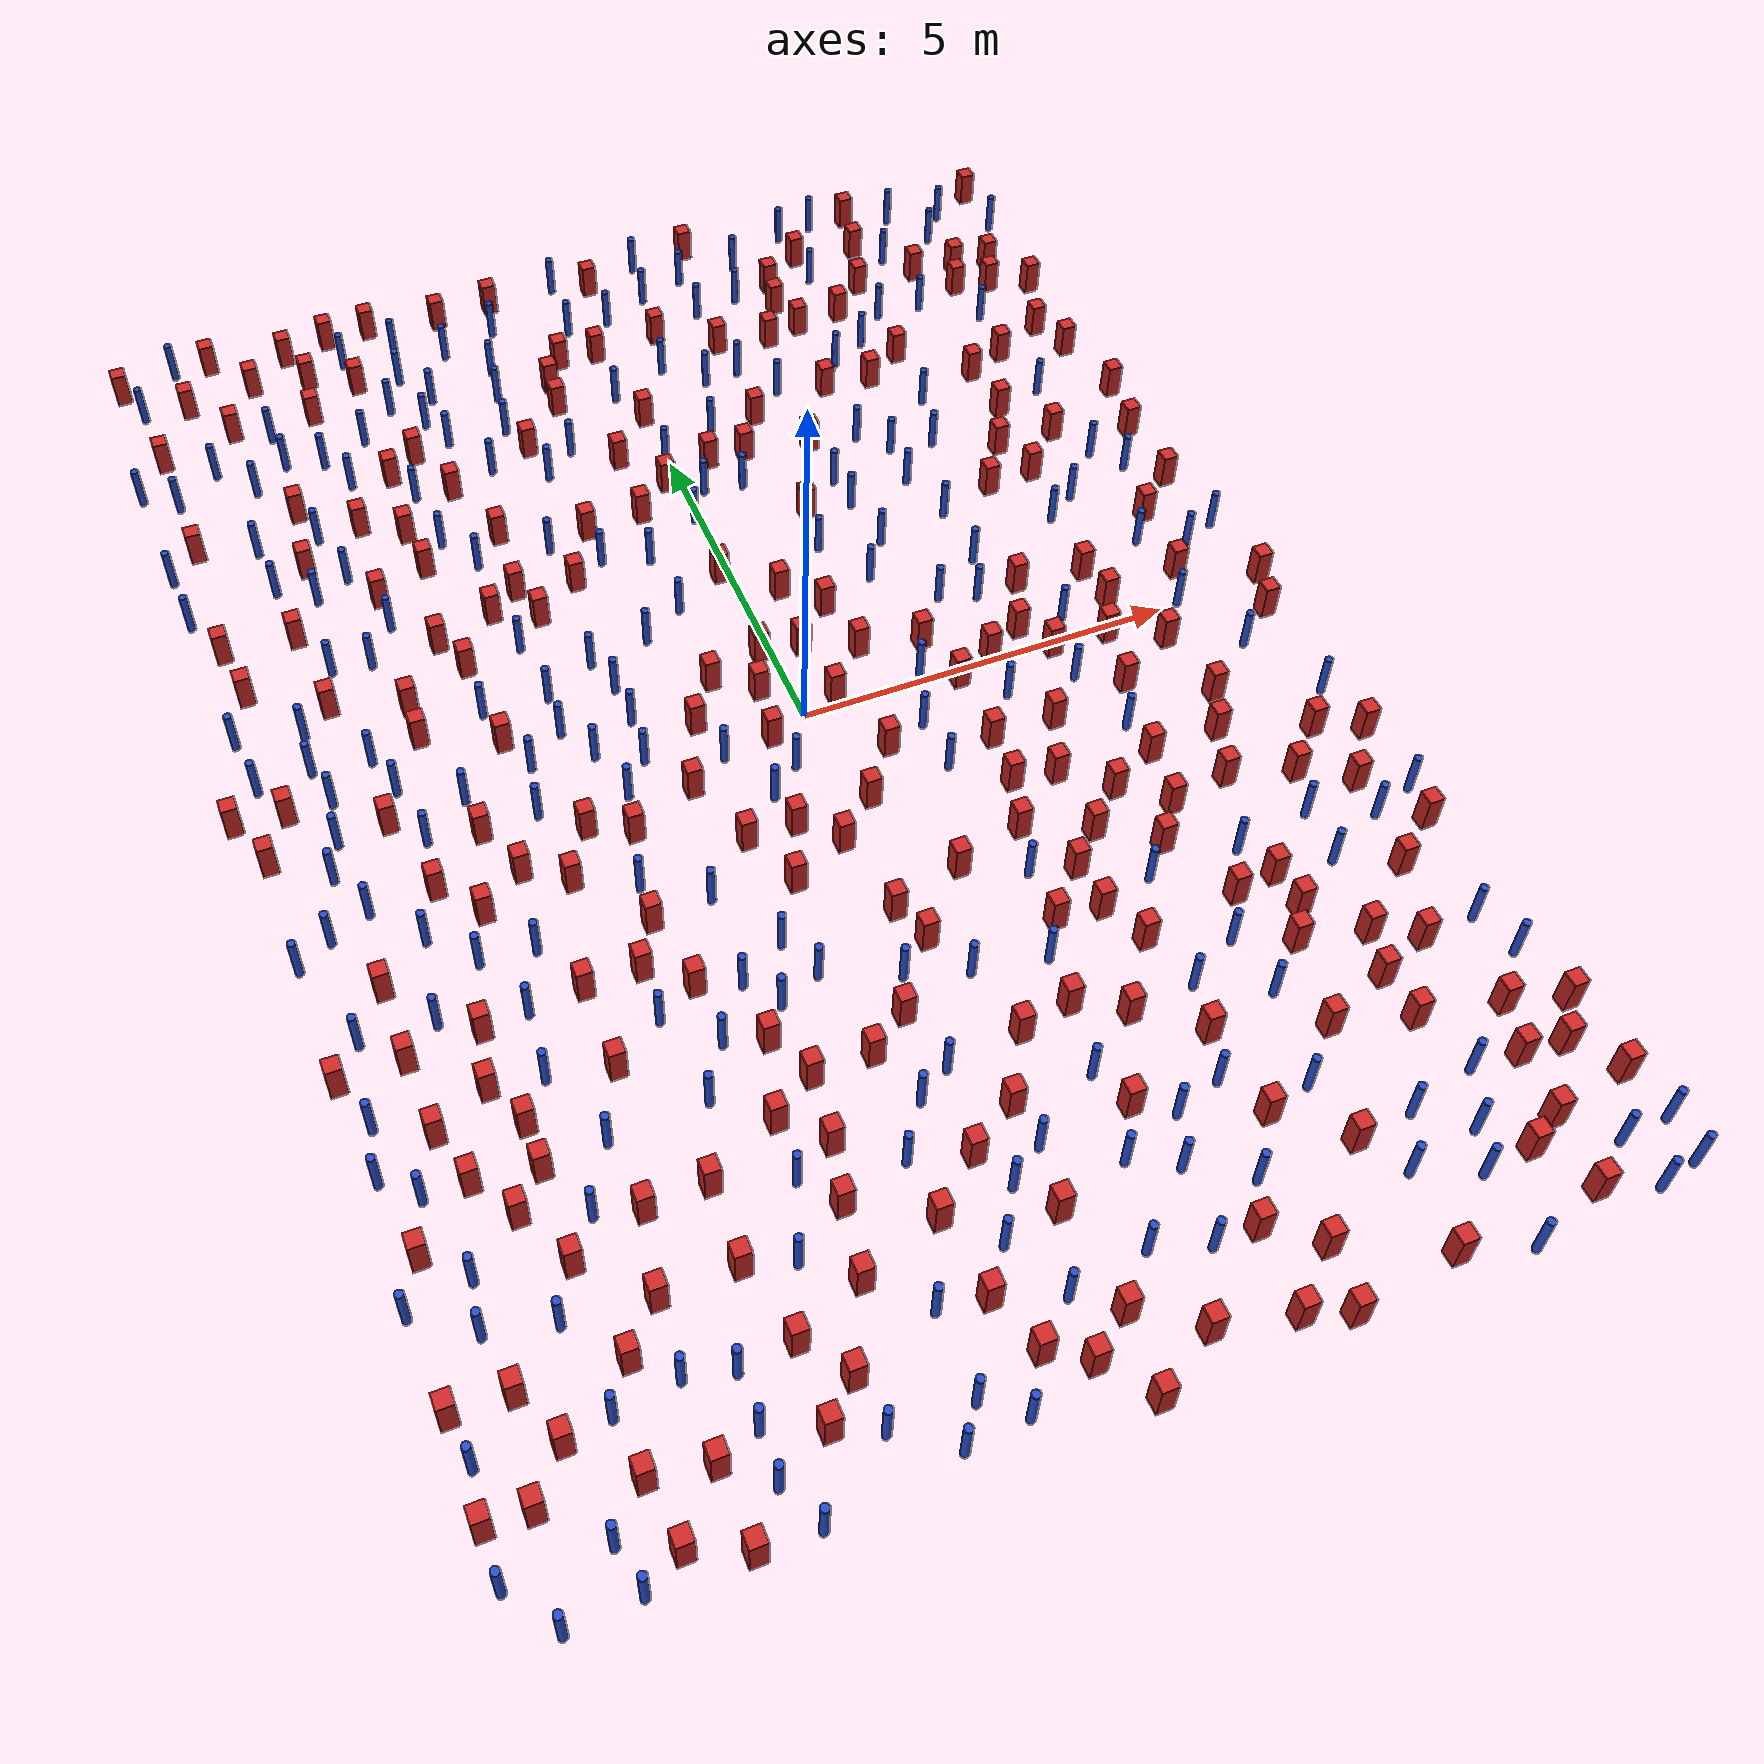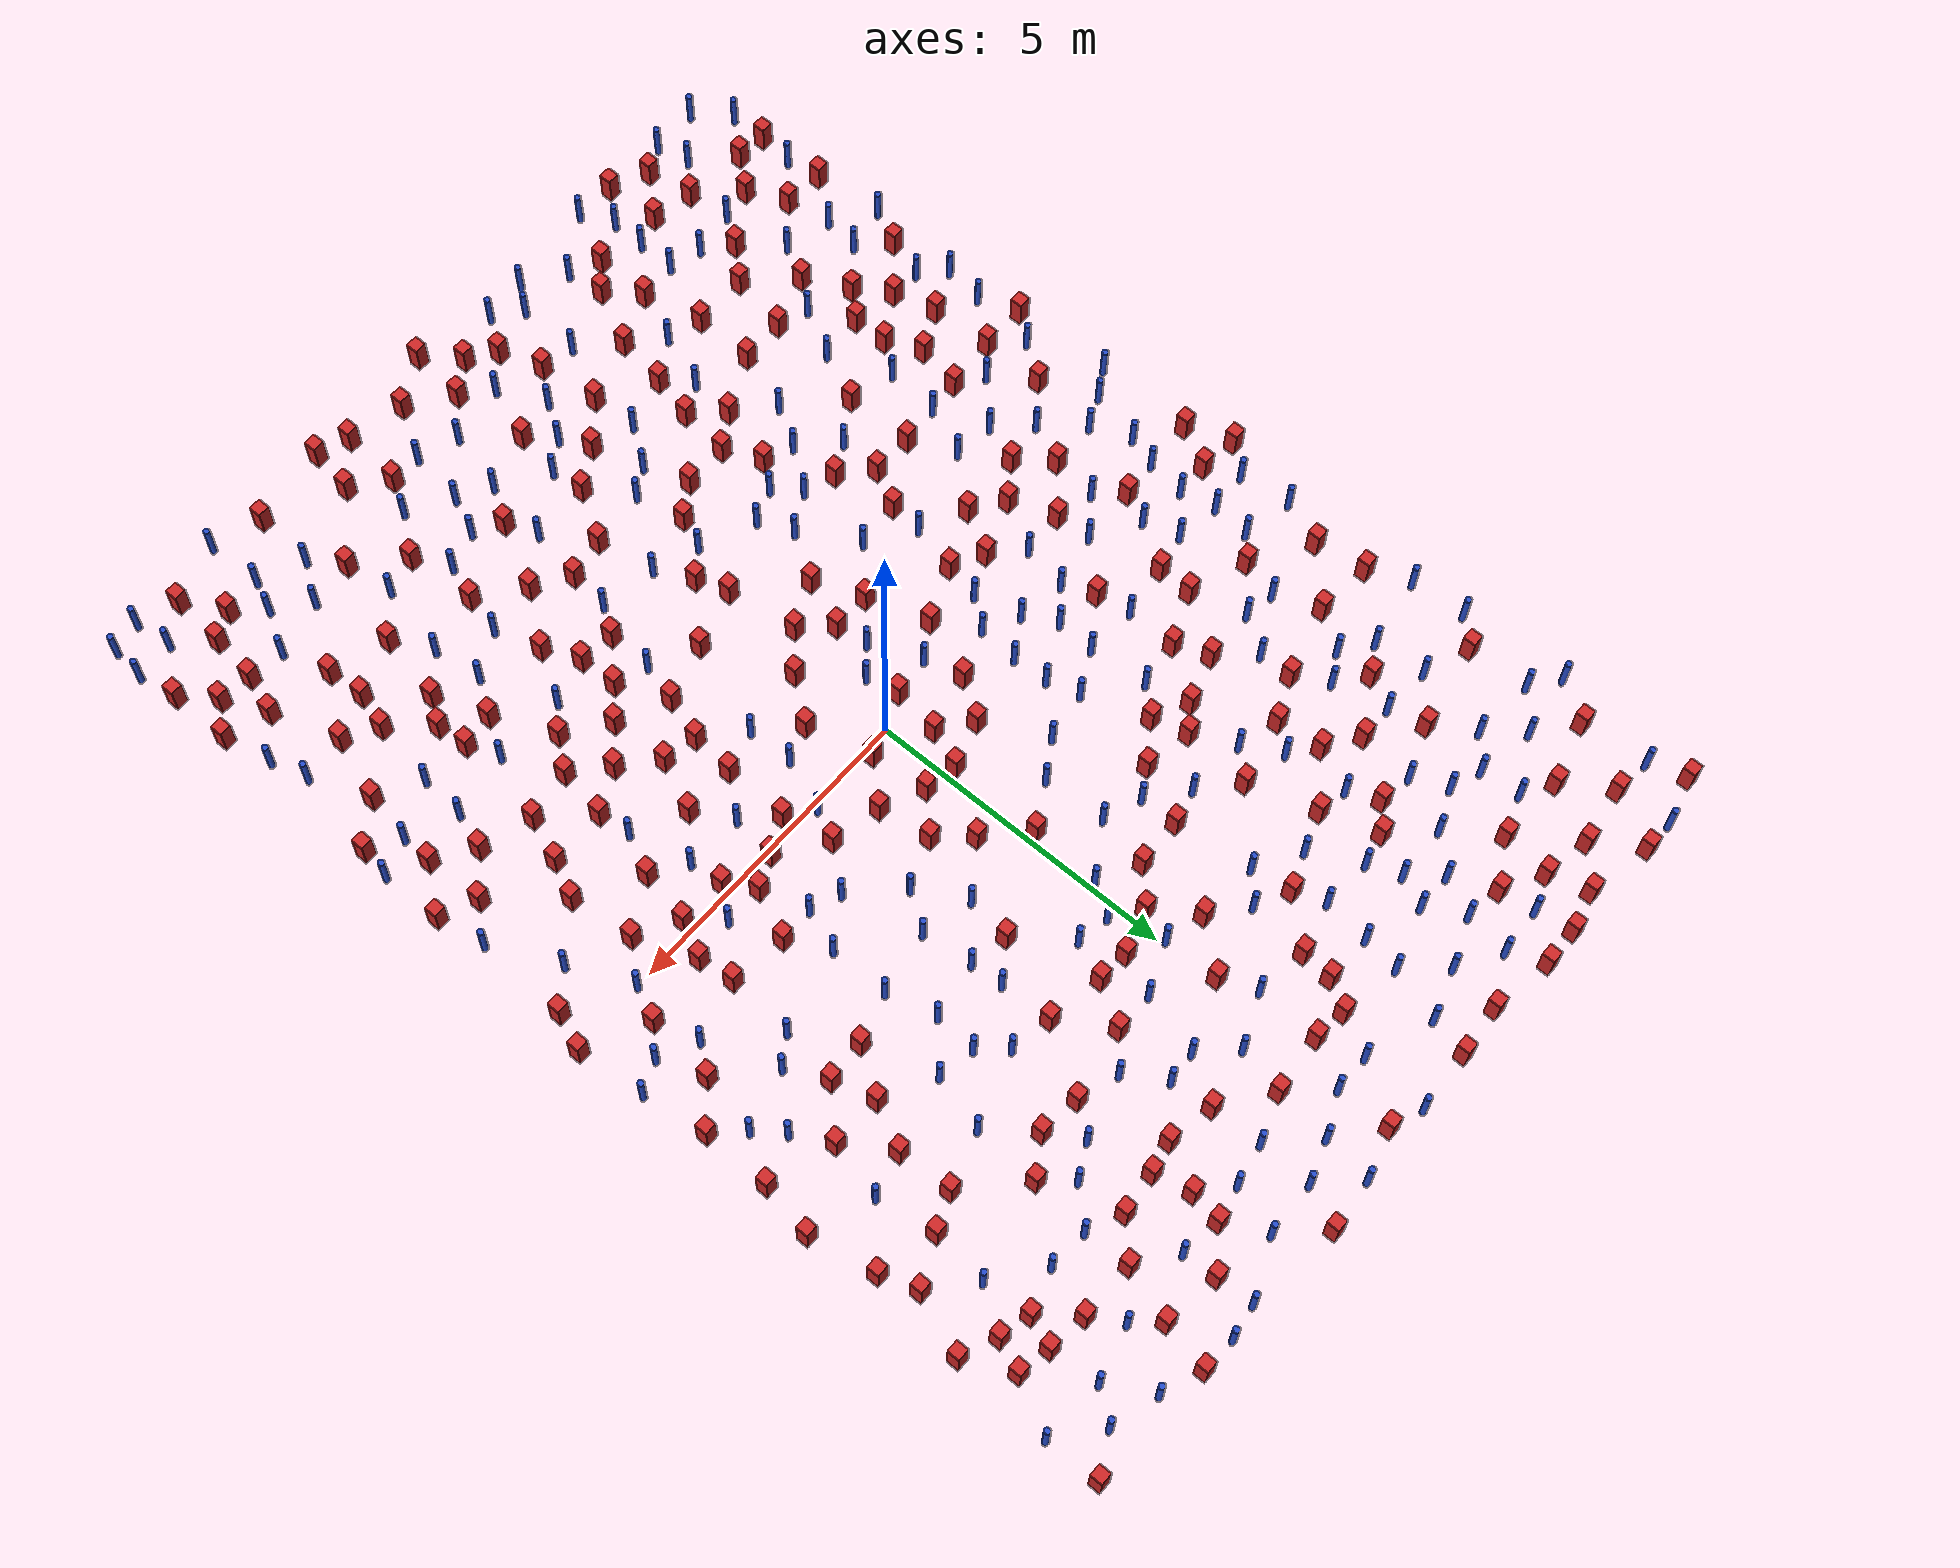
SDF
<sdf version="1.6">
  <model name="dense_71"><model name="pole_obstacle0">
  <static>true</static>
  <pose frame="">-0.848686420528 2.28056023914 -2.66029137441e-07 -5.69430205631e-07 6.84129966562e-07 -8.68349370796e-08</pose>
  <link name="link">
  <pose frame="">0 0 0.3 0 -0 0</pose>
    <inertial>
      <mass>1</mass>
      <inertia>
        <ixx>0.145833</ixx>
        <ixy>0</ixy>
        <ixz>0</ixz>
        <iyy>0.145833</iyy>
        <iyz>0</iyz>
        <izz>0.125</izz>
      </inertia>
    </inertial>
    <collision name="collision">
      <geometry>
        <cylinder>
          <radius>0.05</radius>
          <length>.6</length>
        </cylinder>
      </geometry>
      <max_contacts>10</max_contacts>
      <surface>
        <contact>
          <ode/>
        </contact>
        <bounce/>
        <friction>
          <torsional>
            <ode/>
          </torsional>
          <ode/>
        </friction>
      </surface>
    </collision>
    <visual name="visual">
      <geometry>
        <cylinder>
          <radius>0.05</radius>
          <length>.6</length>
        </cylinder>
      </geometry>
      <material>
        <script>
          <name>Gazebo/Blue</name>
          <uri>file://media/materials/scripts/gazebo.material</uri>
        </script>
      </material>
    </visual>
    <self_collide>0</self_collide>
    <kinematic>0</kinematic>
  </link>
</model>
<model name="pole_obstacle1">
  <static>true</static>
  <pose frame="">-5.95997847254 -5.8177548477 -2.66029137441e-07 -5.69430205655e-07 6.84129966534e-07 -8.68349370984e-08</pose>
  <link name="link">
  <pose frame="">0 0 0.3 0 -0 0</pose>
    <inertial>
      <mass>1</mass>
      <inertia>
        <ixx>0.145833</ixx>
        <ixy>0</ixy>
        <ixz>0</ixz>
        <iyy>0.145833</iyy>
        <iyz>0</iyz>
        <izz>0.125</izz>
      </inertia>
    </inertial>
    <collision name="collision">
      <geometry>
        <cylinder>
          <radius>0.05</radius>
          <length>.6</length>
        </cylinder>
      </geometry>
      <max_contacts>10</max_contacts>
      <surface>
        <contact>
          <ode/>
        </contact>
        <bounce/>
        <friction>
          <torsional>
            <ode/>
          </torsional>
          <ode/>
        </friction>
      </surface>
    </collision>
    <visual name="visual">
      <geometry>
        <cylinder>
          <radius>0.05</radius>
          <length>.6</length>
        </cylinder>
      </geometry>
      <material>
        <script>
          <name>Gazebo/Blue</name>
          <uri>file://media/materials/scripts/gazebo.material</uri>
        </script>
      </material>
    </visual>
    <self_collide>0</self_collide>
    <kinematic>0</kinematic>
  </link>
</model>
<model name="square_post_obstacle0">
  <static>true</static>
  <pose frame="">-6.83887996869 9.17429792986 -7.80171244635e-07 7.17449752808e-06 -5.6639232126e-07 2.2715510512e-05</pose>
  <link name="link">
    <pose frame="">0 0 0.25 0 -0 0</pose>
    <inertial>
      <mass>100</mass>
      <inertia>
        <ixx>0.166667</ixx>
        <ixy>0</ixy>
        <ixz>0</ixz>
        <iyy>0.166667</iyy>
        <iyz>0</iyz>
        <izz>0.166667</izz>
      </inertia>
    </inertial>
    <collision name="collision">
      <geometry>
        <box>
          <size>.2 .2 .5</size>
        </box>
      </geometry>
      <max_contacts>10</max_contacts>
      <surface>
        <contact>
          <ode/>
        </contact>
        <bounce/>
        <friction>
          <torsional>
            <ode/>
          </torsional>
          <ode/>
        </friction>
      </surface>
    </collision>
    <visual name="visual">
      <geometry>
        <box>
          <size>.2 .2 .5</size>
        </box>
      </geometry>
      <material>
        <script>
          <name>Gazebo/Red</name>
          <uri>file://media/materials/scripts/gazebo.material</uri>
        </script>
      </material>
    </visual>
    <self_collide>0</self_collide>
    <kinematic>0</kinematic>
  </link>
</model>
<model name="square_post_obstacle1">
  <static>true</static>
  <pose frame="">-1.99634423738 -5.70971565744 -7.80171244635e-07 7.17449752808e-06 -5.6639232126e-07 2.2715510512e-05</pose>
  <link name="link">
    <pose frame="">0 0 0.25 0 -0 0</pose>
    <inertial>
      <mass>100</mass>
      <inertia>
        <ixx>0.166667</ixx>
        <ixy>0</ixy>
        <ixz>0</ixz>
        <iyy>0.166667</iyy>
        <iyz>0</iyz>
        <izz>0.166667</izz>
      </inertia>
    </inertial>
    <collision name="collision">
      <geometry>
        <box>
          <size>.2 .2 .5</size>
        </box>
      </geometry>
      <max_contacts>10</max_contacts>
      <surface>
        <contact>
          <ode/>
        </contact>
        <bounce/>
        <friction>
          <torsional>
            <ode/>
          </torsional>
          <ode/>
        </friction>
      </surface>
    </collision>
    <visual name="visual">
      <geometry>
        <box>
          <size>.2 .2 .5</size>
        </box>
      </geometry>
      <material>
        <script>
          <name>Gazebo/Red</name>
          <uri>file://media/materials/scripts/gazebo.material</uri>
        </script>
      </material>
    </visual>
    <self_collide>0</self_collide>
    <kinematic>0</kinematic>
  </link>
</model>
<model name="pole_obstacle2">
  <static>true</static>
  <pose frame="">-4.19352279488 -4.81479758741 -2.66029137441e-07 -5.69430205655e-07 6.84129966534e-07 -8.68349370984e-08</pose>
  <link name="link">
  <pose frame="">0 0 0.3 0 -0 0</pose>
    <inertial>
      <mass>1</mass>
      <inertia>
        <ixx>0.145833</ixx>
        <ixy>0</ixy>
        <ixz>0</ixz>
        <iyy>0.145833</iyy>
        <iyz>0</iyz>
        <izz>0.125</izz>
      </inertia>
    </inertial>
    <collision name="collision">
      <geometry>
        <cylinder>
          <radius>0.05</radius>
          <length>.6</length>
        </cylinder>
      </geometry>
      <max_contacts>10</max_contacts>
      <surface>
        <contact>
          <ode/>
        </contact>
        <bounce/>
        <friction>
          <torsional>
            <ode/>
          </torsional>
          <ode/>
        </friction>
      </surface>
    </collision>
    <visual name="visual">
      <geometry>
        <cylinder>
          <radius>0.05</radius>
          <length>.6</length>
        </cylinder>
      </geometry>
      <material>
        <script>
          <name>Gazebo/Blue</name>
          <uri>file://media/materials/scripts/gazebo.material</uri>
        </script>
      </material>
    </visual>
    <self_collide>0</self_collide>
    <kinematic>0</kinematic>
  </link>
</model>
<model name="pole_obstacle3">
  <static>true</static>
  <pose frame="">-1.33987416938 -9.16881281537 -2.66029137441e-07 -5.69430205648e-07 6.84129966543e-07 -8.68349370925e-08</pose>
  <link name="link">
  <pose frame="">0 0 0.3 0 -0 0</pose>
    <inertial>
      <mass>1</mass>
      <inertia>
        <ixx>0.145833</ixx>
        <ixy>0</ixy>
        <ixz>0</ixz>
        <iyy>0.145833</iyy>
        <iyz>0</iyz>
        <izz>0.125</izz>
      </inertia>
    </inertial>
    <collision name="collision">
      <geometry>
        <cylinder>
          <radius>0.05</radius>
          <length>.6</length>
        </cylinder>
      </geometry>
      <max_contacts>10</max_contacts>
      <surface>
        <contact>
          <ode/>
        </contact>
        <bounce/>
        <friction>
          <torsional>
            <ode/>
          </torsional>
          <ode/>
        </friction>
      </surface>
    </collision>
    <visual name="visual">
      <geometry>
        <cylinder>
          <radius>0.05</radius>
          <length>.6</length>
        </cylinder>
      </geometry>
      <material>
        <script>
          <name>Gazebo/Blue</name>
          <uri>file://media/materials/scripts/gazebo.material</uri>
        </script>
      </material>
    </visual>
    <self_collide>0</self_collide>
    <kinematic>0</kinematic>
  </link>
</model>
<model name="pole_obstacle4">
  <static>true</static>
  <pose frame="">2.38419710728 1.24697682987 -2.66029137441e-07 -5.69430205626e-07 6.84129966567e-07 -8.68349370747e-08</pose>
  <link name="link">
  <pose frame="">0 0 0.3 0 -0 0</pose>
    <inertial>
      <mass>1</mass>
      <inertia>
        <ixx>0.145833</ixx>
        <ixy>0</ixy>
        <ixz>0</ixz>
        <iyy>0.145833</iyy>
        <iyz>0</iyz>
        <izz>0.125</izz>
      </inertia>
    </inertial>
    <collision name="collision">
      <geometry>
        <cylinder>
          <radius>0.05</radius>
          <length>.6</length>
        </cylinder>
      </geometry>
      <max_contacts>10</max_contacts>
      <surface>
        <contact>
          <ode/>
        </contact>
        <bounce/>
        <friction>
          <torsional>
            <ode/>
          </torsional>
          <ode/>
        </friction>
      </surface>
    </collision>
    <visual name="visual">
      <geometry>
        <cylinder>
          <radius>0.05</radius>
          <length>.6</length>
        </cylinder>
      </geometry>
      <material>
        <script>
          <name>Gazebo/Blue</name>
          <uri>file://media/materials/scripts/gazebo.material</uri>
        </script>
      </material>
    </visual>
    <self_collide>0</self_collide>
    <kinematic>0</kinematic>
  </link>
</model>
<model name="pole_obstacle5">
  <static>true</static>
  <pose frame="">-2.89578171638 1.43701102641 -2.66029137441e-07 -5.69430205626e-07 6.84129966567e-07 -8.68349370747e-08</pose>
  <link name="link">
  <pose frame="">0 0 0.3 0 -0 0</pose>
    <inertial>
      <mass>1</mass>
      <inertia>
        <ixx>0.145833</ixx>
        <ixy>0</ixy>
        <ixz>0</ixz>
        <iyy>0.145833</iyy>
        <iyz>0</iyz>
        <izz>0.125</izz>
      </inertia>
    </inertial>
    <collision name="collision">
      <geometry>
        <cylinder>
          <radius>0.05</radius>
          <length>.6</length>
        </cylinder>
      </geometry>
      <max_contacts>10</max_contacts>
      <surface>
        <contact>
          <ode/>
        </contact>
        <bounce/>
        <friction>
          <torsional>
            <ode/>
          </torsional>
          <ode/>
        </friction>
      </surface>
    </collision>
    <visual name="visual">
      <geometry>
        <cylinder>
          <radius>0.05</radius>
          <length>.6</length>
        </cylinder>
      </geometry>
      <material>
        <script>
          <name>Gazebo/Blue</name>
          <uri>file://media/materials/scripts/gazebo.material</uri>
        </script>
      </material>
    </visual>
    <self_collide>0</self_collide>
    <kinematic>0</kinematic>
  </link>
</model>
<model name="pole_obstacle6">
  <static>true</static>
  <pose frame="">4.85572318534 2.34125898473 -2.66029137441e-07 -5.69430205643e-07 6.84129966548e-07 -8.68349370881e-08</pose>
  <link name="link">
  <pose frame="">0 0 0.3 0 -0 0</pose>
    <inertial>
      <mass>1</mass>
      <inertia>
        <ixx>0.145833</ixx>
        <ixy>0</ixy>
        <ixz>0</ixz>
        <iyy>0.145833</iyy>
        <iyz>0</iyz>
        <izz>0.125</izz>
      </inertia>
    </inertial>
    <collision name="collision">
      <geometry>
        <cylinder>
          <radius>0.05</radius>
          <length>.6</length>
        </cylinder>
      </geometry>
      <max_contacts>10</max_contacts>
      <surface>
        <contact>
          <ode/>
        </contact>
        <bounce/>
        <friction>
          <torsional>
            <ode/>
          </torsional>
          <ode/>
        </friction>
      </surface>
    </collision>
    <visual name="visual">
      <geometry>
        <cylinder>
          <radius>0.05</radius>
          <length>.6</length>
        </cylinder>
      </geometry>
      <material>
        <script>
          <name>Gazebo/Blue</name>
          <uri>file://media/materials/scripts/gazebo.material</uri>
        </script>
      </material>
    </visual>
    <self_collide>0</self_collide>
    <kinematic>0</kinematic>
  </link>
</model>
<model name="square_post_obstacle2">
  <static>true</static>
  <pose frame="">-6.54047121895 3.64302250898 -7.80171244635e-07 7.17449752808e-06 -5.6639232126e-07 2.2715510512e-05</pose>
  <link name="link">
    <pose frame="">0 0 0.25 0 -0 0</pose>
    <inertial>
      <mass>100</mass>
      <inertia>
        <ixx>0.166667</ixx>
        <ixy>0</ixy>
        <ixz>0</ixz>
        <iyy>0.166667</iyy>
        <iyz>0</iyz>
        <izz>0.166667</izz>
      </inertia>
    </inertial>
    <collision name="collision">
      <geometry>
        <box>
          <size>.2 .2 .5</size>
        </box>
      </geometry>
      <max_contacts>10</max_contacts>
      <surface>
        <contact>
          <ode/>
        </contact>
        <bounce/>
        <friction>
          <torsional>
            <ode/>
          </torsional>
          <ode/>
        </friction>
      </surface>
    </collision>
    <visual name="visual">
      <geometry>
        <box>
          <size>.2 .2 .5</size>
        </box>
      </geometry>
      <material>
        <script>
          <name>Gazebo/Red</name>
          <uri>file://media/materials/scripts/gazebo.material</uri>
        </script>
      </material>
    </visual>
    <self_collide>0</self_collide>
    <kinematic>0</kinematic>
  </link>
</model>
<model name="square_post_obstacle3">
  <static>true</static>
  <pose frame="">-0.052275715814 5.99567114476 -7.80171244635e-07 7.17449752808e-06 -5.6639232126e-07 2.2715510512e-05</pose>
  <link name="link">
    <pose frame="">0 0 0.25 0 -0 0</pose>
    <inertial>
      <mass>100</mass>
      <inertia>
        <ixx>0.166667</ixx>
        <ixy>0</ixy>
        <ixz>0</ixz>
        <iyy>0.166667</iyy>
        <iyz>0</iyz>
        <izz>0.166667</izz>
      </inertia>
    </inertial>
    <collision name="collision">
      <geometry>
        <box>
          <size>.2 .2 .5</size>
        </box>
      </geometry>
      <max_contacts>10</max_contacts>
      <surface>
        <contact>
          <ode/>
        </contact>
        <bounce/>
        <friction>
          <torsional>
            <ode/>
          </torsional>
          <ode/>
        </friction>
      </surface>
    </collision>
    <visual name="visual">
      <geometry>
        <box>
          <size>.2 .2 .5</size>
        </box>
      </geometry>
      <material>
        <script>
          <name>Gazebo/Red</name>
          <uri>file://media/materials/scripts/gazebo.material</uri>
        </script>
      </material>
    </visual>
    <self_collide>0</self_collide>
    <kinematic>0</kinematic>
  </link>
</model>
<model name="square_post_obstacle4">
  <static>true</static>
  <pose frame="">-3.83080562051 -2.89418238608 -7.80171244635e-07 7.17449752808e-06 -5.6639232126e-07 2.2715510512e-05</pose>
  <link name="link">
    <pose frame="">0 0 0.25 0 -0 0</pose>
    <inertial>
      <mass>100</mass>
      <inertia>
        <ixx>0.166667</ixx>
        <ixy>0</ixy>
        <ixz>0</ixz>
        <iyy>0.166667</iyy>
        <iyz>0</iyz>
        <izz>0.166667</izz>
      </inertia>
    </inertial>
    <collision name="collision">
      <geometry>
        <box>
          <size>.2 .2 .5</size>
        </box>
      </geometry>
      <max_contacts>10</max_contacts>
      <surface>
        <contact>
          <ode/>
        </contact>
        <bounce/>
        <friction>
          <torsional>
            <ode/>
          </torsional>
          <ode/>
        </friction>
      </surface>
    </collision>
    <visual name="visual">
      <geometry>
        <box>
          <size>.2 .2 .5</size>
        </box>
      </geometry>
      <material>
        <script>
          <name>Gazebo/Red</name>
          <uri>file://media/materials/scripts/gazebo.material</uri>
        </script>
      </material>
    </visual>
    <self_collide>0</self_collide>
    <kinematic>0</kinematic>
  </link>
</model>
<model name="pole_obstacle7">
  <static>true</static>
  <pose frame="">1.96230142851 3.81808928893 -2.66029137441e-07 -5.69430205637e-07 6.84129966555e-07 -8.6834937083e-08</pose>
  <link name="link">
  <pose frame="">0 0 0.3 0 -0 0</pose>
    <inertial>
      <mass>1</mass>
      <inertia>
        <ixx>0.145833</ixx>
        <ixy>0</ixy>
        <ixz>0</ixz>
        <iyy>0.145833</iyy>
        <iyz>0</iyz>
        <izz>0.125</izz>
      </inertia>
    </inertial>
    <collision name="collision">
      <geometry>
        <cylinder>
          <radius>0.05</radius>
          <length>.6</length>
        </cylinder>
      </geometry>
      <max_contacts>10</max_contacts>
      <surface>
        <contact>
          <ode/>
        </contact>
        <bounce/>
        <friction>
          <torsional>
            <ode/>
          </torsional>
          <ode/>
        </friction>
      </surface>
    </collision>
    <visual name="visual">
      <geometry>
        <cylinder>
          <radius>0.05</radius>
          <length>.6</length>
        </cylinder>
      </geometry>
      <material>
        <script>
          <name>Gazebo/Blue</name>
          <uri>file://media/materials/scripts/gazebo.material</uri>
        </script>
      </material>
    </visual>
    <self_collide>0</self_collide>
    <kinematic>0</kinematic>
  </link>
</model>
<model name="pole_obstacle8">
  <static>true</static>
  <pose frame="">2.49458877302 -0.618679551614 -2.66029137441e-07 -5.69430205624e-07 6.8412996657e-07 -8.68349370746e-08</pose>
  <link name="link">
  <pose frame="">0 0 0.3 0 -0 0</pose>
    <inertial>
      <mass>1</mass>
      <inertia>
        <ixx>0.145833</ixx>
        <ixy>0</ixy>
        <ixz>0</ixz>
        <iyy>0.145833</iyy>
        <iyz>0</iyz>
        <izz>0.125</izz>
      </inertia>
    </inertial>
    <collision name="collision">
      <geometry>
        <cylinder>
          <radius>0.05</radius>
          <length>.6</length>
        </cylinder>
      </geometry>
      <max_contacts>10</max_contacts>
      <surface>
        <contact>
          <ode/>
        </contact>
        <bounce/>
        <friction>
          <torsional>
            <ode/>
          </torsional>
          <ode/>
        </friction>
      </surface>
    </collision>
    <visual name="visual">
      <geometry>
        <cylinder>
          <radius>0.05</radius>
          <length>.6</length>
        </cylinder>
      </geometry>
      <material>
        <script>
          <name>Gazebo/Blue</name>
          <uri>file://media/materials/scripts/gazebo.material</uri>
        </script>
      </material>
    </visual>
    <self_collide>0</self_collide>
    <kinematic>0</kinematic>
  </link>
</model>
<model name="square_post_obstacle5">
  <static>true</static>
  <pose frame="">-6.42439165797 2.81819154532 -7.80171244635e-07 7.17449752808e-06 -5.6639232126e-07 2.2715510512e-05</pose>
  <link name="link">
    <pose frame="">0 0 0.25 0 -0 0</pose>
    <inertial>
      <mass>100</mass>
      <inertia>
        <ixx>0.166667</ixx>
        <ixy>0</ixy>
        <ixz>0</ixz>
        <iyy>0.166667</iyy>
        <iyz>0</iyz>
        <izz>0.166667</izz>
      </inertia>
    </inertial>
    <collision name="collision">
      <geometry>
        <box>
          <size>.2 .2 .5</size>
        </box>
      </geometry>
      <max_contacts>10</max_contacts>
      <surface>
        <contact>
          <ode/>
        </contact>
        <bounce/>
        <friction>
          <torsional>
            <ode/>
          </torsional>
          <ode/>
        </friction>
      </surface>
    </collision>
    <visual name="visual">
      <geometry>
        <box>
          <size>.2 .2 .5</size>
        </box>
      </geometry>
      <material>
        <script>
          <name>Gazebo/Red</name>
          <uri>file://media/materials/scripts/gazebo.material</uri>
        </script>
      </material>
    </visual>
    <self_collide>0</self_collide>
    <kinematic>0</kinematic>
  </link>
</model>
<model name="square_post_obstacle6">
  <static>true</static>
  <pose frame="">-3.39397575072 -6.6740779854 -7.80171244635e-07 7.17449752808e-06 -5.6639232126e-07 2.2715510512e-05</pose>
  <link name="link">
    <pose frame="">0 0 0.25 0 -0 0</pose>
    <inertial>
      <mass>100</mass>
      <inertia>
        <ixx>0.166667</ixx>
        <ixy>0</ixy>
        <ixz>0</ixz>
        <iyy>0.166667</iyy>
        <iyz>0</iyz>
        <izz>0.166667</izz>
      </inertia>
    </inertial>
    <collision name="collision">
      <geometry>
        <box>
          <size>.2 .2 .5</size>
        </box>
      </geometry>
      <max_contacts>10</max_contacts>
      <surface>
        <contact>
          <ode/>
        </contact>
        <bounce/>
        <friction>
          <torsional>
            <ode/>
          </torsional>
          <ode/>
        </friction>
      </surface>
    </collision>
    <visual name="visual">
      <geometry>
        <box>
          <size>.2 .2 .5</size>
        </box>
      </geometry>
      <material>
        <script>
          <name>Gazebo/Red</name>
          <uri>file://media/materials/scripts/gazebo.material</uri>
        </script>
      </material>
    </visual>
    <self_collide>0</self_collide>
    <kinematic>0</kinematic>
  </link>
</model>
<model name="square_post_obstacle7">
  <static>true</static>
  <pose frame="">5.61535277145 -4.75521165374 -7.80171244635e-07 7.17449752808e-06 -5.6639232126e-07 2.2715510512e-05</pose>
  <link name="link">
    <pose frame="">0 0 0.25 0 -0 0</pose>
    <inertial>
      <mass>100</mass>
      <inertia>
        <ixx>0.166667</ixx>
        <ixy>0</ixy>
        <ixz>0</ixz>
        <iyy>0.166667</iyy>
        <iyz>0</iyz>
        <izz>0.166667</izz>
      </inertia>
    </inertial>
    <collision name="collision">
      <geometry>
        <box>
          <size>.2 .2 .5</size>
        </box>
      </geometry>
      <max_contacts>10</max_contacts>
      <surface>
        <contact>
          <ode/>
        </contact>
        <bounce/>
        <friction>
          <torsional>
            <ode/>
          </torsional>
          <ode/>
        </friction>
      </surface>
    </collision>
    <visual name="visual">
      <geometry>
        <box>
          <size>.2 .2 .5</size>
        </box>
      </geometry>
      <material>
        <script>
          <name>Gazebo/Red</name>
          <uri>file://media/materials/scripts/gazebo.material</uri>
        </script>
      </material>
    </visual>
    <self_collide>0</self_collide>
    <kinematic>0</kinematic>
  </link>
</model>
<model name="pole_obstacle9">
  <static>true</static>
  <pose frame="">-2.97673412354 2.38530855671 -2.66029137441e-07 -5.69430205643e-07 6.84129966548e-07 -8.68349370903e-08</pose>
  <link name="link">
  <pose frame="">0 0 0.3 0 -0 0</pose>
    <inertial>
      <mass>1</mass>
      <inertia>
        <ixx>0.145833</ixx>
        <ixy>0</ixy>
        <ixz>0</ixz>
        <iyy>0.145833</iyy>
        <iyz>0</iyz>
        <izz>0.125</izz>
      </inertia>
    </inertial>
    <collision name="collision">
      <geometry>
        <cylinder>
          <radius>0.05</radius>
          <length>.6</length>
        </cylinder>
      </geometry>
      <max_contacts>10</max_contacts>
      <surface>
        <contact>
          <ode/>
        </contact>
        <bounce/>
        <friction>
          <torsional>
            <ode/>
          </torsional>
          <ode/>
        </friction>
      </surface>
    </collision>
    <visual name="visual">
      <geometry>
        <cylinder>
          <radius>0.05</radius>
          <length>.6</length>
        </cylinder>
      </geometry>
      <material>
        <script>
          <name>Gazebo/Blue</name>
          <uri>file://media/materials/scripts/gazebo.material</uri>
        </script>
      </material>
    </visual>
    <self_collide>0</self_collide>
    <kinematic>0</kinematic>
  </link>
</model>
<model name="pole_obstacle10">
  <static>true</static>
  <pose frame="">2.35610760975 8.82782065724 -2.66029137497e-07 -5.69430205676e-07 6.84129966501e-07 -8.6834937112e-08</pose>
  <link name="link">
  <pose frame="">0 0 0.3 0 -0 0</pose>
    <inertial>
      <mass>1</mass>
      <inertia>
        <ixx>0.145833</ixx>
        <ixy>0</ixy>
        <ixz>0</ixz>
        <iyy>0.145833</iyy>
        <iyz>0</iyz>
        <izz>0.125</izz>
      </inertia>
    </inertial>
    <collision name="collision">
      <geometry>
        <cylinder>
          <radius>0.05</radius>
          <length>.6</length>
        </cylinder>
      </geometry>
      <max_contacts>10</max_contacts>
      <surface>
        <contact>
          <ode/>
        </contact>
        <bounce/>
        <friction>
          <torsional>
            <ode/>
          </torsional>
          <ode/>
        </friction>
      </surface>
    </collision>
    <visual name="visual">
      <geometry>
        <cylinder>
          <radius>0.05</radius>
          <length>.6</length>
        </cylinder>
      </geometry>
      <material>
        <script>
          <name>Gazebo/Blue</name>
          <uri>file://media/materials/scripts/gazebo.material</uri>
        </script>
      </material>
    </visual>
    <self_collide>0</self_collide>
    <kinematic>0</kinematic>
  </link>
</model>
<model name="pole_obstacle11">
  <static>true</static>
  <pose frame="">5.25460463 0.0208689462989 -2.66029137441e-07 -5.69430205622e-07 6.84129966572e-07 -8.68349370728e-08</pose>
  <link name="link">
  <pose frame="">0 0 0.3 0 -0 0</pose>
    <inertial>
      <mass>1</mass>
      <inertia>
        <ixx>0.145833</ixx>
        <ixy>0</ixy>
        <ixz>0</ixz>
        <iyy>0.145833</iyy>
        <iyz>0</iyz>
        <izz>0.125</izz>
      </inertia>
    </inertial>
    <collision name="collision">
      <geometry>
        <cylinder>
          <radius>0.05</radius>
          <length>.6</length>
        </cylinder>
      </geometry>
      <max_contacts>10</max_contacts>
      <surface>
        <contact>
          <ode/>
        </contact>
        <bounce/>
        <friction>
          <torsional>
            <ode/>
          </torsional>
          <ode/>
        </friction>
      </surface>
    </collision>
    <visual name="visual">
      <geometry>
        <cylinder>
          <radius>0.05</radius>
          <length>.6</length>
        </cylinder>
      </geometry>
      <material>
        <script>
          <name>Gazebo/Blue</name>
          <uri>file://media/materials/scripts/gazebo.material</uri>
        </script>
      </material>
    </visual>
    <self_collide>0</self_collide>
    <kinematic>0</kinematic>
  </link>
</model>
<model name="pole_obstacle12">
  <static>true</static>
  <pose frame="">5.76693868843 -3.97918718534 -2.66029137441e-07 -5.69430205639e-07 6.84129966552e-07 -8.68349370846e-08</pose>
  <link name="link">
  <pose frame="">0 0 0.3 0 -0 0</pose>
    <inertial>
      <mass>1</mass>
      <inertia>
        <ixx>0.145833</ixx>
        <ixy>0</ixy>
        <ixz>0</ixz>
        <iyy>0.145833</iyy>
        <iyz>0</iyz>
        <izz>0.125</izz>
      </inertia>
    </inertial>
    <collision name="collision">
      <geometry>
        <cylinder>
          <radius>0.05</radius>
          <length>.6</length>
        </cylinder>
      </geometry>
      <max_contacts>10</max_contacts>
      <surface>
        <contact>
          <ode/>
        </contact>
        <bounce/>
        <friction>
          <torsional>
            <ode/>
          </torsional>
          <ode/>
        </friction>
      </surface>
    </collision>
    <visual name="visual">
      <geometry>
        <cylinder>
          <radius>0.05</radius>
          <length>.6</length>
        </cylinder>
      </geometry>
      <material>
        <script>
          <name>Gazebo/Blue</name>
          <uri>file://media/materials/scripts/gazebo.material</uri>
        </script>
      </material>
    </visual>
    <self_collide>0</self_collide>
    <kinematic>0</kinematic>
  </link>
</model>
<model name="square_post_obstacle8">
  <static>true</static>
  <pose frame="">-0.32956075323 -2.03776526633 -7.80171244635e-07 7.17449752808e-06 -5.6639232126e-07 2.2715510512e-05</pose>
  <link name="link">
    <pose frame="">0 0 0.25 0 -0 0</pose>
    <inertial>
      <mass>100</mass>
      <inertia>
        <ixx>0.166667</ixx>
        <ixy>0</ixy>
        <ixz>0</ixz>
        <iyy>0.166667</iyy>
        <iyz>0</iyz>
        <izz>0.166667</izz>
      </inertia>
    </inertial>
    <collision name="collision">
      <geometry>
        <box>
          <size>.2 .2 .5</size>
        </box>
      </geometry>
      <max_contacts>10</max_contacts>
      <surface>
        <contact>
          <ode/>
        </contact>
        <bounce/>
        <friction>
          <torsional>
            <ode/>
          </torsional>
          <ode/>
        </friction>
      </surface>
    </collision>
    <visual name="visual">
      <geometry>
        <box>
          <size>.2 .2 .5</size>
        </box>
      </geometry>
      <material>
        <script>
          <name>Gazebo/Red</name>
          <uri>file://media/materials/scripts/gazebo.material</uri>
        </script>
      </material>
    </visual>
    <self_collide>0</self_collide>
    <kinematic>0</kinematic>
  </link>
</model>
<model name="square_post_obstacle9">
  <static>true</static>
  <pose frame="">-5.68280838163 -4.75966509383 -7.80171244635e-07 7.17449752808e-06 -5.6639232126e-07 2.2715510512e-05</pose>
  <link name="link">
    <pose frame="">0 0 0.25 0 -0 0</pose>
    <inertial>
      <mass>100</mass>
      <inertia>
        <ixx>0.166667</ixx>
        <ixy>0</ixy>
        <ixz>0</ixz>
        <iyy>0.166667</iyy>
        <iyz>0</iyz>
        <izz>0.166667</izz>
      </inertia>
    </inertial>
    <collision name="collision">
      <geometry>
        <box>
          <size>.2 .2 .5</size>
        </box>
      </geometry>
      <max_contacts>10</max_contacts>
      <surface>
        <contact>
          <ode/>
        </contact>
        <bounce/>
        <friction>
          <torsional>
            <ode/>
          </torsional>
          <ode/>
        </friction>
      </surface>
    </collision>
    <visual name="visual">
      <geometry>
        <box>
          <size>.2 .2 .5</size>
        </box>
      </geometry>
      <material>
        <script>
          <name>Gazebo/Red</name>
          <uri>file://media/materials/scripts/gazebo.material</uri>
        </script>
      </material>
    </visual>
    <self_collide>0</self_collide>
    <kinematic>0</kinematic>
  </link>
</model>
<model name="pole_obstacle13">
  <static>true</static>
  <pose frame="">-6.74214288484 -1.471598612 -2.66029137441e-07 -5.69430205627e-07 6.84129966567e-07 -8.68349370776e-08</pose>
  <link name="link">
  <pose frame="">0 0 0.3 0 -0 0</pose>
    <inertial>
      <mass>1</mass>
      <inertia>
        <ixx>0.145833</ixx>
        <ixy>0</ixy>
        <ixz>0</ixz>
        <iyy>0.145833</iyy>
        <iyz>0</iyz>
        <izz>0.125</izz>
      </inertia>
    </inertial>
    <collision name="collision">
      <geometry>
        <cylinder>
          <radius>0.05</radius>
          <length>.6</length>
        </cylinder>
      </geometry>
      <max_contacts>10</max_contacts>
      <surface>
        <contact>
          <ode/>
        </contact>
        <bounce/>
        <friction>
          <torsional>
            <ode/>
          </torsional>
          <ode/>
        </friction>
      </surface>
    </collision>
    <visual name="visual">
      <geometry>
        <cylinder>
          <radius>0.05</radius>
          <length>.6</length>
        </cylinder>
      </geometry>
      <material>
        <script>
          <name>Gazebo/Blue</name>
          <uri>file://media/materials/scripts/gazebo.material</uri>
        </script>
      </material>
    </visual>
    <self_collide>0</self_collide>
    <kinematic>0</kinematic>
  </link>
</model>
<model name="square_post_obstacle10">
  <static>true</static>
  <pose frame="">-1.38638351002 -1.59635780547 -7.80171244635e-07 7.17449752808e-06 -5.6639232126e-07 2.2715510512e-05</pose>
  <link name="link">
    <pose frame="">0 0 0.25 0 -0 0</pose>
    <inertial>
      <mass>100</mass>
      <inertia>
        <ixx>0.166667</ixx>
        <ixy>0</ixy>
        <ixz>0</ixz>
        <iyy>0.166667</iyy>
        <iyz>0</iyz>
        <izz>0.166667</izz>
      </inertia>
    </inertial>
    <collision name="collision">
      <geometry>
        <box>
          <size>.2 .2 .5</size>
        </box>
      </geometry>
      <max_contacts>10</max_contacts>
      <surface>
        <contact>
          <ode/>
        </contact>
        <bounce/>
        <friction>
          <torsional>
            <ode/>
          </torsional>
          <ode/>
        </friction>
      </surface>
    </collision>
    <visual name="visual">
      <geometry>
        <box>
          <size>.2 .2 .5</size>
        </box>
      </geometry>
      <material>
        <script>
          <name>Gazebo/Red</name>
          <uri>file://media/materials/scripts/gazebo.material</uri>
        </script>
      </material>
    </visual>
    <self_collide>0</self_collide>
    <kinematic>0</kinematic>
  </link>
</model>
<model name="square_post_obstacle11">
  <static>true</static>
  <pose frame="">-5.19711062765 -3.73991201067 -7.80171244635e-07 7.17449752808e-06 -5.6639232126e-07 2.2715510512e-05</pose>
  <link name="link">
    <pose frame="">0 0 0.25 0 -0 0</pose>
    <inertial>
      <mass>100</mass>
      <inertia>
        <ixx>0.166667</ixx>
        <ixy>0</ixy>
        <ixz>0</ixz>
        <iyy>0.166667</iyy>
        <iyz>0</iyz>
        <izz>0.166667</izz>
      </inertia>
    </inertial>
    <collision name="collision">
      <geometry>
        <box>
          <size>.2 .2 .5</size>
        </box>
      </geometry>
      <max_contacts>10</max_contacts>
      <surface>
        <contact>
          <ode/>
        </contact>
        <bounce/>
        <friction>
          <torsional>
            <ode/>
          </torsional>
          <ode/>
        </friction>
      </surface>
    </collision>
    <visual name="visual">
      <geometry>
        <box>
          <size>.2 .2 .5</size>
        </box>
      </geometry>
      <material>
        <script>
          <name>Gazebo/Red</name>
          <uri>file://media/materials/scripts/gazebo.material</uri>
        </script>
      </material>
    </visual>
    <self_collide>0</self_collide>
    <kinematic>0</kinematic>
  </link>
</model>
<model name="pole_obstacle14">
  <static>true</static>
  <pose frame="">-5.05208416302 0.661545683711 -2.66029137441e-07 -5.69430205635e-07 6.84129966557e-07 -8.68349370823e-08</pose>
  <link name="link">
  <pose frame="">0 0 0.3 0 -0 0</pose>
    <inertial>
      <mass>1</mass>
      <inertia>
        <ixx>0.145833</ixx>
        <ixy>0</ixy>
        <ixz>0</ixz>
        <iyy>0.145833</iyy>
        <iyz>0</iyz>
        <izz>0.125</izz>
      </inertia>
    </inertial>
    <collision name="collision">
      <geometry>
        <cylinder>
          <radius>0.05</radius>
          <length>.6</length>
        </cylinder>
      </geometry>
      <max_contacts>10</max_contacts>
      <surface>
        <contact>
          <ode/>
        </contact>
        <bounce/>
        <friction>
          <torsional>
            <ode/>
          </torsional>
          <ode/>
        </friction>
      </surface>
    </collision>
    <visual name="visual">
      <geometry>
        <cylinder>
          <radius>0.05</radius>
          <length>.6</length>
        </cylinder>
      </geometry>
      <material>
        <script>
          <name>Gazebo/Blue</name>
          <uri>file://media/materials/scripts/gazebo.material</uri>
        </script>
      </material>
    </visual>
    <self_collide>0</self_collide>
    <kinematic>0</kinematic>
  </link>
</model>
<model name="pole_obstacle15">
  <static>true</static>
  <pose frame="">4.98668080263 -3.65906359075 -2.66029137441e-07 -5.69430205643e-07 6.84129966548e-07 -8.68349370881e-08</pose>
  <link name="link">
  <pose frame="">0 0 0.3 0 -0 0</pose>
    <inertial>
      <mass>1</mass>
      <inertia>
        <ixx>0.145833</ixx>
        <ixy>0</ixy>
        <ixz>0</ixz>
        <iyy>0.145833</iyy>
        <iyz>0</iyz>
        <izz>0.125</izz>
      </inertia>
    </inertial>
    <collision name="collision">
      <geometry>
        <cylinder>
          <radius>0.05</radius>
          <length>.6</length>
        </cylinder>
      </geometry>
      <max_contacts>10</max_contacts>
      <surface>
        <contact>
          <ode/>
        </contact>
        <bounce/>
        <friction>
          <torsional>
            <ode/>
          </torsional>
          <ode/>
        </friction>
      </surface>
    </collision>
    <visual name="visual">
      <geometry>
        <cylinder>
          <radius>0.05</radius>
          <length>.6</length>
        </cylinder>
      </geometry>
      <material>
        <script>
          <name>Gazebo/Blue</name>
          <uri>file://media/materials/scripts/gazebo.material</uri>
        </script>
      </material>
    </visual>
    <self_collide>0</self_collide>
    <kinematic>0</kinematic>
  </link>
</model>
<model name="square_post_obstacle12">
  <static>true</static>
  <pose frame="">2.04868826181 -3.39985556791 -7.80171244635e-07 7.17449752808e-06 -5.6639232126e-07 2.2715510512e-05</pose>
  <link name="link">
    <pose frame="">0 0 0.25 0 -0 0</pose>
    <inertial>
      <mass>100</mass>
      <inertia>
        <ixx>0.166667</ixx>
        <ixy>0</ixy>
        <ixz>0</ixz>
        <iyy>0.166667</iyy>
        <iyz>0</iyz>
        <izz>0.166667</izz>
      </inertia>
    </inertial>
    <collision name="collision">
      <geometry>
        <box>
          <size>.2 .2 .5</size>
        </box>
      </geometry>
      <max_contacts>10</max_contacts>
      <surface>
        <contact>
          <ode/>
        </contact>
        <bounce/>
        <friction>
          <torsional>
            <ode/>
          </torsional>
          <ode/>
        </friction>
      </surface>
    </collision>
    <visual name="visual">
      <geometry>
        <box>
          <size>.2 .2 .5</size>
        </box>
      </geometry>
      <material>
        <script>
          <name>Gazebo/Red</name>
          <uri>file://media/materials/scripts/gazebo.material</uri>
        </script>
      </material>
    </visual>
    <self_collide>0</self_collide>
    <kinematic>0</kinematic>
  </link>
</model>
<model name="pole_obstacle16">
  <static>true</static>
  <pose frame="">-6.58028330687 -4.39368769634 -2.66029137441e-07 -5.69430205655e-07 6.84129966534e-07 -8.68349370984e-08</pose>
  <link name="link">
  <pose frame="">0 0 0.3 0 -0 0</pose>
    <inertial>
      <mass>1</mass>
      <inertia>
        <ixx>0.145833</ixx>
        <ixy>0</ixy>
        <ixz>0</ixz>
        <iyy>0.145833</iyy>
        <iyz>0</iyz>
        <izz>0.125</izz>
      </inertia>
    </inertial>
    <collision name="collision">
      <geometry>
        <cylinder>
          <radius>0.05</radius>
          <length>.6</length>
        </cylinder>
      </geometry>
      <max_contacts>10</max_contacts>
      <surface>
        <contact>
          <ode/>
        </contact>
        <bounce/>
        <friction>
          <torsional>
            <ode/>
          </torsional>
          <ode/>
        </friction>
      </surface>
    </collision>
    <visual name="visual">
      <geometry>
        <cylinder>
          <radius>0.05</radius>
          <length>.6</length>
        </cylinder>
      </geometry>
      <material>
        <script>
          <name>Gazebo/Blue</name>
          <uri>file://media/materials/scripts/gazebo.material</uri>
        </script>
      </material>
    </visual>
    <self_collide>0</self_collide>
    <kinematic>0</kinematic>
  </link>
</model>
<model name="pole_obstacle17">
  <static>true</static>
  <pose frame="">-0.901334964104 3.28252300026 -2.66029137441e-07 -5.69430205631e-07 6.84129966562e-07 -8.68349370796e-08</pose>
  <link name="link">
  <pose frame="">0 0 0.3 0 -0 0</pose>
    <inertial>
      <mass>1</mass>
      <inertia>
        <ixx>0.145833</ixx>
        <ixy>0</ixy>
        <ixz>0</ixz>
        <iyy>0.145833</iyy>
        <iyz>0</iyz>
        <izz>0.125</izz>
      </inertia>
    </inertial>
    <collision name="collision">
      <geometry>
        <cylinder>
          <radius>0.05</radius>
          <length>.6</length>
        </cylinder>
      </geometry>
      <max_contacts>10</max_contacts>
      <surface>
        <contact>
          <ode/>
        </contact>
        <bounce/>
        <friction>
          <torsional>
            <ode/>
          </torsional>
          <ode/>
        </friction>
      </surface>
    </collision>
    <visual name="visual">
      <geometry>
        <cylinder>
          <radius>0.05</radius>
          <length>.6</length>
        </cylinder>
      </geometry>
      <material>
        <script>
          <name>Gazebo/Blue</name>
          <uri>file://media/materials/scripts/gazebo.material</uri>
        </script>
      </material>
    </visual>
    <self_collide>0</self_collide>
    <kinematic>0</kinematic>
  </link>
</model>
<model name="square_post_obstacle13">
  <static>true</static>
  <pose frame="">-5.1992375159 4.76956947477 -7.80171244635e-07 7.17449752808e-06 -5.6639232126e-07 2.2715510512e-05</pose>
  <link name="link">
    <pose frame="">0 0 0.25 0 -0 0</pose>
    <inertial>
      <mass>100</mass>
      <inertia>
        <ixx>0.166667</ixx>
        <ixy>0</ixy>
        <ixz>0</ixz>
        <iyy>0.166667</iyy>
        <iyz>0</iyz>
        <izz>0.166667</izz>
      </inertia>
    </inertial>
    <collision name="collision">
      <geometry>
        <box>
          <size>.2 .2 .5</size>
        </box>
      </geometry>
      <max_contacts>10</max_contacts>
      <surface>
        <contact>
          <ode/>
        </contact>
        <bounce/>
        <friction>
          <torsional>
            <ode/>
          </torsional>
          <ode/>
        </friction>
      </surface>
    </collision>
    <visual name="visual">
      <geometry>
        <box>
          <size>.2 .2 .5</size>
        </box>
      </geometry>
      <material>
        <script>
          <name>Gazebo/Red</name>
          <uri>file://media/materials/scripts/gazebo.material</uri>
        </script>
      </material>
    </visual>
    <self_collide>0</self_collide>
    <kinematic>0</kinematic>
  </link>
</model>
<model name="pole_obstacle18">
  <static>true</static>
  <pose frame="">1.58552045146 -6.7263873813 -2.66029137441e-07 -5.69430205635e-07 6.84129966557e-07 -8.68349370822e-08</pose>
  <link name="link">
  <pose frame="">0 0 0.3 0 -0 0</pose>
    <inertial>
      <mass>1</mass>
      <inertia>
        <ixx>0.145833</ixx>
        <ixy>0</ixy>
        <ixz>0</ixz>
        <iyy>0.145833</iyy>
        <iyz>0</iyz>
        <izz>0.125</izz>
      </inertia>
    </inertial>
    <collision name="collision">
      <geometry>
        <cylinder>
          <radius>0.05</radius>
          <length>.6</length>
        </cylinder>
      </geometry>
      <max_contacts>10</max_contacts>
      <surface>
        <contact>
          <ode/>
        </contact>
        <bounce/>
        <friction>
          <torsional>
            <ode/>
          </torsional>
          <ode/>
        </friction>
      </surface>
    </collision>
    <visual name="visual">
      <geometry>
        <cylinder>
          <radius>0.05</radius>
          <length>.6</length>
        </cylinder>
      </geometry>
      <material>
        <script>
          <name>Gazebo/Blue</name>
          <uri>file://media/materials/scripts/gazebo.material</uri>
        </script>
      </material>
    </visual>
    <self_collide>0</self_collide>
    <kinematic>0</kinematic>
  </link>
</model>
<model name="square_post_obstacle14">
  <static>true</static>
  <pose frame="">6.35585183416 6.74321100614 -7.80171244635e-07 7.17449752808e-06 -5.6639232126e-07 2.2715510512e-05</pose>
  <link name="link">
    <pose frame="">0 0 0.25 0 -0 0</pose>
    <inertial>
      <mass>100</mass>
      <inertia>
        <ixx>0.166667</ixx>
        <ixy>0</ixy>
        <ixz>0</ixz>
        <iyy>0.166667</iyy>
        <iyz>0</iyz>
        <izz>0.166667</izz>
      </inertia>
    </inertial>
    <collision name="collision">
      <geometry>
        <box>
          <size>.2 .2 .5</size>
        </box>
      </geometry>
      <max_contacts>10</max_contacts>
      <surface>
        <contact>
          <ode/>
        </contact>
        <bounce/>
        <friction>
          <torsional>
            <ode/>
          </torsional>
          <ode/>
        </friction>
      </surface>
    </collision>
    <visual name="visual">
      <geometry>
        <box>
          <size>.2 .2 .5</size>
        </box>
      </geometry>
      <material>
        <script>
          <name>Gazebo/Red</name>
          <uri>file://media/materials/scripts/gazebo.material</uri>
        </script>
      </material>
    </visual>
    <self_collide>0</self_collide>
    <kinematic>0</kinematic>
  </link>
</model>
<model name="pole_obstacle19">
  <static>true</static>
  <pose frame="">5.78085711866 8.83822243852 -2.66029137441e-07 -5.69430205631e-07 6.84129966561e-07 -8.68349370782e-08</pose>
  <link name="link">
  <pose frame="">0 0 0.3 0 -0 0</pose>
    <inertial>
      <mass>1</mass>
      <inertia>
        <ixx>0.145833</ixx>
        <ixy>0</ixy>
        <ixz>0</ixz>
        <iyy>0.145833</iyy>
        <iyz>0</iyz>
        <izz>0.125</izz>
      </inertia>
    </inertial>
    <collision name="collision">
      <geometry>
        <cylinder>
          <radius>0.05</radius>
          <length>.6</length>
        </cylinder>
      </geometry>
      <max_contacts>10</max_contacts>
      <surface>
        <contact>
          <ode/>
        </contact>
        <bounce/>
        <friction>
          <torsional>
            <ode/>
          </torsional>
          <ode/>
        </friction>
      </surface>
    </collision>
    <visual name="visual">
      <geometry>
        <cylinder>
          <radius>0.05</radius>
          <length>.6</length>
        </cylinder>
      </geometry>
      <material>
        <script>
          <name>Gazebo/Blue</name>
          <uri>file://media/materials/scripts/gazebo.material</uri>
        </script>
      </material>
    </visual>
    <self_collide>0</self_collide>
    <kinematic>0</kinematic>
  </link>
</model>
<model name="square_post_obstacle15">
  <static>true</static>
  <pose frame="">2.57964126058 0.0965938394475 -7.80171244635e-07 7.17449752808e-06 -5.6639232126e-07 2.2715510512e-05</pose>
  <link name="link">
    <pose frame="">0 0 0.25 0 -0 0</pose>
    <inertial>
      <mass>100</mass>
      <inertia>
        <ixx>0.166667</ixx>
        <ixy>0</ixy>
        <ixz>0</ixz>
        <iyy>0.166667</iyy>
        <iyz>0</iyz>
        <izz>0.166667</izz>
      </inertia>
    </inertial>
    <collision name="collision">
      <geometry>
        <box>
          <size>.2 .2 .5</size>
        </box>
      </geometry>
      <max_contacts>10</max_contacts>
      <surface>
        <contact>
          <ode/>
        </contact>
        <bounce/>
        <friction>
          <torsional>
            <ode/>
          </torsional>
          <ode/>
        </friction>
      </surface>
    </collision>
    <visual name="visual">
      <geometry>
        <box>
          <size>.2 .2 .5</size>
        </box>
      </geometry>
      <material>
        <script>
          <name>Gazebo/Red</name>
          <uri>file://media/materials/scripts/gazebo.material</uri>
        </script>
      </material>
    </visual>
    <self_collide>0</self_collide>
    <kinematic>0</kinematic>
  </link>
</model>
<model name="square_post_obstacle16">
  <static>true</static>
  <pose frame="">-1.16201114215 -4.86808001005 -7.80171244635e-07 7.17449752808e-06 -5.6639232126e-07 2.2715510512e-05</pose>
  <link name="link">
    <pose frame="">0 0 0.25 0 -0 0</pose>
    <inertial>
      <mass>100</mass>
      <inertia>
        <ixx>0.166667</ixx>
        <ixy>0</ixy>
        <ixz>0</ixz>
        <iyy>0.166667</iyy>
        <iyz>0</iyz>
        <izz>0.166667</izz>
      </inertia>
    </inertial>
    <collision name="collision">
      <geometry>
        <box>
          <size>.2 .2 .5</size>
        </box>
      </geometry>
      <max_contacts>10</max_contacts>
      <surface>
        <contact>
          <ode/>
        </contact>
        <bounce/>
        <friction>
          <torsional>
            <ode/>
          </torsional>
          <ode/>
        </friction>
      </surface>
    </collision>
    <visual name="visual">
      <geometry>
        <box>
          <size>.2 .2 .5</size>
        </box>
      </geometry>
      <material>
        <script>
          <name>Gazebo/Red</name>
          <uri>file://media/materials/scripts/gazebo.material</uri>
        </script>
      </material>
    </visual>
    <self_collide>0</self_collide>
    <kinematic>0</kinematic>
  </link>
</model>
<model name="square_post_obstacle17">
  <static>true</static>
  <pose frame="">-4.55994984618 1.9230852197 -7.80171244635e-07 7.17449752808e-06 -5.6639232126e-07 2.2715510512e-05</pose>
  <link name="link">
    <pose frame="">0 0 0.25 0 -0 0</pose>
    <inertial>
      <mass>100</mass>
      <inertia>
        <ixx>0.166667</ixx>
        <ixy>0</ixy>
        <ixz>0</ixz>
        <iyy>0.166667</iyy>
        <iyz>0</iyz>
        <izz>0.166667</izz>
      </inertia>
    </inertial>
    <collision name="collision">
      <geometry>
        <box>
          <size>.2 .2 .5</size>
        </box>
      </geometry>
      <max_contacts>10</max_contacts>
      <surface>
        <contact>
          <ode/>
        </contact>
        <bounce/>
        <friction>
          <torsional>
            <ode/>
          </torsional>
          <ode/>
        </friction>
      </surface>
    </collision>
    <visual name="visual">
      <geometry>
        <box>
          <size>.2 .2 .5</size>
        </box>
      </geometry>
      <material>
        <script>
          <name>Gazebo/Red</name>
          <uri>file://media/materials/scripts/gazebo.material</uri>
        </script>
      </material>
    </visual>
    <self_collide>0</self_collide>
    <kinematic>0</kinematic>
  </link>
</model>
<model name="pole_obstacle20">
  <static>true</static>
  <pose frame="">-5.93299753784 7.05124423106 -2.66029137441e-07 -5.69430205655e-07 6.84129966534e-07 -8.68349370984e-08</pose>
  <link name="link">
  <pose frame="">0 0 0.3 0 -0 0</pose>
    <inertial>
      <mass>1</mass>
      <inertia>
        <ixx>0.145833</ixx>
        <ixy>0</ixy>
        <ixz>0</ixz>
        <iyy>0.145833</iyy>
        <iyz>0</iyz>
        <izz>0.125</izz>
      </inertia>
    </inertial>
    <collision name="collision">
      <geometry>
        <cylinder>
          <radius>0.05</radius>
          <length>.6</length>
        </cylinder>
      </geometry>
      <max_contacts>10</max_contacts>
      <surface>
        <contact>
          <ode/>
        </contact>
        <bounce/>
        <friction>
          <torsional>
            <ode/>
          </torsional>
          <ode/>
        </friction>
      </surface>
    </collision>
    <visual name="visual">
      <geometry>
        <cylinder>
          <radius>0.05</radius>
          <length>.6</length>
        </cylinder>
      </geometry>
      <material>
        <script>
          <name>Gazebo/Blue</name>
          <uri>file://media/materials/scripts/gazebo.material</uri>
        </script>
      </material>
    </visual>
    <self_collide>0</self_collide>
    <kinematic>0</kinematic>
  </link>
</model>
<model name="pole_obstacle21">
  <static>true</static>
  <pose frame="">5.40762393656 4.50465931764 -2.66029137441e-07 -5.69430205655e-07 6.84129966534e-07 -8.68349370984e-08</pose>
  <link name="link">
  <pose frame="">0 0 0.3 0 -0 0</pose>
    <inertial>
      <mass>1</mass>
      <inertia>
        <ixx>0.145833</ixx>
        <ixy>0</ixy>
        <ixz>0</ixz>
        <iyy>0.145833</iyy>
        <iyz>0</iyz>
        <izz>0.125</izz>
      </inertia>
    </inertial>
    <collision name="collision">
      <geometry>
        <cylinder>
          <radius>0.05</radius>
          <length>.6</length>
        </cylinder>
      </geometry>
      <max_contacts>10</max_contacts>
      <surface>
        <contact>
          <ode/>
        </contact>
        <bounce/>
        <friction>
          <torsional>
            <ode/>
          </torsional>
          <ode/>
        </friction>
      </surface>
    </collision>
    <visual name="visual">
      <geometry>
        <cylinder>
          <radius>0.05</radius>
          <length>.6</length>
        </cylinder>
      </geometry>
      <material>
        <script>
          <name>Gazebo/Blue</name>
          <uri>file://media/materials/scripts/gazebo.material</uri>
        </script>
      </material>
    </visual>
    <self_collide>0</self_collide>
    <kinematic>0</kinematic>
  </link>
</model>
<model name="pole_obstacle22">
  <static>true</static>
  <pose frame="">1.54089773245 6.47001497379 -2.66029137441e-07 -5.69430205635e-07 6.84129966557e-07 -8.68349370822e-08</pose>
  <link name="link">
  <pose frame="">0 0 0.3 0 -0 0</pose>
    <inertial>
      <mass>1</mass>
      <inertia>
        <ixx>0.145833</ixx>
        <ixy>0</ixy>
        <ixz>0</ixz>
        <iyy>0.145833</iyy>
        <iyz>0</iyz>
        <izz>0.125</izz>
      </inertia>
    </inertial>
    <collision name="collision">
      <geometry>
        <cylinder>
          <radius>0.05</radius>
          <length>.6</length>
        </cylinder>
      </geometry>
      <max_contacts>10</max_contacts>
      <surface>
        <contact>
          <ode/>
        </contact>
        <bounce/>
        <friction>
          <torsional>
            <ode/>
          </torsional>
          <ode/>
        </friction>
      </surface>
    </collision>
    <visual name="visual">
      <geometry>
        <cylinder>
          <radius>0.05</radius>
          <length>.6</length>
        </cylinder>
      </geometry>
      <material>
        <script>
          <name>Gazebo/Blue</name>
          <uri>file://media/materials/scripts/gazebo.material</uri>
        </script>
      </material>
    </visual>
    <self_collide>0</self_collide>
    <kinematic>0</kinematic>
  </link>
</model>
<model name="pole_obstacle23">
  <static>true</static>
  <pose frame="">-1.42129183735 1.9204971024 -2.66029137441e-07 -5.69430205631e-07 6.84129966561e-07 -8.68349370801e-08</pose>
  <link name="link">
  <pose frame="">0 0 0.3 0 -0 0</pose>
    <inertial>
      <mass>1</mass>
      <inertia>
        <ixx>0.145833</ixx>
        <ixy>0</ixy>
        <ixz>0</ixz>
        <iyy>0.145833</iyy>
        <iyz>0</iyz>
        <izz>0.125</izz>
      </inertia>
    </inertial>
    <collision name="collision">
      <geometry>
        <cylinder>
          <radius>0.05</radius>
          <length>.6</length>
        </cylinder>
      </geometry>
      <max_contacts>10</max_contacts>
      <surface>
        <contact>
          <ode/>
        </contact>
        <bounce/>
        <friction>
          <torsional>
            <ode/>
          </torsional>
          <ode/>
        </friction>
      </surface>
    </collision>
    <visual name="visual">
      <geometry>
        <cylinder>
          <radius>0.05</radius>
          <length>.6</length>
        </cylinder>
      </geometry>
      <material>
        <script>
          <name>Gazebo/Blue</name>
          <uri>file://media/materials/scripts/gazebo.material</uri>
        </script>
      </material>
    </visual>
    <self_collide>0</self_collide>
    <kinematic>0</kinematic>
  </link>
</model>
<model name="square_post_obstacle18">
  <static>true</static>
  <pose frame="">-1.70859231708 -0.621774522363 -7.80171244635e-07 7.17449752808e-06 -5.6639232126e-07 2.2715510512e-05</pose>
  <link name="link">
    <pose frame="">0 0 0.25 0 -0 0</pose>
    <inertial>
      <mass>100</mass>
      <inertia>
        <ixx>0.166667</ixx>
        <ixy>0</ixy>
        <ixz>0</ixz>
        <iyy>0.166667</iyy>
        <iyz>0</iyz>
        <izz>0.166667</izz>
      </inertia>
    </inertial>
    <collision name="collision">
      <geometry>
        <box>
          <size>.2 .2 .5</size>
        </box>
      </geometry>
      <max_contacts>10</max_contacts>
      <surface>
        <contact>
          <ode/>
        </contact>
        <bounce/>
        <friction>
          <torsional>
            <ode/>
          </torsional>
          <ode/>
        </friction>
      </surface>
    </collision>
    <visual name="visual">
      <geometry>
        <box>
          <size>.2 .2 .5</size>
        </box>
      </geometry>
      <material>
        <script>
          <name>Gazebo/Red</name>
          <uri>file://media/materials/scripts/gazebo.material</uri>
        </script>
      </material>
    </visual>
    <self_collide>0</self_collide>
    <kinematic>0</kinematic>
  </link>
</model>
<model name="pole_obstacle24">
  <static>true</static>
  <pose frame="">-2.63472743599 -4.11659371932 -2.66029137441e-07 -5.69430205635e-07 6.84129966557e-07 -8.68349370832e-08</pose>
  <link name="link">
  <pose frame="">0 0 0.3 0 -0 0</pose>
    <inertial>
      <mass>1</mass>
      <inertia>
        <ixx>0.145833</ixx>
        <ixy>0</ixy>
        <ixz>0</ixz>
        <iyy>0.145833</iyy>
        <iyz>0</iyz>
        <izz>0.125</izz>
      </inertia>
    </inertial>
    <collision name="collision">
      <geometry>
        <cylinder>
          <radius>0.05</radius>
          <length>.6</length>
        </cylinder>
      </geometry>
      <max_contacts>10</max_contacts>
      <surface>
        <contact>
          <ode/>
        </contact>
        <bounce/>
        <friction>
          <torsional>
            <ode/>
          </torsional>
          <ode/>
        </friction>
      </surface>
    </collision>
    <visual name="visual">
      <geometry>
        <cylinder>
          <radius>0.05</radius>
          <length>.6</length>
        </cylinder>
      </geometry>
      <material>
        <script>
          <name>Gazebo/Blue</name>
          <uri>file://media/materials/scripts/gazebo.material</uri>
        </script>
      </material>
    </visual>
    <self_collide>0</self_collide>
    <kinematic>0</kinematic>
  </link>
</model>
<model name="pole_obstacle25">
  <static>true</static>
  <pose frame="">-0.90540613221 -5.57658399629 -2.66029137441e-07 -5.69430205631e-07 6.84129966561e-07 -8.68349370784e-08</pose>
  <link name="link">
  <pose frame="">0 0 0.3 0 -0 0</pose>
    <inertial>
      <mass>1</mass>
      <inertia>
        <ixx>0.145833</ixx>
        <ixy>0</ixy>
        <ixz>0</ixz>
        <iyy>0.145833</iyy>
        <iyz>0</iyz>
        <izz>0.125</izz>
      </inertia>
    </inertial>
    <collision name="collision">
      <geometry>
        <cylinder>
          <radius>0.05</radius>
          <length>.6</length>
        </cylinder>
      </geometry>
      <max_contacts>10</max_contacts>
      <surface>
        <contact>
          <ode/>
        </contact>
        <bounce/>
        <friction>
          <torsional>
            <ode/>
          </torsional>
          <ode/>
        </friction>
      </surface>
    </collision>
    <visual name="visual">
      <geometry>
        <cylinder>
          <radius>0.05</radius>
          <length>.6</length>
        </cylinder>
      </geometry>
      <material>
        <script>
          <name>Gazebo/Blue</name>
          <uri>file://media/materials/scripts/gazebo.material</uri>
        </script>
      </material>
    </visual>
    <self_collide>0</self_collide>
    <kinematic>0</kinematic>
  </link>
</model>
<model name="pole_obstacle26">
  <static>true</static>
  <pose frame="">2.94157111526 6.14067934251 -2.66029137441e-07 -5.69430205635e-07 6.84129966557e-07 -8.68349370832e-08</pose>
  <link name="link">
  <pose frame="">0 0 0.3 0 -0 0</pose>
    <inertial>
      <mass>1</mass>
      <inertia>
        <ixx>0.145833</ixx>
        <ixy>0</ixy>
        <ixz>0</ixz>
        <iyy>0.145833</iyy>
        <iyz>0</iyz>
        <izz>0.125</izz>
      </inertia>
    </inertial>
    <collision name="collision">
      <geometry>
        <cylinder>
          <radius>0.05</radius>
          <length>.6</length>
        </cylinder>
      </geometry>
      <max_contacts>10</max_contacts>
      <surface>
        <contact>
          <ode/>
        </contact>
        <bounce/>
        <friction>
          <torsional>
            <ode/>
          </torsional>
          <ode/>
        </friction>
      </surface>
    </collision>
    <visual name="visual">
      <geometry>
        <cylinder>
          <radius>0.05</radius>
          <length>.6</length>
        </cylinder>
      </geometry>
      <material>
        <script>
          <name>Gazebo/Blue</name>
          <uri>file://media/materials/scripts/gazebo.material</uri>
        </script>
      </material>
    </visual>
    <self_collide>0</self_collide>
    <kinematic>0</kinematic>
  </link>
</model>
<model name="pole_obstacle27">
  <static>true</static>
  <pose frame="">-6.97796490425 6.90476265055 -2.66029137441e-07 -5.69430205655e-07 6.84129966534e-07 -8.68349370984e-08</pose>
  <link name="link">
  <pose frame="">0 0 0.3 0 -0 0</pose>
    <inertial>
      <mass>1</mass>
      <inertia>
        <ixx>0.145833</ixx>
        <ixy>0</ixy>
        <ixz>0</ixz>
        <iyy>0.145833</iyy>
        <iyz>0</iyz>
        <izz>0.125</izz>
      </inertia>
    </inertial>
    <collision name="collision">
      <geometry>
        <cylinder>
          <radius>0.05</radius>
          <length>.6</length>
        </cylinder>
      </geometry>
      <max_contacts>10</max_contacts>
      <surface>
        <contact>
          <ode/>
        </contact>
        <bounce/>
        <friction>
          <torsional>
            <ode/>
          </torsional>
          <ode/>
        </friction>
      </surface>
    </collision>
    <visual name="visual">
      <geometry>
        <cylinder>
          <radius>0.05</radius>
          <length>.6</length>
        </cylinder>
      </geometry>
      <material>
        <script>
          <name>Gazebo/Blue</name>
          <uri>file://media/materials/scripts/gazebo.material</uri>
        </script>
      </material>
    </visual>
    <self_collide>0</self_collide>
    <kinematic>0</kinematic>
  </link>
</model>
<model name="pole_obstacle28">
  <static>true</static>
  <pose frame="">3.24130687064 -4.95791871969 -2.66029137441e-07 -5.69430205635e-07 6.84129966557e-07 -8.68349370832e-08</pose>
  <link name="link">
  <pose frame="">0 0 0.3 0 -0 0</pose>
    <inertial>
      <mass>1</mass>
      <inertia>
        <ixx>0.145833</ixx>
        <ixy>0</ixy>
        <ixz>0</ixz>
        <iyy>0.145833</iyy>
        <iyz>0</iyz>
        <izz>0.125</izz>
      </inertia>
    </inertial>
    <collision name="collision">
      <geometry>
        <cylinder>
          <radius>0.05</radius>
          <length>.6</length>
        </cylinder>
      </geometry>
      <max_contacts>10</max_contacts>
      <surface>
        <contact>
          <ode/>
        </contact>
        <bounce/>
        <friction>
          <torsional>
            <ode/>
          </torsional>
          <ode/>
        </friction>
      </surface>
    </collision>
    <visual name="visual">
      <geometry>
        <cylinder>
          <radius>0.05</radius>
          <length>.6</length>
        </cylinder>
      </geometry>
      <material>
        <script>
          <name>Gazebo/Blue</name>
          <uri>file://media/materials/scripts/gazebo.material</uri>
        </script>
      </material>
    </visual>
    <self_collide>0</self_collide>
    <kinematic>0</kinematic>
  </link>
</model>
<model name="square_post_obstacle19">
  <static>true</static>
  <pose frame="">3.16327812657 -3.4459845942 -7.80171244635e-07 7.17449752808e-06 -5.6639232126e-07 2.2715510512e-05</pose>
  <link name="link">
    <pose frame="">0 0 0.25 0 -0 0</pose>
    <inertial>
      <mass>100</mass>
      <inertia>
        <ixx>0.166667</ixx>
        <ixy>0</ixy>
        <ixz>0</ixz>
        <iyy>0.166667</iyy>
        <iyz>0</iyz>
        <izz>0.166667</izz>
      </inertia>
    </inertial>
    <collision name="collision">
      <geometry>
        <box>
          <size>.2 .2 .5</size>
        </box>
      </geometry>
      <max_contacts>10</max_contacts>
      <surface>
        <contact>
          <ode/>
        </contact>
        <bounce/>
        <friction>
          <torsional>
            <ode/>
          </torsional>
          <ode/>
        </friction>
      </surface>
    </collision>
    <visual name="visual">
      <geometry>
        <box>
          <size>.2 .2 .5</size>
        </box>
      </geometry>
      <material>
        <script>
          <name>Gazebo/Red</name>
          <uri>file://media/materials/scripts/gazebo.material</uri>
        </script>
      </material>
    </visual>
    <self_collide>0</self_collide>
    <kinematic>0</kinematic>
  </link>
</model>
<model name="square_post_obstacle20">
  <static>true</static>
  <pose frame="">2.22620706978 6.97850920436 -7.80171244635e-07 7.17449752808e-06 -5.6639232126e-07 2.2715510512e-05</pose>
  <link name="link">
    <pose frame="">0 0 0.25 0 -0 0</pose>
    <inertial>
      <mass>100</mass>
      <inertia>
        <ixx>0.166667</ixx>
        <ixy>0</ixy>
        <ixz>0</ixz>
        <iyy>0.166667</iyy>
        <iyz>0</iyz>
        <izz>0.166667</izz>
      </inertia>
    </inertial>
    <collision name="collision">
      <geometry>
        <box>
          <size>.2 .2 .5</size>
        </box>
      </geometry>
      <max_contacts>10</max_contacts>
      <surface>
        <contact>
          <ode/>
        </contact>
        <bounce/>
        <friction>
          <torsional>
            <ode/>
          </torsional>
          <ode/>
        </friction>
      </surface>
    </collision>
    <visual name="visual">
      <geometry>
        <box>
          <size>.2 .2 .5</size>
        </box>
      </geometry>
      <material>
        <script>
          <name>Gazebo/Red</name>
          <uri>file://media/materials/scripts/gazebo.material</uri>
        </script>
      </material>
    </visual>
    <self_collide>0</self_collide>
    <kinematic>0</kinematic>
  </link>
</model>
<model name="pole_obstacle29">
  <static>true</static>
  <pose frame="">-1.77329389116 7.79577977968 -2.66029137441e-07 -5.69430205635e-07 6.84129966557e-07 -8.68349370822e-08</pose>
  <link name="link">
  <pose frame="">0 0 0.3 0 -0 0</pose>
    <inertial>
      <mass>1</mass>
      <inertia>
        <ixx>0.145833</ixx>
        <ixy>0</ixy>
        <ixz>0</ixz>
        <iyy>0.145833</iyy>
        <iyz>0</iyz>
        <izz>0.125</izz>
      </inertia>
    </inertial>
    <collision name="collision">
      <geometry>
        <cylinder>
          <radius>0.05</radius>
          <length>.6</length>
        </cylinder>
      </geometry>
      <max_contacts>10</max_contacts>
      <surface>
        <contact>
          <ode/>
        </contact>
        <bounce/>
        <friction>
          <torsional>
            <ode/>
          </torsional>
          <ode/>
        </friction>
      </surface>
    </collision>
    <visual name="visual">
      <geometry>
        <cylinder>
          <radius>0.05</radius>
          <length>.6</length>
        </cylinder>
      </geometry>
      <material>
        <script>
          <name>Gazebo/Blue</name>
          <uri>file://media/materials/scripts/gazebo.material</uri>
        </script>
      </material>
    </visual>
    <self_collide>0</self_collide>
    <kinematic>0</kinematic>
  </link>
</model>
<model name="square_post_obstacle21">
  <static>true</static>
  <pose frame="">0.749415163768 -0.872730538576 -7.80171244635e-07 7.17449752808e-06 -5.6639232126e-07 2.2715510512e-05</pose>
  <link name="link">
    <pose frame="">0 0 0.25 0 -0 0</pose>
    <inertial>
      <mass>100</mass>
      <inertia>
        <ixx>0.166667</ixx>
        <ixy>0</ixy>
        <ixz>0</ixz>
        <iyy>0.166667</iyy>
        <iyz>0</iyz>
        <izz>0.166667</izz>
      </inertia>
    </inertial>
    <collision name="collision">
      <geometry>
        <box>
          <size>.2 .2 .5</size>
        </box>
      </geometry>
      <max_contacts>10</max_contacts>
      <surface>
        <contact>
          <ode/>
        </contact>
        <bounce/>
        <friction>
          <torsional>
            <ode/>
          </torsional>
          <ode/>
        </friction>
      </surface>
    </collision>
    <visual name="visual">
      <geometry>
        <box>
          <size>.2 .2 .5</size>
        </box>
      </geometry>
      <material>
        <script>
          <name>Gazebo/Red</name>
          <uri>file://media/materials/scripts/gazebo.material</uri>
        </script>
      </material>
    </visual>
    <self_collide>0</self_collide>
    <kinematic>0</kinematic>
  </link>
</model>
<model name="pole_obstacle30">
  <static>true</static>
  <pose frame="">1.69637625777 1.9237775565 -2.66029137441e-07 -5.69430205631e-07 6.84129966561e-07 -8.68349370801e-08</pose>
  <link name="link">
  <pose frame="">0 0 0.3 0 -0 0</pose>
    <inertial>
      <mass>1</mass>
      <inertia>
        <ixx>0.145833</ixx>
        <ixy>0</ixy>
        <ixz>0</ixz>
        <iyy>0.145833</iyy>
        <iyz>0</iyz>
        <izz>0.125</izz>
      </inertia>
    </inertial>
    <collision name="collision">
      <geometry>
        <cylinder>
          <radius>0.05</radius>
          <length>.6</length>
        </cylinder>
      </geometry>
      <max_contacts>10</max_contacts>
      <surface>
        <contact>
          <ode/>
        </contact>
        <bounce/>
        <friction>
          <torsional>
            <ode/>
          </torsional>
          <ode/>
        </friction>
      </surface>
    </collision>
    <visual name="visual">
      <geometry>
        <cylinder>
          <radius>0.05</radius>
          <length>.6</length>
        </cylinder>
      </geometry>
      <material>
        <script>
          <name>Gazebo/Blue</name>
          <uri>file://media/materials/scripts/gazebo.material</uri>
        </script>
      </material>
    </visual>
    <self_collide>0</self_collide>
    <kinematic>0</kinematic>
  </link>
</model>
<model name="square_post_obstacle22">
  <static>true</static>
  <pose frame="">4.36004274654 3.6157950318 -7.80171244635e-07 7.17449752808e-06 -5.6639232126e-07 2.2715510512e-05</pose>
  <link name="link">
    <pose frame="">0 0 0.25 0 -0 0</pose>
    <inertial>
      <mass>100</mass>
      <inertia>
        <ixx>0.166667</ixx>
        <ixy>0</ixy>
        <ixz>0</ixz>
        <iyy>0.166667</iyy>
        <iyz>0</iyz>
        <izz>0.166667</izz>
      </inertia>
    </inertial>
    <collision name="collision">
      <geometry>
        <box>
          <size>.2 .2 .5</size>
        </box>
      </geometry>
      <max_contacts>10</max_contacts>
      <surface>
        <contact>
          <ode/>
        </contact>
        <bounce/>
        <friction>
          <torsional>
            <ode/>
          </torsional>
          <ode/>
        </friction>
      </surface>
    </collision>
    <visual name="visual">
      <geometry>
        <box>
          <size>.2 .2 .5</size>
        </box>
      </geometry>
      <material>
        <script>
          <name>Gazebo/Red</name>
          <uri>file://media/materials/scripts/gazebo.material</uri>
        </script>
      </material>
    </visual>
    <self_collide>0</self_collide>
    <kinematic>0</kinematic>
  </link>
</model>
<model name="square_post_obstacle23">
  <static>true</static>
  <pose frame="">3.55069133112 -2.95792109171 -7.80171244635e-07 7.17449752808e-06 -5.6639232126e-07 2.2715510512e-05</pose>
  <link name="link">
    <pose frame="">0 0 0.25 0 -0 0</pose>
    <inertial>
      <mass>100</mass>
      <inertia>
        <ixx>0.166667</ixx>
        <ixy>0</ixy>
        <ixz>0</ixz>
        <iyy>0.166667</iyy>
        <iyz>0</iyz>
        <izz>0.166667</izz>
      </inertia>
    </inertial>
    <collision name="collision">
      <geometry>
        <box>
          <size>.2 .2 .5</size>
        </box>
      </geometry>
      <max_contacts>10</max_contacts>
      <surface>
        <contact>
          <ode/>
        </contact>
        <bounce/>
        <friction>
          <torsional>
            <ode/>
          </torsional>
          <ode/>
        </friction>
      </surface>
    </collision>
    <visual name="visual">
      <geometry>
        <box>
          <size>.2 .2 .5</size>
        </box>
      </geometry>
      <material>
        <script>
          <name>Gazebo/Red</name>
          <uri>file://media/materials/scripts/gazebo.material</uri>
        </script>
      </material>
    </visual>
    <self_collide>0</self_collide>
    <kinematic>0</kinematic>
  </link>
</model>
<model name="pole_obstacle31">
  <static>true</static>
  <pose frame="">3.91801562822 -7.6366613993 -2.66029137441e-07 -5.69430205635e-07 6.84129966557e-07 -8.68349370832e-08</pose>
  <link name="link">
  <pose frame="">0 0 0.3 0 -0 0</pose>
    <inertial>
      <mass>1</mass>
      <inertia>
        <ixx>0.145833</ixx>
        <ixy>0</ixy>
        <ixz>0</ixz>
        <iyy>0.145833</iyy>
        <iyz>0</iyz>
        <izz>0.125</izz>
      </inertia>
    </inertial>
    <collision name="collision">
      <geometry>
        <cylinder>
          <radius>0.05</radius>
          <length>.6</length>
        </cylinder>
      </geometry>
      <max_contacts>10</max_contacts>
      <surface>
        <contact>
          <ode/>
        </contact>
        <bounce/>
        <friction>
          <torsional>
            <ode/>
          </torsional>
          <ode/>
        </friction>
      </surface>
    </collision>
    <visual name="visual">
      <geometry>
        <cylinder>
          <radius>0.05</radius>
          <length>.6</length>
        </cylinder>
      </geometry>
      <material>
        <script>
          <name>Gazebo/Blue</name>
          <uri>file://media/materials/scripts/gazebo.material</uri>
        </script>
      </material>
    </visual>
    <self_collide>0</self_collide>
    <kinematic>0</kinematic>
  </link>
</model>
<model name="square_post_obstacle24">
  <static>true</static>
  <pose frame="">2.0622243989 -4.02546824933 -7.80171244635e-07 7.17449752808e-06 -5.6639232126e-07 2.2715510512e-05</pose>
  <link name="link">
    <pose frame="">0 0 0.25 0 -0 0</pose>
    <inertial>
      <mass>100</mass>
      <inertia>
        <ixx>0.166667</ixx>
        <ixy>0</ixy>
        <ixz>0</ixz>
        <iyy>0.166667</iyy>
        <iyz>0</iyz>
        <izz>0.166667</izz>
      </inertia>
    </inertial>
    <collision name="collision">
      <geometry>
        <box>
          <size>.2 .2 .5</size>
        </box>
      </geometry>
      <max_contacts>10</max_contacts>
      <surface>
        <contact>
          <ode/>
        </contact>
        <bounce/>
        <friction>
          <torsional>
            <ode/>
          </torsional>
          <ode/>
        </friction>
      </surface>
    </collision>
    <visual name="visual">
      <geometry>
        <box>
          <size>.2 .2 .5</size>
        </box>
      </geometry>
      <material>
        <script>
          <name>Gazebo/Red</name>
          <uri>file://media/materials/scripts/gazebo.material</uri>
        </script>
      </material>
    </visual>
    <self_collide>0</self_collide>
    <kinematic>0</kinematic>
  </link>
</model>
<model name="square_post_obstacle25">
  <static>true</static>
  <pose frame="">-1.12262337533 6.67532408593 -7.80171244635e-07 7.17449752808e-06 -5.6639232126e-07 2.2715510512e-05</pose>
  <link name="link">
    <pose frame="">0 0 0.25 0 -0 0</pose>
    <inertial>
      <mass>100</mass>
      <inertia>
        <ixx>0.166667</ixx>
        <ixy>0</ixy>
        <ixz>0</ixz>
        <iyy>0.166667</iyy>
        <iyz>0</iyz>
        <izz>0.166667</izz>
      </inertia>
    </inertial>
    <collision name="collision">
      <geometry>
        <box>
          <size>.2 .2 .5</size>
        </box>
      </geometry>
      <max_contacts>10</max_contacts>
      <surface>
        <contact>
          <ode/>
        </contact>
        <bounce/>
        <friction>
          <torsional>
            <ode/>
          </torsional>
          <ode/>
        </friction>
      </surface>
    </collision>
    <visual name="visual">
      <geometry>
        <box>
          <size>.2 .2 .5</size>
        </box>
      </geometry>
      <material>
        <script>
          <name>Gazebo/Red</name>
          <uri>file://media/materials/scripts/gazebo.material</uri>
        </script>
      </material>
    </visual>
    <self_collide>0</self_collide>
    <kinematic>0</kinematic>
  </link>
</model>
<model name="square_post_obstacle26">
  <static>true</static>
  <pose frame="">-2.19983789759 9.16449248142 -7.80171244635e-07 7.17449752808e-06 -5.6639232126e-07 2.2715510512e-05</pose>
  <link name="link">
    <pose frame="">0 0 0.25 0 -0 0</pose>
    <inertial>
      <mass>100</mass>
      <inertia>
        <ixx>0.166667</ixx>
        <ixy>0</ixy>
        <ixz>0</ixz>
        <iyy>0.166667</iyy>
        <iyz>0</iyz>
        <izz>0.166667</izz>
      </inertia>
    </inertial>
    <collision name="collision">
      <geometry>
        <box>
          <size>.2 .2 .5</size>
        </box>
      </geometry>
      <max_contacts>10</max_contacts>
      <surface>
        <contact>
          <ode/>
        </contact>
        <bounce/>
        <friction>
          <torsional>
            <ode/>
          </torsional>
          <ode/>
        </friction>
      </surface>
    </collision>
    <visual name="visual">
      <geometry>
        <box>
          <size>.2 .2 .5</size>
        </box>
      </geometry>
      <material>
        <script>
          <name>Gazebo/Red</name>
          <uri>file://media/materials/scripts/gazebo.material</uri>
        </script>
      </material>
    </visual>
    <self_collide>0</self_collide>
    <kinematic>0</kinematic>
  </link>
</model>
<model name="pole_obstacle32">
  <static>true</static>
  <pose frame="">-3.85718485133 6.98744299189 -2.66029137497e-07 -5.69430205671e-07 6.84129966507e-07 -8.68349371095e-08</pose>
  <link name="link">
  <pose frame="">0 0 0.3 0 -0 0</pose>
    <inertial>
      <mass>1</mass>
      <inertia>
        <ixx>0.145833</ixx>
        <ixy>0</ixy>
        <ixz>0</ixz>
        <iyy>0.145833</iyy>
        <iyz>0</iyz>
        <izz>0.125</izz>
      </inertia>
    </inertial>
    <collision name="collision">
      <geometry>
        <cylinder>
          <radius>0.05</radius>
          <length>.6</length>
        </cylinder>
      </geometry>
      <max_contacts>10</max_contacts>
      <surface>
        <contact>
          <ode/>
        </contact>
        <bounce/>
        <friction>
          <torsional>
            <ode/>
          </torsional>
          <ode/>
        </friction>
      </surface>
    </collision>
    <visual name="visual">
      <geometry>
        <cylinder>
          <radius>0.05</radius>
          <length>.6</length>
        </cylinder>
      </geometry>
      <material>
        <script>
          <name>Gazebo/Blue</name>
          <uri>file://media/materials/scripts/gazebo.material</uri>
        </script>
      </material>
    </visual>
    <self_collide>0</self_collide>
    <kinematic>0</kinematic>
  </link>
</model>
<model name="square_post_obstacle27">
  <static>true</static>
  <pose frame="">-5.00227021987 -0.949945809549 -7.80171244635e-07 7.17449752808e-06 -5.6639232126e-07 2.2715510512e-05</pose>
  <link name="link">
    <pose frame="">0 0 0.25 0 -0 0</pose>
    <inertial>
      <mass>100</mass>
      <inertia>
        <ixx>0.166667</ixx>
        <ixy>0</ixy>
        <ixz>0</ixz>
        <iyy>0.166667</iyy>
        <iyz>0</iyz>
        <izz>0.166667</izz>
      </inertia>
    </inertial>
    <collision name="collision">
      <geometry>
        <box>
          <size>.2 .2 .5</size>
        </box>
      </geometry>
      <max_contacts>10</max_contacts>
      <surface>
        <contact>
          <ode/>
        </contact>
        <bounce/>
        <friction>
          <torsional>
            <ode/>
          </torsional>
          <ode/>
        </friction>
      </surface>
    </collision>
    <visual name="visual">
      <geometry>
        <box>
          <size>.2 .2 .5</size>
        </box>
      </geometry>
      <material>
        <script>
          <name>Gazebo/Red</name>
          <uri>file://media/materials/scripts/gazebo.material</uri>
        </script>
      </material>
    </visual>
    <self_collide>0</self_collide>
    <kinematic>0</kinematic>
  </link>
</model>
<model name="square_post_obstacle28">
  <static>true</static>
  <pose frame="">1.92408122065 4.64367417338 -7.80171244635e-07 7.17449752808e-06 -5.6639232126e-07 2.2715510512e-05</pose>
  <link name="link">
    <pose frame="">0 0 0.25 0 -0 0</pose>
    <inertial>
      <mass>100</mass>
      <inertia>
        <ixx>0.166667</ixx>
        <ixy>0</ixy>
        <ixz>0</ixz>
        <iyy>0.166667</iyy>
        <iyz>0</iyz>
        <izz>0.166667</izz>
      </inertia>
    </inertial>
    <collision name="collision">
      <geometry>
        <box>
          <size>.2 .2 .5</size>
        </box>
      </geometry>
      <max_contacts>10</max_contacts>
      <surface>
        <contact>
          <ode/>
        </contact>
        <bounce/>
        <friction>
          <torsional>
            <ode/>
          </torsional>
          <ode/>
        </friction>
      </surface>
    </collision>
    <visual name="visual">
      <geometry>
        <box>
          <size>.2 .2 .5</size>
        </box>
      </geometry>
      <material>
        <script>
          <name>Gazebo/Red</name>
          <uri>file://media/materials/scripts/gazebo.material</uri>
        </script>
      </material>
    </visual>
    <self_collide>0</self_collide>
    <kinematic>0</kinematic>
  </link>
</model>
<model name="pole_obstacle33">
  <static>true</static>
  <pose frame="">1.32293642868 -1.41221214317 -2.66029137441e-07 -5.69430205631e-07 6.84129966561e-07 -8.68349370801e-08</pose>
  <link name="link">
  <pose frame="">0 0 0.3 0 -0 0</pose>
    <inertial>
      <mass>1</mass>
      <inertia>
        <ixx>0.145833</ixx>
        <ixy>0</ixy>
        <ixz>0</ixz>
        <iyy>0.145833</iyy>
        <iyz>0</iyz>
        <izz>0.125</izz>
      </inertia>
    </inertial>
    <collision name="collision">
      <geometry>
        <cylinder>
          <radius>0.05</radius>
          <length>.6</length>
        </cylinder>
      </geometry>
      <max_contacts>10</max_contacts>
      <surface>
        <contact>
          <ode/>
        </contact>
        <bounce/>
        <friction>
          <torsional>
            <ode/>
          </torsional>
          <ode/>
        </friction>
      </surface>
    </collision>
    <visual name="visual">
      <geometry>
        <cylinder>
          <radius>0.05</radius>
          <length>.6</length>
        </cylinder>
      </geometry>
      <material>
        <script>
          <name>Gazebo/Blue</name>
          <uri>file://media/materials/scripts/gazebo.material</uri>
        </script>
      </material>
    </visual>
    <self_collide>0</self_collide>
    <kinematic>0</kinematic>
  </link>
</model>
<model name="pole_obstacle34">
  <static>true</static>
  <pose frame="">3.10384391882 2.67245468472 -2.66029137441e-07 -5.69430205643e-07 6.84129966548e-07 -8.68349370903e-08</pose>
  <link name="link">
  <pose frame="">0 0 0.3 0 -0 0</pose>
    <inertial>
      <mass>1</mass>
      <inertia>
        <ixx>0.145833</ixx>
        <ixy>0</ixy>
        <ixz>0</ixz>
        <iyy>0.145833</iyy>
        <iyz>0</iyz>
        <izz>0.125</izz>
      </inertia>
    </inertial>
    <collision name="collision">
      <geometry>
        <cylinder>
          <radius>0.05</radius>
          <length>.6</length>
        </cylinder>
      </geometry>
      <max_contacts>10</max_contacts>
      <surface>
        <contact>
          <ode/>
        </contact>
        <bounce/>
        <friction>
          <torsional>
            <ode/>
          </torsional>
          <ode/>
        </friction>
      </surface>
    </collision>
    <visual name="visual">
      <geometry>
        <cylinder>
          <radius>0.05</radius>
          <length>.6</length>
        </cylinder>
      </geometry>
      <material>
        <script>
          <name>Gazebo/Blue</name>
          <uri>file://media/materials/scripts/gazebo.material</uri>
        </script>
      </material>
    </visual>
    <self_collide>0</self_collide>
    <kinematic>0</kinematic>
  </link>
</model>
<model name="square_post_obstacle29">
  <static>true</static>
  <pose frame="">-2.16978475482 -6.41701898462 -7.80171244635e-07 7.17449752808e-06 -5.6639232126e-07 2.2715510512e-05</pose>
  <link name="link">
    <pose frame="">0 0 0.25 0 -0 0</pose>
    <inertial>
      <mass>100</mass>
      <inertia>
        <ixx>0.166667</ixx>
        <ixy>0</ixy>
        <ixz>0</ixz>
        <iyy>0.166667</iyy>
        <iyz>0</iyz>
        <izz>0.166667</izz>
      </inertia>
    </inertial>
    <collision name="collision">
      <geometry>
        <box>
          <size>.2 .2 .5</size>
        </box>
      </geometry>
      <max_contacts>10</max_contacts>
      <surface>
        <contact>
          <ode/>
        </contact>
        <bounce/>
        <friction>
          <torsional>
            <ode/>
          </torsional>
          <ode/>
        </friction>
      </surface>
    </collision>
    <visual name="visual">
      <geometry>
        <box>
          <size>.2 .2 .5</size>
        </box>
      </geometry>
      <material>
        <script>
          <name>Gazebo/Red</name>
          <uri>file://media/materials/scripts/gazebo.material</uri>
        </script>
      </material>
    </visual>
    <self_collide>0</self_collide>
    <kinematic>0</kinematic>
  </link>
</model>
<model name="pole_obstacle35">
  <static>true</static>
  <pose frame="">-3.73562210031 8.73606289772 -2.66029137497e-07 -5.69430205676e-07 6.84129966501e-07 -8.6834937112e-08</pose>
  <link name="link">
  <pose frame="">0 0 0.3 0 -0 0</pose>
    <inertial>
      <mass>1</mass>
      <inertia>
        <ixx>0.145833</ixx>
        <ixy>0</ixy>
        <ixz>0</ixz>
        <iyy>0.145833</iyy>
        <iyz>0</iyz>
        <izz>0.125</izz>
      </inertia>
    </inertial>
    <collision name="collision">
      <geometry>
        <cylinder>
          <radius>0.05</radius>
          <length>.6</length>
        </cylinder>
      </geometry>
      <max_contacts>10</max_contacts>
      <surface>
        <contact>
          <ode/>
        </contact>
        <bounce/>
        <friction>
          <torsional>
            <ode/>
          </torsional>
          <ode/>
        </friction>
      </surface>
    </collision>
    <visual name="visual">
      <geometry>
        <cylinder>
          <radius>0.05</radius>
          <length>.6</length>
        </cylinder>
      </geometry>
      <material>
        <script>
          <name>Gazebo/Blue</name>
          <uri>file://media/materials/scripts/gazebo.material</uri>
        </script>
      </material>
    </visual>
    <self_collide>0</self_collide>
    <kinematic>0</kinematic>
  </link>
</model>
<model name="square_post_obstacle30">
  <static>true</static>
  <pose frame="">3.9288812483 7.65785033629 -7.80171244635e-07 7.17449752808e-06 -5.6639232126e-07 2.2715510512e-05</pose>
  <link name="link">
    <pose frame="">0 0 0.25 0 -0 0</pose>
    <inertial>
      <mass>100</mass>
      <inertia>
        <ixx>0.166667</ixx>
        <ixy>0</ixy>
        <ixz>0</ixz>
        <iyy>0.166667</iyy>
        <iyz>0</iyz>
        <izz>0.166667</izz>
      </inertia>
    </inertial>
    <collision name="collision">
      <geometry>
        <box>
          <size>.2 .2 .5</size>
        </box>
      </geometry>
      <max_contacts>10</max_contacts>
      <surface>
        <contact>
          <ode/>
        </contact>
        <bounce/>
        <friction>
          <torsional>
            <ode/>
          </torsional>
          <ode/>
        </friction>
      </surface>
    </collision>
    <visual name="visual">
      <geometry>
        <box>
          <size>.2 .2 .5</size>
        </box>
      </geometry>
      <material>
        <script>
          <name>Gazebo/Red</name>
          <uri>file://media/materials/scripts/gazebo.material</uri>
        </script>
      </material>
    </visual>
    <self_collide>0</self_collide>
    <kinematic>0</kinematic>
  </link>
</model>
<model name="pole_obstacle36">
  <static>true</static>
  <pose frame="">3.33790731916 -5.7498478775 -2.66029137441e-07 -5.69430205635e-07 6.84129966557e-07 -8.68349370832e-08</pose>
  <link name="link">
  <pose frame="">0 0 0.3 0 -0 0</pose>
    <inertial>
      <mass>1</mass>
      <inertia>
        <ixx>0.145833</ixx>
        <ixy>0</ixy>
        <ixz>0</ixz>
        <iyy>0.145833</iyy>
        <iyz>0</iyz>
        <izz>0.125</izz>
      </inertia>
    </inertial>
    <collision name="collision">
      <geometry>
        <cylinder>
          <radius>0.05</radius>
          <length>.6</length>
        </cylinder>
      </geometry>
      <max_contacts>10</max_contacts>
      <surface>
        <contact>
          <ode/>
        </contact>
        <bounce/>
        <friction>
          <torsional>
            <ode/>
          </torsional>
          <ode/>
        </friction>
      </surface>
    </collision>
    <visual name="visual">
      <geometry>
        <cylinder>
          <radius>0.05</radius>
          <length>.6</length>
        </cylinder>
      </geometry>
      <material>
        <script>
          <name>Gazebo/Blue</name>
          <uri>file://media/materials/scripts/gazebo.material</uri>
        </script>
      </material>
    </visual>
    <self_collide>0</self_collide>
    <kinematic>0</kinematic>
  </link>
</model>
<model name="pole_obstacle37">
  <static>true</static>
  <pose frame="">-5.94030263849 1.33335862435 -2.66029137441e-07 -5.69430205627e-07 6.84129966567e-07 -8.68349370776e-08</pose>
  <link name="link">
  <pose frame="">0 0 0.3 0 -0 0</pose>
    <inertial>
      <mass>1</mass>
      <inertia>
        <ixx>0.145833</ixx>
        <ixy>0</ixy>
        <ixz>0</ixz>
        <iyy>0.145833</iyy>
        <iyz>0</iyz>
        <izz>0.125</izz>
      </inertia>
    </inertial>
    <collision name="collision">
      <geometry>
        <cylinder>
          <radius>0.05</radius>
          <length>.6</length>
        </cylinder>
      </geometry>
      <max_contacts>10</max_contacts>
      <surface>
        <contact>
          <ode/>
        </contact>
        <bounce/>
        <friction>
          <torsional>
            <ode/>
          </torsional>
          <ode/>
        </friction>
      </surface>
    </collision>
    <visual name="visual">
      <geometry>
        <cylinder>
          <radius>0.05</radius>
          <length>.6</length>
        </cylinder>
      </geometry>
      <material>
        <script>
          <name>Gazebo/Blue</name>
          <uri>file://media/materials/scripts/gazebo.material</uri>
        </script>
      </material>
    </visual>
    <self_collide>0</self_collide>
    <kinematic>0</kinematic>
  </link>
</model>
<model name="pole_obstacle38">
  <static>true</static>
  <pose frame="">-6.8269104755 4.3061819949 -2.66029137441e-07 -5.69430205655e-07 6.84129966534e-07 -8.68349370984e-08</pose>
  <link name="link">
  <pose frame="">0 0 0.3 0 -0 0</pose>
    <inertial>
      <mass>1</mass>
      <inertia>
        <ixx>0.145833</ixx>
        <ixy>0</ixy>
        <ixz>0</ixz>
        <iyy>0.145833</iyy>
        <iyz>0</iyz>
        <izz>0.125</izz>
      </inertia>
    </inertial>
    <collision name="collision">
      <geometry>
        <cylinder>
          <radius>0.05</radius>
          <length>.6</length>
        </cylinder>
      </geometry>
      <max_contacts>10</max_contacts>
      <surface>
        <contact>
          <ode/>
        </contact>
        <bounce/>
        <friction>
          <torsional>
            <ode/>
          </torsional>
          <ode/>
        </friction>
      </surface>
    </collision>
    <visual name="visual">
      <geometry>
        <cylinder>
          <radius>0.05</radius>
          <length>.6</length>
        </cylinder>
      </geometry>
      <material>
        <script>
          <name>Gazebo/Blue</name>
          <uri>file://media/materials/scripts/gazebo.material</uri>
        </script>
      </material>
    </visual>
    <self_collide>0</self_collide>
    <kinematic>0</kinematic>
  </link>
</model>
<model name="pole_obstacle39">
  <static>true</static>
  <pose frame="">3.51666617327 -8.24035117263 -2.66029137497e-07 -5.69430205676e-07 6.84129966501e-07 -8.6834937112e-08</pose>
  <link name="link">
  <pose frame="">0 0 0.3 0 -0 0</pose>
    <inertial>
      <mass>1</mass>
      <inertia>
        <ixx>0.145833</ixx>
        <ixy>0</ixy>
        <ixz>0</ixz>
        <iyy>0.145833</iyy>
        <iyz>0</iyz>
        <izz>0.125</izz>
      </inertia>
    </inertial>
    <collision name="collision">
      <geometry>
        <cylinder>
          <radius>0.05</radius>
          <length>.6</length>
        </cylinder>
      </geometry>
      <max_contacts>10</max_contacts>
      <surface>
        <contact>
          <ode/>
        </contact>
        <bounce/>
        <friction>
          <torsional>
            <ode/>
          </torsional>
          <ode/>
        </friction>
      </surface>
    </collision>
    <visual name="visual">
      <geometry>
        <cylinder>
          <radius>0.05</radius>
          <length>.6</length>
        </cylinder>
      </geometry>
      <material>
        <script>
          <name>Gazebo/Blue</name>
          <uri>file://media/materials/scripts/gazebo.material</uri>
        </script>
      </material>
    </visual>
    <self_collide>0</self_collide>
    <kinematic>0</kinematic>
  </link>
</model>
<model name="pole_obstacle40">
  <static>true</static>
  <pose frame="">-1.22563379381 5.72191360448 -2.66029137441e-07 -5.69430205635e-07 6.84129966557e-07 -8.68349370822e-08</pose>
  <link name="link">
  <pose frame="">0 0 0.3 0 -0 0</pose>
    <inertial>
      <mass>1</mass>
      <inertia>
        <ixx>0.145833</ixx>
        <ixy>0</ixy>
        <ixz>0</ixz>
        <iyy>0.145833</iyy>
        <iyz>0</iyz>
        <izz>0.125</izz>
      </inertia>
    </inertial>
    <collision name="collision">
      <geometry>
        <cylinder>
          <radius>0.05</radius>
          <length>.6</length>
        </cylinder>
      </geometry>
      <max_contacts>10</max_contacts>
      <surface>
        <contact>
          <ode/>
        </contact>
        <bounce/>
        <friction>
          <torsional>
            <ode/>
          </torsional>
          <ode/>
        </friction>
      </surface>
    </collision>
    <visual name="visual">
      <geometry>
        <cylinder>
          <radius>0.05</radius>
          <length>.6</length>
        </cylinder>
      </geometry>
      <material>
        <script>
          <name>Gazebo/Blue</name>
          <uri>file://media/materials/scripts/gazebo.material</uri>
        </script>
      </material>
    </visual>
    <self_collide>0</self_collide>
    <kinematic>0</kinematic>
  </link>
</model>
<model name="pole_obstacle41">
  <static>true</static>
  <pose frame="">-5.47940706402 -2.73009144267 -2.66029137441e-07 -5.69430205643e-07 6.84129966548e-07 -8.68349370881e-08</pose>
  <link name="link">
  <pose frame="">0 0 0.3 0 -0 0</pose>
    <inertial>
      <mass>1</mass>
      <inertia>
        <ixx>0.145833</ixx>
        <ixy>0</ixy>
        <ixz>0</ixz>
        <iyy>0.145833</iyy>
        <iyz>0</iyz>
        <izz>0.125</izz>
      </inertia>
    </inertial>
    <collision name="collision">
      <geometry>
        <cylinder>
          <radius>0.05</radius>
          <length>.6</length>
        </cylinder>
      </geometry>
      <max_contacts>10</max_contacts>
      <surface>
        <contact>
          <ode/>
        </contact>
        <bounce/>
        <friction>
          <torsional>
            <ode/>
          </torsional>
          <ode/>
        </friction>
      </surface>
    </collision>
    <visual name="visual">
      <geometry>
        <cylinder>
          <radius>0.05</radius>
          <length>.6</length>
        </cylinder>
      </geometry>
      <material>
        <script>
          <name>Gazebo/Blue</name>
          <uri>file://media/materials/scripts/gazebo.material</uri>
        </script>
      </material>
    </visual>
    <self_collide>0</self_collide>
    <kinematic>0</kinematic>
  </link>
</model>
<model name="pole_obstacle42">
  <static>true</static>
  <pose frame="">4.4470622905 -8.05991147245 -2.66029137441e-07 -5.69430205631e-07 6.84129966561e-07 -8.68349370782e-08</pose>
  <link name="link">
  <pose frame="">0 0 0.3 0 -0 0</pose>
    <inertial>
      <mass>1</mass>
      <inertia>
        <ixx>0.145833</ixx>
        <ixy>0</ixy>
        <ixz>0</ixz>
        <iyy>0.145833</iyy>
        <iyz>0</iyz>
        <izz>0.125</izz>
      </inertia>
    </inertial>
    <collision name="collision">
      <geometry>
        <cylinder>
          <radius>0.05</radius>
          <length>.6</length>
        </cylinder>
      </geometry>
      <max_contacts>10</max_contacts>
      <surface>
        <contact>
          <ode/>
        </contact>
        <bounce/>
        <friction>
          <torsional>
            <ode/>
          </torsional>
          <ode/>
        </friction>
      </surface>
    </collision>
    <visual name="visual">
      <geometry>
        <cylinder>
          <radius>0.05</radius>
          <length>.6</length>
        </cylinder>
      </geometry>
      <material>
        <script>
          <name>Gazebo/Blue</name>
          <uri>file://media/materials/scripts/gazebo.material</uri>
        </script>
      </material>
    </visual>
    <self_collide>0</self_collide>
    <kinematic>0</kinematic>
  </link>
</model>
<model name="square_post_obstacle31">
  <static>true</static>
  <pose frame="">2.47371363695 -7.0871340641 -7.80171244635e-07 7.17449752808e-06 -5.6639232126e-07 2.2715510512e-05</pose>
  <link name="link">
    <pose frame="">0 0 0.25 0 -0 0</pose>
    <inertial>
      <mass>100</mass>
      <inertia>
        <ixx>0.166667</ixx>
        <ixy>0</ixy>
        <ixz>0</ixz>
        <iyy>0.166667</iyy>
        <iyz>0</iyz>
        <izz>0.166667</izz>
      </inertia>
    </inertial>
    <collision name="collision">
      <geometry>
        <box>
          <size>.2 .2 .5</size>
        </box>
      </geometry>
      <max_contacts>10</max_contacts>
      <surface>
        <contact>
          <ode/>
        </contact>
        <bounce/>
        <friction>
          <torsional>
            <ode/>
          </torsional>
          <ode/>
        </friction>
      </surface>
    </collision>
    <visual name="visual">
      <geometry>
        <box>
          <size>.2 .2 .5</size>
        </box>
      </geometry>
      <material>
        <script>
          <name>Gazebo/Red</name>
          <uri>file://media/materials/scripts/gazebo.material</uri>
        </script>
      </material>
    </visual>
    <self_collide>0</self_collide>
    <kinematic>0</kinematic>
  </link>
</model>
<model name="square_post_obstacle32">
  <static>true</static>
  <pose frame="">-5.53222149862 7.79740449973 -7.80171244635e-07 7.17449752808e-06 -5.6639232126e-07 2.2715510512e-05</pose>
  <link name="link">
    <pose frame="">0 0 0.25 0 -0 0</pose>
    <inertial>
      <mass>100</mass>
      <inertia>
        <ixx>0.166667</ixx>
        <ixy>0</ixy>
        <ixz>0</ixz>
        <iyy>0.166667</iyy>
        <iyz>0</iyz>
        <izz>0.166667</izz>
      </inertia>
    </inertial>
    <collision name="collision">
      <geometry>
        <box>
          <size>.2 .2 .5</size>
        </box>
      </geometry>
      <max_contacts>10</max_contacts>
      <surface>
        <contact>
          <ode/>
        </contact>
        <bounce/>
        <friction>
          <torsional>
            <ode/>
          </torsional>
          <ode/>
        </friction>
      </surface>
    </collision>
    <visual name="visual">
      <geometry>
        <box>
          <size>.2 .2 .5</size>
        </box>
      </geometry>
      <material>
        <script>
          <name>Gazebo/Red</name>
          <uri>file://media/materials/scripts/gazebo.material</uri>
        </script>
      </material>
    </visual>
    <self_collide>0</self_collide>
    <kinematic>0</kinematic>
  </link>
</model>
<model name="square_post_obstacle33">
  <static>true</static>
  <pose frame="">1.61328916815 -9.22471062786 -7.80171244635e-07 7.17449752808e-06 -5.6639232126e-07 2.2715510512e-05</pose>
  <link name="link">
    <pose frame="">0 0 0.25 0 -0 0</pose>
    <inertial>
      <mass>100</mass>
      <inertia>
        <ixx>0.166667</ixx>
        <ixy>0</ixy>
        <ixz>0</ixz>
        <iyy>0.166667</iyy>
        <iyz>0</iyz>
        <izz>0.166667</izz>
      </inertia>
    </inertial>
    <collision name="collision">
      <geometry>
        <box>
          <size>.2 .2 .5</size>
        </box>
      </geometry>
      <max_contacts>10</max_contacts>
      <surface>
        <contact>
          <ode/>
        </contact>
        <bounce/>
        <friction>
          <torsional>
            <ode/>
          </torsional>
          <ode/>
        </friction>
      </surface>
    </collision>
    <visual name="visual">
      <geometry>
        <box>
          <size>.2 .2 .5</size>
        </box>
      </geometry>
      <material>
        <script>
          <name>Gazebo/Red</name>
          <uri>file://media/materials/scripts/gazebo.material</uri>
        </script>
      </material>
    </visual>
    <self_collide>0</self_collide>
    <kinematic>0</kinematic>
  </link>
</model>
<model name="square_post_obstacle34">
  <static>true</static>
  <pose frame="">-4.27824932551 -0.343052109498 -7.80171244635e-07 7.17449752808e-06 -5.6639232126e-07 2.2715510512e-05</pose>
  <link name="link">
    <pose frame="">0 0 0.25 0 -0 0</pose>
    <inertial>
      <mass>100</mass>
      <inertia>
        <ixx>0.166667</ixx>
        <ixy>0</ixy>
        <ixz>0</ixz>
        <iyy>0.166667</iyy>
        <iyz>0</iyz>
        <izz>0.166667</izz>
      </inertia>
    </inertial>
    <collision name="collision">
      <geometry>
        <box>
          <size>.2 .2 .5</size>
        </box>
      </geometry>
      <max_contacts>10</max_contacts>
      <surface>
        <contact>
          <ode/>
        </contact>
        <bounce/>
        <friction>
          <torsional>
            <ode/>
          </torsional>
          <ode/>
        </friction>
      </surface>
    </collision>
    <visual name="visual">
      <geometry>
        <box>
          <size>.2 .2 .5</size>
        </box>
      </geometry>
      <material>
        <script>
          <name>Gazebo/Red</name>
          <uri>file://media/materials/scripts/gazebo.material</uri>
        </script>
      </material>
    </visual>
    <self_collide>0</self_collide>
    <kinematic>0</kinematic>
  </link>
</model>
<model name="pole_obstacle43">
  <static>true</static>
  <pose frame="">-0.0823583343224 3.80414017 -2.66029137441e-07 -5.6943020563e-07 6.84129966563e-07 -8.68349370787e-08</pose>
  <link name="link">
  <pose frame="">0 0 0.3 0 -0 0</pose>
    <inertial>
      <mass>1</mass>
      <inertia>
        <ixx>0.145833</ixx>
        <ixy>0</ixy>
        <ixz>0</ixz>
        <iyy>0.145833</iyy>
        <iyz>0</iyz>
        <izz>0.125</izz>
      </inertia>
    </inertial>
    <collision name="collision">
      <geometry>
        <cylinder>
          <radius>0.05</radius>
          <length>.6</length>
        </cylinder>
      </geometry>
      <max_contacts>10</max_contacts>
      <surface>
        <contact>
          <ode/>
        </contact>
        <bounce/>
        <friction>
          <torsional>
            <ode/>
          </torsional>
          <ode/>
        </friction>
      </surface>
    </collision>
    <visual name="visual">
      <geometry>
        <cylinder>
          <radius>0.05</radius>
          <length>.6</length>
        </cylinder>
      </geometry>
      <material>
        <script>
          <name>Gazebo/Blue</name>
          <uri>file://media/materials/scripts/gazebo.material</uri>
        </script>
      </material>
    </visual>
    <self_collide>0</self_collide>
    <kinematic>0</kinematic>
  </link>
</model>
<model name="pole_obstacle44">
  <static>true</static>
  <pose frame="">-1.85232527672 7.20815663883 -2.66029137441e-07 -5.69430205635e-07 6.84129966557e-07 -8.68349370822e-08</pose>
  <link name="link">
  <pose frame="">0 0 0.3 0 -0 0</pose>
    <inertial>
      <mass>1</mass>
      <inertia>
        <ixx>0.145833</ixx>
        <ixy>0</ixy>
        <ixz>0</ixz>
        <iyy>0.145833</iyy>
        <iyz>0</iyz>
        <izz>0.125</izz>
      </inertia>
    </inertial>
    <collision name="collision">
      <geometry>
        <cylinder>
          <radius>0.05</radius>
          <length>.6</length>
        </cylinder>
      </geometry>
      <max_contacts>10</max_contacts>
      <surface>
        <contact>
          <ode/>
        </contact>
        <bounce/>
        <friction>
          <torsional>
            <ode/>
          </torsional>
          <ode/>
        </friction>
      </surface>
    </collision>
    <visual name="visual">
      <geometry>
        <cylinder>
          <radius>0.05</radius>
          <length>.6</length>
        </cylinder>
      </geometry>
      <material>
        <script>
          <name>Gazebo/Blue</name>
          <uri>file://media/materials/scripts/gazebo.material</uri>
        </script>
      </material>
    </visual>
    <self_collide>0</self_collide>
    <kinematic>0</kinematic>
  </link>
</model>
<model name="pole_obstacle45">
  <static>true</static>
  <pose frame="">1.51649301916 -3.24312812248 -2.66029137441e-07 -5.69430205634e-07 6.84129966558e-07 -8.68349370806e-08</pose>
  <link name="link">
  <pose frame="">0 0 0.3 0 -0 0</pose>
    <inertial>
      <mass>1</mass>
      <inertia>
        <ixx>0.145833</ixx>
        <ixy>0</ixy>
        <ixz>0</ixz>
        <iyy>0.145833</iyy>
        <iyz>0</iyz>
        <izz>0.125</izz>
      </inertia>
    </inertial>
    <collision name="collision">
      <geometry>
        <cylinder>
          <radius>0.05</radius>
          <length>.6</length>
        </cylinder>
      </geometry>
      <max_contacts>10</max_contacts>
      <surface>
        <contact>
          <ode/>
        </contact>
        <bounce/>
        <friction>
          <torsional>
            <ode/>
          </torsional>
          <ode/>
        </friction>
      </surface>
    </collision>
    <visual name="visual">
      <geometry>
        <cylinder>
          <radius>0.05</radius>
          <length>.6</length>
        </cylinder>
      </geometry>
      <material>
        <script>
          <name>Gazebo/Blue</name>
          <uri>file://media/materials/scripts/gazebo.material</uri>
        </script>
      </material>
    </visual>
    <self_collide>0</self_collide>
    <kinematic>0</kinematic>
  </link>
</model>
<model name="square_post_obstacle35">
  <static>true</static>
  <pose frame="">6.31625401358 -7.04260645108 -7.80171244635e-07 7.17449752808e-06 -5.6639232126e-07 2.2715510512e-05</pose>
  <link name="link">
    <pose frame="">0 0 0.25 0 -0 0</pose>
    <inertial>
      <mass>100</mass>
      <inertia>
        <ixx>0.166667</ixx>
        <ixy>0</ixy>
        <ixz>0</ixz>
        <iyy>0.166667</iyy>
        <iyz>0</iyz>
        <izz>0.166667</izz>
      </inertia>
    </inertial>
    <collision name="collision">
      <geometry>
        <box>
          <size>.2 .2 .5</size>
        </box>
      </geometry>
      <max_contacts>10</max_contacts>
      <surface>
        <contact>
          <ode/>
        </contact>
        <bounce/>
        <friction>
          <torsional>
            <ode/>
          </torsional>
          <ode/>
        </friction>
      </surface>
    </collision>
    <visual name="visual">
      <geometry>
        <box>
          <size>.2 .2 .5</size>
        </box>
      </geometry>
      <material>
        <script>
          <name>Gazebo/Red</name>
          <uri>file://media/materials/scripts/gazebo.material</uri>
        </script>
      </material>
    </visual>
    <self_collide>0</self_collide>
    <kinematic>0</kinematic>
  </link>
</model>
<model name="pole_obstacle46">
  <static>true</static>
  <pose frame="">-6.35343098746 -2.66331438429 -2.66029137441e-07 -5.69430205643e-07 6.84129966548e-07 -8.68349370881e-08</pose>
  <link name="link">
  <pose frame="">0 0 0.3 0 -0 0</pose>
    <inertial>
      <mass>1</mass>
      <inertia>
        <ixx>0.145833</ixx>
        <ixy>0</ixy>
        <ixz>0</ixz>
        <iyy>0.145833</iyy>
        <iyz>0</iyz>
        <izz>0.125</izz>
      </inertia>
    </inertial>
    <collision name="collision">
      <geometry>
        <cylinder>
          <radius>0.05</radius>
          <length>.6</length>
        </cylinder>
      </geometry>
      <max_contacts>10</max_contacts>
      <surface>
        <contact>
          <ode/>
        </contact>
        <bounce/>
        <friction>
          <torsional>
            <ode/>
          </torsional>
          <ode/>
        </friction>
      </surface>
    </collision>
    <visual name="visual">
      <geometry>
        <cylinder>
          <radius>0.05</radius>
          <length>.6</length>
        </cylinder>
      </geometry>
      <material>
        <script>
          <name>Gazebo/Blue</name>
          <uri>file://media/materials/scripts/gazebo.material</uri>
        </script>
      </material>
    </visual>
    <self_collide>0</self_collide>
    <kinematic>0</kinematic>
  </link>
</model>
<model name="pole_obstacle47">
  <static>true</static>
  <pose frame="">-4.82284585025 -2.11398247978 -2.66029137441e-07 -5.69430205643e-07 6.84129966548e-07 -8.68349370881e-08</pose>
  <link name="link">
  <pose frame="">0 0 0.3 0 -0 0</pose>
    <inertial>
      <mass>1</mass>
      <inertia>
        <ixx>0.145833</ixx>
        <ixy>0</ixy>
        <ixz>0</ixz>
        <iyy>0.145833</iyy>
        <iyz>0</iyz>
        <izz>0.125</izz>
      </inertia>
    </inertial>
    <collision name="collision">
      <geometry>
        <cylinder>
          <radius>0.05</radius>
          <length>.6</length>
        </cylinder>
      </geometry>
      <max_contacts>10</max_contacts>
      <surface>
        <contact>
          <ode/>
        </contact>
        <bounce/>
        <friction>
          <torsional>
            <ode/>
          </torsional>
          <ode/>
        </friction>
      </surface>
    </collision>
    <visual name="visual">
      <geometry>
        <cylinder>
          <radius>0.05</radius>
          <length>.6</length>
        </cylinder>
      </geometry>
      <material>
        <script>
          <name>Gazebo/Blue</name>
          <uri>file://media/materials/scripts/gazebo.material</uri>
        </script>
      </material>
    </visual>
    <self_collide>0</self_collide>
    <kinematic>0</kinematic>
  </link>
</model>
<model name="square_post_obstacle36">
  <static>true</static>
  <pose frame="">2.12805671303 -9.40827159047 -7.80171244635e-07 7.17449752808e-06 -5.6639232126e-07 2.2715510512e-05</pose>
  <link name="link">
    <pose frame="">0 0 0.25 0 -0 0</pose>
    <inertial>
      <mass>100</mass>
      <inertia>
        <ixx>0.166667</ixx>
        <ixy>0</ixy>
        <ixz>0</ixz>
        <iyy>0.166667</iyy>
        <iyz>0</iyz>
        <izz>0.166667</izz>
      </inertia>
    </inertial>
    <collision name="collision">
      <geometry>
        <box>
          <size>.2 .2 .5</size>
        </box>
      </geometry>
      <max_contacts>10</max_contacts>
      <surface>
        <contact>
          <ode/>
        </contact>
        <bounce/>
        <friction>
          <torsional>
            <ode/>
          </torsional>
          <ode/>
        </friction>
      </surface>
    </collision>
    <visual name="visual">
      <geometry>
        <box>
          <size>.2 .2 .5</size>
        </box>
      </geometry>
      <material>
        <script>
          <name>Gazebo/Red</name>
          <uri>file://media/materials/scripts/gazebo.material</uri>
        </script>
      </material>
    </visual>
    <self_collide>0</self_collide>
    <kinematic>0</kinematic>
  </link>
</model>
<model name="square_post_obstacle37">
  <static>true</static>
  <pose frame="">-4.94140647001 -4.30706209107 -7.80171244635e-07 7.17449752808e-06 -5.6639232126e-07 2.2715510512e-05</pose>
  <link name="link">
    <pose frame="">0 0 0.25 0 -0 0</pose>
    <inertial>
      <mass>100</mass>
      <inertia>
        <ixx>0.166667</ixx>
        <ixy>0</ixy>
        <ixz>0</ixz>
        <iyy>0.166667</iyy>
        <iyz>0</iyz>
        <izz>0.166667</izz>
      </inertia>
    </inertial>
    <collision name="collision">
      <geometry>
        <box>
          <size>.2 .2 .5</size>
        </box>
      </geometry>
      <max_contacts>10</max_contacts>
      <surface>
        <contact>
          <ode/>
        </contact>
        <bounce/>
        <friction>
          <torsional>
            <ode/>
          </torsional>
          <ode/>
        </friction>
      </surface>
    </collision>
    <visual name="visual">
      <geometry>
        <box>
          <size>.2 .2 .5</size>
        </box>
      </geometry>
      <material>
        <script>
          <name>Gazebo/Red</name>
          <uri>file://media/materials/scripts/gazebo.material</uri>
        </script>
      </material>
    </visual>
    <self_collide>0</self_collide>
    <kinematic>0</kinematic>
  </link>
</model>
<model name="pole_obstacle48">
  <static>true</static>
  <pose frame="">-4.81402971322 2.79707173437 -2.66029137441e-07 -5.69430205643e-07 6.84129966548e-07 -8.68349370881e-08</pose>
  <link name="link">
  <pose frame="">0 0 0.3 0 -0 0</pose>
    <inertial>
      <mass>1</mass>
      <inertia>
        <ixx>0.145833</ixx>
        <ixy>0</ixy>
        <ixz>0</ixz>
        <iyy>0.145833</iyy>
        <iyz>0</iyz>
        <izz>0.125</izz>
      </inertia>
    </inertial>
    <collision name="collision">
      <geometry>
        <cylinder>
          <radius>0.05</radius>
          <length>.6</length>
        </cylinder>
      </geometry>
      <max_contacts>10</max_contacts>
      <surface>
        <contact>
          <ode/>
        </contact>
        <bounce/>
        <friction>
          <torsional>
            <ode/>
          </torsional>
          <ode/>
        </friction>
      </surface>
    </collision>
    <visual name="visual">
      <geometry>
        <cylinder>
          <radius>0.05</radius>
          <length>.6</length>
        </cylinder>
      </geometry>
      <material>
        <script>
          <name>Gazebo/Blue</name>
          <uri>file://media/materials/scripts/gazebo.material</uri>
        </script>
      </material>
    </visual>
    <self_collide>0</self_collide>
    <kinematic>0</kinematic>
  </link>
</model>
<model name="square_post_obstacle38">
  <static>true</static>
  <pose frame="">-0.790095084288 7.62707374398 -7.80171244635e-07 7.17449752808e-06 -5.6639232126e-07 2.2715510512e-05</pose>
  <link name="link">
    <pose frame="">0 0 0.25 0 -0 0</pose>
    <inertial>
      <mass>100</mass>
      <inertia>
        <ixx>0.166667</ixx>
        <ixy>0</ixy>
        <ixz>0</ixz>
        <iyy>0.166667</iyy>
        <iyz>0</iyz>
        <izz>0.166667</izz>
      </inertia>
    </inertial>
    <collision name="collision">
      <geometry>
        <box>
          <size>.2 .2 .5</size>
        </box>
      </geometry>
      <max_contacts>10</max_contacts>
      <surface>
        <contact>
          <ode/>
        </contact>
        <bounce/>
        <friction>
          <torsional>
            <ode/>
          </torsional>
          <ode/>
        </friction>
      </surface>
    </collision>
    <visual name="visual">
      <geometry>
        <box>
          <size>.2 .2 .5</size>
        </box>
      </geometry>
      <material>
        <script>
          <name>Gazebo/Red</name>
          <uri>file://media/materials/scripts/gazebo.material</uri>
        </script>
      </material>
    </visual>
    <self_collide>0</self_collide>
    <kinematic>0</kinematic>
  </link>
</model>
<model name="square_post_obstacle39">
  <static>true</static>
  <pose frame="">-5.86883093592 -4.07388084728 -7.80171244635e-07 7.17449752808e-06 -5.6639232126e-07 2.2715510512e-05</pose>
  <link name="link">
    <pose frame="">0 0 0.25 0 -0 0</pose>
    <inertial>
      <mass>100</mass>
      <inertia>
        <ixx>0.166667</ixx>
        <ixy>0</ixy>
        <ixz>0</ixz>
        <iyy>0.166667</iyy>
        <iyz>0</iyz>
        <izz>0.166667</izz>
      </inertia>
    </inertial>
    <collision name="collision">
      <geometry>
        <box>
          <size>.2 .2 .5</size>
        </box>
      </geometry>
      <max_contacts>10</max_contacts>
      <surface>
        <contact>
          <ode/>
        </contact>
        <bounce/>
        <friction>
          <torsional>
            <ode/>
          </torsional>
          <ode/>
        </friction>
      </surface>
    </collision>
    <visual name="visual">
      <geometry>
        <box>
          <size>.2 .2 .5</size>
        </box>
      </geometry>
      <material>
        <script>
          <name>Gazebo/Red</name>
          <uri>file://media/materials/scripts/gazebo.material</uri>
        </script>
      </material>
    </visual>
    <self_collide>0</self_collide>
    <kinematic>0</kinematic>
  </link>
</model>
<model name="pole_obstacle49">
  <static>true</static>
  <pose frame="">5.29447376615 1.23253659601 -2.66029137441e-07 -5.69430205627e-07 6.84129966567e-07 -8.68349370776e-08</pose>
  <link name="link">
  <pose frame="">0 0 0.3 0 -0 0</pose>
    <inertial>
      <mass>1</mass>
      <inertia>
        <ixx>0.145833</ixx>
        <ixy>0</ixy>
        <ixz>0</ixz>
        <iyy>0.145833</iyy>
        <iyz>0</iyz>
        <izz>0.125</izz>
      </inertia>
    </inertial>
    <collision name="collision">
      <geometry>
        <cylinder>
          <radius>0.05</radius>
          <length>.6</length>
        </cylinder>
      </geometry>
      <max_contacts>10</max_contacts>
      <surface>
        <contact>
          <ode/>
        </contact>
        <bounce/>
        <friction>
          <torsional>
            <ode/>
          </torsional>
          <ode/>
        </friction>
      </surface>
    </collision>
    <visual name="visual">
      <geometry>
        <cylinder>
          <radius>0.05</radius>
          <length>.6</length>
        </cylinder>
      </geometry>
      <material>
        <script>
          <name>Gazebo/Blue</name>
          <uri>file://media/materials/scripts/gazebo.material</uri>
        </script>
      </material>
    </visual>
    <self_collide>0</self_collide>
    <kinematic>0</kinematic>
  </link>
</model>
<model name="pole_obstacle50">
  <static>true</static>
  <pose frame="">-3.42742069103 0.425860745861 -2.66029137441e-07 -5.69430205624e-07 6.8412996657e-07 -8.6834937075e-08</pose>
  <link name="link">
  <pose frame="">0 0 0.3 0 -0 0</pose>
    <inertial>
      <mass>1</mass>
      <inertia>
        <ixx>0.145833</ixx>
        <ixy>0</ixy>
        <ixz>0</ixz>
        <iyy>0.145833</iyy>
        <iyz>0</iyz>
        <izz>0.125</izz>
      </inertia>
    </inertial>
    <collision name="collision">
      <geometry>
        <cylinder>
          <radius>0.05</radius>
          <length>.6</length>
        </cylinder>
      </geometry>
      <max_contacts>10</max_contacts>
      <surface>
        <contact>
          <ode/>
        </contact>
        <bounce/>
        <friction>
          <torsional>
            <ode/>
          </torsional>
          <ode/>
        </friction>
      </surface>
    </collision>
    <visual name="visual">
      <geometry>
        <cylinder>
          <radius>0.05</radius>
          <length>.6</length>
        </cylinder>
      </geometry>
      <material>
        <script>
          <name>Gazebo/Blue</name>
          <uri>file://media/materials/scripts/gazebo.material</uri>
        </script>
      </material>
    </visual>
    <self_collide>0</self_collide>
    <kinematic>0</kinematic>
  </link>
</model>
<model name="pole_obstacle51">
  <static>true</static>
  <pose frame="">-5.472788171 -8.8523103797 -2.66029137441e-07 -5.69430205631e-07 6.84129966561e-07 -8.68349370782e-08</pose>
  <link name="link">
  <pose frame="">0 0 0.3 0 -0 0</pose>
    <inertial>
      <mass>1</mass>
      <inertia>
        <ixx>0.145833</ixx>
        <ixy>0</ixy>
        <ixz>0</ixz>
        <iyy>0.145833</iyy>
        <iyz>0</iyz>
        <izz>0.125</izz>
      </inertia>
    </inertial>
    <collision name="collision">
      <geometry>
        <cylinder>
          <radius>0.05</radius>
          <length>.6</length>
        </cylinder>
      </geometry>
      <max_contacts>10</max_contacts>
      <surface>
        <contact>
          <ode/>
        </contact>
        <bounce/>
        <friction>
          <torsional>
            <ode/>
          </torsional>
          <ode/>
        </friction>
      </surface>
    </collision>
    <visual name="visual">
      <geometry>
        <cylinder>
          <radius>0.05</radius>
          <length>.6</length>
        </cylinder>
      </geometry>
      <material>
        <script>
          <name>Gazebo/Blue</name>
          <uri>file://media/materials/scripts/gazebo.material</uri>
        </script>
      </material>
    </visual>
    <self_collide>0</self_collide>
    <kinematic>0</kinematic>
  </link>
</model>
<model name="pole_obstacle52">
  <static>true</static>
  <pose frame="">-4.49309569144 6.71539703016 -2.66029137441e-07 -5.69430205655e-07 6.84129966534e-07 -8.68349370984e-08</pose>
  <link name="link">
  <pose frame="">0 0 0.3 0 -0 0</pose>
    <inertial>
      <mass>1</mass>
      <inertia>
        <ixx>0.145833</ixx>
        <ixy>0</ixy>
        <ixz>0</ixz>
        <iyy>0.145833</iyy>
        <iyz>0</iyz>
        <izz>0.125</izz>
      </inertia>
    </inertial>
    <collision name="collision">
      <geometry>
        <cylinder>
          <radius>0.05</radius>
          <length>.6</length>
        </cylinder>
      </geometry>
      <max_contacts>10</max_contacts>
      <surface>
        <contact>
          <ode/>
        </contact>
        <bounce/>
        <friction>
          <torsional>
            <ode/>
          </torsional>
          <ode/>
        </friction>
      </surface>
    </collision>
    <visual name="visual">
      <geometry>
        <cylinder>
          <radius>0.05</radius>
          <length>.6</length>
        </cylinder>
      </geometry>
      <material>
        <script>
          <name>Gazebo/Blue</name>
          <uri>file://media/materials/scripts/gazebo.material</uri>
        </script>
      </material>
    </visual>
    <self_collide>0</self_collide>
    <kinematic>0</kinematic>
  </link>
</model>
<model name="pole_obstacle53">
  <static>true</static>
  <pose frame="">3.54613413945 4.03960462503 -2.66029137441e-07 -5.69430205635e-07 6.84129966557e-07 -8.68349370832e-08</pose>
  <link name="link">
  <pose frame="">0 0 0.3 0 -0 0</pose>
    <inertial>
      <mass>1</mass>
      <inertia>
        <ixx>0.145833</ixx>
        <ixy>0</ixy>
        <ixz>0</ixz>
        <iyy>0.145833</iyy>
        <iyz>0</iyz>
        <izz>0.125</izz>
      </inertia>
    </inertial>
    <collision name="collision">
      <geometry>
        <cylinder>
          <radius>0.05</radius>
          <length>.6</length>
        </cylinder>
      </geometry>
      <max_contacts>10</max_contacts>
      <surface>
        <contact>
          <ode/>
        </contact>
        <bounce/>
        <friction>
          <torsional>
            <ode/>
          </torsional>
          <ode/>
        </friction>
      </surface>
    </collision>
    <visual name="visual">
      <geometry>
        <cylinder>
          <radius>0.05</radius>
          <length>.6</length>
        </cylinder>
      </geometry>
      <material>
        <script>
          <name>Gazebo/Blue</name>
          <uri>file://media/materials/scripts/gazebo.material</uri>
        </script>
      </material>
    </visual>
    <self_collide>0</self_collide>
    <kinematic>0</kinematic>
  </link>
</model>
<model name="square_post_obstacle40">
  <static>true</static>
  <pose frame="">5.19089357855 3.6046396595 -7.80171244635e-07 7.17449752808e-06 -5.6639232126e-07 2.2715510512e-05</pose>
  <link name="link">
    <pose frame="">0 0 0.25 0 -0 0</pose>
    <inertial>
      <mass>100</mass>
      <inertia>
        <ixx>0.166667</ixx>
        <ixy>0</ixy>
        <ixz>0</ixz>
        <iyy>0.166667</iyy>
        <iyz>0</iyz>
        <izz>0.166667</izz>
      </inertia>
    </inertial>
    <collision name="collision">
      <geometry>
        <box>
          <size>.2 .2 .5</size>
        </box>
      </geometry>
      <max_contacts>10</max_contacts>
      <surface>
        <contact>
          <ode/>
        </contact>
        <bounce/>
        <friction>
          <torsional>
            <ode/>
          </torsional>
          <ode/>
        </friction>
      </surface>
    </collision>
    <visual name="visual">
      <geometry>
        <box>
          <size>.2 .2 .5</size>
        </box>
      </geometry>
      <material>
        <script>
          <name>Gazebo/Red</name>
          <uri>file://media/materials/scripts/gazebo.material</uri>
        </script>
      </material>
    </visual>
    <self_collide>0</self_collide>
    <kinematic>0</kinematic>
  </link>
</model>
<model name="pole_obstacle54">
  <static>true</static>
  <pose frame="">4.23370922379 -8.5427804016 -2.66029137441e-07 -5.69430205631e-07 6.84129966561e-07 -8.68349370782e-08</pose>
  <link name="link">
  <pose frame="">0 0 0.3 0 -0 0</pose>
    <inertial>
      <mass>1</mass>
      <inertia>
        <ixx>0.145833</ixx>
        <ixy>0</ixy>
        <ixz>0</ixz>
        <iyy>0.145833</iyy>
        <iyz>0</iyz>
        <izz>0.125</izz>
      </inertia>
    </inertial>
    <collision name="collision">
      <geometry>
        <cylinder>
          <radius>0.05</radius>
          <length>.6</length>
        </cylinder>
      </geometry>
      <max_contacts>10</max_contacts>
      <surface>
        <contact>
          <ode/>
        </contact>
        <bounce/>
        <friction>
          <torsional>
            <ode/>
          </torsional>
          <ode/>
        </friction>
      </surface>
    </collision>
    <visual name="visual">
      <geometry>
        <cylinder>
          <radius>0.05</radius>
          <length>.6</length>
        </cylinder>
      </geometry>
      <material>
        <script>
          <name>Gazebo/Blue</name>
          <uri>file://media/materials/scripts/gazebo.material</uri>
        </script>
      </material>
    </visual>
    <self_collide>0</self_collide>
    <kinematic>0</kinematic>
  </link>
</model>
<model name="square_post_obstacle41">
  <static>true</static>
  <pose frame="">3.83089418273 5.97310465124 -7.80171244635e-07 7.17449752808e-06 -5.6639232126e-07 2.2715510512e-05</pose>
  <link name="link">
    <pose frame="">0 0 0.25 0 -0 0</pose>
    <inertial>
      <mass>100</mass>
      <inertia>
        <ixx>0.166667</ixx>
        <ixy>0</ixy>
        <ixz>0</ixz>
        <iyy>0.166667</iyy>
        <iyz>0</iyz>
        <izz>0.166667</izz>
      </inertia>
    </inertial>
    <collision name="collision">
      <geometry>
        <box>
          <size>.2 .2 .5</size>
        </box>
      </geometry>
      <max_contacts>10</max_contacts>
      <surface>
        <contact>
          <ode/>
        </contact>
        <bounce/>
        <friction>
          <torsional>
            <ode/>
          </torsional>
          <ode/>
        </friction>
      </surface>
    </collision>
    <visual name="visual">
      <geometry>
        <box>
          <size>.2 .2 .5</size>
        </box>
      </geometry>
      <material>
        <script>
          <name>Gazebo/Red</name>
          <uri>file://media/materials/scripts/gazebo.material</uri>
        </script>
      </material>
    </visual>
    <self_collide>0</self_collide>
    <kinematic>0</kinematic>
  </link>
</model>
<model name="pole_obstacle55">
  <static>true</static>
  <pose frame="">-4.92157734486 5.28112593331 -2.66029137441e-07 -5.69430205655e-07 6.84129966534e-07 -8.68349370984e-08</pose>
  <link name="link">
  <pose frame="">0 0 0.3 0 -0 0</pose>
    <inertial>
      <mass>1</mass>
      <inertia>
        <ixx>0.145833</ixx>
        <ixy>0</ixy>
        <ixz>0</ixz>
        <iyy>0.145833</iyy>
        <iyz>0</iyz>
        <izz>0.125</izz>
      </inertia>
    </inertial>
    <collision name="collision">
      <geometry>
        <cylinder>
          <radius>0.05</radius>
          <length>.6</length>
        </cylinder>
      </geometry>
      <max_contacts>10</max_contacts>
      <surface>
        <contact>
          <ode/>
        </contact>
        <bounce/>
        <friction>
          <torsional>
            <ode/>
          </torsional>
          <ode/>
        </friction>
      </surface>
    </collision>
    <visual name="visual">
      <geometry>
        <cylinder>
          <radius>0.05</radius>
          <length>.6</length>
        </cylinder>
      </geometry>
      <material>
        <script>
          <name>Gazebo/Blue</name>
          <uri>file://media/materials/scripts/gazebo.material</uri>
        </script>
      </material>
    </visual>
    <self_collide>0</self_collide>
    <kinematic>0</kinematic>
  </link>
</model>
<model name="square_post_obstacle42">
  <static>true</static>
  <pose frame="">-0.911300587545 0.933627856815 -7.80171244635e-07 7.17449752808e-06 -5.6639232126e-07 2.2715510512e-05</pose>
  <link name="link">
    <pose frame="">0 0 0.25 0 -0 0</pose>
    <inertial>
      <mass>100</mass>
      <inertia>
        <ixx>0.166667</ixx>
        <ixy>0</ixy>
        <ixz>0</ixz>
        <iyy>0.166667</iyy>
        <iyz>0</iyz>
        <izz>0.166667</izz>
      </inertia>
    </inertial>
    <collision name="collision">
      <geometry>
        <box>
          <size>.2 .2 .5</size>
        </box>
      </geometry>
      <max_contacts>10</max_contacts>
      <surface>
        <contact>
          <ode/>
        </contact>
        <bounce/>
        <friction>
          <torsional>
            <ode/>
          </torsional>
          <ode/>
        </friction>
      </surface>
    </collision>
    <visual name="visual">
      <geometry>
        <box>
          <size>.2 .2 .5</size>
        </box>
      </geometry>
      <material>
        <script>
          <name>Gazebo/Red</name>
          <uri>file://media/materials/scripts/gazebo.material</uri>
        </script>
      </material>
    </visual>
    <self_collide>0</self_collide>
    <kinematic>0</kinematic>
  </link>
</model>
<model name="square_post_obstacle43">
  <static>true</static>
  <pose frame="">3.426418821 1.08181021489 -7.80171244635e-07 7.17449752808e-06 -5.6639232126e-07 2.2715510512e-05</pose>
  <link name="link">
    <pose frame="">0 0 0.25 0 -0 0</pose>
    <inertial>
      <mass>100</mass>
      <inertia>
        <ixx>0.166667</ixx>
        <ixy>0</ixy>
        <ixz>0</ixz>
        <iyy>0.166667</iyy>
        <iyz>0</iyz>
        <izz>0.166667</izz>
      </inertia>
    </inertial>
    <collision name="collision">
      <geometry>
        <box>
          <size>.2 .2 .5</size>
        </box>
      </geometry>
      <max_contacts>10</max_contacts>
      <surface>
        <contact>
          <ode/>
        </contact>
        <bounce/>
        <friction>
          <torsional>
            <ode/>
          </torsional>
          <ode/>
        </friction>
      </surface>
    </collision>
    <visual name="visual">
      <geometry>
        <box>
          <size>.2 .2 .5</size>
        </box>
      </geometry>
      <material>
        <script>
          <name>Gazebo/Red</name>
          <uri>file://media/materials/scripts/gazebo.material</uri>
        </script>
      </material>
    </visual>
    <self_collide>0</self_collide>
    <kinematic>0</kinematic>
  </link>
</model>
<model name="pole_obstacle56">
  <static>true</static>
  <pose frame="">-4.16320525898 -2.18280227309 -2.66029137441e-07 -5.69430205643e-07 6.84129966548e-07 -8.68349370881e-08</pose>
  <link name="link">
  <pose frame="">0 0 0.3 0 -0 0</pose>
    <inertial>
      <mass>1</mass>
      <inertia>
        <ixx>0.145833</ixx>
        <ixy>0</ixy>
        <ixz>0</ixz>
        <iyy>0.145833</iyy>
        <iyz>0</iyz>
        <izz>0.125</izz>
      </inertia>
    </inertial>
    <collision name="collision">
      <geometry>
        <cylinder>
          <radius>0.05</radius>
          <length>.6</length>
        </cylinder>
      </geometry>
      <max_contacts>10</max_contacts>
      <surface>
        <contact>
          <ode/>
        </contact>
        <bounce/>
        <friction>
          <torsional>
            <ode/>
          </torsional>
          <ode/>
        </friction>
      </surface>
    </collision>
    <visual name="visual">
      <geometry>
        <cylinder>
          <radius>0.05</radius>
          <length>.6</length>
        </cylinder>
      </geometry>
      <material>
        <script>
          <name>Gazebo/Blue</name>
          <uri>file://media/materials/scripts/gazebo.material</uri>
        </script>
      </material>
    </visual>
    <self_collide>0</self_collide>
    <kinematic>0</kinematic>
  </link>
</model>
<model name="pole_obstacle57">
  <static>true</static>
  <pose frame="">1.27595280279 2.68957354085 -2.66029137441e-07 -5.69430205634e-07 6.84129966558e-07 -8.68349370806e-08</pose>
  <link name="link">
  <pose frame="">0 0 0.3 0 -0 0</pose>
    <inertial>
      <mass>1</mass>
      <inertia>
        <ixx>0.145833</ixx>
        <ixy>0</ixy>
        <ixz>0</ixz>
        <iyy>0.145833</iyy>
        <iyz>0</iyz>
        <izz>0.125</izz>
      </inertia>
    </inertial>
    <collision name="collision">
      <geometry>
        <cylinder>
          <radius>0.05</radius>
          <length>.6</length>
        </cylinder>
      </geometry>
      <max_contacts>10</max_contacts>
      <surface>
        <contact>
          <ode/>
        </contact>
        <bounce/>
        <friction>
          <torsional>
            <ode/>
          </torsional>
          <ode/>
        </friction>
      </surface>
    </collision>
    <visual name="visual">
      <geometry>
        <cylinder>
          <radius>0.05</radius>
          <length>.6</length>
        </cylinder>
      </geometry>
      <material>
        <script>
          <name>Gazebo/Blue</name>
          <uri>file://media/materials/scripts/gazebo.material</uri>
        </script>
      </material>
    </visual>
    <self_collide>0</self_collide>
    <kinematic>0</kinematic>
  </link>
</model>
<model name="pole_obstacle58">
  <static>true</static>
  <pose frame="">2.54263662035 -5.33857939532 -2.66029137441e-07 -5.69430205635e-07 6.84129966557e-07 -8.68349370832e-08</pose>
  <link name="link">
  <pose frame="">0 0 0.3 0 -0 0</pose>
    <inertial>
      <mass>1</mass>
      <inertia>
        <ixx>0.145833</ixx>
        <ixy>0</ixy>
        <ixz>0</ixz>
        <iyy>0.145833</iyy>
        <iyz>0</iyz>
        <izz>0.125</izz>
      </inertia>
    </inertial>
    <collision name="collision">
      <geometry>
        <cylinder>
          <radius>0.05</radius>
          <length>.6</length>
        </cylinder>
      </geometry>
      <max_contacts>10</max_contacts>
      <surface>
        <contact>
          <ode/>
        </contact>
        <bounce/>
        <friction>
          <torsional>
            <ode/>
          </torsional>
          <ode/>
        </friction>
      </surface>
    </collision>
    <visual name="visual">
      <geometry>
        <cylinder>
          <radius>0.05</radius>
          <length>.6</length>
        </cylinder>
      </geometry>
      <material>
        <script>
          <name>Gazebo/Blue</name>
          <uri>file://media/materials/scripts/gazebo.material</uri>
        </script>
      </material>
    </visual>
    <self_collide>0</self_collide>
    <kinematic>0</kinematic>
  </link>
</model>
<model name="square_post_obstacle44">
  <static>true</static>
  <pose frame="">5.29180735033 -8.24119543071 -7.80171244635e-07 7.17449752808e-06 -5.6639232126e-07 2.2715510512e-05</pose>
  <link name="link">
    <pose frame="">0 0 0.25 0 -0 0</pose>
    <inertial>
      <mass>100</mass>
      <inertia>
        <ixx>0.166667</ixx>
        <ixy>0</ixy>
        <ixz>0</ixz>
        <iyy>0.166667</iyy>
        <iyz>0</iyz>
        <izz>0.166667</izz>
      </inertia>
    </inertial>
    <collision name="collision">
      <geometry>
        <box>
          <size>.2 .2 .5</size>
        </box>
      </geometry>
      <max_contacts>10</max_contacts>
      <surface>
        <contact>
          <ode/>
        </contact>
        <bounce/>
        <friction>
          <torsional>
            <ode/>
          </torsional>
          <ode/>
        </friction>
      </surface>
    </collision>
    <visual name="visual">
      <geometry>
        <box>
          <size>.2 .2 .5</size>
        </box>
      </geometry>
      <material>
        <script>
          <name>Gazebo/Red</name>
          <uri>file://media/materials/scripts/gazebo.material</uri>
        </script>
      </material>
    </visual>
    <self_collide>0</self_collide>
    <kinematic>0</kinematic>
  </link>
</model>
<model name="pole_obstacle59">
  <static>true</static>
  <pose frame="">-2.30244423434 8.38269228352 -2.66029137497e-07 -5.69430205676e-07 6.84129966501e-07 -8.6834937112e-08</pose>
  <link name="link">
  <pose frame="">0 0 0.3 0 -0 0</pose>
    <inertial>
      <mass>1</mass>
      <inertia>
        <ixx>0.145833</ixx>
        <ixy>0</ixy>
        <ixz>0</ixz>
        <iyy>0.145833</iyy>
        <iyz>0</iyz>
        <izz>0.125</izz>
      </inertia>
    </inertial>
    <collision name="collision">
      <geometry>
        <cylinder>
          <radius>0.05</radius>
          <length>.6</length>
        </cylinder>
      </geometry>
      <max_contacts>10</max_contacts>
      <surface>
        <contact>
          <ode/>
        </contact>
        <bounce/>
        <friction>
          <torsional>
            <ode/>
          </torsional>
          <ode/>
        </friction>
      </surface>
    </collision>
    <visual name="visual">
      <geometry>
        <cylinder>
          <radius>0.05</radius>
          <length>.6</length>
        </cylinder>
      </geometry>
      <material>
        <script>
          <name>Gazebo/Blue</name>
          <uri>file://media/materials/scripts/gazebo.material</uri>
        </script>
      </material>
    </visual>
    <self_collide>0</self_collide>
    <kinematic>0</kinematic>
  </link>
</model>
<model name="square_post_obstacle45">
  <static>true</static>
  <pose frame="">1.01305739748 4.79835674874 -7.80171244635e-07 7.17449752808e-06 -5.6639232126e-07 2.2715510512e-05</pose>
  <link name="link">
    <pose frame="">0 0 0.25 0 -0 0</pose>
    <inertial>
      <mass>100</mass>
      <inertia>
        <ixx>0.166667</ixx>
        <ixy>0</ixy>
        <ixz>0</ixz>
        <iyy>0.166667</iyy>
        <iyz>0</iyz>
        <izz>0.166667</izz>
      </inertia>
    </inertial>
    <collision name="collision">
      <geometry>
        <box>
          <size>.2 .2 .5</size>
        </box>
      </geometry>
      <max_contacts>10</max_contacts>
      <surface>
        <contact>
          <ode/>
        </contact>
        <bounce/>
        <friction>
          <torsional>
            <ode/>
          </torsional>
          <ode/>
        </friction>
      </surface>
    </collision>
    <visual name="visual">
      <geometry>
        <box>
          <size>.2 .2 .5</size>
        </box>
      </geometry>
      <material>
        <script>
          <name>Gazebo/Red</name>
          <uri>file://media/materials/scripts/gazebo.material</uri>
        </script>
      </material>
    </visual>
    <self_collide>0</self_collide>
    <kinematic>0</kinematic>
  </link>
</model>
<model name="pole_obstacle60">
  <static>true</static>
  <pose frame="">-2.7002984112 -8.79462446434 -2.66029137497e-07 -5.69430205676e-07 6.84129966501e-07 -8.6834937112e-08</pose>
  <link name="link">
  <pose frame="">0 0 0.3 0 -0 0</pose>
    <inertial>
      <mass>1</mass>
      <inertia>
        <ixx>0.145833</ixx>
        <ixy>0</ixy>
        <ixz>0</ixz>
        <iyy>0.145833</iyy>
        <iyz>0</iyz>
        <izz>0.125</izz>
      </inertia>
    </inertial>
    <collision name="collision">
      <geometry>
        <cylinder>
          <radius>0.05</radius>
          <length>.6</length>
        </cylinder>
      </geometry>
      <max_contacts>10</max_contacts>
      <surface>
        <contact>
          <ode/>
        </contact>
        <bounce/>
        <friction>
          <torsional>
            <ode/>
          </torsional>
          <ode/>
        </friction>
      </surface>
    </collision>
    <visual name="visual">
      <geometry>
        <cylinder>
          <radius>0.05</radius>
          <length>.6</length>
        </cylinder>
      </geometry>
      <material>
        <script>
          <name>Gazebo/Blue</name>
          <uri>file://media/materials/scripts/gazebo.material</uri>
        </script>
      </material>
    </visual>
    <self_collide>0</self_collide>
    <kinematic>0</kinematic>
  </link>
</model>
<model name="square_post_obstacle46">
  <static>true</static>
  <pose frame="">5.49356925223 0.547908798125 -7.80171244635e-07 7.17449752808e-06 -5.6639232126e-07 2.2715510512e-05</pose>
  <link name="link">
    <pose frame="">0 0 0.25 0 -0 0</pose>
    <inertial>
      <mass>100</mass>
      <inertia>
        <ixx>0.166667</ixx>
        <ixy>0</ixy>
        <ixz>0</ixz>
        <iyy>0.166667</iyy>
        <iyz>0</iyz>
        <izz>0.166667</izz>
      </inertia>
    </inertial>
    <collision name="collision">
      <geometry>
        <box>
          <size>.2 .2 .5</size>
        </box>
      </geometry>
      <max_contacts>10</max_contacts>
      <surface>
        <contact>
          <ode/>
        </contact>
        <bounce/>
        <friction>
          <torsional>
            <ode/>
          </torsional>
          <ode/>
        </friction>
      </surface>
    </collision>
    <visual name="visual">
      <geometry>
        <box>
          <size>.2 .2 .5</size>
        </box>
      </geometry>
      <material>
        <script>
          <name>Gazebo/Red</name>
          <uri>file://media/materials/scripts/gazebo.material</uri>
        </script>
      </material>
    </visual>
    <self_collide>0</self_collide>
    <kinematic>0</kinematic>
  </link>
</model>
<model name="pole_obstacle61">
  <static>true</static>
  <pose frame="">-6.31188474499 -1.21319926311 -2.66029137441e-07 -5.69430205627e-07 6.84129966567e-07 -8.68349370776e-08</pose>
  <link name="link">
  <pose frame="">0 0 0.3 0 -0 0</pose>
    <inertial>
      <mass>1</mass>
      <inertia>
        <ixx>0.145833</ixx>
        <ixy>0</ixy>
        <ixz>0</ixz>
        <iyy>0.145833</iyy>
        <iyz>0</iyz>
        <izz>0.125</izz>
      </inertia>
    </inertial>
    <collision name="collision">
      <geometry>
        <cylinder>
          <radius>0.05</radius>
          <length>.6</length>
        </cylinder>
      </geometry>
      <max_contacts>10</max_contacts>
      <surface>
        <contact>
          <ode/>
        </contact>
        <bounce/>
        <friction>
          <torsional>
            <ode/>
          </torsional>
          <ode/>
        </friction>
      </surface>
    </collision>
    <visual name="visual">
      <geometry>
        <cylinder>
          <radius>0.05</radius>
          <length>.6</length>
        </cylinder>
      </geometry>
      <material>
        <script>
          <name>Gazebo/Blue</name>
          <uri>file://media/materials/scripts/gazebo.material</uri>
        </script>
      </material>
    </visual>
    <self_collide>0</self_collide>
    <kinematic>0</kinematic>
  </link>
</model>
<model name="square_post_obstacle47">
  <static>true</static>
  <pose frame="">-2.78157626718 -8.1789769461 -7.80171244635e-07 7.17449752808e-06 -5.6639232126e-07 2.2715510512e-05</pose>
  <link name="link">
    <pose frame="">0 0 0.25 0 -0 0</pose>
    <inertial>
      <mass>100</mass>
      <inertia>
        <ixx>0.166667</ixx>
        <ixy>0</ixy>
        <ixz>0</ixz>
        <iyy>0.166667</iyy>
        <iyz>0</iyz>
        <izz>0.166667</izz>
      </inertia>
    </inertial>
    <collision name="collision">
      <geometry>
        <box>
          <size>.2 .2 .5</size>
        </box>
      </geometry>
      <max_contacts>10</max_contacts>
      <surface>
        <contact>
          <ode/>
        </contact>
        <bounce/>
        <friction>
          <torsional>
            <ode/>
          </torsional>
          <ode/>
        </friction>
      </surface>
    </collision>
    <visual name="visual">
      <geometry>
        <box>
          <size>.2 .2 .5</size>
        </box>
      </geometry>
      <material>
        <script>
          <name>Gazebo/Red</name>
          <uri>file://media/materials/scripts/gazebo.material</uri>
        </script>
      </material>
    </visual>
    <self_collide>0</self_collide>
    <kinematic>0</kinematic>
  </link>
</model>
<model name="pole_obstacle62">
  <static>true</static>
  <pose frame="">0.540616014914 6.92256823517 -2.66029137441e-07 -5.69430205632e-07 6.8412996656e-07 -8.68349370785e-08</pose>
  <link name="link">
  <pose frame="">0 0 0.3 0 -0 0</pose>
    <inertial>
      <mass>1</mass>
      <inertia>
        <ixx>0.145833</ixx>
        <ixy>0</ixy>
        <ixz>0</ixz>
        <iyy>0.145833</iyy>
        <iyz>0</iyz>
        <izz>0.125</izz>
      </inertia>
    </inertial>
    <collision name="collision">
      <geometry>
        <cylinder>
          <radius>0.05</radius>
          <length>.6</length>
        </cylinder>
      </geometry>
      <max_contacts>10</max_contacts>
      <surface>
        <contact>
          <ode/>
        </contact>
        <bounce/>
        <friction>
          <torsional>
            <ode/>
          </torsional>
          <ode/>
        </friction>
      </surface>
    </collision>
    <visual name="visual">
      <geometry>
        <cylinder>
          <radius>0.05</radius>
          <length>.6</length>
        </cylinder>
      </geometry>
      <material>
        <script>
          <name>Gazebo/Blue</name>
          <uri>file://media/materials/scripts/gazebo.material</uri>
        </script>
      </material>
    </visual>
    <self_collide>0</self_collide>
    <kinematic>0</kinematic>
  </link>
</model>
<model name="square_post_obstacle48">
  <static>true</static>
  <pose frame="">3.69604058583 -2.15092324287 -7.80171244635e-07 7.17449752808e-06 -5.6639232126e-07 2.2715510512e-05</pose>
  <link name="link">
    <pose frame="">0 0 0.25 0 -0 0</pose>
    <inertial>
      <mass>100</mass>
      <inertia>
        <ixx>0.166667</ixx>
        <ixy>0</ixy>
        <ixz>0</ixz>
        <iyy>0.166667</iyy>
        <iyz>0</iyz>
        <izz>0.166667</izz>
      </inertia>
    </inertial>
    <collision name="collision">
      <geometry>
        <box>
          <size>.2 .2 .5</size>
        </box>
      </geometry>
      <max_contacts>10</max_contacts>
      <surface>
        <contact>
          <ode/>
        </contact>
        <bounce/>
        <friction>
          <torsional>
            <ode/>
          </torsional>
          <ode/>
        </friction>
      </surface>
    </collision>
    <visual name="visual">
      <geometry>
        <box>
          <size>.2 .2 .5</size>
        </box>
      </geometry>
      <material>
        <script>
          <name>Gazebo/Red</name>
          <uri>file://media/materials/scripts/gazebo.material</uri>
        </script>
      </material>
    </visual>
    <self_collide>0</self_collide>
    <kinematic>0</kinematic>
  </link>
</model>
<model name="square_post_obstacle49">
  <static>true</static>
  <pose frame="">0.37520636482 1.08599796568 -7.80171244635e-07 7.17449752808e-06 -5.6639232126e-07 2.2715510512e-05</pose>
  <link name="link">
    <pose frame="">0 0 0.25 0 -0 0</pose>
    <inertial>
      <mass>100</mass>
      <inertia>
        <ixx>0.166667</ixx>
        <ixy>0</ixy>
        <ixz>0</ixz>
        <iyy>0.166667</iyy>
        <iyz>0</iyz>
        <izz>0.166667</izz>
      </inertia>
    </inertial>
    <collision name="collision">
      <geometry>
        <box>
          <size>.2 .2 .5</size>
        </box>
      </geometry>
      <max_contacts>10</max_contacts>
      <surface>
        <contact>
          <ode/>
        </contact>
        <bounce/>
        <friction>
          <torsional>
            <ode/>
          </torsional>
          <ode/>
        </friction>
      </surface>
    </collision>
    <visual name="visual">
      <geometry>
        <box>
          <size>.2 .2 .5</size>
        </box>
      </geometry>
      <material>
        <script>
          <name>Gazebo/Red</name>
          <uri>file://media/materials/scripts/gazebo.material</uri>
        </script>
      </material>
    </visual>
    <self_collide>0</self_collide>
    <kinematic>0</kinematic>
  </link>
</model>
<model name="pole_obstacle63">
  <static>true</static>
  <pose frame="">-4.49592914218 -2.96091361006 -2.66029137441e-07 -5.69430205643e-07 6.84129966548e-07 -8.68349370881e-08</pose>
  <link name="link">
  <pose frame="">0 0 0.3 0 -0 0</pose>
    <inertial>
      <mass>1</mass>
      <inertia>
        <ixx>0.145833</ixx>
        <ixy>0</ixy>
        <ixz>0</ixz>
        <iyy>0.145833</iyy>
        <iyz>0</iyz>
        <izz>0.125</izz>
      </inertia>
    </inertial>
    <collision name="collision">
      <geometry>
        <cylinder>
          <radius>0.05</radius>
          <length>.6</length>
        </cylinder>
      </geometry>
      <max_contacts>10</max_contacts>
      <surface>
        <contact>
          <ode/>
        </contact>
        <bounce/>
        <friction>
          <torsional>
            <ode/>
          </torsional>
          <ode/>
        </friction>
      </surface>
    </collision>
    <visual name="visual">
      <geometry>
        <cylinder>
          <radius>0.05</radius>
          <length>.6</length>
        </cylinder>
      </geometry>
      <material>
        <script>
          <name>Gazebo/Blue</name>
          <uri>file://media/materials/scripts/gazebo.material</uri>
        </script>
      </material>
    </visual>
    <self_collide>0</self_collide>
    <kinematic>0</kinematic>
  </link>
</model>
<model name="pole_obstacle64">
  <static>true</static>
  <pose frame="">-6.06229035048 9.38630342026 -2.66029137441e-07 -5.69430205631e-07 6.84129966561e-07 -8.68349370782e-08</pose>
  <link name="link">
  <pose frame="">0 0 0.3 0 -0 0</pose>
    <inertial>
      <mass>1</mass>
      <inertia>
        <ixx>0.145833</ixx>
        <ixy>0</ixy>
        <ixz>0</ixz>
        <iyy>0.145833</iyy>
        <iyz>0</iyz>
        <izz>0.125</izz>
      </inertia>
    </inertial>
    <collision name="collision">
      <geometry>
        <cylinder>
          <radius>0.05</radius>
          <length>.6</length>
        </cylinder>
      </geometry>
      <max_contacts>10</max_contacts>
      <surface>
        <contact>
          <ode/>
        </contact>
        <bounce/>
        <friction>
          <torsional>
            <ode/>
          </torsional>
          <ode/>
        </friction>
      </surface>
    </collision>
    <visual name="visual">
      <geometry>
        <cylinder>
          <radius>0.05</radius>
          <length>.6</length>
        </cylinder>
      </geometry>
      <material>
        <script>
          <name>Gazebo/Blue</name>
          <uri>file://media/materials/scripts/gazebo.material</uri>
        </script>
      </material>
    </visual>
    <self_collide>0</self_collide>
    <kinematic>0</kinematic>
  </link>
</model>
<model name="pole_obstacle65">
  <static>true</static>
  <pose frame="">-3.48631925765 5.61033831803 -2.66029137497e-07 -5.69430205671e-07 6.84129966507e-07 -8.68349371095e-08</pose>
  <link name="link">
  <pose frame="">0 0 0.3 0 -0 0</pose>
    <inertial>
      <mass>1</mass>
      <inertia>
        <ixx>0.145833</ixx>
        <ixy>0</ixy>
        <ixz>0</ixz>
        <iyy>0.145833</iyy>
        <iyz>0</iyz>
        <izz>0.125</izz>
      </inertia>
    </inertial>
    <collision name="collision">
      <geometry>
        <cylinder>
          <radius>0.05</radius>
          <length>.6</length>
        </cylinder>
      </geometry>
      <max_contacts>10</max_contacts>
      <surface>
        <contact>
          <ode/>
        </contact>
        <bounce/>
        <friction>
          <torsional>
            <ode/>
          </torsional>
          <ode/>
        </friction>
      </surface>
    </collision>
    <visual name="visual">
      <geometry>
        <cylinder>
          <radius>0.05</radius>
          <length>.6</length>
        </cylinder>
      </geometry>
      <material>
        <script>
          <name>Gazebo/Blue</name>
          <uri>file://media/materials/scripts/gazebo.material</uri>
        </script>
      </material>
    </visual>
    <self_collide>0</self_collide>
    <kinematic>0</kinematic>
  </link>
</model>
<model name="pole_obstacle66">
  <static>true</static>
  <pose frame="">5.41354368745 8.36356187564 -2.66029137441e-07 -5.69430205631e-07 6.84129966561e-07 -8.68349370782e-08</pose>
  <link name="link">
  <pose frame="">0 0 0.3 0 -0 0</pose>
    <inertial>
      <mass>1</mass>
      <inertia>
        <ixx>0.145833</ixx>
        <ixy>0</ixy>
        <ixz>0</ixz>
        <iyy>0.145833</iyy>
        <iyz>0</iyz>
        <izz>0.125</izz>
      </inertia>
    </inertial>
    <collision name="collision">
      <geometry>
        <cylinder>
          <radius>0.05</radius>
          <length>.6</length>
        </cylinder>
      </geometry>
      <max_contacts>10</max_contacts>
      <surface>
        <contact>
          <ode/>
        </contact>
        <bounce/>
        <friction>
          <torsional>
            <ode/>
          </torsional>
          <ode/>
        </friction>
      </surface>
    </collision>
    <visual name="visual">
      <geometry>
        <cylinder>
          <radius>0.05</radius>
          <length>.6</length>
        </cylinder>
      </geometry>
      <material>
        <script>
          <name>Gazebo/Blue</name>
          <uri>file://media/materials/scripts/gazebo.material</uri>
        </script>
      </material>
    </visual>
    <self_collide>0</self_collide>
    <kinematic>0</kinematic>
  </link>
</model>
<model name="square_post_obstacle50">
  <static>true</static>
  <pose frame="">-0.670259163197 5.27795611319 -7.80171244635e-07 7.17449752808e-06 -5.6639232126e-07 2.2715510512e-05</pose>
  <link name="link">
    <pose frame="">0 0 0.25 0 -0 0</pose>
    <inertial>
      <mass>100</mass>
      <inertia>
        <ixx>0.166667</ixx>
        <ixy>0</ixy>
        <ixz>0</ixz>
        <iyy>0.166667</iyy>
        <iyz>0</iyz>
        <izz>0.166667</izz>
      </inertia>
    </inertial>
    <collision name="collision">
      <geometry>
        <box>
          <size>.2 .2 .5</size>
        </box>
      </geometry>
      <max_contacts>10</max_contacts>
      <surface>
        <contact>
          <ode/>
        </contact>
        <bounce/>
        <friction>
          <torsional>
            <ode/>
          </torsional>
          <ode/>
        </friction>
      </surface>
    </collision>
    <visual name="visual">
      <geometry>
        <box>
          <size>.2 .2 .5</size>
        </box>
      </geometry>
      <material>
        <script>
          <name>Gazebo/Red</name>
          <uri>file://media/materials/scripts/gazebo.material</uri>
        </script>
      </material>
    </visual>
    <self_collide>0</self_collide>
    <kinematic>0</kinematic>
  </link>
</model>
<model name="pole_obstacle67">
  <static>true</static>
  <pose frame="">-3.73621855298 1.48258846329 -2.66029137441e-07 -5.69430205626e-07 6.84129966567e-07 -8.68349370747e-08</pose>
  <link name="link">
  <pose frame="">0 0 0.3 0 -0 0</pose>
    <inertial>
      <mass>1</mass>
      <inertia>
        <ixx>0.145833</ixx>
        <ixy>0</ixy>
        <ixz>0</ixz>
        <iyy>0.145833</iyy>
        <iyz>0</iyz>
        <izz>0.125</izz>
      </inertia>
    </inertial>
    <collision name="collision">
      <geometry>
        <cylinder>
          <radius>0.05</radius>
          <length>.6</length>
        </cylinder>
      </geometry>
      <max_contacts>10</max_contacts>
      <surface>
        <contact>
          <ode/>
        </contact>
        <bounce/>
        <friction>
          <torsional>
            <ode/>
          </torsional>
          <ode/>
        </friction>
      </surface>
    </collision>
    <visual name="visual">
      <geometry>
        <cylinder>
          <radius>0.05</radius>
          <length>.6</length>
        </cylinder>
      </geometry>
      <material>
        <script>
          <name>Gazebo/Blue</name>
          <uri>file://media/materials/scripts/gazebo.material</uri>
        </script>
      </material>
    </visual>
    <self_collide>0</self_collide>
    <kinematic>0</kinematic>
  </link>
</model>
<model name="pole_obstacle68">
  <static>true</static>
  <pose frame="">5.81796552223 2.61014844014 -2.66029137441e-07 -5.69430205643e-07 6.84129966548e-07 -8.68349370881e-08</pose>
  <link name="link">
  <pose frame="">0 0 0.3 0 -0 0</pose>
    <inertial>
      <mass>1</mass>
      <inertia>
        <ixx>0.145833</ixx>
        <ixy>0</ixy>
        <ixz>0</ixz>
        <iyy>0.145833</iyy>
        <iyz>0</iyz>
        <izz>0.125</izz>
      </inertia>
    </inertial>
    <collision name="collision">
      <geometry>
        <cylinder>
          <radius>0.05</radius>
          <length>.6</length>
        </cylinder>
      </geometry>
      <max_contacts>10</max_contacts>
      <surface>
        <contact>
          <ode/>
        </contact>
        <bounce/>
        <friction>
          <torsional>
            <ode/>
          </torsional>
          <ode/>
        </friction>
      </surface>
    </collision>
    <visual name="visual">
      <geometry>
        <cylinder>
          <radius>0.05</radius>
          <length>.6</length>
        </cylinder>
      </geometry>
      <material>
        <script>
          <name>Gazebo/Blue</name>
          <uri>file://media/materials/scripts/gazebo.material</uri>
        </script>
      </material>
    </visual>
    <self_collide>0</self_collide>
    <kinematic>0</kinematic>
  </link>
</model>
<model name="square_post_obstacle51">
  <static>true</static>
  <pose frame="">4.19193821958 -4.84243065034 -7.80171244635e-07 7.17449752808e-06 -5.6639232126e-07 2.2715510512e-05</pose>
  <link name="link">
    <pose frame="">0 0 0.25 0 -0 0</pose>
    <inertial>
      <mass>100</mass>
      <inertia>
        <ixx>0.166667</ixx>
        <ixy>0</ixy>
        <ixz>0</ixz>
        <iyy>0.166667</iyy>
        <iyz>0</iyz>
        <izz>0.166667</izz>
      </inertia>
    </inertial>
    <collision name="collision">
      <geometry>
        <box>
          <size>.2 .2 .5</size>
        </box>
      </geometry>
      <max_contacts>10</max_contacts>
      <surface>
        <contact>
          <ode/>
        </contact>
        <bounce/>
        <friction>
          <torsional>
            <ode/>
          </torsional>
          <ode/>
        </friction>
      </surface>
    </collision>
    <visual name="visual">
      <geometry>
        <box>
          <size>.2 .2 .5</size>
        </box>
      </geometry>
      <material>
        <script>
          <name>Gazebo/Red</name>
          <uri>file://media/materials/scripts/gazebo.material</uri>
        </script>
      </material>
    </visual>
    <self_collide>0</self_collide>
    <kinematic>0</kinematic>
  </link>
</model>
<model name="square_post_obstacle52">
  <static>true</static>
  <pose frame="">-3.64008201909 0.924743633225 -7.80171244635e-07 7.17449752808e-06 -5.6639232126e-07 2.2715510512e-05</pose>
  <link name="link">
    <pose frame="">0 0 0.25 0 -0 0</pose>
    <inertial>
      <mass>100</mass>
      <inertia>
        <ixx>0.166667</ixx>
        <ixy>0</ixy>
        <ixz>0</ixz>
        <iyy>0.166667</iyy>
        <iyz>0</iyz>
        <izz>0.166667</izz>
      </inertia>
    </inertial>
    <collision name="collision">
      <geometry>
        <box>
          <size>.2 .2 .5</size>
        </box>
      </geometry>
      <max_contacts>10</max_contacts>
      <surface>
        <contact>
          <ode/>
        </contact>
        <bounce/>
        <friction>
          <torsional>
            <ode/>
          </torsional>
          <ode/>
        </friction>
      </surface>
    </collision>
    <visual name="visual">
      <geometry>
        <box>
          <size>.2 .2 .5</size>
        </box>
      </geometry>
      <material>
        <script>
          <name>Gazebo/Red</name>
          <uri>file://media/materials/scripts/gazebo.material</uri>
        </script>
      </material>
    </visual>
    <self_collide>0</self_collide>
    <kinematic>0</kinematic>
  </link>
</model>
<model name="square_post_obstacle53">
  <static>true</static>
  <pose frame="">-0.142103559039 2.67700988703 -7.80171244635e-07 7.17449752808e-06 -5.6639232126e-07 2.2715510512e-05</pose>
  <link name="link">
    <pose frame="">0 0 0.25 0 -0 0</pose>
    <inertial>
      <mass>100</mass>
      <inertia>
        <ixx>0.166667</ixx>
        <ixy>0</ixy>
        <ixz>0</ixz>
        <iyy>0.166667</iyy>
        <iyz>0</iyz>
        <izz>0.166667</izz>
      </inertia>
    </inertial>
    <collision name="collision">
      <geometry>
        <box>
          <size>.2 .2 .5</size>
        </box>
      </geometry>
      <max_contacts>10</max_contacts>
      <surface>
        <contact>
          <ode/>
        </contact>
        <bounce/>
        <friction>
          <torsional>
            <ode/>
          </torsional>
          <ode/>
        </friction>
      </surface>
    </collision>
    <visual name="visual">
      <geometry>
        <box>
          <size>.2 .2 .5</size>
        </box>
      </geometry>
      <material>
        <script>
          <name>Gazebo/Red</name>
          <uri>file://media/materials/scripts/gazebo.material</uri>
        </script>
      </material>
    </visual>
    <self_collide>0</self_collide>
    <kinematic>0</kinematic>
  </link>
</model>
<model name="square_post_obstacle54">
  <static>true</static>
  <pose frame="">5.7511329199 -2.51789486885 -7.80171244635e-07 7.17449752808e-06 -5.6639232126e-07 2.2715510512e-05</pose>
  <link name="link">
    <pose frame="">0 0 0.25 0 -0 0</pose>
    <inertial>
      <mass>100</mass>
      <inertia>
        <ixx>0.166667</ixx>
        <ixy>0</ixy>
        <ixz>0</ixz>
        <iyy>0.166667</iyy>
        <iyz>0</iyz>
        <izz>0.166667</izz>
      </inertia>
    </inertial>
    <collision name="collision">
      <geometry>
        <box>
          <size>.2 .2 .5</size>
        </box>
      </geometry>
      <max_contacts>10</max_contacts>
      <surface>
        <contact>
          <ode/>
        </contact>
        <bounce/>
        <friction>
          <torsional>
            <ode/>
          </torsional>
          <ode/>
        </friction>
      </surface>
    </collision>
    <visual name="visual">
      <geometry>
        <box>
          <size>.2 .2 .5</size>
        </box>
      </geometry>
      <material>
        <script>
          <name>Gazebo/Red</name>
          <uri>file://media/materials/scripts/gazebo.material</uri>
        </script>
      </material>
    </visual>
    <self_collide>0</self_collide>
    <kinematic>0</kinematic>
  </link>
</model>
<model name="square_post_obstacle55">
  <static>true</static>
  <pose frame="">-2.15670331081 -4.2815640013 -7.80171244635e-07 7.17449752808e-06 -5.6639232126e-07 2.2715510512e-05</pose>
  <link name="link">
    <pose frame="">0 0 0.25 0 -0 0</pose>
    <inertial>
      <mass>100</mass>
      <inertia>
        <ixx>0.166667</ixx>
        <ixy>0</ixy>
        <ixz>0</ixz>
        <iyy>0.166667</iyy>
        <iyz>0</iyz>
        <izz>0.166667</izz>
      </inertia>
    </inertial>
    <collision name="collision">
      <geometry>
        <box>
          <size>.2 .2 .5</size>
        </box>
      </geometry>
      <max_contacts>10</max_contacts>
      <surface>
        <contact>
          <ode/>
        </contact>
        <bounce/>
        <friction>
          <torsional>
            <ode/>
          </torsional>
          <ode/>
        </friction>
      </surface>
    </collision>
    <visual name="visual">
      <geometry>
        <box>
          <size>.2 .2 .5</size>
        </box>
      </geometry>
      <material>
        <script>
          <name>Gazebo/Red</name>
          <uri>file://media/materials/scripts/gazebo.material</uri>
        </script>
      </material>
    </visual>
    <self_collide>0</self_collide>
    <kinematic>0</kinematic>
  </link>
</model>
<model name="square_post_obstacle56">
  <static>true</static>
  <pose frame="">3.40209601687 7.16593154518 -7.80171244635e-07 7.17449752808e-06 -5.6639232126e-07 2.2715510512e-05</pose>
  <link name="link">
    <pose frame="">0 0 0.25 0 -0 0</pose>
    <inertial>
      <mass>100</mass>
      <inertia>
        <ixx>0.166667</ixx>
        <ixy>0</ixy>
        <ixz>0</ixz>
        <iyy>0.166667</iyy>
        <iyz>0</iyz>
        <izz>0.166667</izz>
      </inertia>
    </inertial>
    <collision name="collision">
      <geometry>
        <box>
          <size>.2 .2 .5</size>
        </box>
      </geometry>
      <max_contacts>10</max_contacts>
      <surface>
        <contact>
          <ode/>
        </contact>
        <bounce/>
        <friction>
          <torsional>
            <ode/>
          </torsional>
          <ode/>
        </friction>
      </surface>
    </collision>
    <visual name="visual">
      <geometry>
        <box>
          <size>.2 .2 .5</size>
        </box>
      </geometry>
      <material>
        <script>
          <name>Gazebo/Red</name>
          <uri>file://media/materials/scripts/gazebo.material</uri>
        </script>
      </material>
    </visual>
    <self_collide>0</self_collide>
    <kinematic>0</kinematic>
  </link>
</model>
<model name="square_post_obstacle57">
  <static>true</static>
  <pose frame="">-2.58412446862 -1.00005173597 -7.80171244635e-07 7.17449752808e-06 -5.6639232126e-07 2.2715510512e-05</pose>
  <link name="link">
    <pose frame="">0 0 0.25 0 -0 0</pose>
    <inertial>
      <mass>100</mass>
      <inertia>
        <ixx>0.166667</ixx>
        <ixy>0</ixy>
        <ixz>0</ixz>
        <iyy>0.166667</iyy>
        <iyz>0</iyz>
        <izz>0.166667</izz>
      </inertia>
    </inertial>
    <collision name="collision">
      <geometry>
        <box>
          <size>.2 .2 .5</size>
        </box>
      </geometry>
      <max_contacts>10</max_contacts>
      <surface>
        <contact>
          <ode/>
        </contact>
        <bounce/>
        <friction>
          <torsional>
            <ode/>
          </torsional>
          <ode/>
        </friction>
      </surface>
    </collision>
    <visual name="visual">
      <geometry>
        <box>
          <size>.2 .2 .5</size>
        </box>
      </geometry>
      <material>
        <script>
          <name>Gazebo/Red</name>
          <uri>file://media/materials/scripts/gazebo.material</uri>
        </script>
      </material>
    </visual>
    <self_collide>0</self_collide>
    <kinematic>0</kinematic>
  </link>
</model>
<model name="square_post_obstacle58">
  <static>true</static>
  <pose frame="">-6.40245621877 -5.38213954198 -7.80171244635e-07 7.17449752808e-06 -5.6639232126e-07 2.2715510512e-05</pose>
  <link name="link">
    <pose frame="">0 0 0.25 0 -0 0</pose>
    <inertial>
      <mass>100</mass>
      <inertia>
        <ixx>0.166667</ixx>
        <ixy>0</ixy>
        <ixz>0</ixz>
        <iyy>0.166667</iyy>
        <iyz>0</iyz>
        <izz>0.166667</izz>
      </inertia>
    </inertial>
    <collision name="collision">
      <geometry>
        <box>
          <size>.2 .2 .5</size>
        </box>
      </geometry>
      <max_contacts>10</max_contacts>
      <surface>
        <contact>
          <ode/>
        </contact>
        <bounce/>
        <friction>
          <torsional>
            <ode/>
          </torsional>
          <ode/>
        </friction>
      </surface>
    </collision>
    <visual name="visual">
      <geometry>
        <box>
          <size>.2 .2 .5</size>
        </box>
      </geometry>
      <material>
        <script>
          <name>Gazebo/Red</name>
          <uri>file://media/materials/scripts/gazebo.material</uri>
        </script>
      </material>
    </visual>
    <self_collide>0</self_collide>
    <kinematic>0</kinematic>
  </link>
</model>
<model name="pole_obstacle69">
  <static>true</static>
  <pose frame="">-1.51433584829 8.63703716128 -2.66029137441e-07 -5.69430205648e-07 6.84129966543e-07 -8.68349370925e-08</pose>
  <link name="link">
  <pose frame="">0 0 0.3 0 -0 0</pose>
    <inertial>
      <mass>1</mass>
      <inertia>
        <ixx>0.145833</ixx>
        <ixy>0</ixy>
        <ixz>0</ixz>
        <iyy>0.145833</iyy>
        <iyz>0</iyz>
        <izz>0.125</izz>
      </inertia>
    </inertial>
    <collision name="collision">
      <geometry>
        <cylinder>
          <radius>0.05</radius>
          <length>.6</length>
        </cylinder>
      </geometry>
      <max_contacts>10</max_contacts>
      <surface>
        <contact>
          <ode/>
        </contact>
        <bounce/>
        <friction>
          <torsional>
            <ode/>
          </torsional>
          <ode/>
        </friction>
      </surface>
    </collision>
    <visual name="visual">
      <geometry>
        <cylinder>
          <radius>0.05</radius>
          <length>.6</length>
        </cylinder>
      </geometry>
      <material>
        <script>
          <name>Gazebo/Blue</name>
          <uri>file://media/materials/scripts/gazebo.material</uri>
        </script>
      </material>
    </visual>
    <self_collide>0</self_collide>
    <kinematic>0</kinematic>
  </link>
</model>
<model name="pole_obstacle70">
  <static>true</static>
  <pose frame="">-0.0394150920426 5.11509603795 -2.66029137441e-07 -5.69430205631e-07 6.84129966562e-07 -8.68349370804e-08</pose>
  <link name="link">
  <pose frame="">0 0 0.3 0 -0 0</pose>
    <inertial>
      <mass>1</mass>
      <inertia>
        <ixx>0.145833</ixx>
        <ixy>0</ixy>
        <ixz>0</ixz>
        <iyy>0.145833</iyy>
        <iyz>0</iyz>
        <izz>0.125</izz>
      </inertia>
    </inertial>
    <collision name="collision">
      <geometry>
        <cylinder>
          <radius>0.05</radius>
          <length>.6</length>
        </cylinder>
      </geometry>
      <max_contacts>10</max_contacts>
      <surface>
        <contact>
          <ode/>
        </contact>
        <bounce/>
        <friction>
          <torsional>
            <ode/>
          </torsional>
          <ode/>
        </friction>
      </surface>
    </collision>
    <visual name="visual">
      <geometry>
        <cylinder>
          <radius>0.05</radius>
          <length>.6</length>
        </cylinder>
      </geometry>
      <material>
        <script>
          <name>Gazebo/Blue</name>
          <uri>file://media/materials/scripts/gazebo.material</uri>
        </script>
      </material>
    </visual>
    <self_collide>0</self_collide>
    <kinematic>0</kinematic>
  </link>
</model>
<model name="square_post_obstacle59">
  <static>true</static>
  <pose frame="">-5.62675120345 -7.76727333952 -7.80171244635e-07 7.17449752808e-06 -5.6639232126e-07 2.2715510512e-05</pose>
  <link name="link">
    <pose frame="">0 0 0.25 0 -0 0</pose>
    <inertial>
      <mass>100</mass>
      <inertia>
        <ixx>0.166667</ixx>
        <ixy>0</ixy>
        <ixz>0</ixz>
        <iyy>0.166667</iyy>
        <iyz>0</iyz>
        <izz>0.166667</izz>
      </inertia>
    </inertial>
    <collision name="collision">
      <geometry>
        <box>
          <size>.2 .2 .5</size>
        </box>
      </geometry>
      <max_contacts>10</max_contacts>
      <surface>
        <contact>
          <ode/>
        </contact>
        <bounce/>
        <friction>
          <torsional>
            <ode/>
          </torsional>
          <ode/>
        </friction>
      </surface>
    </collision>
    <visual name="visual">
      <geometry>
        <box>
          <size>.2 .2 .5</size>
        </box>
      </geometry>
      <material>
        <script>
          <name>Gazebo/Red</name>
          <uri>file://media/materials/scripts/gazebo.material</uri>
        </script>
      </material>
    </visual>
    <self_collide>0</self_collide>
    <kinematic>0</kinematic>
  </link>
</model>
<model name="square_post_obstacle60">
  <static>true</static>
  <pose frame="">-3.14566420583 3.06978312451 -7.80171244635e-07 7.17449752808e-06 -5.6639232126e-07 2.2715510512e-05</pose>
  <link name="link">
    <pose frame="">0 0 0.25 0 -0 0</pose>
    <inertial>
      <mass>100</mass>
      <inertia>
        <ixx>0.166667</ixx>
        <ixy>0</ixy>
        <ixz>0</ixz>
        <iyy>0.166667</iyy>
        <iyz>0</iyz>
        <izz>0.166667</izz>
      </inertia>
    </inertial>
    <collision name="collision">
      <geometry>
        <box>
          <size>.2 .2 .5</size>
        </box>
      </geometry>
      <max_contacts>10</max_contacts>
      <surface>
        <contact>
          <ode/>
        </contact>
        <bounce/>
        <friction>
          <torsional>
            <ode/>
          </torsional>
          <ode/>
        </friction>
      </surface>
    </collision>
    <visual name="visual">
      <geometry>
        <box>
          <size>.2 .2 .5</size>
        </box>
      </geometry>
      <material>
        <script>
          <name>Gazebo/Red</name>
          <uri>file://media/materials/scripts/gazebo.material</uri>
        </script>
      </material>
    </visual>
    <self_collide>0</self_collide>
    <kinematic>0</kinematic>
  </link>
</model>
<model name="square_post_obstacle61">
  <static>true</static>
  <pose frame="">-2.31686484476 -7.27418093877 -7.80171244635e-07 7.17449752808e-06 -5.6639232126e-07 2.2715510512e-05</pose>
  <link name="link">
    <pose frame="">0 0 0.25 0 -0 0</pose>
    <inertial>
      <mass>100</mass>
      <inertia>
        <ixx>0.166667</ixx>
        <ixy>0</ixy>
        <ixz>0</ixz>
        <iyy>0.166667</iyy>
        <iyz>0</iyz>
        <izz>0.166667</izz>
      </inertia>
    </inertial>
    <collision name="collision">
      <geometry>
        <box>
          <size>.2 .2 .5</size>
        </box>
      </geometry>
      <max_contacts>10</max_contacts>
      <surface>
        <contact>
          <ode/>
        </contact>
        <bounce/>
        <friction>
          <torsional>
            <ode/>
          </torsional>
          <ode/>
        </friction>
      </surface>
    </collision>
    <visual name="visual">
      <geometry>
        <box>
          <size>.2 .2 .5</size>
        </box>
      </geometry>
      <material>
        <script>
          <name>Gazebo/Red</name>
          <uri>file://media/materials/scripts/gazebo.material</uri>
        </script>
      </material>
    </visual>
    <self_collide>0</self_collide>
    <kinematic>0</kinematic>
  </link>
</model>
<model name="pole_obstacle71">
  <static>true</static>
  <pose frame="">2.10954711414 8.06397014819 -2.66029137497e-07 -5.69430205676e-07 6.84129966501e-07 -8.6834937112e-08</pose>
  <link name="link">
  <pose frame="">0 0 0.3 0 -0 0</pose>
    <inertial>
      <mass>1</mass>
      <inertia>
        <ixx>0.145833</ixx>
        <ixy>0</ixy>
        <ixz>0</ixz>
        <iyy>0.145833</iyy>
        <iyz>0</iyz>
        <izz>0.125</izz>
      </inertia>
    </inertial>
    <collision name="collision">
      <geometry>
        <cylinder>
          <radius>0.05</radius>
          <length>.6</length>
        </cylinder>
      </geometry>
      <max_contacts>10</max_contacts>
      <surface>
        <contact>
          <ode/>
        </contact>
        <bounce/>
        <friction>
          <torsional>
            <ode/>
          </torsional>
          <ode/>
        </friction>
      </surface>
    </collision>
    <visual name="visual">
      <geometry>
        <cylinder>
          <radius>0.05</radius>
          <length>.6</length>
        </cylinder>
      </geometry>
      <material>
        <script>
          <name>Gazebo/Blue</name>
          <uri>file://media/materials/scripts/gazebo.material</uri>
        </script>
      </material>
    </visual>
    <self_collide>0</self_collide>
    <kinematic>0</kinematic>
  </link>
</model>
<model name="pole_obstacle72">
  <static>true</static>
  <pose frame="">3.64295440775 -1.63293300448 -2.66029137441e-07 -5.69430205626e-07 6.84129966567e-07 -8.68349370747e-08</pose>
  <link name="link">
  <pose frame="">0 0 0.3 0 -0 0</pose>
    <inertial>
      <mass>1</mass>
      <inertia>
        <ixx>0.145833</ixx>
        <ixy>0</ixy>
        <ixz>0</ixz>
        <iyy>0.145833</iyy>
        <iyz>0</iyz>
        <izz>0.125</izz>
      </inertia>
    </inertial>
    <collision name="collision">
      <geometry>
        <cylinder>
          <radius>0.05</radius>
          <length>.6</length>
        </cylinder>
      </geometry>
      <max_contacts>10</max_contacts>
      <surface>
        <contact>
          <ode/>
        </contact>
        <bounce/>
        <friction>
          <torsional>
            <ode/>
          </torsional>
          <ode/>
        </friction>
      </surface>
    </collision>
    <visual name="visual">
      <geometry>
        <cylinder>
          <radius>0.05</radius>
          <length>.6</length>
        </cylinder>
      </geometry>
      <material>
        <script>
          <name>Gazebo/Blue</name>
          <uri>file://media/materials/scripts/gazebo.material</uri>
        </script>
      </material>
    </visual>
    <self_collide>0</self_collide>
    <kinematic>0</kinematic>
  </link>
</model>
<model name="square_post_obstacle62">
  <static>true</static>
  <pose frame="">-4.48772408723 9.15070110294 -7.80171244635e-07 7.17449752808e-06 -5.6639232126e-07 2.2715510512e-05</pose>
  <link name="link">
    <pose frame="">0 0 0.25 0 -0 0</pose>
    <inertial>
      <mass>100</mass>
      <inertia>
        <ixx>0.166667</ixx>
        <ixy>0</ixy>
        <ixz>0</ixz>
        <iyy>0.166667</iyy>
        <iyz>0</iyz>
        <izz>0.166667</izz>
      </inertia>
    </inertial>
    <collision name="collision">
      <geometry>
        <box>
          <size>.2 .2 .5</size>
        </box>
      </geometry>
      <max_contacts>10</max_contacts>
      <surface>
        <contact>
          <ode/>
        </contact>
        <bounce/>
        <friction>
          <torsional>
            <ode/>
          </torsional>
          <ode/>
        </friction>
      </surface>
    </collision>
    <visual name="visual">
      <geometry>
        <box>
          <size>.2 .2 .5</size>
        </box>
      </geometry>
      <material>
        <script>
          <name>Gazebo/Red</name>
          <uri>file://media/materials/scripts/gazebo.material</uri>
        </script>
      </material>
    </visual>
    <self_collide>0</self_collide>
    <kinematic>0</kinematic>
  </link>
</model>
<model name="square_post_obstacle63">
  <static>true</static>
  <pose frame="">-3.49701246144 -1.4194377723 -7.80171244635e-07 7.17449752808e-06 -5.6639232126e-07 2.2715510512e-05</pose>
  <link name="link">
    <pose frame="">0 0 0.25 0 -0 0</pose>
    <inertial>
      <mass>100</mass>
      <inertia>
        <ixx>0.166667</ixx>
        <ixy>0</ixy>
        <ixz>0</ixz>
        <iyy>0.166667</iyy>
        <iyz>0</iyz>
        <izz>0.166667</izz>
      </inertia>
    </inertial>
    <collision name="collision">
      <geometry>
        <box>
          <size>.2 .2 .5</size>
        </box>
      </geometry>
      <max_contacts>10</max_contacts>
      <surface>
        <contact>
          <ode/>
        </contact>
        <bounce/>
        <friction>
          <torsional>
            <ode/>
          </torsional>
          <ode/>
        </friction>
      </surface>
    </collision>
    <visual name="visual">
      <geometry>
        <box>
          <size>.2 .2 .5</size>
        </box>
      </geometry>
      <material>
        <script>
          <name>Gazebo/Red</name>
          <uri>file://media/materials/scripts/gazebo.material</uri>
        </script>
      </material>
    </visual>
    <self_collide>0</self_collide>
    <kinematic>0</kinematic>
  </link>
</model>
<model name="pole_obstacle73">
  <static>true</static>
  <pose frame="">-0.430172688016 -4.02776832806 -2.66029137441e-07 -5.69430205628e-07 6.84129966564e-07 -8.68349370758e-08</pose>
  <link name="link">
  <pose frame="">0 0 0.3 0 -0 0</pose>
    <inertial>
      <mass>1</mass>
      <inertia>
        <ixx>0.145833</ixx>
        <ixy>0</ixy>
        <ixz>0</ixz>
        <iyy>0.145833</iyy>
        <iyz>0</iyz>
        <izz>0.125</izz>
      </inertia>
    </inertial>
    <collision name="collision">
      <geometry>
        <cylinder>
          <radius>0.05</radius>
          <length>.6</length>
        </cylinder>
      </geometry>
      <max_contacts>10</max_contacts>
      <surface>
        <contact>
          <ode/>
        </contact>
        <bounce/>
        <friction>
          <torsional>
            <ode/>
          </torsional>
          <ode/>
        </friction>
      </surface>
    </collision>
    <visual name="visual">
      <geometry>
        <cylinder>
          <radius>0.05</radius>
          <length>.6</length>
        </cylinder>
      </geometry>
      <material>
        <script>
          <name>Gazebo/Blue</name>
          <uri>file://media/materials/scripts/gazebo.material</uri>
        </script>
      </material>
    </visual>
    <self_collide>0</self_collide>
    <kinematic>0</kinematic>
  </link>
</model>
<model name="pole_obstacle74">
  <static>true</static>
  <pose frame="">-0.83064614445 -1.08706407083 -2.66029137441e-07 -5.69430205635e-07 6.84129966557e-07 -8.68349370834e-08</pose>
  <link name="link">
  <pose frame="">0 0 0.3 0 -0 0</pose>
    <inertial>
      <mass>1</mass>
      <inertia>
        <ixx>0.145833</ixx>
        <ixy>0</ixy>
        <ixz>0</ixz>
        <iyy>0.145833</iyy>
        <iyz>0</iyz>
        <izz>0.125</izz>
      </inertia>
    </inertial>
    <collision name="collision">
      <geometry>
        <cylinder>
          <radius>0.05</radius>
          <length>.6</length>
        </cylinder>
      </geometry>
      <max_contacts>10</max_contacts>
      <surface>
        <contact>
          <ode/>
        </contact>
        <bounce/>
        <friction>
          <torsional>
            <ode/>
          </torsional>
          <ode/>
        </friction>
      </surface>
    </collision>
    <visual name="visual">
      <geometry>
        <cylinder>
          <radius>0.05</radius>
          <length>.6</length>
        </cylinder>
      </geometry>
      <material>
        <script>
          <name>Gazebo/Blue</name>
          <uri>file://media/materials/scripts/gazebo.material</uri>
        </script>
      </material>
    </visual>
    <self_collide>0</self_collide>
    <kinematic>0</kinematic>
  </link>
</model>
<model name="square_post_obstacle64">
  <static>true</static>
  <pose frame="">5.29170259975 7.1006278311 -7.80171244635e-07 7.17449752808e-06 -5.6639232126e-07 2.2715510512e-05</pose>
  <link name="link">
    <pose frame="">0 0 0.25 0 -0 0</pose>
    <inertial>
      <mass>100</mass>
      <inertia>
        <ixx>0.166667</ixx>
        <ixy>0</ixy>
        <ixz>0</ixz>
        <iyy>0.166667</iyy>
        <iyz>0</iyz>
        <izz>0.166667</izz>
      </inertia>
    </inertial>
    <collision name="collision">
      <geometry>
        <box>
          <size>.2 .2 .5</size>
        </box>
      </geometry>
      <max_contacts>10</max_contacts>
      <surface>
        <contact>
          <ode/>
        </contact>
        <bounce/>
        <friction>
          <torsional>
            <ode/>
          </torsional>
          <ode/>
        </friction>
      </surface>
    </collision>
    <visual name="visual">
      <geometry>
        <box>
          <size>.2 .2 .5</size>
        </box>
      </geometry>
      <material>
        <script>
          <name>Gazebo/Red</name>
          <uri>file://media/materials/scripts/gazebo.material</uri>
        </script>
      </material>
    </visual>
    <self_collide>0</self_collide>
    <kinematic>0</kinematic>
  </link>
</model>
<model name="pole_obstacle75">
  <static>true</static>
  <pose frame="">-0.41496611915 -0.730419255599 -2.66029137441e-07 -5.69430205635e-07 6.84129966557e-07 -8.68349370829e-08</pose>
  <link name="link">
  <pose frame="">0 0 0.3 0 -0 0</pose>
    <inertial>
      <mass>1</mass>
      <inertia>
        <ixx>0.145833</ixx>
        <ixy>0</ixy>
        <ixz>0</ixz>
        <iyy>0.145833</iyy>
        <iyz>0</iyz>
        <izz>0.125</izz>
      </inertia>
    </inertial>
    <collision name="collision">
      <geometry>
        <cylinder>
          <radius>0.05</radius>
          <length>.6</length>
        </cylinder>
      </geometry>
      <max_contacts>10</max_contacts>
      <surface>
        <contact>
          <ode/>
        </contact>
        <bounce/>
        <friction>
          <torsional>
            <ode/>
          </torsional>
          <ode/>
        </friction>
      </surface>
    </collision>
    <visual name="visual">
      <geometry>
        <cylinder>
          <radius>0.05</radius>
          <length>.6</length>
        </cylinder>
      </geometry>
      <material>
        <script>
          <name>Gazebo/Blue</name>
          <uri>file://media/materials/scripts/gazebo.material</uri>
        </script>
      </material>
    </visual>
    <self_collide>0</self_collide>
    <kinematic>0</kinematic>
  </link>
</model>
<model name="pole_obstacle76">
  <static>true</static>
  <pose frame="">-2.06792201332 -2.2311277292 -2.66029137441e-07 -5.69430205643e-07 6.84129966548e-07 -8.68349370903e-08</pose>
  <link name="link">
  <pose frame="">0 0 0.3 0 -0 0</pose>
    <inertial>
      <mass>1</mass>
      <inertia>
        <ixx>0.145833</ixx>
        <ixy>0</ixy>
        <ixz>0</ixz>
        <iyy>0.145833</iyy>
        <iyz>0</iyz>
        <izz>0.125</izz>
      </inertia>
    </inertial>
    <collision name="collision">
      <geometry>
        <cylinder>
          <radius>0.05</radius>
          <length>.6</length>
        </cylinder>
      </geometry>
      <max_contacts>10</max_contacts>
      <surface>
        <contact>
          <ode/>
        </contact>
        <bounce/>
        <friction>
          <torsional>
            <ode/>
          </torsional>
          <ode/>
        </friction>
      </surface>
    </collision>
    <visual name="visual">
      <geometry>
        <cylinder>
          <radius>0.05</radius>
          <length>.6</length>
        </cylinder>
      </geometry>
      <material>
        <script>
          <name>Gazebo/Blue</name>
          <uri>file://media/materials/scripts/gazebo.material</uri>
        </script>
      </material>
    </visual>
    <self_collide>0</self_collide>
    <kinematic>0</kinematic>
  </link>
</model>
<model name="square_post_obstacle65">
  <static>true</static>
  <pose frame="">-3.10007768537 -0.735137431214 -7.80171244635e-07 7.17449752808e-06 -5.6639232126e-07 2.2715510512e-05</pose>
  <link name="link">
    <pose frame="">0 0 0.25 0 -0 0</pose>
    <inertial>
      <mass>100</mass>
      <inertia>
        <ixx>0.166667</ixx>
        <ixy>0</ixy>
        <ixz>0</ixz>
        <iyy>0.166667</iyy>
        <iyz>0</iyz>
        <izz>0.166667</izz>
      </inertia>
    </inertial>
    <collision name="collision">
      <geometry>
        <box>
          <size>.2 .2 .5</size>
        </box>
      </geometry>
      <max_contacts>10</max_contacts>
      <surface>
        <contact>
          <ode/>
        </contact>
        <bounce/>
        <friction>
          <torsional>
            <ode/>
          </torsional>
          <ode/>
        </friction>
      </surface>
    </collision>
    <visual name="visual">
      <geometry>
        <box>
          <size>.2 .2 .5</size>
        </box>
      </geometry>
      <material>
        <script>
          <name>Gazebo/Red</name>
          <uri>file://media/materials/scripts/gazebo.material</uri>
        </script>
      </material>
    </visual>
    <self_collide>0</self_collide>
    <kinematic>0</kinematic>
  </link>
</model>
<model name="pole_obstacle77">
  <static>true</static>
  <pose frame="">3.9568642843 -3.83935120377 -2.66029137441e-07 -5.69430205656e-07 6.84129966533e-07 -8.6834937102e-08</pose>
  <link name="link">
  <pose frame="">0 0 0.3 0 -0 0</pose>
    <inertial>
      <mass>1</mass>
      <inertia>
        <ixx>0.145833</ixx>
        <ixy>0</ixy>
        <ixz>0</ixz>
        <iyy>0.145833</iyy>
        <iyz>0</iyz>
        <izz>0.125</izz>
      </inertia>
    </inertial>
    <collision name="collision">
      <geometry>
        <cylinder>
          <radius>0.05</radius>
          <length>.6</length>
        </cylinder>
      </geometry>
      <max_contacts>10</max_contacts>
      <surface>
        <contact>
          <ode/>
        </contact>
        <bounce/>
        <friction>
          <torsional>
            <ode/>
          </torsional>
          <ode/>
        </friction>
      </surface>
    </collision>
    <visual name="visual">
      <geometry>
        <cylinder>
          <radius>0.05</radius>
          <length>.6</length>
        </cylinder>
      </geometry>
      <material>
        <script>
          <name>Gazebo/Blue</name>
          <uri>file://media/materials/scripts/gazebo.material</uri>
        </script>
      </material>
    </visual>
    <self_collide>0</self_collide>
    <kinematic>0</kinematic>
  </link>
</model>
<model name="square_post_obstacle66">
  <static>true</static>
  <pose frame="">-3.82150218377 -3.99885456257 -7.80171244635e-07 7.17449752808e-06 -5.6639232126e-07 2.2715510512e-05</pose>
  <link name="link">
    <pose frame="">0 0 0.25 0 -0 0</pose>
    <inertial>
      <mass>100</mass>
      <inertia>
        <ixx>0.166667</ixx>
        <ixy>0</ixy>
        <ixz>0</ixz>
        <iyy>0.166667</iyy>
        <iyz>0</iyz>
        <izz>0.166667</izz>
      </inertia>
    </inertial>
    <collision name="collision">
      <geometry>
        <box>
          <size>.2 .2 .5</size>
        </box>
      </geometry>
      <max_contacts>10</max_contacts>
      <surface>
        <contact>
          <ode/>
        </contact>
        <bounce/>
        <friction>
          <torsional>
            <ode/>
          </torsional>
          <ode/>
        </friction>
      </surface>
    </collision>
    <visual name="visual">
      <geometry>
        <box>
          <size>.2 .2 .5</size>
        </box>
      </geometry>
      <material>
        <script>
          <name>Gazebo/Red</name>
          <uri>file://media/materials/scripts/gazebo.material</uri>
        </script>
      </material>
    </visual>
    <self_collide>0</self_collide>
    <kinematic>0</kinematic>
  </link>
</model>
<model name="pole_obstacle78">
  <static>true</static>
  <pose frame="">0.812121043673 8.56617984951 -2.66029137441e-07 -5.69430205653e-07 6.84129966536e-07 -8.6834937098e-08</pose>
  <link name="link">
  <pose frame="">0 0 0.3 0 -0 0</pose>
    <inertial>
      <mass>1</mass>
      <inertia>
        <ixx>0.145833</ixx>
        <ixy>0</ixy>
        <ixz>0</ixz>
        <iyy>0.145833</iyy>
        <iyz>0</iyz>
        <izz>0.125</izz>
      </inertia>
    </inertial>
    <collision name="collision">
      <geometry>
        <cylinder>
          <radius>0.05</radius>
          <length>.6</length>
        </cylinder>
      </geometry>
      <max_contacts>10</max_contacts>
      <surface>
        <contact>
          <ode/>
        </contact>
        <bounce/>
        <friction>
          <torsional>
            <ode/>
          </torsional>
          <ode/>
        </friction>
      </surface>
    </collision>
    <visual name="visual">
      <geometry>
        <cylinder>
          <radius>0.05</radius>
          <length>.6</length>
        </cylinder>
      </geometry>
      <material>
        <script>
          <name>Gazebo/Blue</name>
          <uri>file://media/materials/scripts/gazebo.material</uri>
        </script>
      </material>
    </visual>
    <self_collide>0</self_collide>
    <kinematic>0</kinematic>
  </link>
</model>
<model name="pole_obstacle79">
  <static>true</static>
  <pose frame="">5.9930749896 -5.68883327649 -2.66029137441e-07 -5.69430205655e-07 6.84129966534e-07 -8.68349370984e-08</pose>
  <link name="link">
  <pose frame="">0 0 0.3 0 -0 0</pose>
    <inertial>
      <mass>1</mass>
      <inertia>
        <ixx>0.145833</ixx>
        <ixy>0</ixy>
        <ixz>0</ixz>
        <iyy>0.145833</iyy>
        <iyz>0</iyz>
        <izz>0.125</izz>
      </inertia>
    </inertial>
    <collision name="collision">
      <geometry>
        <cylinder>
          <radius>0.05</radius>
          <length>.6</length>
        </cylinder>
      </geometry>
      <max_contacts>10</max_contacts>
      <surface>
        <contact>
          <ode/>
        </contact>
        <bounce/>
        <friction>
          <torsional>
            <ode/>
          </torsional>
          <ode/>
        </friction>
      </surface>
    </collision>
    <visual name="visual">
      <geometry>
        <cylinder>
          <radius>0.05</radius>
          <length>.6</length>
        </cylinder>
      </geometry>
      <material>
        <script>
          <name>Gazebo/Blue</name>
          <uri>file://media/materials/scripts/gazebo.material</uri>
        </script>
      </material>
    </visual>
    <self_collide>0</self_collide>
    <kinematic>0</kinematic>
  </link>
</model>
<model name="square_post_obstacle67">
  <static>true</static>
  <pose frame="">-0.10752817898 -7.296969438 -7.80171244635e-07 7.17449752808e-06 -5.6639232126e-07 2.2715510512e-05</pose>
  <link name="link">
    <pose frame="">0 0 0.25 0 -0 0</pose>
    <inertial>
      <mass>100</mass>
      <inertia>
        <ixx>0.166667</ixx>
        <ixy>0</ixy>
        <ixz>0</ixz>
        <iyy>0.166667</iyy>
        <iyz>0</iyz>
        <izz>0.166667</izz>
      </inertia>
    </inertial>
    <collision name="collision">
      <geometry>
        <box>
          <size>.2 .2 .5</size>
        </box>
      </geometry>
      <max_contacts>10</max_contacts>
      <surface>
        <contact>
          <ode/>
        </contact>
        <bounce/>
        <friction>
          <torsional>
            <ode/>
          </torsional>
          <ode/>
        </friction>
      </surface>
    </collision>
    <visual name="visual">
      <geometry>
        <box>
          <size>.2 .2 .5</size>
        </box>
      </geometry>
      <material>
        <script>
          <name>Gazebo/Red</name>
          <uri>file://media/materials/scripts/gazebo.material</uri>
        </script>
      </material>
    </visual>
    <self_collide>0</self_collide>
    <kinematic>0</kinematic>
  </link>
</model>
<model name="square_post_obstacle68">
  <static>true</static>
  <pose frame="">-5.27277134223 0.19338225897 -7.80171244635e-07 7.17449752808e-06 -5.6639232126e-07 2.2715510512e-05</pose>
  <link name="link">
    <pose frame="">0 0 0.25 0 -0 0</pose>
    <inertial>
      <mass>100</mass>
      <inertia>
        <ixx>0.166667</ixx>
        <ixy>0</ixy>
        <ixz>0</ixz>
        <iyy>0.166667</iyy>
        <iyz>0</iyz>
        <izz>0.166667</izz>
      </inertia>
    </inertial>
    <collision name="collision">
      <geometry>
        <box>
          <size>.2 .2 .5</size>
        </box>
      </geometry>
      <max_contacts>10</max_contacts>
      <surface>
        <contact>
          <ode/>
        </contact>
        <bounce/>
        <friction>
          <torsional>
            <ode/>
          </torsional>
          <ode/>
        </friction>
      </surface>
    </collision>
    <visual name="visual">
      <geometry>
        <box>
          <size>.2 .2 .5</size>
        </box>
      </geometry>
      <material>
        <script>
          <name>Gazebo/Red</name>
          <uri>file://media/materials/scripts/gazebo.material</uri>
        </script>
      </material>
    </visual>
    <self_collide>0</self_collide>
    <kinematic>0</kinematic>
  </link>
</model>
<model name="pole_obstacle80">
  <static>true</static>
  <pose frame="">1.47290143079 8.78660141103 -2.66029137441e-07 -5.69430205648e-07 6.84129966543e-07 -8.68349370925e-08</pose>
  <link name="link">
  <pose frame="">0 0 0.3 0 -0 0</pose>
    <inertial>
      <mass>1</mass>
      <inertia>
        <ixx>0.145833</ixx>
        <ixy>0</ixy>
        <ixz>0</ixz>
        <iyy>0.145833</iyy>
        <iyz>0</iyz>
        <izz>0.125</izz>
      </inertia>
    </inertial>
    <collision name="collision">
      <geometry>
        <cylinder>
          <radius>0.05</radius>
          <length>.6</length>
        </cylinder>
      </geometry>
      <max_contacts>10</max_contacts>
      <surface>
        <contact>
          <ode/>
        </contact>
        <bounce/>
        <friction>
          <torsional>
            <ode/>
          </torsional>
          <ode/>
        </friction>
      </surface>
    </collision>
    <visual name="visual">
      <geometry>
        <cylinder>
          <radius>0.05</radius>
          <length>.6</length>
        </cylinder>
      </geometry>
      <material>
        <script>
          <name>Gazebo/Blue</name>
          <uri>file://media/materials/scripts/gazebo.material</uri>
        </script>
      </material>
    </visual>
    <self_collide>0</self_collide>
    <kinematic>0</kinematic>
  </link>
</model>
<model name="square_post_obstacle69">
  <static>true</static>
  <pose frame="">-2.82061521446 -2.30174827791 -7.80171244635e-07 7.17449752808e-06 -5.6639232126e-07 2.2715510512e-05</pose>
  <link name="link">
    <pose frame="">0 0 0.25 0 -0 0</pose>
    <inertial>
      <mass>100</mass>
      <inertia>
        <ixx>0.166667</ixx>
        <ixy>0</ixy>
        <ixz>0</ixz>
        <iyy>0.166667</iyy>
        <iyz>0</iyz>
        <izz>0.166667</izz>
      </inertia>
    </inertial>
    <collision name="collision">
      <geometry>
        <box>
          <size>.2 .2 .5</size>
        </box>
      </geometry>
      <max_contacts>10</max_contacts>
      <surface>
        <contact>
          <ode/>
        </contact>
        <bounce/>
        <friction>
          <torsional>
            <ode/>
          </torsional>
          <ode/>
        </friction>
      </surface>
    </collision>
    <visual name="visual">
      <geometry>
        <box>
          <size>.2 .2 .5</size>
        </box>
      </geometry>
      <material>
        <script>
          <name>Gazebo/Red</name>
          <uri>file://media/materials/scripts/gazebo.material</uri>
        </script>
      </material>
    </visual>
    <self_collide>0</self_collide>
    <kinematic>0</kinematic>
  </link>
</model>
<model name="pole_obstacle81">
  <static>true</static>
  <pose frame="">-2.74382415478 7.49635694177 -2.66029137441e-07 -5.69430205635e-07 6.84129966557e-07 -8.68349370832e-08</pose>
  <link name="link">
  <pose frame="">0 0 0.3 0 -0 0</pose>
    <inertial>
      <mass>1</mass>
      <inertia>
        <ixx>0.145833</ixx>
        <ixy>0</ixy>
        <ixz>0</ixz>
        <iyy>0.145833</iyy>
        <iyz>0</iyz>
        <izz>0.125</izz>
      </inertia>
    </inertial>
    <collision name="collision">
      <geometry>
        <cylinder>
          <radius>0.05</radius>
          <length>.6</length>
        </cylinder>
      </geometry>
      <max_contacts>10</max_contacts>
      <surface>
        <contact>
          <ode/>
        </contact>
        <bounce/>
        <friction>
          <torsional>
            <ode/>
          </torsional>
          <ode/>
        </friction>
      </surface>
    </collision>
    <visual name="visual">
      <geometry>
        <cylinder>
          <radius>0.05</radius>
          <length>.6</length>
        </cylinder>
      </geometry>
      <material>
        <script>
          <name>Gazebo/Blue</name>
          <uri>file://media/materials/scripts/gazebo.material</uri>
        </script>
      </material>
    </visual>
    <self_collide>0</self_collide>
    <kinematic>0</kinematic>
  </link>
</model>
<model name="square_post_obstacle70">
  <static>true</static>
  <pose frame="">4.5941539279 -6.63401216448 -7.80171244635e-07 7.17449752808e-06 -5.6639232126e-07 2.2715510512e-05</pose>
  <link name="link">
    <pose frame="">0 0 0.25 0 -0 0</pose>
    <inertial>
      <mass>100</mass>
      <inertia>
        <ixx>0.166667</ixx>
        <ixy>0</ixy>
        <ixz>0</ixz>
        <iyy>0.166667</iyy>
        <iyz>0</iyz>
        <izz>0.166667</izz>
      </inertia>
    </inertial>
    <collision name="collision">
      <geometry>
        <box>
          <size>.2 .2 .5</size>
        </box>
      </geometry>
      <max_contacts>10</max_contacts>
      <surface>
        <contact>
          <ode/>
        </contact>
        <bounce/>
        <friction>
          <torsional>
            <ode/>
          </torsional>
          <ode/>
        </friction>
      </surface>
    </collision>
    <visual name="visual">
      <geometry>
        <box>
          <size>.2 .2 .5</size>
        </box>
      </geometry>
      <material>
        <script>
          <name>Gazebo/Red</name>
          <uri>file://media/materials/scripts/gazebo.material</uri>
        </script>
      </material>
    </visual>
    <self_collide>0</self_collide>
    <kinematic>0</kinematic>
  </link>
</model>
<model name="pole_obstacle82">
  <static>true</static>
  <pose frame="">-0.45741310276 8.25445707647 -2.66029137441e-07 -5.69430205644e-07 6.84129966547e-07 -8.68349370903e-08</pose>
  <link name="link">
  <pose frame="">0 0 0.3 0 -0 0</pose>
    <inertial>
      <mass>1</mass>
      <inertia>
        <ixx>0.145833</ixx>
        <ixy>0</ixy>
        <ixz>0</ixz>
        <iyy>0.145833</iyy>
        <iyz>0</iyz>
        <izz>0.125</izz>
      </inertia>
    </inertial>
    <collision name="collision">
      <geometry>
        <cylinder>
          <radius>0.05</radius>
          <length>.6</length>
        </cylinder>
      </geometry>
      <max_contacts>10</max_contacts>
      <surface>
        <contact>
          <ode/>
        </contact>
        <bounce/>
        <friction>
          <torsional>
            <ode/>
          </torsional>
          <ode/>
        </friction>
      </surface>
    </collision>
    <visual name="visual">
      <geometry>
        <cylinder>
          <radius>0.05</radius>
          <length>.6</length>
        </cylinder>
      </geometry>
      <material>
        <script>
          <name>Gazebo/Blue</name>
          <uri>file://media/materials/scripts/gazebo.material</uri>
        </script>
      </material>
    </visual>
    <self_collide>0</self_collide>
    <kinematic>0</kinematic>
  </link>
</model>
<model name="square_post_obstacle71">
  <static>true</static>
  <pose frame="">4.37285888145 9.28550929381 -7.80171244635e-07 7.17449752808e-06 -5.6639232126e-07 2.2715510512e-05</pose>
  <link name="link">
    <pose frame="">0 0 0.25 0 -0 0</pose>
    <inertial>
      <mass>100</mass>
      <inertia>
        <ixx>0.166667</ixx>
        <ixy>0</ixy>
        <ixz>0</ixz>
        <iyy>0.166667</iyy>
        <iyz>0</iyz>
        <izz>0.166667</izz>
      </inertia>
    </inertial>
    <collision name="collision">
      <geometry>
        <box>
          <size>.2 .2 .5</size>
        </box>
      </geometry>
      <max_contacts>10</max_contacts>
      <surface>
        <contact>
          <ode/>
        </contact>
        <bounce/>
        <friction>
          <torsional>
            <ode/>
          </torsional>
          <ode/>
        </friction>
      </surface>
    </collision>
    <visual name="visual">
      <geometry>
        <box>
          <size>.2 .2 .5</size>
        </box>
      </geometry>
      <material>
        <script>
          <name>Gazebo/Red</name>
          <uri>file://media/materials/scripts/gazebo.material</uri>
        </script>
      </material>
    </visual>
    <self_collide>0</self_collide>
    <kinematic>0</kinematic>
  </link>
</model>
<model name="square_post_obstacle72">
  <static>true</static>
  <pose frame="">-4.34006714878 5.2861003149 -7.80171244635e-07 7.17449752808e-06 -5.6639232126e-07 2.2715510512e-05</pose>
  <link name="link">
    <pose frame="">0 0 0.25 0 -0 0</pose>
    <inertial>
      <mass>100</mass>
      <inertia>
        <ixx>0.166667</ixx>
        <ixy>0</ixy>
        <ixz>0</ixz>
        <iyy>0.166667</iyy>
        <iyz>0</iyz>
        <izz>0.166667</izz>
      </inertia>
    </inertial>
    <collision name="collision">
      <geometry>
        <box>
          <size>.2 .2 .5</size>
        </box>
      </geometry>
      <max_contacts>10</max_contacts>
      <surface>
        <contact>
          <ode/>
        </contact>
        <bounce/>
        <friction>
          <torsional>
            <ode/>
          </torsional>
          <ode/>
        </friction>
      </surface>
    </collision>
    <visual name="visual">
      <geometry>
        <box>
          <size>.2 .2 .5</size>
        </box>
      </geometry>
      <material>
        <script>
          <name>Gazebo/Red</name>
          <uri>file://media/materials/scripts/gazebo.material</uri>
        </script>
      </material>
    </visual>
    <self_collide>0</self_collide>
    <kinematic>0</kinematic>
  </link>
</model>
<model name="pole_obstacle83">
  <static>true</static>
  <pose frame="">2.59869494379 4.5320456758 -2.66029137441e-07 -5.69430205635e-07 6.84129966557e-07 -8.68349370832e-08</pose>
  <link name="link">
  <pose frame="">0 0 0.3 0 -0 0</pose>
    <inertial>
      <mass>1</mass>
      <inertia>
        <ixx>0.145833</ixx>
        <ixy>0</ixy>
        <ixz>0</ixz>
        <iyy>0.145833</iyy>
        <iyz>0</iyz>
        <izz>0.125</izz>
      </inertia>
    </inertial>
    <collision name="collision">
      <geometry>
        <cylinder>
          <radius>0.05</radius>
          <length>.6</length>
        </cylinder>
      </geometry>
      <max_contacts>10</max_contacts>
      <surface>
        <contact>
          <ode/>
        </contact>
        <bounce/>
        <friction>
          <torsional>
            <ode/>
          </torsional>
          <ode/>
        </friction>
      </surface>
    </collision>
    <visual name="visual">
      <geometry>
        <cylinder>
          <radius>0.05</radius>
          <length>.6</length>
        </cylinder>
      </geometry>
      <material>
        <script>
          <name>Gazebo/Blue</name>
          <uri>file://media/materials/scripts/gazebo.material</uri>
        </script>
      </material>
    </visual>
    <self_collide>0</self_collide>
    <kinematic>0</kinematic>
  </link>
</model>
<model name="pole_obstacle84">
  <static>true</static>
  <pose frame="">6.37673134827 1.16288997143 -2.66029137441e-07 -5.69430205627e-07 6.84129966567e-07 -8.68349370776e-08</pose>
  <link name="link">
  <pose frame="">0 0 0.3 0 -0 0</pose>
    <inertial>
      <mass>1</mass>
      <inertia>
        <ixx>0.145833</ixx>
        <ixy>0</ixy>
        <ixz>0</ixz>
        <iyy>0.145833</iyy>
        <iyz>0</iyz>
        <izz>0.125</izz>
      </inertia>
    </inertial>
    <collision name="collision">
      <geometry>
        <cylinder>
          <radius>0.05</radius>
          <length>.6</length>
        </cylinder>
      </geometry>
      <max_contacts>10</max_contacts>
      <surface>
        <contact>
          <ode/>
        </contact>
        <bounce/>
        <friction>
          <torsional>
            <ode/>
          </torsional>
          <ode/>
        </friction>
      </surface>
    </collision>
    <visual name="visual">
      <geometry>
        <cylinder>
          <radius>0.05</radius>
          <length>.6</length>
        </cylinder>
      </geometry>
      <material>
        <script>
          <name>Gazebo/Blue</name>
          <uri>file://media/materials/scripts/gazebo.material</uri>
        </script>
      </material>
    </visual>
    <self_collide>0</self_collide>
    <kinematic>0</kinematic>
  </link>
</model>
<model name="pole_obstacle85">
  <static>true</static>
  <pose frame="">3.26496765232 9.22802641486 -2.66029137497e-07 -5.69430205676e-07 6.84129966501e-07 -8.6834937112e-08</pose>
  <link name="link">
  <pose frame="">0 0 0.3 0 -0 0</pose>
    <inertial>
      <mass>1</mass>
      <inertia>
        <ixx>0.145833</ixx>
        <ixy>0</ixy>
        <ixz>0</ixz>
        <iyy>0.145833</iyy>
        <iyz>0</iyz>
        <izz>0.125</izz>
      </inertia>
    </inertial>
    <collision name="collision">
      <geometry>
        <cylinder>
          <radius>0.05</radius>
          <length>.6</length>
        </cylinder>
      </geometry>
      <max_contacts>10</max_contacts>
      <surface>
        <contact>
          <ode/>
        </contact>
        <bounce/>
        <friction>
          <torsional>
            <ode/>
          </torsional>
          <ode/>
        </friction>
      </surface>
    </collision>
    <visual name="visual">
      <geometry>
        <cylinder>
          <radius>0.05</radius>
          <length>.6</length>
        </cylinder>
      </geometry>
      <material>
        <script>
          <name>Gazebo/Blue</name>
          <uri>file://media/materials/scripts/gazebo.material</uri>
        </script>
      </material>
    </visual>
    <self_collide>0</self_collide>
    <kinematic>0</kinematic>
  </link>
</model>
<model name="square_post_obstacle73">
  <static>true</static>
  <pose frame="">1.42253095902 5.45103225307 -7.80171244635e-07 7.17449752808e-06 -5.6639232126e-07 2.2715510512e-05</pose>
  <link name="link">
    <pose frame="">0 0 0.25 0 -0 0</pose>
    <inertial>
      <mass>100</mass>
      <inertia>
        <ixx>0.166667</ixx>
        <ixy>0</ixy>
        <ixz>0</ixz>
        <iyy>0.166667</iyy>
        <iyz>0</iyz>
        <izz>0.166667</izz>
      </inertia>
    </inertial>
    <collision name="collision">
      <geometry>
        <box>
          <size>.2 .2 .5</size>
        </box>
      </geometry>
      <max_contacts>10</max_contacts>
      <surface>
        <contact>
          <ode/>
        </contact>
        <bounce/>
        <friction>
          <torsional>
            <ode/>
          </torsional>
          <ode/>
        </friction>
      </surface>
    </collision>
    <visual name="visual">
      <geometry>
        <box>
          <size>.2 .2 .5</size>
        </box>
      </geometry>
      <material>
        <script>
          <name>Gazebo/Red</name>
          <uri>file://media/materials/scripts/gazebo.material</uri>
        </script>
      </material>
    </visual>
    <self_collide>0</self_collide>
    <kinematic>0</kinematic>
  </link>
</model>
<model name="pole_obstacle86">
  <static>true</static>
  <pose frame="">-3.07265329151 8.08156290127 -2.66029137441e-07 -5.69430205637e-07 6.84129966555e-07 -8.68349370847e-08</pose>
  <link name="link">
  <pose frame="">0 0 0.3 0 -0 0</pose>
    <inertial>
      <mass>1</mass>
      <inertia>
        <ixx>0.145833</ixx>
        <ixy>0</ixy>
        <ixz>0</ixz>
        <iyy>0.145833</iyy>
        <iyz>0</iyz>
        <izz>0.125</izz>
      </inertia>
    </inertial>
    <collision name="collision">
      <geometry>
        <cylinder>
          <radius>0.05</radius>
          <length>.6</length>
        </cylinder>
      </geometry>
      <max_contacts>10</max_contacts>
      <surface>
        <contact>
          <ode/>
        </contact>
        <bounce/>
        <friction>
          <torsional>
            <ode/>
          </torsional>
          <ode/>
        </friction>
      </surface>
    </collision>
    <visual name="visual">
      <geometry>
        <cylinder>
          <radius>0.05</radius>
          <length>.6</length>
        </cylinder>
      </geometry>
      <material>
        <script>
          <name>Gazebo/Blue</name>
          <uri>file://media/materials/scripts/gazebo.material</uri>
        </script>
      </material>
    </visual>
    <self_collide>0</self_collide>
    <kinematic>0</kinematic>
  </link>
</model>
<model name="square_post_obstacle74">
  <static>true</static>
  <pose frame="">5.21480375224 -9.13327662087 -7.80171244635e-07 7.17449752808e-06 -5.6639232126e-07 2.2715510512e-05</pose>
  <link name="link">
    <pose frame="">0 0 0.25 0 -0 0</pose>
    <inertial>
      <mass>100</mass>
      <inertia>
        <ixx>0.166667</ixx>
        <ixy>0</ixy>
        <ixz>0</ixz>
        <iyy>0.166667</iyy>
        <iyz>0</iyz>
        <izz>0.166667</izz>
      </inertia>
    </inertial>
    <collision name="collision">
      <geometry>
        <box>
          <size>.2 .2 .5</size>
        </box>
      </geometry>
      <max_contacts>10</max_contacts>
      <surface>
        <contact>
          <ode/>
        </contact>
        <bounce/>
        <friction>
          <torsional>
            <ode/>
          </torsional>
          <ode/>
        </friction>
      </surface>
    </collision>
    <visual name="visual">
      <geometry>
        <box>
          <size>.2 .2 .5</size>
        </box>
      </geometry>
      <material>
        <script>
          <name>Gazebo/Red</name>
          <uri>file://media/materials/scripts/gazebo.material</uri>
        </script>
      </material>
    </visual>
    <self_collide>0</self_collide>
    <kinematic>0</kinematic>
  </link>
</model>
<model name="pole_obstacle87">
  <static>true</static>
  <pose frame="">3.95947070285 6.92773630327 -2.66029137441e-07 -5.69430205645e-07 6.84129966546e-07 -8.68349370914e-08</pose>
  <link name="link">
  <pose frame="">0 0 0.3 0 -0 0</pose>
    <inertial>
      <mass>1</mass>
      <inertia>
        <ixx>0.145833</ixx>
        <ixy>0</ixy>
        <ixz>0</ixz>
        <iyy>0.145833</iyy>
        <iyz>0</iyz>
        <izz>0.125</izz>
      </inertia>
    </inertial>
    <collision name="collision">
      <geometry>
        <cylinder>
          <radius>0.05</radius>
          <length>.6</length>
        </cylinder>
      </geometry>
      <max_contacts>10</max_contacts>
      <surface>
        <contact>
          <ode/>
        </contact>
        <bounce/>
        <friction>
          <torsional>
            <ode/>
          </torsional>
          <ode/>
        </friction>
      </surface>
    </collision>
    <visual name="visual">
      <geometry>
        <cylinder>
          <radius>0.05</radius>
          <length>.6</length>
        </cylinder>
      </geometry>
      <material>
        <script>
          <name>Gazebo/Blue</name>
          <uri>file://media/materials/scripts/gazebo.material</uri>
        </script>
      </material>
    </visual>
    <self_collide>0</self_collide>
    <kinematic>0</kinematic>
  </link>
</model>
<model name="pole_obstacle88">
  <static>true</static>
  <pose frame="">5.88395862595 0.94307463825 -2.66029137441e-07 -5.69430205635e-07 6.84129966557e-07 -8.68349370823e-08</pose>
  <link name="link">
  <pose frame="">0 0 0.3 0 -0 0</pose>
    <inertial>
      <mass>1</mass>
      <inertia>
        <ixx>0.145833</ixx>
        <ixy>0</ixy>
        <ixz>0</ixz>
        <iyy>0.145833</iyy>
        <iyz>0</iyz>
        <izz>0.125</izz>
      </inertia>
    </inertial>
    <collision name="collision">
      <geometry>
        <cylinder>
          <radius>0.05</radius>
          <length>.6</length>
        </cylinder>
      </geometry>
      <max_contacts>10</max_contacts>
      <surface>
        <contact>
          <ode/>
        </contact>
        <bounce/>
        <friction>
          <torsional>
            <ode/>
          </torsional>
          <ode/>
        </friction>
      </surface>
    </collision>
    <visual name="visual">
      <geometry>
        <cylinder>
          <radius>0.05</radius>
          <length>.6</length>
        </cylinder>
      </geometry>
      <material>
        <script>
          <name>Gazebo/Blue</name>
          <uri>file://media/materials/scripts/gazebo.material</uri>
        </script>
      </material>
    </visual>
    <self_collide>0</self_collide>
    <kinematic>0</kinematic>
  </link>
</model>
<model name="square_post_obstacle75">
  <static>true</static>
  <pose frame="">1.69570128147 -8.22731227554 -7.80171244635e-07 7.17449752808e-06 -5.6639232126e-07 2.2715510512e-05</pose>
  <link name="link">
    <pose frame="">0 0 0.25 0 -0 0</pose>
    <inertial>
      <mass>100</mass>
      <inertia>
        <ixx>0.166667</ixx>
        <ixy>0</ixy>
        <ixz>0</ixz>
        <iyy>0.166667</iyy>
        <iyz>0</iyz>
        <izz>0.166667</izz>
      </inertia>
    </inertial>
    <collision name="collision">
      <geometry>
        <box>
          <size>.2 .2 .5</size>
        </box>
      </geometry>
      <max_contacts>10</max_contacts>
      <surface>
        <contact>
          <ode/>
        </contact>
        <bounce/>
        <friction>
          <torsional>
            <ode/>
          </torsional>
          <ode/>
        </friction>
      </surface>
    </collision>
    <visual name="visual">
      <geometry>
        <box>
          <size>.2 .2 .5</size>
        </box>
      </geometry>
      <material>
        <script>
          <name>Gazebo/Red</name>
          <uri>file://media/materials/scripts/gazebo.material</uri>
        </script>
      </material>
    </visual>
    <self_collide>0</self_collide>
    <kinematic>0</kinematic>
  </link>
</model>
<model name="square_post_obstacle76">
  <static>true</static>
  <pose frame="">0.700652838957 7.66441642468 -7.80171244635e-07 7.17449752808e-06 -5.6639232126e-07 2.2715510512e-05</pose>
  <link name="link">
    <pose frame="">0 0 0.25 0 -0 0</pose>
    <inertial>
      <mass>100</mass>
      <inertia>
        <ixx>0.166667</ixx>
        <ixy>0</ixy>
        <ixz>0</ixz>
        <iyy>0.166667</iyy>
        <iyz>0</iyz>
        <izz>0.166667</izz>
      </inertia>
    </inertial>
    <collision name="collision">
      <geometry>
        <box>
          <size>.2 .2 .5</size>
        </box>
      </geometry>
      <max_contacts>10</max_contacts>
      <surface>
        <contact>
          <ode/>
        </contact>
        <bounce/>
        <friction>
          <torsional>
            <ode/>
          </torsional>
          <ode/>
        </friction>
      </surface>
    </collision>
    <visual name="visual">
      <geometry>
        <box>
          <size>.2 .2 .5</size>
        </box>
      </geometry>
      <material>
        <script>
          <name>Gazebo/Red</name>
          <uri>file://media/materials/scripts/gazebo.material</uri>
        </script>
      </material>
    </visual>
    <self_collide>0</self_collide>
    <kinematic>0</kinematic>
  </link>
</model>
<model name="square_post_obstacle77">
  <static>true</static>
  <pose frame="">6.39340867287 9.16328746419 -7.80171244635e-07 7.17449752808e-06 -5.6639232126e-07 2.2715510512e-05</pose>
  <link name="link">
    <pose frame="">0 0 0.25 0 -0 0</pose>
    <inertial>
      <mass>100</mass>
      <inertia>
        <ixx>0.166667</ixx>
        <ixy>0</ixy>
        <ixz>0</ixz>
        <iyy>0.166667</iyy>
        <iyz>0</iyz>
        <izz>0.166667</izz>
      </inertia>
    </inertial>
    <collision name="collision">
      <geometry>
        <box>
          <size>.2 .2 .5</size>
        </box>
      </geometry>
      <max_contacts>10</max_contacts>
      <surface>
        <contact>
          <ode/>
        </contact>
        <bounce/>
        <friction>
          <torsional>
            <ode/>
          </torsional>
          <ode/>
        </friction>
      </surface>
    </collision>
    <visual name="visual">
      <geometry>
        <box>
          <size>.2 .2 .5</size>
        </box>
      </geometry>
      <material>
        <script>
          <name>Gazebo/Red</name>
          <uri>file://media/materials/scripts/gazebo.material</uri>
        </script>
      </material>
    </visual>
    <self_collide>0</self_collide>
    <kinematic>0</kinematic>
  </link>
</model>
<model name="square_post_obstacle78">
  <static>true</static>
  <pose frame="">-2.58045832201 2.79671368986 -7.80171244635e-07 7.17449752808e-06 -5.6639232126e-07 2.2715510512e-05</pose>
  <link name="link">
    <pose frame="">0 0 0.25 0 -0 0</pose>
    <inertial>
      <mass>100</mass>
      <inertia>
        <ixx>0.166667</ixx>
        <ixy>0</ixy>
        <ixz>0</ixz>
        <iyy>0.166667</iyy>
        <iyz>0</iyz>
        <izz>0.166667</izz>
      </inertia>
    </inertial>
    <collision name="collision">
      <geometry>
        <box>
          <size>.2 .2 .5</size>
        </box>
      </geometry>
      <max_contacts>10</max_contacts>
      <surface>
        <contact>
          <ode/>
        </contact>
        <bounce/>
        <friction>
          <torsional>
            <ode/>
          </torsional>
          <ode/>
        </friction>
      </surface>
    </collision>
    <visual name="visual">
      <geometry>
        <box>
          <size>.2 .2 .5</size>
        </box>
      </geometry>
      <material>
        <script>
          <name>Gazebo/Red</name>
          <uri>file://media/materials/scripts/gazebo.material</uri>
        </script>
      </material>
    </visual>
    <self_collide>0</self_collide>
    <kinematic>0</kinematic>
  </link>
</model>
<model name="pole_obstacle89">
  <static>true</static>
  <pose frame="">2.79653833348 -3.82423718456 -2.66029137441e-07 -5.69430205643e-07 6.84129966548e-07 -8.68349370903e-08</pose>
  <link name="link">
  <pose frame="">0 0 0.3 0 -0 0</pose>
    <inertial>
      <mass>1</mass>
      <inertia>
        <ixx>0.145833</ixx>
        <ixy>0</ixy>
        <ixz>0</ixz>
        <iyy>0.145833</iyy>
        <iyz>0</iyz>
        <izz>0.125</izz>
      </inertia>
    </inertial>
    <collision name="collision">
      <geometry>
        <cylinder>
          <radius>0.05</radius>
          <length>.6</length>
        </cylinder>
      </geometry>
      <max_contacts>10</max_contacts>
      <surface>
        <contact>
          <ode/>
        </contact>
        <bounce/>
        <friction>
          <torsional>
            <ode/>
          </torsional>
          <ode/>
        </friction>
      </surface>
    </collision>
    <visual name="visual">
      <geometry>
        <cylinder>
          <radius>0.05</radius>
          <length>.6</length>
        </cylinder>
      </geometry>
      <material>
        <script>
          <name>Gazebo/Blue</name>
          <uri>file://media/materials/scripts/gazebo.material</uri>
        </script>
      </material>
    </visual>
    <self_collide>0</self_collide>
    <kinematic>0</kinematic>
  </link>
</model>
<model name="square_post_obstacle79">
  <static>true</static>
  <pose frame="">5.25475555915 -5.74905483885 -7.80171244635e-07 7.17449752808e-06 -5.6639232126e-07 2.2715510512e-05</pose>
  <link name="link">
    <pose frame="">0 0 0.25 0 -0 0</pose>
    <inertial>
      <mass>100</mass>
      <inertia>
        <ixx>0.166667</ixx>
        <ixy>0</ixy>
        <ixz>0</ixz>
        <iyy>0.166667</iyy>
        <iyz>0</iyz>
        <izz>0.166667</izz>
      </inertia>
    </inertial>
    <collision name="collision">
      <geometry>
        <box>
          <size>.2 .2 .5</size>
        </box>
      </geometry>
      <max_contacts>10</max_contacts>
      <surface>
        <contact>
          <ode/>
        </contact>
        <bounce/>
        <friction>
          <torsional>
            <ode/>
          </torsional>
          <ode/>
        </friction>
      </surface>
    </collision>
    <visual name="visual">
      <geometry>
        <box>
          <size>.2 .2 .5</size>
        </box>
      </geometry>
      <material>
        <script>
          <name>Gazebo/Red</name>
          <uri>file://media/materials/scripts/gazebo.material</uri>
        </script>
      </material>
    </visual>
    <self_collide>0</self_collide>
    <kinematic>0</kinematic>
  </link>
</model>
<model name="square_post_obstacle80">
  <static>true</static>
  <pose frame="">4.68021945516 5.19533221352 -7.80171244635e-07 7.17449752808e-06 -5.6639232126e-07 2.2715510512e-05</pose>
  <link name="link">
    <pose frame="">0 0 0.25 0 -0 0</pose>
    <inertial>
      <mass>100</mass>
      <inertia>
        <ixx>0.166667</ixx>
        <ixy>0</ixy>
        <ixz>0</ixz>
        <iyy>0.166667</iyy>
        <iyz>0</iyz>
        <izz>0.166667</izz>
      </inertia>
    </inertial>
    <collision name="collision">
      <geometry>
        <box>
          <size>.2 .2 .5</size>
        </box>
      </geometry>
      <max_contacts>10</max_contacts>
      <surface>
        <contact>
          <ode/>
        </contact>
        <bounce/>
        <friction>
          <torsional>
            <ode/>
          </torsional>
          <ode/>
        </friction>
      </surface>
    </collision>
    <visual name="visual">
      <geometry>
        <box>
          <size>.2 .2 .5</size>
        </box>
      </geometry>
      <material>
        <script>
          <name>Gazebo/Red</name>
          <uri>file://media/materials/scripts/gazebo.material</uri>
        </script>
      </material>
    </visual>
    <self_collide>0</self_collide>
    <kinematic>0</kinematic>
  </link>
</model>
<model name="square_post_obstacle81">
  <static>true</static>
  <pose frame="">-0.249215403862 7.57418927846 -7.80171244635e-07 7.17449752808e-06 -5.6639232126e-07 2.2715510512e-05</pose>
  <link name="link">
    <pose frame="">0 0 0.25 0 -0 0</pose>
    <inertial>
      <mass>100</mass>
      <inertia>
        <ixx>0.166667</ixx>
        <ixy>0</ixy>
        <ixz>0</ixz>
        <iyy>0.166667</iyy>
        <iyz>0</iyz>
        <izz>0.166667</izz>
      </inertia>
    </inertial>
    <collision name="collision">
      <geometry>
        <box>
          <size>.2 .2 .5</size>
        </box>
      </geometry>
      <max_contacts>10</max_contacts>
      <surface>
        <contact>
          <ode/>
        </contact>
        <bounce/>
        <friction>
          <torsional>
            <ode/>
          </torsional>
          <ode/>
        </friction>
      </surface>
    </collision>
    <visual name="visual">
      <geometry>
        <box>
          <size>.2 .2 .5</size>
        </box>
      </geometry>
      <material>
        <script>
          <name>Gazebo/Red</name>
          <uri>file://media/materials/scripts/gazebo.material</uri>
        </script>
      </material>
    </visual>
    <self_collide>0</self_collide>
    <kinematic>0</kinematic>
  </link>
</model>
<model name="pole_obstacle90">
  <static>true</static>
  <pose frame="">-4.24516241833 6.16883136555 -2.66029137441e-07 -5.69430205655e-07 6.84129966534e-07 -8.68349370984e-08</pose>
  <link name="link">
  <pose frame="">0 0 0.3 0 -0 0</pose>
    <inertial>
      <mass>1</mass>
      <inertia>
        <ixx>0.145833</ixx>
        <ixy>0</ixy>
        <ixz>0</ixz>
        <iyy>0.145833</iyy>
        <iyz>0</iyz>
        <izz>0.125</izz>
      </inertia>
    </inertial>
    <collision name="collision">
      <geometry>
        <cylinder>
          <radius>0.05</radius>
          <length>.6</length>
        </cylinder>
      </geometry>
      <max_contacts>10</max_contacts>
      <surface>
        <contact>
          <ode/>
        </contact>
        <bounce/>
        <friction>
          <torsional>
            <ode/>
          </torsional>
          <ode/>
        </friction>
      </surface>
    </collision>
    <visual name="visual">
      <geometry>
        <cylinder>
          <radius>0.05</radius>
          <length>.6</length>
        </cylinder>
      </geometry>
      <material>
        <script>
          <name>Gazebo/Blue</name>
          <uri>file://media/materials/scripts/gazebo.material</uri>
        </script>
      </material>
    </visual>
    <self_collide>0</self_collide>
    <kinematic>0</kinematic>
  </link>
</model>
<model name="square_post_obstacle82">
  <static>true</static>
  <pose frame="">4.3499655331 -2.82000378812 -7.80171244635e-07 7.17449752808e-06 -5.6639232126e-07 2.2715510512e-05</pose>
  <link name="link">
    <pose frame="">0 0 0.25 0 -0 0</pose>
    <inertial>
      <mass>100</mass>
      <inertia>
        <ixx>0.166667</ixx>
        <ixy>0</ixy>
        <ixz>0</ixz>
        <iyy>0.166667</iyy>
        <iyz>0</iyz>
        <izz>0.166667</izz>
      </inertia>
    </inertial>
    <collision name="collision">
      <geometry>
        <box>
          <size>.2 .2 .5</size>
        </box>
      </geometry>
      <max_contacts>10</max_contacts>
      <surface>
        <contact>
          <ode/>
        </contact>
        <bounce/>
        <friction>
          <torsional>
            <ode/>
          </torsional>
          <ode/>
        </friction>
      </surface>
    </collision>
    <visual name="visual">
      <geometry>
        <box>
          <size>.2 .2 .5</size>
        </box>
      </geometry>
      <material>
        <script>
          <name>Gazebo/Red</name>
          <uri>file://media/materials/scripts/gazebo.material</uri>
        </script>
      </material>
    </visual>
    <self_collide>0</self_collide>
    <kinematic>0</kinematic>
  </link>
</model>
<model name="square_post_obstacle83">
  <static>true</static>
  <pose frame="">0.46695425167 0.162772895564 -7.80171244635e-07 7.17449752808e-06 -5.6639232126e-07 2.2715510512e-05</pose>
  <link name="link">
    <pose frame="">0 0 0.25 0 -0 0</pose>
    <inertial>
      <mass>100</mass>
      <inertia>
        <ixx>0.166667</ixx>
        <ixy>0</ixy>
        <ixz>0</ixz>
        <iyy>0.166667</iyy>
        <iyz>0</iyz>
        <izz>0.166667</izz>
      </inertia>
    </inertial>
    <collision name="collision">
      <geometry>
        <box>
          <size>.2 .2 .5</size>
        </box>
      </geometry>
      <max_contacts>10</max_contacts>
      <surface>
        <contact>
          <ode/>
        </contact>
        <bounce/>
        <friction>
          <torsional>
            <ode/>
          </torsional>
          <ode/>
        </friction>
      </surface>
    </collision>
    <visual name="visual">
      <geometry>
        <box>
          <size>.2 .2 .5</size>
        </box>
      </geometry>
      <material>
        <script>
          <name>Gazebo/Red</name>
          <uri>file://media/materials/scripts/gazebo.material</uri>
        </script>
      </material>
    </visual>
    <self_collide>0</self_collide>
    <kinematic>0</kinematic>
  </link>
</model>
<model name="square_post_obstacle84">
  <static>true</static>
  <pose frame="">0.777640071251 -2.88531394035 -7.80171244635e-07 7.17449752808e-06 -5.6639232126e-07 2.2715510512e-05</pose>
  <link name="link">
    <pose frame="">0 0 0.25 0 -0 0</pose>
    <inertial>
      <mass>100</mass>
      <inertia>
        <ixx>0.166667</ixx>
        <ixy>0</ixy>
        <ixz>0</ixz>
        <iyy>0.166667</iyy>
        <iyz>0</iyz>
        <izz>0.166667</izz>
      </inertia>
    </inertial>
    <collision name="collision">
      <geometry>
        <box>
          <size>.2 .2 .5</size>
        </box>
      </geometry>
      <max_contacts>10</max_contacts>
      <surface>
        <contact>
          <ode/>
        </contact>
        <bounce/>
        <friction>
          <torsional>
            <ode/>
          </torsional>
          <ode/>
        </friction>
      </surface>
    </collision>
    <visual name="visual">
      <geometry>
        <box>
          <size>.2 .2 .5</size>
        </box>
      </geometry>
      <material>
        <script>
          <name>Gazebo/Red</name>
          <uri>file://media/materials/scripts/gazebo.material</uri>
        </script>
      </material>
    </visual>
    <self_collide>0</self_collide>
    <kinematic>0</kinematic>
  </link>
</model>
<model name="pole_obstacle91">
  <static>true</static>
  <pose frame="">1.18551552994 -8.22961329739 -2.66029137441e-07 -5.69430205648e-07 6.84129966543e-07 -8.68349370925e-08</pose>
  <link name="link">
  <pose frame="">0 0 0.3 0 -0 0</pose>
    <inertial>
      <mass>1</mass>
      <inertia>
        <ixx>0.145833</ixx>
        <ixy>0</ixy>
        <ixz>0</ixz>
        <iyy>0.145833</iyy>
        <iyz>0</iyz>
        <izz>0.125</izz>
      </inertia>
    </inertial>
    <collision name="collision">
      <geometry>
        <cylinder>
          <radius>0.05</radius>
          <length>.6</length>
        </cylinder>
      </geometry>
      <max_contacts>10</max_contacts>
      <surface>
        <contact>
          <ode/>
        </contact>
        <bounce/>
        <friction>
          <torsional>
            <ode/>
          </torsional>
          <ode/>
        </friction>
      </surface>
    </collision>
    <visual name="visual">
      <geometry>
        <cylinder>
          <radius>0.05</radius>
          <length>.6</length>
        </cylinder>
      </geometry>
      <material>
        <script>
          <name>Gazebo/Blue</name>
          <uri>file://media/materials/scripts/gazebo.material</uri>
        </script>
      </material>
    </visual>
    <self_collide>0</self_collide>
    <kinematic>0</kinematic>
  </link>
</model>
<model name="square_post_obstacle85">
  <static>true</static>
  <pose frame="">-1.0743390219 -2.37967845214 -7.80171244635e-07 7.17449752808e-06 -5.6639232126e-07 2.2715510512e-05</pose>
  <link name="link">
    <pose frame="">0 0 0.25 0 -0 0</pose>
    <inertial>
      <mass>100</mass>
      <inertia>
        <ixx>0.166667</ixx>
        <ixy>0</ixy>
        <ixz>0</ixz>
        <iyy>0.166667</iyy>
        <iyz>0</iyz>
        <izz>0.166667</izz>
      </inertia>
    </inertial>
    <collision name="collision">
      <geometry>
        <box>
          <size>.2 .2 .5</size>
        </box>
      </geometry>
      <max_contacts>10</max_contacts>
      <surface>
        <contact>
          <ode/>
        </contact>
        <bounce/>
        <friction>
          <torsional>
            <ode/>
          </torsional>
          <ode/>
        </friction>
      </surface>
    </collision>
    <visual name="visual">
      <geometry>
        <box>
          <size>.2 .2 .5</size>
        </box>
      </geometry>
      <material>
        <script>
          <name>Gazebo/Red</name>
          <uri>file://media/materials/scripts/gazebo.material</uri>
        </script>
      </material>
    </visual>
    <self_collide>0</self_collide>
    <kinematic>0</kinematic>
  </link>
</model>
<model name="pole_obstacle92">
  <static>true</static>
  <pose frame="">-6.19909178866 -4.75148010854 -2.66029137441e-07 -5.69430205655e-07 6.84129966534e-07 -8.68349370984e-08</pose>
  <link name="link">
  <pose frame="">0 0 0.3 0 -0 0</pose>
    <inertial>
      <mass>1</mass>
      <inertia>
        <ixx>0.145833</ixx>
        <ixy>0</ixy>
        <ixz>0</ixz>
        <iyy>0.145833</iyy>
        <iyz>0</iyz>
        <izz>0.125</izz>
      </inertia>
    </inertial>
    <collision name="collision">
      <geometry>
        <cylinder>
          <radius>0.05</radius>
          <length>.6</length>
        </cylinder>
      </geometry>
      <max_contacts>10</max_contacts>
      <surface>
        <contact>
          <ode/>
        </contact>
        <bounce/>
        <friction>
          <torsional>
            <ode/>
          </torsional>
          <ode/>
        </friction>
      </surface>
    </collision>
    <visual name="visual">
      <geometry>
        <cylinder>
          <radius>0.05</radius>
          <length>.6</length>
        </cylinder>
      </geometry>
      <material>
        <script>
          <name>Gazebo/Blue</name>
          <uri>file://media/materials/scripts/gazebo.material</uri>
        </script>
      </material>
    </visual>
    <self_collide>0</self_collide>
    <kinematic>0</kinematic>
  </link>
</model>
<model name="pole_obstacle93">
  <static>true</static>
  <pose frame="">-6.07275097592 -0.356900269829 -2.66029137441e-07 -5.69430205637e-07 6.84129966554e-07 -8.68349370845e-08</pose>
  <link name="link">
  <pose frame="">0 0 0.3 0 -0 0</pose>
    <inertial>
      <mass>1</mass>
      <inertia>
        <ixx>0.145833</ixx>
        <ixy>0</ixy>
        <ixz>0</ixz>
        <iyy>0.145833</iyy>
        <iyz>0</iyz>
        <izz>0.125</izz>
      </inertia>
    </inertial>
    <collision name="collision">
      <geometry>
        <cylinder>
          <radius>0.05</radius>
          <length>.6</length>
        </cylinder>
      </geometry>
      <max_contacts>10</max_contacts>
      <surface>
        <contact>
          <ode/>
        </contact>
        <bounce/>
        <friction>
          <torsional>
            <ode/>
          </torsional>
          <ode/>
        </friction>
      </surface>
    </collision>
    <visual name="visual">
      <geometry>
        <cylinder>
          <radius>0.05</radius>
          <length>.6</length>
        </cylinder>
      </geometry>
      <material>
        <script>
          <name>Gazebo/Blue</name>
          <uri>file://media/materials/scripts/gazebo.material</uri>
        </script>
      </material>
    </visual>
    <self_collide>0</self_collide>
    <kinematic>0</kinematic>
  </link>
</model>
<model name="square_post_obstacle86">
  <static>true</static>
  <pose frame="">-4.28320847918 -9.40465203453 -7.80171244635e-07 7.17449752808e-06 -5.6639232126e-07 2.2715510512e-05</pose>
  <link name="link">
    <pose frame="">0 0 0.25 0 -0 0</pose>
    <inertial>
      <mass>100</mass>
      <inertia>
        <ixx>0.166667</ixx>
        <ixy>0</ixy>
        <ixz>0</ixz>
        <iyy>0.166667</iyy>
        <iyz>0</iyz>
        <izz>0.166667</izz>
      </inertia>
    </inertial>
    <collision name="collision">
      <geometry>
        <box>
          <size>.2 .2 .5</size>
        </box>
      </geometry>
      <max_contacts>10</max_contacts>
      <surface>
        <contact>
          <ode/>
        </contact>
        <bounce/>
        <friction>
          <torsional>
            <ode/>
          </torsional>
          <ode/>
        </friction>
      </surface>
    </collision>
    <visual name="visual">
      <geometry>
        <box>
          <size>.2 .2 .5</size>
        </box>
      </geometry>
      <material>
        <script>
          <name>Gazebo/Red</name>
          <uri>file://media/materials/scripts/gazebo.material</uri>
        </script>
      </material>
    </visual>
    <self_collide>0</self_collide>
    <kinematic>0</kinematic>
  </link>
</model>
<model name="pole_obstacle94">
  <static>true</static>
  <pose frame="">3.06592417629 -6.93754343749 -2.66029137441e-07 -5.69430205635e-07 6.84129966557e-07 -8.68349370832e-08</pose>
  <link name="link">
  <pose frame="">0 0 0.3 0 -0 0</pose>
    <inertial>
      <mass>1</mass>
      <inertia>
        <ixx>0.145833</ixx>
        <ixy>0</ixy>
        <ixz>0</ixz>
        <iyy>0.145833</iyy>
        <iyz>0</iyz>
        <izz>0.125</izz>
      </inertia>
    </inertial>
    <collision name="collision">
      <geometry>
        <cylinder>
          <radius>0.05</radius>
          <length>.6</length>
        </cylinder>
      </geometry>
      <max_contacts>10</max_contacts>
      <surface>
        <contact>
          <ode/>
        </contact>
        <bounce/>
        <friction>
          <torsional>
            <ode/>
          </torsional>
          <ode/>
        </friction>
      </surface>
    </collision>
    <visual name="visual">
      <geometry>
        <cylinder>
          <radius>0.05</radius>
          <length>.6</length>
        </cylinder>
      </geometry>
      <material>
        <script>
          <name>Gazebo/Blue</name>
          <uri>file://media/materials/scripts/gazebo.material</uri>
        </script>
      </material>
    </visual>
    <self_collide>0</self_collide>
    <kinematic>0</kinematic>
  </link>
</model>
<model name="square_post_obstacle87">
  <static>true</static>
  <pose frame="">4.62189170671 -2.12789423194 -7.80171244635e-07 7.17449752808e-06 -5.6639232126e-07 2.2715510512e-05</pose>
  <link name="link">
    <pose frame="">0 0 0.25 0 -0 0</pose>
    <inertial>
      <mass>100</mass>
      <inertia>
        <ixx>0.166667</ixx>
        <ixy>0</ixy>
        <ixz>0</ixz>
        <iyy>0.166667</iyy>
        <iyz>0</iyz>
        <izz>0.166667</izz>
      </inertia>
    </inertial>
    <collision name="collision">
      <geometry>
        <box>
          <size>.2 .2 .5</size>
        </box>
      </geometry>
      <max_contacts>10</max_contacts>
      <surface>
        <contact>
          <ode/>
        </contact>
        <bounce/>
        <friction>
          <torsional>
            <ode/>
          </torsional>
          <ode/>
        </friction>
      </surface>
    </collision>
    <visual name="visual">
      <geometry>
        <box>
          <size>.2 .2 .5</size>
        </box>
      </geometry>
      <material>
        <script>
          <name>Gazebo/Red</name>
          <uri>file://media/materials/scripts/gazebo.material</uri>
        </script>
      </material>
    </visual>
    <self_collide>0</self_collide>
    <kinematic>0</kinematic>
  </link>
</model>
<model name="pole_obstacle95">
  <static>true</static>
  <pose frame="">-6.53063946784 6.57460335781 -2.66029137441e-07 -5.69430205655e-07 6.84129966534e-07 -8.68349370984e-08</pose>
  <link name="link">
  <pose frame="">0 0 0.3 0 -0 0</pose>
    <inertial>
      <mass>1</mass>
      <inertia>
        <ixx>0.145833</ixx>
        <ixy>0</ixy>
        <ixz>0</ixz>
        <iyy>0.145833</iyy>
        <iyz>0</iyz>
        <izz>0.125</izz>
      </inertia>
    </inertial>
    <collision name="collision">
      <geometry>
        <cylinder>
          <radius>0.05</radius>
          <length>.6</length>
        </cylinder>
      </geometry>
      <max_contacts>10</max_contacts>
      <surface>
        <contact>
          <ode/>
        </contact>
        <bounce/>
        <friction>
          <torsional>
            <ode/>
          </torsional>
          <ode/>
        </friction>
      </surface>
    </collision>
    <visual name="visual">
      <geometry>
        <cylinder>
          <radius>0.05</radius>
          <length>.6</length>
        </cylinder>
      </geometry>
      <material>
        <script>
          <name>Gazebo/Blue</name>
          <uri>file://media/materials/scripts/gazebo.material</uri>
        </script>
      </material>
    </visual>
    <self_collide>0</self_collide>
    <kinematic>0</kinematic>
  </link>
</model>
<model name="square_post_obstacle88">
  <static>true</static>
  <pose frame="">-2.66438617891 -3.30960713157 -7.80171244635e-07 7.17449752808e-06 -5.6639232126e-07 2.2715510512e-05</pose>
  <link name="link">
    <pose frame="">0 0 0.25 0 -0 0</pose>
    <inertial>
      <mass>100</mass>
      <inertia>
        <ixx>0.166667</ixx>
        <ixy>0</ixy>
        <ixz>0</ixz>
        <iyy>0.166667</iyy>
        <iyz>0</iyz>
        <izz>0.166667</izz>
      </inertia>
    </inertial>
    <collision name="collision">
      <geometry>
        <box>
          <size>.2 .2 .5</size>
        </box>
      </geometry>
      <max_contacts>10</max_contacts>
      <surface>
        <contact>
          <ode/>
        </contact>
        <bounce/>
        <friction>
          <torsional>
            <ode/>
          </torsional>
          <ode/>
        </friction>
      </surface>
    </collision>
    <visual name="visual">
      <geometry>
        <box>
          <size>.2 .2 .5</size>
        </box>
      </geometry>
      <material>
        <script>
          <name>Gazebo/Red</name>
          <uri>file://media/materials/scripts/gazebo.material</uri>
        </script>
      </material>
    </visual>
    <self_collide>0</self_collide>
    <kinematic>0</kinematic>
  </link>
</model>
<model name="pole_obstacle96">
  <static>true</static>
  <pose frame="">-4.57448902758 -3.83286323486 -2.66029137441e-07 -5.69430205643e-07 6.84129966548e-07 -8.68349370881e-08</pose>
  <link name="link">
  <pose frame="">0 0 0.3 0 -0 0</pose>
    <inertial>
      <mass>1</mass>
      <inertia>
        <ixx>0.145833</ixx>
        <ixy>0</ixy>
        <ixz>0</ixz>
        <iyy>0.145833</iyy>
        <iyz>0</iyz>
        <izz>0.125</izz>
      </inertia>
    </inertial>
    <collision name="collision">
      <geometry>
        <cylinder>
          <radius>0.05</radius>
          <length>.6</length>
        </cylinder>
      </geometry>
      <max_contacts>10</max_contacts>
      <surface>
        <contact>
          <ode/>
        </contact>
        <bounce/>
        <friction>
          <torsional>
            <ode/>
          </torsional>
          <ode/>
        </friction>
      </surface>
    </collision>
    <visual name="visual">
      <geometry>
        <cylinder>
          <radius>0.05</radius>
          <length>.6</length>
        </cylinder>
      </geometry>
      <material>
        <script>
          <name>Gazebo/Blue</name>
          <uri>file://media/materials/scripts/gazebo.material</uri>
        </script>
      </material>
    </visual>
    <self_collide>0</self_collide>
    <kinematic>0</kinematic>
  </link>
</model>
<model name="pole_obstacle97">
  <static>true</static>
  <pose frame="">3.78564591583 4.91891246787 -2.66029137441e-07 -5.69430205635e-07 6.84129966557e-07 -8.68349370832e-08</pose>
  <link name="link">
  <pose frame="">0 0 0.3 0 -0 0</pose>
    <inertial>
      <mass>1</mass>
      <inertia>
        <ixx>0.145833</ixx>
        <ixy>0</ixy>
        <ixz>0</ixz>
        <iyy>0.145833</iyy>
        <iyz>0</iyz>
        <izz>0.125</izz>
      </inertia>
    </inertial>
    <collision name="collision">
      <geometry>
        <cylinder>
          <radius>0.05</radius>
          <length>.6</length>
        </cylinder>
      </geometry>
      <max_contacts>10</max_contacts>
      <surface>
        <contact>
          <ode/>
        </contact>
        <bounce/>
        <friction>
          <torsional>
            <ode/>
          </torsional>
          <ode/>
        </friction>
      </surface>
    </collision>
    <visual name="visual">
      <geometry>
        <cylinder>
          <radius>0.05</radius>
          <length>.6</length>
        </cylinder>
      </geometry>
      <material>
        <script>
          <name>Gazebo/Blue</name>
          <uri>file://media/materials/scripts/gazebo.material</uri>
        </script>
      </material>
    </visual>
    <self_collide>0</self_collide>
    <kinematic>0</kinematic>
  </link>
</model>
<model name="square_post_obstacle89">
  <static>true</static>
  <pose frame="">-3.16557986576 -7.63396677428 -7.80171244635e-07 7.17449752808e-06 -5.6639232126e-07 2.2715510512e-05</pose>
  <link name="link">
    <pose frame="">0 0 0.25 0 -0 0</pose>
    <inertial>
      <mass>100</mass>
      <inertia>
        <ixx>0.166667</ixx>
        <ixy>0</ixy>
        <ixz>0</ixz>
        <iyy>0.166667</iyy>
        <iyz>0</iyz>
        <izz>0.166667</izz>
      </inertia>
    </inertial>
    <collision name="collision">
      <geometry>
        <box>
          <size>.2 .2 .5</size>
        </box>
      </geometry>
      <max_contacts>10</max_contacts>
      <surface>
        <contact>
          <ode/>
        </contact>
        <bounce/>
        <friction>
          <torsional>
            <ode/>
          </torsional>
          <ode/>
        </friction>
      </surface>
    </collision>
    <visual name="visual">
      <geometry>
        <box>
          <size>.2 .2 .5</size>
        </box>
      </geometry>
      <material>
        <script>
          <name>Gazebo/Red</name>
          <uri>file://media/materials/scripts/gazebo.material</uri>
        </script>
      </material>
    </visual>
    <self_collide>0</self_collide>
    <kinematic>0</kinematic>
  </link>
</model>
<model name="pole_obstacle98">
  <static>true</static>
  <pose frame="">4.92353672125 -4.38917293834 -2.66029137441e-07 -5.69430205655e-07 6.84129966534e-07 -8.68349370984e-08</pose>
  <link name="link">
  <pose frame="">0 0 0.3 0 -0 0</pose>
    <inertial>
      <mass>1</mass>
      <inertia>
        <ixx>0.145833</ixx>
        <ixy>0</ixy>
        <ixz>0</ixz>
        <iyy>0.145833</iyy>
        <iyz>0</iyz>
        <izz>0.125</izz>
      </inertia>
    </inertial>
    <collision name="collision">
      <geometry>
        <cylinder>
          <radius>0.05</radius>
          <length>.6</length>
        </cylinder>
      </geometry>
      <max_contacts>10</max_contacts>
      <surface>
        <contact>
          <ode/>
        </contact>
        <bounce/>
        <friction>
          <torsional>
            <ode/>
          </torsional>
          <ode/>
        </friction>
      </surface>
    </collision>
    <visual name="visual">
      <geometry>
        <cylinder>
          <radius>0.05</radius>
          <length>.6</length>
        </cylinder>
      </geometry>
      <material>
        <script>
          <name>Gazebo/Blue</name>
          <uri>file://media/materials/scripts/gazebo.material</uri>
        </script>
      </material>
    </visual>
    <self_collide>0</self_collide>
    <kinematic>0</kinematic>
  </link>
</model>
<model name="pole_obstacle99">
  <static>true</static>
  <pose frame="">-1.18130777628 -0.288504595609 -2.66029137441e-07 -5.69430205639e-07 6.84129966553e-07 -8.68349370864e-08</pose>
  <link name="link">
  <pose frame="">0 0 0.3 0 -0 0</pose>
    <inertial>
      <mass>1</mass>
      <inertia>
        <ixx>0.145833</ixx>
        <ixy>0</ixy>
        <ixz>0</ixz>
        <iyy>0.145833</iyy>
        <iyz>0</iyz>
        <izz>0.125</izz>
      </inertia>
    </inertial>
    <collision name="collision">
      <geometry>
        <cylinder>
          <radius>0.05</radius>
          <length>.6</length>
        </cylinder>
      </geometry>
      <max_contacts>10</max_contacts>
      <surface>
        <contact>
          <ode/>
        </contact>
        <bounce/>
        <friction>
          <torsional>
            <ode/>
          </torsional>
          <ode/>
        </friction>
      </surface>
    </collision>
    <visual name="visual">
      <geometry>
        <cylinder>
          <radius>0.05</radius>
          <length>.6</length>
        </cylinder>
      </geometry>
      <material>
        <script>
          <name>Gazebo/Blue</name>
          <uri>file://media/materials/scripts/gazebo.material</uri>
        </script>
      </material>
    </visual>
    <self_collide>0</self_collide>
    <kinematic>0</kinematic>
  </link>
</model>
<model name="square_post_obstacle90">
  <static>true</static>
  <pose frame="">0.469718161379 -5.19698137882 -7.80171244635e-07 7.17449752808e-06 -5.6639232126e-07 2.2715510512e-05</pose>
  <link name="link">
    <pose frame="">0 0 0.25 0 -0 0</pose>
    <inertial>
      <mass>100</mass>
      <inertia>
        <ixx>0.166667</ixx>
        <ixy>0</ixy>
        <ixz>0</ixz>
        <iyy>0.166667</iyy>
        <iyz>0</iyz>
        <izz>0.166667</izz>
      </inertia>
    </inertial>
    <collision name="collision">
      <geometry>
        <box>
          <size>.2 .2 .5</size>
        </box>
      </geometry>
      <max_contacts>10</max_contacts>
      <surface>
        <contact>
          <ode/>
        </contact>
        <bounce/>
        <friction>
          <torsional>
            <ode/>
          </torsional>
          <ode/>
        </friction>
      </surface>
    </collision>
    <visual name="visual">
      <geometry>
        <box>
          <size>.2 .2 .5</size>
        </box>
      </geometry>
      <material>
        <script>
          <name>Gazebo/Red</name>
          <uri>file://media/materials/scripts/gazebo.material</uri>
        </script>
      </material>
    </visual>
    <self_collide>0</self_collide>
    <kinematic>0</kinematic>
  </link>
</model>
<model name="square_post_obstacle91">
  <static>true</static>
  <pose frame="">-3.72967712816 4.20466762363 -7.80171244635e-07 7.17449752808e-06 -5.6639232126e-07 2.2715510512e-05</pose>
  <link name="link">
    <pose frame="">0 0 0.25 0 -0 0</pose>
    <inertial>
      <mass>100</mass>
      <inertia>
        <ixx>0.166667</ixx>
        <ixy>0</ixy>
        <ixz>0</ixz>
        <iyy>0.166667</iyy>
        <iyz>0</iyz>
        <izz>0.166667</izz>
      </inertia>
    </inertial>
    <collision name="collision">
      <geometry>
        <box>
          <size>.2 .2 .5</size>
        </box>
      </geometry>
      <max_contacts>10</max_contacts>
      <surface>
        <contact>
          <ode/>
        </contact>
        <bounce/>
        <friction>
          <torsional>
            <ode/>
          </torsional>
          <ode/>
        </friction>
      </surface>
    </collision>
    <visual name="visual">
      <geometry>
        <box>
          <size>.2 .2 .5</size>
        </box>
      </geometry>
      <material>
        <script>
          <name>Gazebo/Red</name>
          <uri>file://media/materials/scripts/gazebo.material</uri>
        </script>
      </material>
    </visual>
    <self_collide>0</self_collide>
    <kinematic>0</kinematic>
  </link>
</model>
<model name="pole_obstacle100">
  <static>true</static>
  <pose frame="">0.917465412498 9.34221974622 -2.66029137441e-07 -5.69430205653e-07 6.84129966536e-07 -8.6834937098e-08</pose>
  <link name="link">
  <pose frame="">0 0 0.3 0 -0 0</pose>
    <inertial>
      <mass>1</mass>
      <inertia>
        <ixx>0.145833</ixx>
        <ixy>0</ixy>
        <ixz>0</ixz>
        <iyy>0.145833</iyy>
        <iyz>0</iyz>
        <izz>0.125</izz>
      </inertia>
    </inertial>
    <collision name="collision">
      <geometry>
        <cylinder>
          <radius>0.05</radius>
          <length>.6</length>
        </cylinder>
      </geometry>
      <max_contacts>10</max_contacts>
      <surface>
        <contact>
          <ode/>
        </contact>
        <bounce/>
        <friction>
          <torsional>
            <ode/>
          </torsional>
          <ode/>
        </friction>
      </surface>
    </collision>
    <visual name="visual">
      <geometry>
        <cylinder>
          <radius>0.05</radius>
          <length>.6</length>
        </cylinder>
      </geometry>
      <material>
        <script>
          <name>Gazebo/Blue</name>
          <uri>file://media/materials/scripts/gazebo.material</uri>
        </script>
      </material>
    </visual>
    <self_collide>0</self_collide>
    <kinematic>0</kinematic>
  </link>
</model>
<model name="square_post_obstacle92">
  <static>true</static>
  <pose frame="">2.38933063146 -5.95541316662 -7.80171244635e-07 7.17449752808e-06 -5.6639232126e-07 2.2715510512e-05</pose>
  <link name="link">
    <pose frame="">0 0 0.25 0 -0 0</pose>
    <inertial>
      <mass>100</mass>
      <inertia>
        <ixx>0.166667</ixx>
        <ixy>0</ixy>
        <ixz>0</ixz>
        <iyy>0.166667</iyy>
        <iyz>0</iyz>
        <izz>0.166667</izz>
      </inertia>
    </inertial>
    <collision name="collision">
      <geometry>
        <box>
          <size>.2 .2 .5</size>
        </box>
      </geometry>
      <max_contacts>10</max_contacts>
      <surface>
        <contact>
          <ode/>
        </contact>
        <bounce/>
        <friction>
          <torsional>
            <ode/>
          </torsional>
          <ode/>
        </friction>
      </surface>
    </collision>
    <visual name="visual">
      <geometry>
        <box>
          <size>.2 .2 .5</size>
        </box>
      </geometry>
      <material>
        <script>
          <name>Gazebo/Red</name>
          <uri>file://media/materials/scripts/gazebo.material</uri>
        </script>
      </material>
    </visual>
    <self_collide>0</self_collide>
    <kinematic>0</kinematic>
  </link>
</model>
<model name="pole_obstacle101">
  <static>true</static>
  <pose frame="">3.8055453714 9.31790699952 -2.66029137497e-07 -5.69430205676e-07 6.84129966501e-07 -8.6834937112e-08</pose>
  <link name="link">
  <pose frame="">0 0 0.3 0 -0 0</pose>
    <inertial>
      <mass>1</mass>
      <inertia>
        <ixx>0.145833</ixx>
        <ixy>0</ixy>
        <ixz>0</ixz>
        <iyy>0.145833</iyy>
        <iyz>0</iyz>
        <izz>0.125</izz>
      </inertia>
    </inertial>
    <collision name="collision">
      <geometry>
        <cylinder>
          <radius>0.05</radius>
          <length>.6</length>
        </cylinder>
      </geometry>
      <max_contacts>10</max_contacts>
      <surface>
        <contact>
          <ode/>
        </contact>
        <bounce/>
        <friction>
          <torsional>
            <ode/>
          </torsional>
          <ode/>
        </friction>
      </surface>
    </collision>
    <visual name="visual">
      <geometry>
        <cylinder>
          <radius>0.05</radius>
          <length>.6</length>
        </cylinder>
      </geometry>
      <material>
        <script>
          <name>Gazebo/Blue</name>
          <uri>file://media/materials/scripts/gazebo.material</uri>
        </script>
      </material>
    </visual>
    <self_collide>0</self_collide>
    <kinematic>0</kinematic>
  </link>
</model>
<model name="square_post_obstacle93">
  <static>true</static>
  <pose frame="">1.92111579647 -1.93172315736 -7.80171244635e-07 7.17449752808e-06 -5.6639232126e-07 2.2715510512e-05</pose>
  <link name="link">
    <pose frame="">0 0 0.25 0 -0 0</pose>
    <inertial>
      <mass>100</mass>
      <inertia>
        <ixx>0.166667</ixx>
        <ixy>0</ixy>
        <ixz>0</ixz>
        <iyy>0.166667</iyy>
        <iyz>0</iyz>
        <izz>0.166667</izz>
      </inertia>
    </inertial>
    <collision name="collision">
      <geometry>
        <box>
          <size>.2 .2 .5</size>
        </box>
      </geometry>
      <max_contacts>10</max_contacts>
      <surface>
        <contact>
          <ode/>
        </contact>
        <bounce/>
        <friction>
          <torsional>
            <ode/>
          </torsional>
          <ode/>
        </friction>
      </surface>
    </collision>
    <visual name="visual">
      <geometry>
        <box>
          <size>.2 .2 .5</size>
        </box>
      </geometry>
      <material>
        <script>
          <name>Gazebo/Red</name>
          <uri>file://media/materials/scripts/gazebo.material</uri>
        </script>
      </material>
    </visual>
    <self_collide>0</self_collide>
    <kinematic>0</kinematic>
  </link>
</model>
<model name="square_post_obstacle94">
  <static>true</static>
  <pose frame="">3.66564878433 -6.37017328752 -7.80171244635e-07 7.17449752808e-06 -5.6639232126e-07 2.2715510512e-05</pose>
  <link name="link">
    <pose frame="">0 0 0.25 0 -0 0</pose>
    <inertial>
      <mass>100</mass>
      <inertia>
        <ixx>0.166667</ixx>
        <ixy>0</ixy>
        <ixz>0</ixz>
        <iyy>0.166667</iyy>
        <iyz>0</iyz>
        <izz>0.166667</izz>
      </inertia>
    </inertial>
    <collision name="collision">
      <geometry>
        <box>
          <size>.2 .2 .5</size>
        </box>
      </geometry>
      <max_contacts>10</max_contacts>
      <surface>
        <contact>
          <ode/>
        </contact>
        <bounce/>
        <friction>
          <torsional>
            <ode/>
          </torsional>
          <ode/>
        </friction>
      </surface>
    </collision>
    <visual name="visual">
      <geometry>
        <box>
          <size>.2 .2 .5</size>
        </box>
      </geometry>
      <material>
        <script>
          <name>Gazebo/Red</name>
          <uri>file://media/materials/scripts/gazebo.material</uri>
        </script>
      </material>
    </visual>
    <self_collide>0</self_collide>
    <kinematic>0</kinematic>
  </link>
</model>
<model name="square_post_obstacle95">
  <static>true</static>
  <pose frame="">-0.962887595355 -8.61224707906 -7.80171244635e-07 7.17449752808e-06 -5.6639232126e-07 2.2715510512e-05</pose>
  <link name="link">
    <pose frame="">0 0 0.25 0 -0 0</pose>
    <inertial>
      <mass>100</mass>
      <inertia>
        <ixx>0.166667</ixx>
        <ixy>0</ixy>
        <ixz>0</ixz>
        <iyy>0.166667</iyy>
        <iyz>0</iyz>
        <izz>0.166667</izz>
      </inertia>
    </inertial>
    <collision name="collision">
      <geometry>
        <box>
          <size>.2 .2 .5</size>
        </box>
      </geometry>
      <max_contacts>10</max_contacts>
      <surface>
        <contact>
          <ode/>
        </contact>
        <bounce/>
        <friction>
          <torsional>
            <ode/>
          </torsional>
          <ode/>
        </friction>
      </surface>
    </collision>
    <visual name="visual">
      <geometry>
        <box>
          <size>.2 .2 .5</size>
        </box>
      </geometry>
      <material>
        <script>
          <name>Gazebo/Red</name>
          <uri>file://media/materials/scripts/gazebo.material</uri>
        </script>
      </material>
    </visual>
    <self_collide>0</self_collide>
    <kinematic>0</kinematic>
  </link>
</model>
<model name="square_post_obstacle96">
  <static>true</static>
  <pose frame="">-6.99965705653 0.829258536956 -7.80171244635e-07 7.17449752808e-06 -5.6639232126e-07 2.2715510512e-05</pose>
  <link name="link">
    <pose frame="">0 0 0.25 0 -0 0</pose>
    <inertial>
      <mass>100</mass>
      <inertia>
        <ixx>0.166667</ixx>
        <ixy>0</ixy>
        <ixz>0</ixz>
        <iyy>0.166667</iyy>
        <iyz>0</iyz>
        <izz>0.166667</izz>
      </inertia>
    </inertial>
    <collision name="collision">
      <geometry>
        <box>
          <size>.2 .2 .5</size>
        </box>
      </geometry>
      <max_contacts>10</max_contacts>
      <surface>
        <contact>
          <ode/>
        </contact>
        <bounce/>
        <friction>
          <torsional>
            <ode/>
          </torsional>
          <ode/>
        </friction>
      </surface>
    </collision>
    <visual name="visual">
      <geometry>
        <box>
          <size>.2 .2 .5</size>
        </box>
      </geometry>
      <material>
        <script>
          <name>Gazebo/Red</name>
          <uri>file://media/materials/scripts/gazebo.material</uri>
        </script>
      </material>
    </visual>
    <self_collide>0</self_collide>
    <kinematic>0</kinematic>
  </link>
</model>
<model name="square_post_obstacle97">
  <static>true</static>
  <pose frame="">3.29262240636 8.63357182345 -7.80171244635e-07 7.17449752808e-06 -5.6639232126e-07 2.2715510512e-05</pose>
  <link name="link">
    <pose frame="">0 0 0.25 0 -0 0</pose>
    <inertial>
      <mass>100</mass>
      <inertia>
        <ixx>0.166667</ixx>
        <ixy>0</ixy>
        <ixz>0</ixz>
        <iyy>0.166667</iyy>
        <iyz>0</iyz>
        <izz>0.166667</izz>
      </inertia>
    </inertial>
    <collision name="collision">
      <geometry>
        <box>
          <size>.2 .2 .5</size>
        </box>
      </geometry>
      <max_contacts>10</max_contacts>
      <surface>
        <contact>
          <ode/>
        </contact>
        <bounce/>
        <friction>
          <torsional>
            <ode/>
          </torsional>
          <ode/>
        </friction>
      </surface>
    </collision>
    <visual name="visual">
      <geometry>
        <box>
          <size>.2 .2 .5</size>
        </box>
      </geometry>
      <material>
        <script>
          <name>Gazebo/Red</name>
          <uri>file://media/materials/scripts/gazebo.material</uri>
        </script>
      </material>
    </visual>
    <self_collide>0</self_collide>
    <kinematic>0</kinematic>
  </link>
</model>
<model name="pole_obstacle102">
  <static>true</static>
  <pose frame="">-3.60786599594 -9.42806171047 -2.66029137497e-07 -5.69430205676e-07 6.84129966501e-07 -8.6834937112e-08</pose>
  <link name="link">
  <pose frame="">0 0 0.3 0 -0 0</pose>
    <inertial>
      <mass>1</mass>
      <inertia>
        <ixx>0.145833</ixx>
        <ixy>0</ixy>
        <ixz>0</ixz>
        <iyy>0.145833</iyy>
        <iyz>0</iyz>
        <izz>0.125</izz>
      </inertia>
    </inertial>
    <collision name="collision">
      <geometry>
        <cylinder>
          <radius>0.05</radius>
          <length>.6</length>
        </cylinder>
      </geometry>
      <max_contacts>10</max_contacts>
      <surface>
        <contact>
          <ode/>
        </contact>
        <bounce/>
        <friction>
          <torsional>
            <ode/>
          </torsional>
          <ode/>
        </friction>
      </surface>
    </collision>
    <visual name="visual">
      <geometry>
        <cylinder>
          <radius>0.05</radius>
          <length>.6</length>
        </cylinder>
      </geometry>
      <material>
        <script>
          <name>Gazebo/Blue</name>
          <uri>file://media/materials/scripts/gazebo.material</uri>
        </script>
      </material>
    </visual>
    <self_collide>0</self_collide>
    <kinematic>0</kinematic>
  </link>
</model>
<model name="pole_obstacle103">
  <static>true</static>
  <pose frame="">1.30269540735 -0.68126490774 -2.66029137441e-07 -5.69430205632e-07 6.8412996656e-07 -8.683493708e-08</pose>
  <link name="link">
  <pose frame="">0 0 0.3 0 -0 0</pose>
    <inertial>
      <mass>1</mass>
      <inertia>
        <ixx>0.145833</ixx>
        <ixy>0</ixy>
        <ixz>0</ixz>
        <iyy>0.145833</iyy>
        <iyz>0</iyz>
        <izz>0.125</izz>
      </inertia>
    </inertial>
    <collision name="collision">
      <geometry>
        <cylinder>
          <radius>0.05</radius>
          <length>.6</length>
        </cylinder>
      </geometry>
      <max_contacts>10</max_contacts>
      <surface>
        <contact>
          <ode/>
        </contact>
        <bounce/>
        <friction>
          <torsional>
            <ode/>
          </torsional>
          <ode/>
        </friction>
      </surface>
    </collision>
    <visual name="visual">
      <geometry>
        <cylinder>
          <radius>0.05</radius>
          <length>.6</length>
        </cylinder>
      </geometry>
      <material>
        <script>
          <name>Gazebo/Blue</name>
          <uri>file://media/materials/scripts/gazebo.material</uri>
        </script>
      </material>
    </visual>
    <self_collide>0</self_collide>
    <kinematic>0</kinematic>
  </link>
</model>
<model name="square_post_obstacle98">
  <static>true</static>
  <pose frame="">-3.70152067987 6.0896619253 -7.80171244635e-07 7.17449752808e-06 -5.6639232126e-07 2.2715510512e-05</pose>
  <link name="link">
    <pose frame="">0 0 0.25 0 -0 0</pose>
    <inertial>
      <mass>100</mass>
      <inertia>
        <ixx>0.166667</ixx>
        <ixy>0</ixy>
        <ixz>0</ixz>
        <iyy>0.166667</iyy>
        <iyz>0</iyz>
        <izz>0.166667</izz>
      </inertia>
    </inertial>
    <collision name="collision">
      <geometry>
        <box>
          <size>.2 .2 .5</size>
        </box>
      </geometry>
      <max_contacts>10</max_contacts>
      <surface>
        <contact>
          <ode/>
        </contact>
        <bounce/>
        <friction>
          <torsional>
            <ode/>
          </torsional>
          <ode/>
        </friction>
      </surface>
    </collision>
    <visual name="visual">
      <geometry>
        <box>
          <size>.2 .2 .5</size>
        </box>
      </geometry>
      <material>
        <script>
          <name>Gazebo/Red</name>
          <uri>file://media/materials/scripts/gazebo.material</uri>
        </script>
      </material>
    </visual>
    <self_collide>0</self_collide>
    <kinematic>0</kinematic>
  </link>
</model>
<model name="square_post_obstacle99">
  <static>true</static>
  <pose frame="">1.04912646387 0.784265294401 -7.80171244635e-07 7.17449752808e-06 -5.6639232126e-07 2.2715510512e-05</pose>
  <link name="link">
    <pose frame="">0 0 0.25 0 -0 0</pose>
    <inertial>
      <mass>100</mass>
      <inertia>
        <ixx>0.166667</ixx>
        <ixy>0</ixy>
        <ixz>0</ixz>
        <iyy>0.166667</iyy>
        <iyz>0</iyz>
        <izz>0.166667</izz>
      </inertia>
    </inertial>
    <collision name="collision">
      <geometry>
        <box>
          <size>.2 .2 .5</size>
        </box>
      </geometry>
      <max_contacts>10</max_contacts>
      <surface>
        <contact>
          <ode/>
        </contact>
        <bounce/>
        <friction>
          <torsional>
            <ode/>
          </torsional>
          <ode/>
        </friction>
      </surface>
    </collision>
    <visual name="visual">
      <geometry>
        <box>
          <size>.2 .2 .5</size>
        </box>
      </geometry>
      <material>
        <script>
          <name>Gazebo/Red</name>
          <uri>file://media/materials/scripts/gazebo.material</uri>
        </script>
      </material>
    </visual>
    <self_collide>0</self_collide>
    <kinematic>0</kinematic>
  </link>
</model>
<model name="pole_obstacle104">
  <static>true</static>
  <pose frame="">-5.05443665744 7.52034737585 -2.66029137441e-07 -5.69430205655e-07 6.84129966534e-07 -8.68349370984e-08</pose>
  <link name="link">
  <pose frame="">0 0 0.3 0 -0 0</pose>
    <inertial>
      <mass>1</mass>
      <inertia>
        <ixx>0.145833</ixx>
        <ixy>0</ixy>
        <ixz>0</ixz>
        <iyy>0.145833</iyy>
        <iyz>0</iyz>
        <izz>0.125</izz>
      </inertia>
    </inertial>
    <collision name="collision">
      <geometry>
        <cylinder>
          <radius>0.05</radius>
          <length>.6</length>
        </cylinder>
      </geometry>
      <max_contacts>10</max_contacts>
      <surface>
        <contact>
          <ode/>
        </contact>
        <bounce/>
        <friction>
          <torsional>
            <ode/>
          </torsional>
          <ode/>
        </friction>
      </surface>
    </collision>
    <visual name="visual">
      <geometry>
        <cylinder>
          <radius>0.05</radius>
          <length>.6</length>
        </cylinder>
      </geometry>
      <material>
        <script>
          <name>Gazebo/Blue</name>
          <uri>file://media/materials/scripts/gazebo.material</uri>
        </script>
      </material>
    </visual>
    <self_collide>0</self_collide>
    <kinematic>0</kinematic>
  </link>
</model>
<model name="pole_obstacle105">
  <static>true</static>
  <pose frame="">-5.09802433034 -7.68571122464 -2.66029137441e-07 -5.69430205655e-07 6.84129966534e-07 -8.68349370984e-08</pose>
  <link name="link">
  <pose frame="">0 0 0.3 0 -0 0</pose>
    <inertial>
      <mass>1</mass>
      <inertia>
        <ixx>0.145833</ixx>
        <ixy>0</ixy>
        <ixz>0</ixz>
        <iyy>0.145833</iyy>
        <iyz>0</iyz>
        <izz>0.125</izz>
      </inertia>
    </inertial>
    <collision name="collision">
      <geometry>
        <cylinder>
          <radius>0.05</radius>
          <length>.6</length>
        </cylinder>
      </geometry>
      <max_contacts>10</max_contacts>
      <surface>
        <contact>
          <ode/>
        </contact>
        <bounce/>
        <friction>
          <torsional>
            <ode/>
          </torsional>
          <ode/>
        </friction>
      </surface>
    </collision>
    <visual name="visual">
      <geometry>
        <cylinder>
          <radius>0.05</radius>
          <length>.6</length>
        </cylinder>
      </geometry>
      <material>
        <script>
          <name>Gazebo/Blue</name>
          <uri>file://media/materials/scripts/gazebo.material</uri>
        </script>
      </material>
    </visual>
    <self_collide>0</self_collide>
    <kinematic>0</kinematic>
  </link>
</model>
<model name="square_post_obstacle100">
  <static>true</static>
  <pose frame="">4.40381497937 0.40298393964 -7.80171244635e-07 7.17449752808e-06 -5.6639232126e-07 2.2715510512e-05</pose>
  <link name="link">
    <pose frame="">0 0 0.25 0 -0 0</pose>
    <inertial>
      <mass>100</mass>
      <inertia>
        <ixx>0.166667</ixx>
        <ixy>0</ixy>
        <ixz>0</ixz>
        <iyy>0.166667</iyy>
        <iyz>0</iyz>
        <izz>0.166667</izz>
      </inertia>
    </inertial>
    <collision name="collision">
      <geometry>
        <box>
          <size>.2 .2 .5</size>
        </box>
      </geometry>
      <max_contacts>10</max_contacts>
      <surface>
        <contact>
          <ode/>
        </contact>
        <bounce/>
        <friction>
          <torsional>
            <ode/>
          </torsional>
          <ode/>
        </friction>
      </surface>
    </collision>
    <visual name="visual">
      <geometry>
        <box>
          <size>.2 .2 .5</size>
        </box>
      </geometry>
      <material>
        <script>
          <name>Gazebo/Red</name>
          <uri>file://media/materials/scripts/gazebo.material</uri>
        </script>
      </material>
    </visual>
    <self_collide>0</self_collide>
    <kinematic>0</kinematic>
  </link>
</model>
<model name="pole_obstacle106">
  <static>true</static>
  <pose frame="">0.532127398166 -8.02023771664 -2.6602913733e-07 -5.69430205608e-07 6.84129966601e-07 -8.68349370628e-08</pose>
  <link name="link">
  <pose frame="">0 0 0.3 0 -0 0</pose>
    <inertial>
      <mass>1</mass>
      <inertia>
        <ixx>0.145833</ixx>
        <ixy>0</ixy>
        <ixz>0</ixz>
        <iyy>0.145833</iyy>
        <iyz>0</iyz>
        <izz>0.125</izz>
      </inertia>
    </inertial>
    <collision name="collision">
      <geometry>
        <cylinder>
          <radius>0.05</radius>
          <length>.6</length>
        </cylinder>
      </geometry>
      <max_contacts>10</max_contacts>
      <surface>
        <contact>
          <ode/>
        </contact>
        <bounce/>
        <friction>
          <torsional>
            <ode/>
          </torsional>
          <ode/>
        </friction>
      </surface>
    </collision>
    <visual name="visual">
      <geometry>
        <cylinder>
          <radius>0.05</radius>
          <length>.6</length>
        </cylinder>
      </geometry>
      <material>
        <script>
          <name>Gazebo/Blue</name>
          <uri>file://media/materials/scripts/gazebo.material</uri>
        </script>
      </material>
    </visual>
    <self_collide>0</self_collide>
    <kinematic>0</kinematic>
  </link>
</model>
<model name="square_post_obstacle101">
  <static>true</static>
  <pose frame="">1.69017955664 -2.61866560632 -7.80171244635e-07 7.17449752808e-06 -5.6639232126e-07 2.2715510512e-05</pose>
  <link name="link">
    <pose frame="">0 0 0.25 0 -0 0</pose>
    <inertial>
      <mass>100</mass>
      <inertia>
        <ixx>0.166667</ixx>
        <ixy>0</ixy>
        <ixz>0</ixz>
        <iyy>0.166667</iyy>
        <iyz>0</iyz>
        <izz>0.166667</izz>
      </inertia>
    </inertial>
    <collision name="collision">
      <geometry>
        <box>
          <size>.2 .2 .5</size>
        </box>
      </geometry>
      <max_contacts>10</max_contacts>
      <surface>
        <contact>
          <ode/>
        </contact>
        <bounce/>
        <friction>
          <torsional>
            <ode/>
          </torsional>
          <ode/>
        </friction>
      </surface>
    </collision>
    <visual name="visual">
      <geometry>
        <box>
          <size>.2 .2 .5</size>
        </box>
      </geometry>
      <material>
        <script>
          <name>Gazebo/Red</name>
          <uri>file://media/materials/scripts/gazebo.material</uri>
        </script>
      </material>
    </visual>
    <self_collide>0</self_collide>
    <kinematic>0</kinematic>
  </link>
</model>
<model name="square_post_obstacle102">
  <static>true</static>
  <pose frame="">6.19023293732 5.21513610214 -7.80171244635e-07 7.17449752808e-06 -5.6639232126e-07 2.2715510512e-05</pose>
  <link name="link">
    <pose frame="">0 0 0.25 0 -0 0</pose>
    <inertial>
      <mass>100</mass>
      <inertia>
        <ixx>0.166667</ixx>
        <ixy>0</ixy>
        <ixz>0</ixz>
        <iyy>0.166667</iyy>
        <iyz>0</iyz>
        <izz>0.166667</izz>
      </inertia>
    </inertial>
    <collision name="collision">
      <geometry>
        <box>
          <size>.2 .2 .5</size>
        </box>
      </geometry>
      <max_contacts>10</max_contacts>
      <surface>
        <contact>
          <ode/>
        </contact>
        <bounce/>
        <friction>
          <torsional>
            <ode/>
          </torsional>
          <ode/>
        </friction>
      </surface>
    </collision>
    <visual name="visual">
      <geometry>
        <box>
          <size>.2 .2 .5</size>
        </box>
      </geometry>
      <material>
        <script>
          <name>Gazebo/Red</name>
          <uri>file://media/materials/scripts/gazebo.material</uri>
        </script>
      </material>
    </visual>
    <self_collide>0</self_collide>
    <kinematic>0</kinematic>
  </link>
</model>
<model name="pole_obstacle107">
  <static>true</static>
  <pose frame="">-4.91256499014 -0.213724879157 -2.66029137441e-07 -5.6943020563e-07 6.84129966562e-07 -8.68349370806e-08</pose>
  <link name="link">
  <pose frame="">0 0 0.3 0 -0 0</pose>
    <inertial>
      <mass>1</mass>
      <inertia>
        <ixx>0.145833</ixx>
        <ixy>0</ixy>
        <ixz>0</ixz>
        <iyy>0.145833</iyy>
        <iyz>0</iyz>
        <izz>0.125</izz>
      </inertia>
    </inertial>
    <collision name="collision">
      <geometry>
        <cylinder>
          <radius>0.05</radius>
          <length>.6</length>
        </cylinder>
      </geometry>
      <max_contacts>10</max_contacts>
      <surface>
        <contact>
          <ode/>
        </contact>
        <bounce/>
        <friction>
          <torsional>
            <ode/>
          </torsional>
          <ode/>
        </friction>
      </surface>
    </collision>
    <visual name="visual">
      <geometry>
        <cylinder>
          <radius>0.05</radius>
          <length>.6</length>
        </cylinder>
      </geometry>
      <material>
        <script>
          <name>Gazebo/Blue</name>
          <uri>file://media/materials/scripts/gazebo.material</uri>
        </script>
      </material>
    </visual>
    <self_collide>0</self_collide>
    <kinematic>0</kinematic>
  </link>
</model>
<model name="pole_obstacle108">
  <static>true</static>
  <pose frame="">6.20049462685 -2.00107443676 -2.66029137441e-07 -5.69430205633e-07 6.84129966559e-07 -8.68349370805e-08</pose>
  <link name="link">
  <pose frame="">0 0 0.3 0 -0 0</pose>
    <inertial>
      <mass>1</mass>
      <inertia>
        <ixx>0.145833</ixx>
        <ixy>0</ixy>
        <ixz>0</ixz>
        <iyy>0.145833</iyy>
        <iyz>0</iyz>
        <izz>0.125</izz>
      </inertia>
    </inertial>
    <collision name="collision">
      <geometry>
        <cylinder>
          <radius>0.05</radius>
          <length>.6</length>
        </cylinder>
      </geometry>
      <max_contacts>10</max_contacts>
      <surface>
        <contact>
          <ode/>
        </contact>
        <bounce/>
        <friction>
          <torsional>
            <ode/>
          </torsional>
          <ode/>
        </friction>
      </surface>
    </collision>
    <visual name="visual">
      <geometry>
        <cylinder>
          <radius>0.05</radius>
          <length>.6</length>
        </cylinder>
      </geometry>
      <material>
        <script>
          <name>Gazebo/Blue</name>
          <uri>file://media/materials/scripts/gazebo.material</uri>
        </script>
      </material>
    </visual>
    <self_collide>0</self_collide>
    <kinematic>0</kinematic>
  </link>
</model>
<model name="pole_obstacle109">
  <static>true</static>
  <pose frame="">-2.96432004817 7.02032658678 -2.66029137441e-07 -5.69430205635e-07 6.84129966557e-07 -8.68349370832e-08</pose>
  <link name="link">
  <pose frame="">0 0 0.3 0 -0 0</pose>
    <inertial>
      <mass>1</mass>
      <inertia>
        <ixx>0.145833</ixx>
        <ixy>0</ixy>
        <ixz>0</ixz>
        <iyy>0.145833</iyy>
        <iyz>0</iyz>
        <izz>0.125</izz>
      </inertia>
    </inertial>
    <collision name="collision">
      <geometry>
        <cylinder>
          <radius>0.05</radius>
          <length>.6</length>
        </cylinder>
      </geometry>
      <max_contacts>10</max_contacts>
      <surface>
        <contact>
          <ode/>
        </contact>
        <bounce/>
        <friction>
          <torsional>
            <ode/>
          </torsional>
          <ode/>
        </friction>
      </surface>
    </collision>
    <visual name="visual">
      <geometry>
        <cylinder>
          <radius>0.05</radius>
          <length>.6</length>
        </cylinder>
      </geometry>
      <material>
        <script>
          <name>Gazebo/Blue</name>
          <uri>file://media/materials/scripts/gazebo.material</uri>
        </script>
      </material>
    </visual>
    <self_collide>0</self_collide>
    <kinematic>0</kinematic>
  </link>
</model>
<model name="pole_obstacle110">
  <static>true</static>
  <pose frame="">0.959236012127 -5.95256939404 -2.66029137441e-07 -5.69430205626e-07 6.84129966567e-07 -8.68349370747e-08</pose>
  <link name="link">
  <pose frame="">0 0 0.3 0 -0 0</pose>
    <inertial>
      <mass>1</mass>
      <inertia>
        <ixx>0.145833</ixx>
        <ixy>0</ixy>
        <ixz>0</ixz>
        <iyy>0.145833</iyy>
        <iyz>0</iyz>
        <izz>0.125</izz>
      </inertia>
    </inertial>
    <collision name="collision">
      <geometry>
        <cylinder>
          <radius>0.05</radius>
          <length>.6</length>
        </cylinder>
      </geometry>
      <max_contacts>10</max_contacts>
      <surface>
        <contact>
          <ode/>
        </contact>
        <bounce/>
        <friction>
          <torsional>
            <ode/>
          </torsional>
          <ode/>
        </friction>
      </surface>
    </collision>
    <visual name="visual">
      <geometry>
        <cylinder>
          <radius>0.05</radius>
          <length>.6</length>
        </cylinder>
      </geometry>
      <material>
        <script>
          <name>Gazebo/Blue</name>
          <uri>file://media/materials/scripts/gazebo.material</uri>
        </script>
      </material>
    </visual>
    <self_collide>0</self_collide>
    <kinematic>0</kinematic>
  </link>
</model>
<model name="square_post_obstacle103">
  <static>true</static>
  <pose frame="">3.08293874781 0.331719060958 -7.80171244635e-07 7.17449752808e-06 -5.6639232126e-07 2.2715510512e-05</pose>
  <link name="link">
    <pose frame="">0 0 0.25 0 -0 0</pose>
    <inertial>
      <mass>100</mass>
      <inertia>
        <ixx>0.166667</ixx>
        <ixy>0</ixy>
        <ixz>0</ixz>
        <iyy>0.166667</iyy>
        <iyz>0</iyz>
        <izz>0.166667</izz>
      </inertia>
    </inertial>
    <collision name="collision">
      <geometry>
        <box>
          <size>.2 .2 .5</size>
        </box>
      </geometry>
      <max_contacts>10</max_contacts>
      <surface>
        <contact>
          <ode/>
        </contact>
        <bounce/>
        <friction>
          <torsional>
            <ode/>
          </torsional>
          <ode/>
        </friction>
      </surface>
    </collision>
    <visual name="visual">
      <geometry>
        <box>
          <size>.2 .2 .5</size>
        </box>
      </geometry>
      <material>
        <script>
          <name>Gazebo/Red</name>
          <uri>file://media/materials/scripts/gazebo.material</uri>
        </script>
      </material>
    </visual>
    <self_collide>0</self_collide>
    <kinematic>0</kinematic>
  </link>
</model>
<model name="square_post_obstacle104">
  <static>true</static>
  <pose frame="">-0.730667829414 4.13623296343 -7.80171244635e-07 7.17449752808e-06 -5.6639232126e-07 2.2715510512e-05</pose>
  <link name="link">
    <pose frame="">0 0 0.25 0 -0 0</pose>
    <inertial>
      <mass>100</mass>
      <inertia>
        <ixx>0.166667</ixx>
        <ixy>0</ixy>
        <ixz>0</ixz>
        <iyy>0.166667</iyy>
        <iyz>0</iyz>
        <izz>0.166667</izz>
      </inertia>
    </inertial>
    <collision name="collision">
      <geometry>
        <box>
          <size>.2 .2 .5</size>
        </box>
      </geometry>
      <max_contacts>10</max_contacts>
      <surface>
        <contact>
          <ode/>
        </contact>
        <bounce/>
        <friction>
          <torsional>
            <ode/>
          </torsional>
          <ode/>
        </friction>
      </surface>
    </collision>
    <visual name="visual">
      <geometry>
        <box>
          <size>.2 .2 .5</size>
        </box>
      </geometry>
      <material>
        <script>
          <name>Gazebo/Red</name>
          <uri>file://media/materials/scripts/gazebo.material</uri>
        </script>
      </material>
    </visual>
    <self_collide>0</self_collide>
    <kinematic>0</kinematic>
  </link>
</model>
<model name="square_post_obstacle105">
  <static>true</static>
  <pose frame="">-3.66665297099 8.16835207123 -7.80171244635e-07 7.17449752808e-06 -5.6639232126e-07 2.2715510512e-05</pose>
  <link name="link">
    <pose frame="">0 0 0.25 0 -0 0</pose>
    <inertial>
      <mass>100</mass>
      <inertia>
        <ixx>0.166667</ixx>
        <ixy>0</ixy>
        <ixz>0</ixz>
        <iyy>0.166667</iyy>
        <iyz>0</iyz>
        <izz>0.166667</izz>
      </inertia>
    </inertial>
    <collision name="collision">
      <geometry>
        <box>
          <size>.2 .2 .5</size>
        </box>
      </geometry>
      <max_contacts>10</max_contacts>
      <surface>
        <contact>
          <ode/>
        </contact>
        <bounce/>
        <friction>
          <torsional>
            <ode/>
          </torsional>
          <ode/>
        </friction>
      </surface>
    </collision>
    <visual name="visual">
      <geometry>
        <box>
          <size>.2 .2 .5</size>
        </box>
      </geometry>
      <material>
        <script>
          <name>Gazebo/Red</name>
          <uri>file://media/materials/scripts/gazebo.material</uri>
        </script>
      </material>
    </visual>
    <self_collide>0</self_collide>
    <kinematic>0</kinematic>
  </link>
</model>
<model name="pole_obstacle111">
  <static>true</static>
  <pose frame="">1.9273725619 5.87032819442 -2.66029137441e-07 -5.69430205635e-07 6.84129966557e-07 -8.68349370822e-08</pose>
  <link name="link">
  <pose frame="">0 0 0.3 0 -0 0</pose>
    <inertial>
      <mass>1</mass>
      <inertia>
        <ixx>0.145833</ixx>
        <ixy>0</ixy>
        <ixz>0</ixz>
        <iyy>0.145833</iyy>
        <iyz>0</iyz>
        <izz>0.125</izz>
      </inertia>
    </inertial>
    <collision name="collision">
      <geometry>
        <cylinder>
          <radius>0.05</radius>
          <length>.6</length>
        </cylinder>
      </geometry>
      <max_contacts>10</max_contacts>
      <surface>
        <contact>
          <ode/>
        </contact>
        <bounce/>
        <friction>
          <torsional>
            <ode/>
          </torsional>
          <ode/>
        </friction>
      </surface>
    </collision>
    <visual name="visual">
      <geometry>
        <cylinder>
          <radius>0.05</radius>
          <length>.6</length>
        </cylinder>
      </geometry>
      <material>
        <script>
          <name>Gazebo/Blue</name>
          <uri>file://media/materials/scripts/gazebo.material</uri>
        </script>
      </material>
    </visual>
    <self_collide>0</self_collide>
    <kinematic>0</kinematic>
  </link>
</model>
<model name="square_post_obstacle106">
  <static>true</static>
  <pose frame="">2.58153584131 5.66519714033 -7.80171244635e-07 7.17449752808e-06 -5.6639232126e-07 2.2715510512e-05</pose>
  <link name="link">
    <pose frame="">0 0 0.25 0 -0 0</pose>
    <inertial>
      <mass>100</mass>
      <inertia>
        <ixx>0.166667</ixx>
        <ixy>0</ixy>
        <ixz>0</ixz>
        <iyy>0.166667</iyy>
        <iyz>0</iyz>
        <izz>0.166667</izz>
      </inertia>
    </inertial>
    <collision name="collision">
      <geometry>
        <box>
          <size>.2 .2 .5</size>
        </box>
      </geometry>
      <max_contacts>10</max_contacts>
      <surface>
        <contact>
          <ode/>
        </contact>
        <bounce/>
        <friction>
          <torsional>
            <ode/>
          </torsional>
          <ode/>
        </friction>
      </surface>
    </collision>
    <visual name="visual">
      <geometry>
        <box>
          <size>.2 .2 .5</size>
        </box>
      </geometry>
      <material>
        <script>
          <name>Gazebo/Red</name>
          <uri>file://media/materials/scripts/gazebo.material</uri>
        </script>
      </material>
    </visual>
    <self_collide>0</self_collide>
    <kinematic>0</kinematic>
  </link>
</model>
<model name="square_post_obstacle107">
  <static>true</static>
  <pose frame="">4.55396546435 2.96197729748 -7.80171244635e-07 7.17449752808e-06 -5.6639232126e-07 2.2715510512e-05</pose>
  <link name="link">
    <pose frame="">0 0 0.25 0 -0 0</pose>
    <inertial>
      <mass>100</mass>
      <inertia>
        <ixx>0.166667</ixx>
        <ixy>0</ixy>
        <ixz>0</ixz>
        <iyy>0.166667</iyy>
        <iyz>0</iyz>
        <izz>0.166667</izz>
      </inertia>
    </inertial>
    <collision name="collision">
      <geometry>
        <box>
          <size>.2 .2 .5</size>
        </box>
      </geometry>
      <max_contacts>10</max_contacts>
      <surface>
        <contact>
          <ode/>
        </contact>
        <bounce/>
        <friction>
          <torsional>
            <ode/>
          </torsional>
          <ode/>
        </friction>
      </surface>
    </collision>
    <visual name="visual">
      <geometry>
        <box>
          <size>.2 .2 .5</size>
        </box>
      </geometry>
      <material>
        <script>
          <name>Gazebo/Red</name>
          <uri>file://media/materials/scripts/gazebo.material</uri>
        </script>
      </material>
    </visual>
    <self_collide>0</self_collide>
    <kinematic>0</kinematic>
  </link>
</model>
<model name="square_post_obstacle108">
  <static>true</static>
  <pose frame="">6.3261435181 -2.77736961305 -7.80171244635e-07 7.17449752808e-06 -5.6639232126e-07 2.2715510512e-05</pose>
  <link name="link">
    <pose frame="">0 0 0.25 0 -0 0</pose>
    <inertial>
      <mass>100</mass>
      <inertia>
        <ixx>0.166667</ixx>
        <ixy>0</ixy>
        <ixz>0</ixz>
        <iyy>0.166667</iyy>
        <iyz>0</iyz>
        <izz>0.166667</izz>
      </inertia>
    </inertial>
    <collision name="collision">
      <geometry>
        <box>
          <size>.2 .2 .5</size>
        </box>
      </geometry>
      <max_contacts>10</max_contacts>
      <surface>
        <contact>
          <ode/>
        </contact>
        <bounce/>
        <friction>
          <torsional>
            <ode/>
          </torsional>
          <ode/>
        </friction>
      </surface>
    </collision>
    <visual name="visual">
      <geometry>
        <box>
          <size>.2 .2 .5</size>
        </box>
      </geometry>
      <material>
        <script>
          <name>Gazebo/Red</name>
          <uri>file://media/materials/scripts/gazebo.material</uri>
        </script>
      </material>
    </visual>
    <self_collide>0</self_collide>
    <kinematic>0</kinematic>
  </link>
</model>
<model name="pole_obstacle112">
  <static>true</static>
  <pose frame="">-3.56927096095 -0.30536620204 -2.66029137441e-07 -5.69430205624e-07 6.8412996657e-07 -8.6834937075e-08</pose>
  <link name="link">
  <pose frame="">0 0 0.3 0 -0 0</pose>
    <inertial>
      <mass>1</mass>
      <inertia>
        <ixx>0.145833</ixx>
        <ixy>0</ixy>
        <ixz>0</ixz>
        <iyy>0.145833</iyy>
        <iyz>0</iyz>
        <izz>0.125</izz>
      </inertia>
    </inertial>
    <collision name="collision">
      <geometry>
        <cylinder>
          <radius>0.05</radius>
          <length>.6</length>
        </cylinder>
      </geometry>
      <max_contacts>10</max_contacts>
      <surface>
        <contact>
          <ode/>
        </contact>
        <bounce/>
        <friction>
          <torsional>
            <ode/>
          </torsional>
          <ode/>
        </friction>
      </surface>
    </collision>
    <visual name="visual">
      <geometry>
        <cylinder>
          <radius>0.05</radius>
          <length>.6</length>
        </cylinder>
      </geometry>
      <material>
        <script>
          <name>Gazebo/Blue</name>
          <uri>file://media/materials/scripts/gazebo.material</uri>
        </script>
      </material>
    </visual>
    <self_collide>0</self_collide>
    <kinematic>0</kinematic>
  </link>
</model>
<model name="square_post_obstacle109">
  <static>true</static>
  <pose frame="">-5.60677347979 3.5698998525 -7.80171244635e-07 7.17449752808e-06 -5.6639232126e-07 2.2715510512e-05</pose>
  <link name="link">
    <pose frame="">0 0 0.25 0 -0 0</pose>
    <inertial>
      <mass>100</mass>
      <inertia>
        <ixx>0.166667</ixx>
        <ixy>0</ixy>
        <ixz>0</ixz>
        <iyy>0.166667</iyy>
        <iyz>0</iyz>
        <izz>0.166667</izz>
      </inertia>
    </inertial>
    <collision name="collision">
      <geometry>
        <box>
          <size>.2 .2 .5</size>
        </box>
      </geometry>
      <max_contacts>10</max_contacts>
      <surface>
        <contact>
          <ode/>
        </contact>
        <bounce/>
        <friction>
          <torsional>
            <ode/>
          </torsional>
          <ode/>
        </friction>
      </surface>
    </collision>
    <visual name="visual">
      <geometry>
        <box>
          <size>.2 .2 .5</size>
        </box>
      </geometry>
      <material>
        <script>
          <name>Gazebo/Red</name>
          <uri>file://media/materials/scripts/gazebo.material</uri>
        </script>
      </material>
    </visual>
    <self_collide>0</self_collide>
    <kinematic>0</kinematic>
  </link>
</model>
<model name="square_post_obstacle110">
  <static>true</static>
  <pose frame="">0.482944162668 2.11486347204 -7.80171244635e-07 7.17449752808e-06 -5.6639232126e-07 2.2715510512e-05</pose>
  <link name="link">
    <pose frame="">0 0 0.25 0 -0 0</pose>
    <inertial>
      <mass>100</mass>
      <inertia>
        <ixx>0.166667</ixx>
        <ixy>0</ixy>
        <ixz>0</ixz>
        <iyy>0.166667</iyy>
        <iyz>0</iyz>
        <izz>0.166667</izz>
      </inertia>
    </inertial>
    <collision name="collision">
      <geometry>
        <box>
          <size>.2 .2 .5</size>
        </box>
      </geometry>
      <max_contacts>10</max_contacts>
      <surface>
        <contact>
          <ode/>
        </contact>
        <bounce/>
        <friction>
          <torsional>
            <ode/>
          </torsional>
          <ode/>
        </friction>
      </surface>
    </collision>
    <visual name="visual">
      <geometry>
        <box>
          <size>.2 .2 .5</size>
        </box>
      </geometry>
      <material>
        <script>
          <name>Gazebo/Red</name>
          <uri>file://media/materials/scripts/gazebo.material</uri>
        </script>
      </material>
    </visual>
    <self_collide>0</self_collide>
    <kinematic>0</kinematic>
  </link>
</model>
<model name="pole_obstacle113">
  <static>true</static>
  <pose frame="">-1.54559647013 -3.11696384526 -2.66029137441e-07 -5.69430205634e-07 6.84129966558e-07 -8.68349370806e-08</pose>
  <link name="link">
  <pose frame="">0 0 0.3 0 -0 0</pose>
    <inertial>
      <mass>1</mass>
      <inertia>
        <ixx>0.145833</ixx>
        <ixy>0</ixy>
        <ixz>0</ixz>
        <iyy>0.145833</iyy>
        <iyz>0</iyz>
        <izz>0.125</izz>
      </inertia>
    </inertial>
    <collision name="collision">
      <geometry>
        <cylinder>
          <radius>0.05</radius>
          <length>.6</length>
        </cylinder>
      </geometry>
      <max_contacts>10</max_contacts>
      <surface>
        <contact>
          <ode/>
        </contact>
        <bounce/>
        <friction>
          <torsional>
            <ode/>
          </torsional>
          <ode/>
        </friction>
      </surface>
    </collision>
    <visual name="visual">
      <geometry>
        <cylinder>
          <radius>0.05</radius>
          <length>.6</length>
        </cylinder>
      </geometry>
      <material>
        <script>
          <name>Gazebo/Blue</name>
          <uri>file://media/materials/scripts/gazebo.material</uri>
        </script>
      </material>
    </visual>
    <self_collide>0</self_collide>
    <kinematic>0</kinematic>
  </link>
</model>
<model name="pole_obstacle114">
  <static>true</static>
  <pose frame="">-2.08666494042 3.96266187778 -2.66029137441e-07 -5.69430205654e-07 6.84129966535e-07 -8.68349370991e-08</pose>
  <link name="link">
  <pose frame="">0 0 0.3 0 -0 0</pose>
    <inertial>
      <mass>1</mass>
      <inertia>
        <ixx>0.145833</ixx>
        <ixy>0</ixy>
        <ixz>0</ixz>
        <iyy>0.145833</iyy>
        <iyz>0</iyz>
        <izz>0.125</izz>
      </inertia>
    </inertial>
    <collision name="collision">
      <geometry>
        <cylinder>
          <radius>0.05</radius>
          <length>.6</length>
        </cylinder>
      </geometry>
      <max_contacts>10</max_contacts>
      <surface>
        <contact>
          <ode/>
        </contact>
        <bounce/>
        <friction>
          <torsional>
            <ode/>
          </torsional>
          <ode/>
        </friction>
      </surface>
    </collision>
    <visual name="visual">
      <geometry>
        <cylinder>
          <radius>0.05</radius>
          <length>.6</length>
        </cylinder>
      </geometry>
      <material>
        <script>
          <name>Gazebo/Blue</name>
          <uri>file://media/materials/scripts/gazebo.material</uri>
        </script>
      </material>
    </visual>
    <self_collide>0</self_collide>
    <kinematic>0</kinematic>
  </link>
</model>
<model name="square_post_obstacle111">
  <static>true</static>
  <pose frame="">0.695554939308 -9.02760915661 -7.80171244635e-07 7.17449752808e-06 -5.6639232126e-07 2.2715510512e-05</pose>
  <link name="link">
    <pose frame="">0 0 0.25 0 -0 0</pose>
    <inertial>
      <mass>100</mass>
      <inertia>
        <ixx>0.166667</ixx>
        <ixy>0</ixy>
        <ixz>0</ixz>
        <iyy>0.166667</iyy>
        <iyz>0</iyz>
        <izz>0.166667</izz>
      </inertia>
    </inertial>
    <collision name="collision">
      <geometry>
        <box>
          <size>.2 .2 .5</size>
        </box>
      </geometry>
      <max_contacts>10</max_contacts>
      <surface>
        <contact>
          <ode/>
        </contact>
        <bounce/>
        <friction>
          <torsional>
            <ode/>
          </torsional>
          <ode/>
        </friction>
      </surface>
    </collision>
    <visual name="visual">
      <geometry>
        <box>
          <size>.2 .2 .5</size>
        </box>
      </geometry>
      <material>
        <script>
          <name>Gazebo/Red</name>
          <uri>file://media/materials/scripts/gazebo.material</uri>
        </script>
      </material>
    </visual>
    <self_collide>0</self_collide>
    <kinematic>0</kinematic>
  </link>
</model>
<model name="pole_obstacle115">
  <static>true</static>
  <pose frame="">-0.796825701611 -7.4259143444 -2.66029137441e-07 -5.69430205631e-07 6.84129966561e-07 -8.68349370784e-08</pose>
  <link name="link">
  <pose frame="">0 0 0.3 0 -0 0</pose>
    <inertial>
      <mass>1</mass>
      <inertia>
        <ixx>0.145833</ixx>
        <ixy>0</ixy>
        <ixz>0</ixz>
        <iyy>0.145833</iyy>
        <iyz>0</iyz>
        <izz>0.125</izz>
      </inertia>
    </inertial>
    <collision name="collision">
      <geometry>
        <cylinder>
          <radius>0.05</radius>
          <length>.6</length>
        </cylinder>
      </geometry>
      <max_contacts>10</max_contacts>
      <surface>
        <contact>
          <ode/>
        </contact>
        <bounce/>
        <friction>
          <torsional>
            <ode/>
          </torsional>
          <ode/>
        </friction>
      </surface>
    </collision>
    <visual name="visual">
      <geometry>
        <cylinder>
          <radius>0.05</radius>
          <length>.6</length>
        </cylinder>
      </geometry>
      <material>
        <script>
          <name>Gazebo/Blue</name>
          <uri>file://media/materials/scripts/gazebo.material</uri>
        </script>
      </material>
    </visual>
    <self_collide>0</self_collide>
    <kinematic>0</kinematic>
  </link>
</model>
<model name="square_post_obstacle112">
  <static>true</static>
  <pose frame="">3.88992888738 2.91476549189 -7.80171244635e-07 7.17449752808e-06 -5.6639232126e-07 2.2715510512e-05</pose>
  <link name="link">
    <pose frame="">0 0 0.25 0 -0 0</pose>
    <inertial>
      <mass>100</mass>
      <inertia>
        <ixx>0.166667</ixx>
        <ixy>0</ixy>
        <ixz>0</ixz>
        <iyy>0.166667</iyy>
        <iyz>0</iyz>
        <izz>0.166667</izz>
      </inertia>
    </inertial>
    <collision name="collision">
      <geometry>
        <box>
          <size>.2 .2 .5</size>
        </box>
      </geometry>
      <max_contacts>10</max_contacts>
      <surface>
        <contact>
          <ode/>
        </contact>
        <bounce/>
        <friction>
          <torsional>
            <ode/>
          </torsional>
          <ode/>
        </friction>
      </surface>
    </collision>
    <visual name="visual">
      <geometry>
        <box>
          <size>.2 .2 .5</size>
        </box>
      </geometry>
      <material>
        <script>
          <name>Gazebo/Red</name>
          <uri>file://media/materials/scripts/gazebo.material</uri>
        </script>
      </material>
    </visual>
    <self_collide>0</self_collide>
    <kinematic>0</kinematic>
  </link>
</model>
<model name="square_post_obstacle113">
  <static>true</static>
  <pose frame="">4.84929059667 -8.47656012498 -7.80171244635e-07 7.17449752808e-06 -5.6639232126e-07 2.2715510512e-05</pose>
  <link name="link">
    <pose frame="">0 0 0.25 0 -0 0</pose>
    <inertial>
      <mass>100</mass>
      <inertia>
        <ixx>0.166667</ixx>
        <ixy>0</ixy>
        <ixz>0</ixz>
        <iyy>0.166667</iyy>
        <iyz>0</iyz>
        <izz>0.166667</izz>
      </inertia>
    </inertial>
    <collision name="collision">
      <geometry>
        <box>
          <size>.2 .2 .5</size>
        </box>
      </geometry>
      <max_contacts>10</max_contacts>
      <surface>
        <contact>
          <ode/>
        </contact>
        <bounce/>
        <friction>
          <torsional>
            <ode/>
          </torsional>
          <ode/>
        </friction>
      </surface>
    </collision>
    <visual name="visual">
      <geometry>
        <box>
          <size>.2 .2 .5</size>
        </box>
      </geometry>
      <material>
        <script>
          <name>Gazebo/Red</name>
          <uri>file://media/materials/scripts/gazebo.material</uri>
        </script>
      </material>
    </visual>
    <self_collide>0</self_collide>
    <kinematic>0</kinematic>
  </link>
</model>
<model name="square_post_obstacle114">
  <static>true</static>
  <pose frame="">2.49785249176 -2.97539767144 -7.80171244635e-07 7.17449752808e-06 -5.6639232126e-07 2.2715510512e-05</pose>
  <link name="link">
    <pose frame="">0 0 0.25 0 -0 0</pose>
    <inertial>
      <mass>100</mass>
      <inertia>
        <ixx>0.166667</ixx>
        <ixy>0</ixy>
        <ixz>0</ixz>
        <iyy>0.166667</iyy>
        <iyz>0</iyz>
        <izz>0.166667</izz>
      </inertia>
    </inertial>
    <collision name="collision">
      <geometry>
        <box>
          <size>.2 .2 .5</size>
        </box>
      </geometry>
      <max_contacts>10</max_contacts>
      <surface>
        <contact>
          <ode/>
        </contact>
        <bounce/>
        <friction>
          <torsional>
            <ode/>
          </torsional>
          <ode/>
        </friction>
      </surface>
    </collision>
    <visual name="visual">
      <geometry>
        <box>
          <size>.2 .2 .5</size>
        </box>
      </geometry>
      <material>
        <script>
          <name>Gazebo/Red</name>
          <uri>file://media/materials/scripts/gazebo.material</uri>
        </script>
      </material>
    </visual>
    <self_collide>0</self_collide>
    <kinematic>0</kinematic>
  </link>
</model>
<model name="square_post_obstacle115">
  <static>true</static>
  <pose frame="">-4.29774188818 -6.69175896306 -7.80171244635e-07 7.17449752808e-06 -5.6639232126e-07 2.2715510512e-05</pose>
  <link name="link">
    <pose frame="">0 0 0.25 0 -0 0</pose>
    <inertial>
      <mass>100</mass>
      <inertia>
        <ixx>0.166667</ixx>
        <ixy>0</ixy>
        <ixz>0</ixz>
        <iyy>0.166667</iyy>
        <iyz>0</iyz>
        <izz>0.166667</izz>
      </inertia>
    </inertial>
    <collision name="collision">
      <geometry>
        <box>
          <size>.2 .2 .5</size>
        </box>
      </geometry>
      <max_contacts>10</max_contacts>
      <surface>
        <contact>
          <ode/>
        </contact>
        <bounce/>
        <friction>
          <torsional>
            <ode/>
          </torsional>
          <ode/>
        </friction>
      </surface>
    </collision>
    <visual name="visual">
      <geometry>
        <box>
          <size>.2 .2 .5</size>
        </box>
      </geometry>
      <material>
        <script>
          <name>Gazebo/Red</name>
          <uri>file://media/materials/scripts/gazebo.material</uri>
        </script>
      </material>
    </visual>
    <self_collide>0</self_collide>
    <kinematic>0</kinematic>
  </link>
</model>
<model name="pole_obstacle116">
  <static>true</static>
  <pose frame="">-1.66390226145 5.34236646098 -2.66029137441e-07 -5.69430205635e-07 6.84129966557e-07 -8.68349370822e-08</pose>
  <link name="link">
  <pose frame="">0 0 0.3 0 -0 0</pose>
    <inertial>
      <mass>1</mass>
      <inertia>
        <ixx>0.145833</ixx>
        <ixy>0</ixy>
        <ixz>0</ixz>
        <iyy>0.145833</iyy>
        <iyz>0</iyz>
        <izz>0.125</izz>
      </inertia>
    </inertial>
    <collision name="collision">
      <geometry>
        <cylinder>
          <radius>0.05</radius>
          <length>.6</length>
        </cylinder>
      </geometry>
      <max_contacts>10</max_contacts>
      <surface>
        <contact>
          <ode/>
        </contact>
        <bounce/>
        <friction>
          <torsional>
            <ode/>
          </torsional>
          <ode/>
        </friction>
      </surface>
    </collision>
    <visual name="visual">
      <geometry>
        <cylinder>
          <radius>0.05</radius>
          <length>.6</length>
        </cylinder>
      </geometry>
      <material>
        <script>
          <name>Gazebo/Blue</name>
          <uri>file://media/materials/scripts/gazebo.material</uri>
        </script>
      </material>
    </visual>
    <self_collide>0</self_collide>
    <kinematic>0</kinematic>
  </link>
</model>
<model name="pole_obstacle117">
  <static>true</static>
  <pose frame="">2.09569332115 2.49116753536 -2.66029137441e-07 -5.69430205643e-07 6.84129966548e-07 -8.68349370903e-08</pose>
  <link name="link">
  <pose frame="">0 0 0.3 0 -0 0</pose>
    <inertial>
      <mass>1</mass>
      <inertia>
        <ixx>0.145833</ixx>
        <ixy>0</ixy>
        <ixz>0</ixz>
        <iyy>0.145833</iyy>
        <iyz>0</iyz>
        <izz>0.125</izz>
      </inertia>
    </inertial>
    <collision name="collision">
      <geometry>
        <cylinder>
          <radius>0.05</radius>
          <length>.6</length>
        </cylinder>
      </geometry>
      <max_contacts>10</max_contacts>
      <surface>
        <contact>
          <ode/>
        </contact>
        <bounce/>
        <friction>
          <torsional>
            <ode/>
          </torsional>
          <ode/>
        </friction>
      </surface>
    </collision>
    <visual name="visual">
      <geometry>
        <cylinder>
          <radius>0.05</radius>
          <length>.6</length>
        </cylinder>
      </geometry>
      <material>
        <script>
          <name>Gazebo/Blue</name>
          <uri>file://media/materials/scripts/gazebo.material</uri>
        </script>
      </material>
    </visual>
    <self_collide>0</self_collide>
    <kinematic>0</kinematic>
  </link>
</model>
<model name="square_post_obstacle116">
  <static>true</static>
  <pose frame="">-3.2223436823 9.32889181291 -7.80171244635e-07 7.17449752808e-06 -5.6639232126e-07 2.2715510512e-05</pose>
  <link name="link">
    <pose frame="">0 0 0.25 0 -0 0</pose>
    <inertial>
      <mass>100</mass>
      <inertia>
        <ixx>0.166667</ixx>
        <ixy>0</ixy>
        <ixz>0</ixz>
        <iyy>0.166667</iyy>
        <iyz>0</iyz>
        <izz>0.166667</izz>
      </inertia>
    </inertial>
    <collision name="collision">
      <geometry>
        <box>
          <size>.2 .2 .5</size>
        </box>
      </geometry>
      <max_contacts>10</max_contacts>
      <surface>
        <contact>
          <ode/>
        </contact>
        <bounce/>
        <friction>
          <torsional>
            <ode/>
          </torsional>
          <ode/>
        </friction>
      </surface>
    </collision>
    <visual name="visual">
      <geometry>
        <box>
          <size>.2 .2 .5</size>
        </box>
      </geometry>
      <material>
        <script>
          <name>Gazebo/Red</name>
          <uri>file://media/materials/scripts/gazebo.material</uri>
        </script>
      </material>
    </visual>
    <self_collide>0</self_collide>
    <kinematic>0</kinematic>
  </link>
</model>
<model name="square_post_obstacle117">
  <static>true</static>
  <pose frame="">-4.32562538483 -8.50491469078 -7.80171244635e-07 7.17449752808e-06 -5.6639232126e-07 2.2715510512e-05</pose>
  <link name="link">
    <pose frame="">0 0 0.25 0 -0 0</pose>
    <inertial>
      <mass>100</mass>
      <inertia>
        <ixx>0.166667</ixx>
        <ixy>0</ixy>
        <ixz>0</ixz>
        <iyy>0.166667</iyy>
        <iyz>0</iyz>
        <izz>0.166667</izz>
      </inertia>
    </inertial>
    <collision name="collision">
      <geometry>
        <box>
          <size>.2 .2 .5</size>
        </box>
      </geometry>
      <max_contacts>10</max_contacts>
      <surface>
        <contact>
          <ode/>
        </contact>
        <bounce/>
        <friction>
          <torsional>
            <ode/>
          </torsional>
          <ode/>
        </friction>
      </surface>
    </collision>
    <visual name="visual">
      <geometry>
        <box>
          <size>.2 .2 .5</size>
        </box>
      </geometry>
      <material>
        <script>
          <name>Gazebo/Red</name>
          <uri>file://media/materials/scripts/gazebo.material</uri>
        </script>
      </material>
    </visual>
    <self_collide>0</self_collide>
    <kinematic>0</kinematic>
  </link>
</model>
<model name="square_post_obstacle118">
  <static>true</static>
  <pose frame="">1.99223861067 -1.22168655738 -7.80171244635e-07 7.17449752808e-06 -5.6639232126e-07 2.2715510512e-05</pose>
  <link name="link">
    <pose frame="">0 0 0.25 0 -0 0</pose>
    <inertial>
      <mass>100</mass>
      <inertia>
        <ixx>0.166667</ixx>
        <ixy>0</ixy>
        <ixz>0</ixz>
        <iyy>0.166667</iyy>
        <iyz>0</iyz>
        <izz>0.166667</izz>
      </inertia>
    </inertial>
    <collision name="collision">
      <geometry>
        <box>
          <size>.2 .2 .5</size>
        </box>
      </geometry>
      <max_contacts>10</max_contacts>
      <surface>
        <contact>
          <ode/>
        </contact>
        <bounce/>
        <friction>
          <torsional>
            <ode/>
          </torsional>
          <ode/>
        </friction>
      </surface>
    </collision>
    <visual name="visual">
      <geometry>
        <box>
          <size>.2 .2 .5</size>
        </box>
      </geometry>
      <material>
        <script>
          <name>Gazebo/Red</name>
          <uri>file://media/materials/scripts/gazebo.material</uri>
        </script>
      </material>
    </visual>
    <self_collide>0</self_collide>
    <kinematic>0</kinematic>
  </link>
</model>
<model name="pole_obstacle118">
  <static>true</static>
  <pose frame="">-0.477568602852 -5.31043831715 -2.66029137441e-07 -5.69430205633e-07 6.84129966559e-07 -8.68349370792e-08</pose>
  <link name="link">
  <pose frame="">0 0 0.3 0 -0 0</pose>
    <inertial>
      <mass>1</mass>
      <inertia>
        <ixx>0.145833</ixx>
        <ixy>0</ixy>
        <ixz>0</ixz>
        <iyy>0.145833</iyy>
        <iyz>0</iyz>
        <izz>0.125</izz>
      </inertia>
    </inertial>
    <collision name="collision">
      <geometry>
        <cylinder>
          <radius>0.05</radius>
          <length>.6</length>
        </cylinder>
      </geometry>
      <max_contacts>10</max_contacts>
      <surface>
        <contact>
          <ode/>
        </contact>
        <bounce/>
        <friction>
          <torsional>
            <ode/>
          </torsional>
          <ode/>
        </friction>
      </surface>
    </collision>
    <visual name="visual">
      <geometry>
        <cylinder>
          <radius>0.05</radius>
          <length>.6</length>
        </cylinder>
      </geometry>
      <material>
        <script>
          <name>Gazebo/Blue</name>
          <uri>file://media/materials/scripts/gazebo.material</uri>
        </script>
      </material>
    </visual>
    <self_collide>0</self_collide>
    <kinematic>0</kinematic>
  </link>
</model>
<model name="square_post_obstacle119">
  <static>true</static>
  <pose frame="">4.33545442418 0.972664450554 -7.80171244635e-07 7.17449752808e-06 -5.6639232126e-07 2.2715510512e-05</pose>
  <link name="link">
    <pose frame="">0 0 0.25 0 -0 0</pose>
    <inertial>
      <mass>100</mass>
      <inertia>
        <ixx>0.166667</ixx>
        <ixy>0</ixy>
        <ixz>0</ixz>
        <iyy>0.166667</iyy>
        <iyz>0</iyz>
        <izz>0.166667</izz>
      </inertia>
    </inertial>
    <collision name="collision">
      <geometry>
        <box>
          <size>.2 .2 .5</size>
        </box>
      </geometry>
      <max_contacts>10</max_contacts>
      <surface>
        <contact>
          <ode/>
        </contact>
        <bounce/>
        <friction>
          <torsional>
            <ode/>
          </torsional>
          <ode/>
        </friction>
      </surface>
    </collision>
    <visual name="visual">
      <geometry>
        <box>
          <size>.2 .2 .5</size>
        </box>
      </geometry>
      <material>
        <script>
          <name>Gazebo/Red</name>
          <uri>file://media/materials/scripts/gazebo.material</uri>
        </script>
      </material>
    </visual>
    <self_collide>0</self_collide>
    <kinematic>0</kinematic>
  </link>
</model>
<model name="square_post_obstacle120">
  <static>true</static>
  <pose frame="">5.18434533406 -3.06299572745 -7.80171244635e-07 7.17449752808e-06 -5.6639232126e-07 2.2715510512e-05</pose>
  <link name="link">
    <pose frame="">0 0 0.25 0 -0 0</pose>
    <inertial>
      <mass>100</mass>
      <inertia>
        <ixx>0.166667</ixx>
        <ixy>0</ixy>
        <ixz>0</ixz>
        <iyy>0.166667</iyy>
        <iyz>0</iyz>
        <izz>0.166667</izz>
      </inertia>
    </inertial>
    <collision name="collision">
      <geometry>
        <box>
          <size>.2 .2 .5</size>
        </box>
      </geometry>
      <max_contacts>10</max_contacts>
      <surface>
        <contact>
          <ode/>
        </contact>
        <bounce/>
        <friction>
          <torsional>
            <ode/>
          </torsional>
          <ode/>
        </friction>
      </surface>
    </collision>
    <visual name="visual">
      <geometry>
        <box>
          <size>.2 .2 .5</size>
        </box>
      </geometry>
      <material>
        <script>
          <name>Gazebo/Red</name>
          <uri>file://media/materials/scripts/gazebo.material</uri>
        </script>
      </material>
    </visual>
    <self_collide>0</self_collide>
    <kinematic>0</kinematic>
  </link>
</model>
<model name="pole_obstacle119">
  <static>true</static>
  <pose frame="">1.32250731096 -7.31094668176 -2.66029137441e-07 -5.69430205635e-07 6.84129966557e-07 -8.68349370822e-08</pose>
  <link name="link">
  <pose frame="">0 0 0.3 0 -0 0</pose>
    <inertial>
      <mass>1</mass>
      <inertia>
        <ixx>0.145833</ixx>
        <ixy>0</ixy>
        <ixz>0</ixz>
        <iyy>0.145833</iyy>
        <iyz>0</iyz>
        <izz>0.125</izz>
      </inertia>
    </inertial>
    <collision name="collision">
      <geometry>
        <cylinder>
          <radius>0.05</radius>
          <length>.6</length>
        </cylinder>
      </geometry>
      <max_contacts>10</max_contacts>
      <surface>
        <contact>
          <ode/>
        </contact>
        <bounce/>
        <friction>
          <torsional>
            <ode/>
          </torsional>
          <ode/>
        </friction>
      </surface>
    </collision>
    <visual name="visual">
      <geometry>
        <cylinder>
          <radius>0.05</radius>
          <length>.6</length>
        </cylinder>
      </geometry>
      <material>
        <script>
          <name>Gazebo/Blue</name>
          <uri>file://media/materials/scripts/gazebo.material</uri>
        </script>
      </material>
    </visual>
    <self_collide>0</self_collide>
    <kinematic>0</kinematic>
  </link>
</model>
<model name="pole_obstacle120">
  <static>true</static>
  <pose frame="">-5.48655007974 6.49881449678 -2.66029137441e-07 -5.69430205655e-07 6.84129966534e-07 -8.68349370984e-08</pose>
  <link name="link">
  <pose frame="">0 0 0.3 0 -0 0</pose>
    <inertial>
      <mass>1</mass>
      <inertia>
        <ixx>0.145833</ixx>
        <ixy>0</ixy>
        <ixz>0</ixz>
        <iyy>0.145833</iyy>
        <iyz>0</iyz>
        <izz>0.125</izz>
      </inertia>
    </inertial>
    <collision name="collision">
      <geometry>
        <cylinder>
          <radius>0.05</radius>
          <length>.6</length>
        </cylinder>
      </geometry>
      <max_contacts>10</max_contacts>
      <surface>
        <contact>
          <ode/>
        </contact>
        <bounce/>
        <friction>
          <torsional>
            <ode/>
          </torsional>
          <ode/>
        </friction>
      </surface>
    </collision>
    <visual name="visual">
      <geometry>
        <cylinder>
          <radius>0.05</radius>
          <length>.6</length>
        </cylinder>
      </geometry>
      <material>
        <script>
          <name>Gazebo/Blue</name>
          <uri>file://media/materials/scripts/gazebo.material</uri>
        </script>
      </material>
    </visual>
    <self_collide>0</self_collide>
    <kinematic>0</kinematic>
  </link>
</model>
<model name="pole_obstacle121">
  <static>true</static>
  <pose frame="">6.35461256083 -3.77268343659 -2.66029137441e-07 -5.69430205643e-07 6.84129966548e-07 -8.68349370881e-08</pose>
  <link name="link">
  <pose frame="">0 0 0.3 0 -0 0</pose>
    <inertial>
      <mass>1</mass>
      <inertia>
        <ixx>0.145833</ixx>
        <ixy>0</ixy>
        <ixz>0</ixz>
        <iyy>0.145833</iyy>
        <iyz>0</iyz>
        <izz>0.125</izz>
      </inertia>
    </inertial>
    <collision name="collision">
      <geometry>
        <cylinder>
          <radius>0.05</radius>
          <length>.6</length>
        </cylinder>
      </geometry>
      <max_contacts>10</max_contacts>
      <surface>
        <contact>
          <ode/>
        </contact>
        <bounce/>
        <friction>
          <torsional>
            <ode/>
          </torsional>
          <ode/>
        </friction>
      </surface>
    </collision>
    <visual name="visual">
      <geometry>
        <cylinder>
          <radius>0.05</radius>
          <length>.6</length>
        </cylinder>
      </geometry>
      <material>
        <script>
          <name>Gazebo/Blue</name>
          <uri>file://media/materials/scripts/gazebo.material</uri>
        </script>
      </material>
    </visual>
    <self_collide>0</self_collide>
    <kinematic>0</kinematic>
  </link>
</model>
<model name="square_post_obstacle121">
  <static>true</static>
  <pose frame="">-6.55785365578 7.52226805257 -7.80171244635e-07 7.17449752808e-06 -5.6639232126e-07 2.2715510512e-05</pose>
  <link name="link">
    <pose frame="">0 0 0.25 0 -0 0</pose>
    <inertial>
      <mass>100</mass>
      <inertia>
        <ixx>0.166667</ixx>
        <ixy>0</ixy>
        <ixz>0</ixz>
        <iyy>0.166667</iyy>
        <iyz>0</iyz>
        <izz>0.166667</izz>
      </inertia>
    </inertial>
    <collision name="collision">
      <geometry>
        <box>
          <size>.2 .2 .5</size>
        </box>
      </geometry>
      <max_contacts>10</max_contacts>
      <surface>
        <contact>
          <ode/>
        </contact>
        <bounce/>
        <friction>
          <torsional>
            <ode/>
          </torsional>
          <ode/>
        </friction>
      </surface>
    </collision>
    <visual name="visual">
      <geometry>
        <box>
          <size>.2 .2 .5</size>
        </box>
      </geometry>
      <material>
        <script>
          <name>Gazebo/Red</name>
          <uri>file://media/materials/scripts/gazebo.material</uri>
        </script>
      </material>
    </visual>
    <self_collide>0</self_collide>
    <kinematic>0</kinematic>
  </link>
</model>
<model name="pole_obstacle122">
  <static>true</static>
  <pose frame="">2.89895975173 3.45675731305 -2.66029137441e-07 -5.69430205643e-07 6.84129966548e-07 -8.68349370903e-08</pose>
  <link name="link">
  <pose frame="">0 0 0.3 0 -0 0</pose>
    <inertial>
      <mass>1</mass>
      <inertia>
        <ixx>0.145833</ixx>
        <ixy>0</ixy>
        <ixz>0</ixz>
        <iyy>0.145833</iyy>
        <iyz>0</iyz>
        <izz>0.125</izz>
      </inertia>
    </inertial>
    <collision name="collision">
      <geometry>
        <cylinder>
          <radius>0.05</radius>
          <length>.6</length>
        </cylinder>
      </geometry>
      <max_contacts>10</max_contacts>
      <surface>
        <contact>
          <ode/>
        </contact>
        <bounce/>
        <friction>
          <torsional>
            <ode/>
          </torsional>
          <ode/>
        </friction>
      </surface>
    </collision>
    <visual name="visual">
      <geometry>
        <cylinder>
          <radius>0.05</radius>
          <length>.6</length>
        </cylinder>
      </geometry>
      <material>
        <script>
          <name>Gazebo/Blue</name>
          <uri>file://media/materials/scripts/gazebo.material</uri>
        </script>
      </material>
    </visual>
    <self_collide>0</self_collide>
    <kinematic>0</kinematic>
  </link>
</model>
<model name="pole_obstacle123">
  <static>true</static>
  <pose frame="">3.41301134414 -0.660502078795 -2.66029137441e-07 -5.69430205624e-07 6.8412996657e-07 -8.68349370746e-08</pose>
  <link name="link">
  <pose frame="">0 0 0.3 0 -0 0</pose>
    <inertial>
      <mass>1</mass>
      <inertia>
        <ixx>0.145833</ixx>
        <ixy>0</ixy>
        <ixz>0</ixz>
        <iyy>0.145833</iyy>
        <iyz>0</iyz>
        <izz>0.125</izz>
      </inertia>
    </inertial>
    <collision name="collision">
      <geometry>
        <cylinder>
          <radius>0.05</radius>
          <length>.6</length>
        </cylinder>
      </geometry>
      <max_contacts>10</max_contacts>
      <surface>
        <contact>
          <ode/>
        </contact>
        <bounce/>
        <friction>
          <torsional>
            <ode/>
          </torsional>
          <ode/>
        </friction>
      </surface>
    </collision>
    <visual name="visual">
      <geometry>
        <cylinder>
          <radius>0.05</radius>
          <length>.6</length>
        </cylinder>
      </geometry>
      <material>
        <script>
          <name>Gazebo/Blue</name>
          <uri>file://media/materials/scripts/gazebo.material</uri>
        </script>
      </material>
    </visual>
    <self_collide>0</self_collide>
    <kinematic>0</kinematic>
  </link>
</model>
<model name="pole_obstacle124">
  <static>true</static>
  <pose frame="">5.01665966452 9.05122714878 -2.66029137441e-07 -5.69430205631e-07 6.84129966561e-07 -8.68349370782e-08</pose>
  <link name="link">
  <pose frame="">0 0 0.3 0 -0 0</pose>
    <inertial>
      <mass>1</mass>
      <inertia>
        <ixx>0.145833</ixx>
        <ixy>0</ixy>
        <ixz>0</ixz>
        <iyy>0.145833</iyy>
        <iyz>0</iyz>
        <izz>0.125</izz>
      </inertia>
    </inertial>
    <collision name="collision">
      <geometry>
        <cylinder>
          <radius>0.05</radius>
          <length>.6</length>
        </cylinder>
      </geometry>
      <max_contacts>10</max_contacts>
      <surface>
        <contact>
          <ode/>
        </contact>
        <bounce/>
        <friction>
          <torsional>
            <ode/>
          </torsional>
          <ode/>
        </friction>
      </surface>
    </collision>
    <visual name="visual">
      <geometry>
        <cylinder>
          <radius>0.05</radius>
          <length>.6</length>
        </cylinder>
      </geometry>
      <material>
        <script>
          <name>Gazebo/Blue</name>
          <uri>file://media/materials/scripts/gazebo.material</uri>
        </script>
      </material>
    </visual>
    <self_collide>0</self_collide>
    <kinematic>0</kinematic>
  </link>
</model>
<model name="pole_obstacle125">
  <static>true</static>
  <pose frame="">-4.99812157996 6.8838896407 -2.66029137441e-07 -5.69430205655e-07 6.84129966534e-07 -8.68349370984e-08</pose>
  <link name="link">
  <pose frame="">0 0 0.3 0 -0 0</pose>
    <inertial>
      <mass>1</mass>
      <inertia>
        <ixx>0.145833</ixx>
        <ixy>0</ixy>
        <ixz>0</ixz>
        <iyy>0.145833</iyy>
        <iyz>0</iyz>
        <izz>0.125</izz>
      </inertia>
    </inertial>
    <collision name="collision">
      <geometry>
        <cylinder>
          <radius>0.05</radius>
          <length>.6</length>
        </cylinder>
      </geometry>
      <max_contacts>10</max_contacts>
      <surface>
        <contact>
          <ode/>
        </contact>
        <bounce/>
        <friction>
          <torsional>
            <ode/>
          </torsional>
          <ode/>
        </friction>
      </surface>
    </collision>
    <visual name="visual">
      <geometry>
        <cylinder>
          <radius>0.05</radius>
          <length>.6</length>
        </cylinder>
      </geometry>
      <material>
        <script>
          <name>Gazebo/Blue</name>
          <uri>file://media/materials/scripts/gazebo.material</uri>
        </script>
      </material>
    </visual>
    <self_collide>0</self_collide>
    <kinematic>0</kinematic>
  </link>
</model>
<model name="pole_obstacle126">
  <static>true</static>
  <pose frame="">-2.7672827721 6.51889229718 -2.66029137441e-07 -5.69430205635e-07 6.84129966557e-07 -8.68349370832e-08</pose>
  <link name="link">
  <pose frame="">0 0 0.3 0 -0 0</pose>
    <inertial>
      <mass>1</mass>
      <inertia>
        <ixx>0.145833</ixx>
        <ixy>0</ixy>
        <ixz>0</ixz>
        <iyy>0.145833</iyy>
        <iyz>0</iyz>
        <izz>0.125</izz>
      </inertia>
    </inertial>
    <collision name="collision">
      <geometry>
        <cylinder>
          <radius>0.05</radius>
          <length>.6</length>
        </cylinder>
      </geometry>
      <max_contacts>10</max_contacts>
      <surface>
        <contact>
          <ode/>
        </contact>
        <bounce/>
        <friction>
          <torsional>
            <ode/>
          </torsional>
          <ode/>
        </friction>
      </surface>
    </collision>
    <visual name="visual">
      <geometry>
        <cylinder>
          <radius>0.05</radius>
          <length>.6</length>
        </cylinder>
      </geometry>
      <material>
        <script>
          <name>Gazebo/Blue</name>
          <uri>file://media/materials/scripts/gazebo.material</uri>
        </script>
      </material>
    </visual>
    <self_collide>0</self_collide>
    <kinematic>0</kinematic>
  </link>
</model>
<model name="square_post_obstacle122">
  <static>true</static>
  <pose frame="">4.55565841946 -6.02664580069 -7.80171244635e-07 7.17449752808e-06 -5.6639232126e-07 2.2715510512e-05</pose>
  <link name="link">
    <pose frame="">0 0 0.25 0 -0 0</pose>
    <inertial>
      <mass>100</mass>
      <inertia>
        <ixx>0.166667</ixx>
        <ixy>0</ixy>
        <ixz>0</ixz>
        <iyy>0.166667</iyy>
        <iyz>0</iyz>
        <izz>0.166667</izz>
      </inertia>
    </inertial>
    <collision name="collision">
      <geometry>
        <box>
          <size>.2 .2 .5</size>
        </box>
      </geometry>
      <max_contacts>10</max_contacts>
      <surface>
        <contact>
          <ode/>
        </contact>
        <bounce/>
        <friction>
          <torsional>
            <ode/>
          </torsional>
          <ode/>
        </friction>
      </surface>
    </collision>
    <visual name="visual">
      <geometry>
        <box>
          <size>.2 .2 .5</size>
        </box>
      </geometry>
      <material>
        <script>
          <name>Gazebo/Red</name>
          <uri>file://media/materials/scripts/gazebo.material</uri>
        </script>
      </material>
    </visual>
    <self_collide>0</self_collide>
    <kinematic>0</kinematic>
  </link>
</model>
<model name="pole_obstacle127">
  <static>true</static>
  <pose frame="">-3.85124222121 -8.89704589044 -2.66029137441e-07 -5.69430205637e-07 6.84129966555e-07 -8.68349370847e-08</pose>
  <link name="link">
  <pose frame="">0 0 0.3 0 -0 0</pose>
    <inertial>
      <mass>1</mass>
      <inertia>
        <ixx>0.145833</ixx>
        <ixy>0</ixy>
        <ixz>0</ixz>
        <iyy>0.145833</iyy>
        <iyz>0</iyz>
        <izz>0.125</izz>
      </inertia>
    </inertial>
    <collision name="collision">
      <geometry>
        <cylinder>
          <radius>0.05</radius>
          <length>.6</length>
        </cylinder>
      </geometry>
      <max_contacts>10</max_contacts>
      <surface>
        <contact>
          <ode/>
        </contact>
        <bounce/>
        <friction>
          <torsional>
            <ode/>
          </torsional>
          <ode/>
        </friction>
      </surface>
    </collision>
    <visual name="visual">
      <geometry>
        <cylinder>
          <radius>0.05</radius>
          <length>.6</length>
        </cylinder>
      </geometry>
      <material>
        <script>
          <name>Gazebo/Blue</name>
          <uri>file://media/materials/scripts/gazebo.material</uri>
        </script>
      </material>
    </visual>
    <self_collide>0</self_collide>
    <kinematic>0</kinematic>
  </link>
</model>
<model name="square_post_obstacle123">
  <static>true</static>
  <pose frame="">5.24874029614 5.43601396622 -7.80171244635e-07 7.17449752808e-06 -5.6639232126e-07 2.2715510512e-05</pose>
  <link name="link">
    <pose frame="">0 0 0.25 0 -0 0</pose>
    <inertial>
      <mass>100</mass>
      <inertia>
        <ixx>0.166667</ixx>
        <ixy>0</ixy>
        <ixz>0</ixz>
        <iyy>0.166667</iyy>
        <iyz>0</iyz>
        <izz>0.166667</izz>
      </inertia>
    </inertial>
    <collision name="collision">
      <geometry>
        <box>
          <size>.2 .2 .5</size>
        </box>
      </geometry>
      <max_contacts>10</max_contacts>
      <surface>
        <contact>
          <ode/>
        </contact>
        <bounce/>
        <friction>
          <torsional>
            <ode/>
          </torsional>
          <ode/>
        </friction>
      </surface>
    </collision>
    <visual name="visual">
      <geometry>
        <box>
          <size>.2 .2 .5</size>
        </box>
      </geometry>
      <material>
        <script>
          <name>Gazebo/Red</name>
          <uri>file://media/materials/scripts/gazebo.material</uri>
        </script>
      </material>
    </visual>
    <self_collide>0</self_collide>
    <kinematic>0</kinematic>
  </link>
</model>
<model name="pole_obstacle128">
  <static>true</static>
  <pose frame="">-0.440493058447 -8.18028347617 -2.66029137441e-07 -5.6943020566e-07 6.84129966529e-07 -8.68349371036e-08</pose>
  <link name="link">
  <pose frame="">0 0 0.3 0 -0 0</pose>
    <inertial>
      <mass>1</mass>
      <inertia>
        <ixx>0.145833</ixx>
        <ixy>0</ixy>
        <ixz>0</ixz>
        <iyy>0.145833</iyy>
        <iyz>0</iyz>
        <izz>0.125</izz>
      </inertia>
    </inertial>
    <collision name="collision">
      <geometry>
        <cylinder>
          <radius>0.05</radius>
          <length>.6</length>
        </cylinder>
      </geometry>
      <max_contacts>10</max_contacts>
      <surface>
        <contact>
          <ode/>
        </contact>
        <bounce/>
        <friction>
          <torsional>
            <ode/>
          </torsional>
          <ode/>
        </friction>
      </surface>
    </collision>
    <visual name="visual">
      <geometry>
        <cylinder>
          <radius>0.05</radius>
          <length>.6</length>
        </cylinder>
      </geometry>
      <material>
        <script>
          <name>Gazebo/Blue</name>
          <uri>file://media/materials/scripts/gazebo.material</uri>
        </script>
      </material>
    </visual>
    <self_collide>0</self_collide>
    <kinematic>0</kinematic>
  </link>
</model>
<model name="square_post_obstacle124">
  <static>true</static>
  <pose frame="">-6.58260722155 -7.09581342858 -7.80171244635e-07 7.17449752808e-06 -5.6639232126e-07 2.2715510512e-05</pose>
  <link name="link">
    <pose frame="">0 0 0.25 0 -0 0</pose>
    <inertial>
      <mass>100</mass>
      <inertia>
        <ixx>0.166667</ixx>
        <ixy>0</ixy>
        <ixz>0</ixz>
        <iyy>0.166667</iyy>
        <iyz>0</iyz>
        <izz>0.166667</izz>
      </inertia>
    </inertial>
    <collision name="collision">
      <geometry>
        <box>
          <size>.2 .2 .5</size>
        </box>
      </geometry>
      <max_contacts>10</max_contacts>
      <surface>
        <contact>
          <ode/>
        </contact>
        <bounce/>
        <friction>
          <torsional>
            <ode/>
          </torsional>
          <ode/>
        </friction>
      </surface>
    </collision>
    <visual name="visual">
      <geometry>
        <box>
          <size>.2 .2 .5</size>
        </box>
      </geometry>
      <material>
        <script>
          <name>Gazebo/Red</name>
          <uri>file://media/materials/scripts/gazebo.material</uri>
        </script>
      </material>
    </visual>
    <self_collide>0</self_collide>
    <kinematic>0</kinematic>
  </link>
</model>
<model name="pole_obstacle129">
  <static>true</static>
  <pose frame="">-5.21219216984 1.23214642442 -2.66029137441e-07 -5.69430205627e-07 6.84129966567e-07 -8.68349370776e-08</pose>
  <link name="link">
  <pose frame="">0 0 0.3 0 -0 0</pose>
    <inertial>
      <mass>1</mass>
      <inertia>
        <ixx>0.145833</ixx>
        <ixy>0</ixy>
        <ixz>0</ixz>
        <iyy>0.145833</iyy>
        <iyz>0</iyz>
        <izz>0.125</izz>
      </inertia>
    </inertial>
    <collision name="collision">
      <geometry>
        <cylinder>
          <radius>0.05</radius>
          <length>.6</length>
        </cylinder>
      </geometry>
      <max_contacts>10</max_contacts>
      <surface>
        <contact>
          <ode/>
        </contact>
        <bounce/>
        <friction>
          <torsional>
            <ode/>
          </torsional>
          <ode/>
        </friction>
      </surface>
    </collision>
    <visual name="visual">
      <geometry>
        <cylinder>
          <radius>0.05</radius>
          <length>.6</length>
        </cylinder>
      </geometry>
      <material>
        <script>
          <name>Gazebo/Blue</name>
          <uri>file://media/materials/scripts/gazebo.material</uri>
        </script>
      </material>
    </visual>
    <self_collide>0</self_collide>
    <kinematic>0</kinematic>
  </link>
</model>
<model name="square_post_obstacle125">
  <static>true</static>
  <pose frame="">5.99561542079 7.48379957683 -7.80171244635e-07 7.17449752808e-06 -5.6639232126e-07 2.2715510512e-05</pose>
  <link name="link">
    <pose frame="">0 0 0.25 0 -0 0</pose>
    <inertial>
      <mass>100</mass>
      <inertia>
        <ixx>0.166667</ixx>
        <ixy>0</ixy>
        <ixz>0</ixz>
        <iyy>0.166667</iyy>
        <iyz>0</iyz>
        <izz>0.166667</izz>
      </inertia>
    </inertial>
    <collision name="collision">
      <geometry>
        <box>
          <size>.2 .2 .5</size>
        </box>
      </geometry>
      <max_contacts>10</max_contacts>
      <surface>
        <contact>
          <ode/>
        </contact>
        <bounce/>
        <friction>
          <torsional>
            <ode/>
          </torsional>
          <ode/>
        </friction>
      </surface>
    </collision>
    <visual name="visual">
      <geometry>
        <box>
          <size>.2 .2 .5</size>
        </box>
      </geometry>
      <material>
        <script>
          <name>Gazebo/Red</name>
          <uri>file://media/materials/scripts/gazebo.material</uri>
        </script>
      </material>
    </visual>
    <self_collide>0</self_collide>
    <kinematic>0</kinematic>
  </link>
</model>
<model name="pole_obstacle130">
  <static>true</static>
  <pose frame="">-5.29995132593 -1.59799704929 -2.66029137441e-07 -5.69430205627e-07 6.84129966567e-07 -8.68349370776e-08</pose>
  <link name="link">
  <pose frame="">0 0 0.3 0 -0 0</pose>
    <inertial>
      <mass>1</mass>
      <inertia>
        <ixx>0.145833</ixx>
        <ixy>0</ixy>
        <ixz>0</ixz>
        <iyy>0.145833</iyy>
        <iyz>0</iyz>
        <izz>0.125</izz>
      </inertia>
    </inertial>
    <collision name="collision">
      <geometry>
        <cylinder>
          <radius>0.05</radius>
          <length>.6</length>
        </cylinder>
      </geometry>
      <max_contacts>10</max_contacts>
      <surface>
        <contact>
          <ode/>
        </contact>
        <bounce/>
        <friction>
          <torsional>
            <ode/>
          </torsional>
          <ode/>
        </friction>
      </surface>
    </collision>
    <visual name="visual">
      <geometry>
        <cylinder>
          <radius>0.05</radius>
          <length>.6</length>
        </cylinder>
      </geometry>
      <material>
        <script>
          <name>Gazebo/Blue</name>
          <uri>file://media/materials/scripts/gazebo.material</uri>
        </script>
      </material>
    </visual>
    <self_collide>0</self_collide>
    <kinematic>0</kinematic>
  </link>
</model>
<model name="pole_obstacle131">
  <static>true</static>
  <pose frame="">-2.10483708038 0.0313827029848 -2.66029137497e-07 -5.69430205672e-07 6.84129966506e-07 -8.68349371091e-08</pose>
  <link name="link">
  <pose frame="">0 0 0.3 0 -0 0</pose>
    <inertial>
      <mass>1</mass>
      <inertia>
        <ixx>0.145833</ixx>
        <ixy>0</ixy>
        <ixz>0</ixz>
        <iyy>0.145833</iyy>
        <iyz>0</iyz>
        <izz>0.125</izz>
      </inertia>
    </inertial>
    <collision name="collision">
      <geometry>
        <cylinder>
          <radius>0.05</radius>
          <length>.6</length>
        </cylinder>
      </geometry>
      <max_contacts>10</max_contacts>
      <surface>
        <contact>
          <ode/>
        </contact>
        <bounce/>
        <friction>
          <torsional>
            <ode/>
          </torsional>
          <ode/>
        </friction>
      </surface>
    </collision>
    <visual name="visual">
      <geometry>
        <cylinder>
          <radius>0.05</radius>
          <length>.6</length>
        </cylinder>
      </geometry>
      <material>
        <script>
          <name>Gazebo/Blue</name>
          <uri>file://media/materials/scripts/gazebo.material</uri>
        </script>
      </material>
    </visual>
    <self_collide>0</self_collide>
    <kinematic>0</kinematic>
  </link>
</model>
<model name="square_post_obstacle126">
  <static>true</static>
  <pose frame="">-1.89253381072 -4.88049309375 -7.80171244635e-07 7.17449752808e-06 -5.6639232126e-07 2.2715510512e-05</pose>
  <link name="link">
    <pose frame="">0 0 0.25 0 -0 0</pose>
    <inertial>
      <mass>100</mass>
      <inertia>
        <ixx>0.166667</ixx>
        <ixy>0</ixy>
        <ixz>0</ixz>
        <iyy>0.166667</iyy>
        <iyz>0</iyz>
        <izz>0.166667</izz>
      </inertia>
    </inertial>
    <collision name="collision">
      <geometry>
        <box>
          <size>.2 .2 .5</size>
        </box>
      </geometry>
      <max_contacts>10</max_contacts>
      <surface>
        <contact>
          <ode/>
        </contact>
        <bounce/>
        <friction>
          <torsional>
            <ode/>
          </torsional>
          <ode/>
        </friction>
      </surface>
    </collision>
    <visual name="visual">
      <geometry>
        <box>
          <size>.2 .2 .5</size>
        </box>
      </geometry>
      <material>
        <script>
          <name>Gazebo/Red</name>
          <uri>file://media/materials/scripts/gazebo.material</uri>
        </script>
      </material>
    </visual>
    <self_collide>0</self_collide>
    <kinematic>0</kinematic>
  </link>
</model>
<model name="square_post_obstacle127">
  <static>true</static>
  <pose frame="">2.03002223787 -0.174668996792 -7.80171244635e-07 7.17449752808e-06 -5.6639232126e-07 2.2715510512e-05</pose>
  <link name="link">
    <pose frame="">0 0 0.25 0 -0 0</pose>
    <inertial>
      <mass>100</mass>
      <inertia>
        <ixx>0.166667</ixx>
        <ixy>0</ixy>
        <ixz>0</ixz>
        <iyy>0.166667</iyy>
        <iyz>0</iyz>
        <izz>0.166667</izz>
      </inertia>
    </inertial>
    <collision name="collision">
      <geometry>
        <box>
          <size>.2 .2 .5</size>
        </box>
      </geometry>
      <max_contacts>10</max_contacts>
      <surface>
        <contact>
          <ode/>
        </contact>
        <bounce/>
        <friction>
          <torsional>
            <ode/>
          </torsional>
          <ode/>
        </friction>
      </surface>
    </collision>
    <visual name="visual">
      <geometry>
        <box>
          <size>.2 .2 .5</size>
        </box>
      </geometry>
      <material>
        <script>
          <name>Gazebo/Red</name>
          <uri>file://media/materials/scripts/gazebo.material</uri>
        </script>
      </material>
    </visual>
    <self_collide>0</self_collide>
    <kinematic>0</kinematic>
  </link>
</model>
<model name="square_post_obstacle128">
  <static>true</static>
  <pose frame="">6.32036876031 -8.04457256508 -7.80171244635e-07 7.17449752808e-06 -5.6639232126e-07 2.2715510512e-05</pose>
  <link name="link">
    <pose frame="">0 0 0.25 0 -0 0</pose>
    <inertial>
      <mass>100</mass>
      <inertia>
        <ixx>0.166667</ixx>
        <ixy>0</ixy>
        <ixz>0</ixz>
        <iyy>0.166667</iyy>
        <iyz>0</iyz>
        <izz>0.166667</izz>
      </inertia>
    </inertial>
    <collision name="collision">
      <geometry>
        <box>
          <size>.2 .2 .5</size>
        </box>
      </geometry>
      <max_contacts>10</max_contacts>
      <surface>
        <contact>
          <ode/>
        </contact>
        <bounce/>
        <friction>
          <torsional>
            <ode/>
          </torsional>
          <ode/>
        </friction>
      </surface>
    </collision>
    <visual name="visual">
      <geometry>
        <box>
          <size>.2 .2 .5</size>
        </box>
      </geometry>
      <material>
        <script>
          <name>Gazebo/Red</name>
          <uri>file://media/materials/scripts/gazebo.material</uri>
        </script>
      </material>
    </visual>
    <self_collide>0</self_collide>
    <kinematic>0</kinematic>
  </link>
</model>
<model name="pole_obstacle132">
  <static>true</static>
  <pose frame="">-6.69161256742 -5.9579263083 -2.66029137441e-07 -5.69430205655e-07 6.84129966534e-07 -8.68349370984e-08</pose>
  <link name="link">
  <pose frame="">0 0 0.3 0 -0 0</pose>
    <inertial>
      <mass>1</mass>
      <inertia>
        <ixx>0.145833</ixx>
        <ixy>0</ixy>
        <ixz>0</ixz>
        <iyy>0.145833</iyy>
        <iyz>0</iyz>
        <izz>0.125</izz>
      </inertia>
    </inertial>
    <collision name="collision">
      <geometry>
        <cylinder>
          <radius>0.05</radius>
          <length>.6</length>
        </cylinder>
      </geometry>
      <max_contacts>10</max_contacts>
      <surface>
        <contact>
          <ode/>
        </contact>
        <bounce/>
        <friction>
          <torsional>
            <ode/>
          </torsional>
          <ode/>
        </friction>
      </surface>
    </collision>
    <visual name="visual">
      <geometry>
        <cylinder>
          <radius>0.05</radius>
          <length>.6</length>
        </cylinder>
      </geometry>
      <material>
        <script>
          <name>Gazebo/Blue</name>
          <uri>file://media/materials/scripts/gazebo.material</uri>
        </script>
      </material>
    </visual>
    <self_collide>0</self_collide>
    <kinematic>0</kinematic>
  </link>
</model>
<model name="square_post_obstacle129">
  <static>true</static>
  <pose frame="">5.93488441717 -7.51142414606 -7.80171244635e-07 7.17449752808e-06 -5.6639232126e-07 2.2715510512e-05</pose>
  <link name="link">
    <pose frame="">0 0 0.25 0 -0 0</pose>
    <inertial>
      <mass>100</mass>
      <inertia>
        <ixx>0.166667</ixx>
        <ixy>0</ixy>
        <ixz>0</ixz>
        <iyy>0.166667</iyy>
        <iyz>0</iyz>
        <izz>0.166667</izz>
      </inertia>
    </inertial>
    <collision name="collision">
      <geometry>
        <box>
          <size>.2 .2 .5</size>
        </box>
      </geometry>
      <max_contacts>10</max_contacts>
      <surface>
        <contact>
          <ode/>
        </contact>
        <bounce/>
        <friction>
          <torsional>
            <ode/>
          </torsional>
          <ode/>
        </friction>
      </surface>
    </collision>
    <visual name="visual">
      <geometry>
        <box>
          <size>.2 .2 .5</size>
        </box>
      </geometry>
      <material>
        <script>
          <name>Gazebo/Red</name>
          <uri>file://media/materials/scripts/gazebo.material</uri>
        </script>
      </material>
    </visual>
    <self_collide>0</self_collide>
    <kinematic>0</kinematic>
  </link>
</model>
<model name="square_post_obstacle130">
  <static>true</static>
  <pose frame="">5.78644322665 -3.46256348749 -7.80171244635e-07 7.17449752808e-06 -5.6639232126e-07 2.2715510512e-05</pose>
  <link name="link">
    <pose frame="">0 0 0.25 0 -0 0</pose>
    <inertial>
      <mass>100</mass>
      <inertia>
        <ixx>0.166667</ixx>
        <ixy>0</ixy>
        <ixz>0</ixz>
        <iyy>0.166667</iyy>
        <iyz>0</iyz>
        <izz>0.166667</izz>
      </inertia>
    </inertial>
    <collision name="collision">
      <geometry>
        <box>
          <size>.2 .2 .5</size>
        </box>
      </geometry>
      <max_contacts>10</max_contacts>
      <surface>
        <contact>
          <ode/>
        </contact>
        <bounce/>
        <friction>
          <torsional>
            <ode/>
          </torsional>
          <ode/>
        </friction>
      </surface>
    </collision>
    <visual name="visual">
      <geometry>
        <box>
          <size>.2 .2 .5</size>
        </box>
      </geometry>
      <material>
        <script>
          <name>Gazebo/Red</name>
          <uri>file://media/materials/scripts/gazebo.material</uri>
        </script>
      </material>
    </visual>
    <self_collide>0</self_collide>
    <kinematic>0</kinematic>
  </link>
</model>
<model name="square_post_obstacle131">
  <static>true</static>
  <pose frame="">6.47801463315 0.0716659699364 -7.80171244635e-07 7.17449752808e-06 -5.6639232126e-07 2.2715510512e-05</pose>
  <link name="link">
    <pose frame="">0 0 0.25 0 -0 0</pose>
    <inertial>
      <mass>100</mass>
      <inertia>
        <ixx>0.166667</ixx>
        <ixy>0</ixy>
        <ixz>0</ixz>
        <iyy>0.166667</iyy>
        <iyz>0</iyz>
        <izz>0.166667</izz>
      </inertia>
    </inertial>
    <collision name="collision">
      <geometry>
        <box>
          <size>.2 .2 .5</size>
        </box>
      </geometry>
      <max_contacts>10</max_contacts>
      <surface>
        <contact>
          <ode/>
        </contact>
        <bounce/>
        <friction>
          <torsional>
            <ode/>
          </torsional>
          <ode/>
        </friction>
      </surface>
    </collision>
    <visual name="visual">
      <geometry>
        <box>
          <size>.2 .2 .5</size>
        </box>
      </geometry>
      <material>
        <script>
          <name>Gazebo/Red</name>
          <uri>file://media/materials/scripts/gazebo.material</uri>
        </script>
      </material>
    </visual>
    <self_collide>0</self_collide>
    <kinematic>0</kinematic>
  </link>
</model>
<model name="square_post_obstacle132">
  <static>true</static>
  <pose frame="">-5.01548045843 -8.37820737814 -7.80171244635e-07 7.17449752808e-06 -5.6639232126e-07 2.2715510512e-05</pose>
  <link name="link">
    <pose frame="">0 0 0.25 0 -0 0</pose>
    <inertial>
      <mass>100</mass>
      <inertia>
        <ixx>0.166667</ixx>
        <ixy>0</ixy>
        <ixz>0</ixz>
        <iyy>0.166667</iyy>
        <iyz>0</iyz>
        <izz>0.166667</izz>
      </inertia>
    </inertial>
    <collision name="collision">
      <geometry>
        <box>
          <size>.2 .2 .5</size>
        </box>
      </geometry>
      <max_contacts>10</max_contacts>
      <surface>
        <contact>
          <ode/>
        </contact>
        <bounce/>
        <friction>
          <torsional>
            <ode/>
          </torsional>
          <ode/>
        </friction>
      </surface>
    </collision>
    <visual name="visual">
      <geometry>
        <box>
          <size>.2 .2 .5</size>
        </box>
      </geometry>
      <material>
        <script>
          <name>Gazebo/Red</name>
          <uri>file://media/materials/scripts/gazebo.material</uri>
        </script>
      </material>
    </visual>
    <self_collide>0</self_collide>
    <kinematic>0</kinematic>
  </link>
</model>
<model name="pole_obstacle133">
  <static>true</static>
  <pose frame="">-3.0201409346 -4.74466584628 -2.66029137441e-07 -5.69430205635e-07 6.84129966557e-07 -8.68349370832e-08</pose>
  <link name="link">
  <pose frame="">0 0 0.3 0 -0 0</pose>
    <inertial>
      <mass>1</mass>
      <inertia>
        <ixx>0.145833</ixx>
        <ixy>0</ixy>
        <ixz>0</ixz>
        <iyy>0.145833</iyy>
        <iyz>0</iyz>
        <izz>0.125</izz>
      </inertia>
    </inertial>
    <collision name="collision">
      <geometry>
        <cylinder>
          <radius>0.05</radius>
          <length>.6</length>
        </cylinder>
      </geometry>
      <max_contacts>10</max_contacts>
      <surface>
        <contact>
          <ode/>
        </contact>
        <bounce/>
        <friction>
          <torsional>
            <ode/>
          </torsional>
          <ode/>
        </friction>
      </surface>
    </collision>
    <visual name="visual">
      <geometry>
        <cylinder>
          <radius>0.05</radius>
          <length>.6</length>
        </cylinder>
      </geometry>
      <material>
        <script>
          <name>Gazebo/Blue</name>
          <uri>file://media/materials/scripts/gazebo.material</uri>
        </script>
      </material>
    </visual>
    <self_collide>0</self_collide>
    <kinematic>0</kinematic>
  </link>
</model>
<model name="pole_obstacle134">
  <static>true</static>
  <pose frame="">-4.42611054176 3.3569830978 -2.66029137441e-07 -5.69430205643e-07 6.84129966548e-07 -8.68349370881e-08</pose>
  <link name="link">
  <pose frame="">0 0 0.3 0 -0 0</pose>
    <inertial>
      <mass>1</mass>
      <inertia>
        <ixx>0.145833</ixx>
        <ixy>0</ixy>
        <ixz>0</ixz>
        <iyy>0.145833</iyy>
        <iyz>0</iyz>
        <izz>0.125</izz>
      </inertia>
    </inertial>
    <collision name="collision">
      <geometry>
        <cylinder>
          <radius>0.05</radius>
          <length>.6</length>
        </cylinder>
      </geometry>
      <max_contacts>10</max_contacts>
      <surface>
        <contact>
          <ode/>
        </contact>
        <bounce/>
        <friction>
          <torsional>
            <ode/>
          </torsional>
          <ode/>
        </friction>
      </surface>
    </collision>
    <visual name="visual">
      <geometry>
        <cylinder>
          <radius>0.05</radius>
          <length>.6</length>
        </cylinder>
      </geometry>
      <material>
        <script>
          <name>Gazebo/Blue</name>
          <uri>file://media/materials/scripts/gazebo.material</uri>
        </script>
      </material>
    </visual>
    <self_collide>0</self_collide>
    <kinematic>0</kinematic>
  </link>
</model>
<model name="pole_obstacle135">
  <static>true</static>
  <pose frame="">-0.388200367085 9.30654941947 -2.66029137441e-07 -5.6943020566e-07 6.84129966529e-07 -8.68349371036e-08</pose>
  <link name="link">
  <pose frame="">0 0 0.3 0 -0 0</pose>
    <inertial>
      <mass>1</mass>
      <inertia>
        <ixx>0.145833</ixx>
        <ixy>0</ixy>
        <ixz>0</ixz>
        <iyy>0.145833</iyy>
        <iyz>0</iyz>
        <izz>0.125</izz>
      </inertia>
    </inertial>
    <collision name="collision">
      <geometry>
        <cylinder>
          <radius>0.05</radius>
          <length>.6</length>
        </cylinder>
      </geometry>
      <max_contacts>10</max_contacts>
      <surface>
        <contact>
          <ode/>
        </contact>
        <bounce/>
        <friction>
          <torsional>
            <ode/>
          </torsional>
          <ode/>
        </friction>
      </surface>
    </collision>
    <visual name="visual">
      <geometry>
        <cylinder>
          <radius>0.05</radius>
          <length>.6</length>
        </cylinder>
      </geometry>
      <material>
        <script>
          <name>Gazebo/Blue</name>
          <uri>file://media/materials/scripts/gazebo.material</uri>
        </script>
      </material>
    </visual>
    <self_collide>0</self_collide>
    <kinematic>0</kinematic>
  </link>
</model>
<model name="pole_obstacle136">
  <static>true</static>
  <pose frame="">-2.82888174264 -6.84011419573 -2.66029137441e-07 -5.69430205635e-07 6.84129966557e-07 -8.68349370832e-08</pose>
  <link name="link">
  <pose frame="">0 0 0.3 0 -0 0</pose>
    <inertial>
      <mass>1</mass>
      <inertia>
        <ixx>0.145833</ixx>
        <ixy>0</ixy>
        <ixz>0</ixz>
        <iyy>0.145833</iyy>
        <iyz>0</iyz>
        <izz>0.125</izz>
      </inertia>
    </inertial>
    <collision name="collision">
      <geometry>
        <cylinder>
          <radius>0.05</radius>
          <length>.6</length>
        </cylinder>
      </geometry>
      <max_contacts>10</max_contacts>
      <surface>
        <contact>
          <ode/>
        </contact>
        <bounce/>
        <friction>
          <torsional>
            <ode/>
          </torsional>
          <ode/>
        </friction>
      </surface>
    </collision>
    <visual name="visual">
      <geometry>
        <cylinder>
          <radius>0.05</radius>
          <length>.6</length>
        </cylinder>
      </geometry>
      <material>
        <script>
          <name>Gazebo/Blue</name>
          <uri>file://media/materials/scripts/gazebo.material</uri>
        </script>
      </material>
    </visual>
    <self_collide>0</self_collide>
    <kinematic>0</kinematic>
  </link>
</model>
<model name="square_post_obstacle133">
  <static>true</static>
  <pose frame="">-4.57759356761 -1.4849960874 -7.80171244635e-07 7.17449752808e-06 -5.6639232126e-07 2.2715510512e-05</pose>
  <link name="link">
    <pose frame="">0 0 0.25 0 -0 0</pose>
    <inertial>
      <mass>100</mass>
      <inertia>
        <ixx>0.166667</ixx>
        <ixy>0</ixy>
        <ixz>0</ixz>
        <iyy>0.166667</iyy>
        <iyz>0</iyz>
        <izz>0.166667</izz>
      </inertia>
    </inertial>
    <collision name="collision">
      <geometry>
        <box>
          <size>.2 .2 .5</size>
        </box>
      </geometry>
      <max_contacts>10</max_contacts>
      <surface>
        <contact>
          <ode/>
        </contact>
        <bounce/>
        <friction>
          <torsional>
            <ode/>
          </torsional>
          <ode/>
        </friction>
      </surface>
    </collision>
    <visual name="visual">
      <geometry>
        <box>
          <size>.2 .2 .5</size>
        </box>
      </geometry>
      <material>
        <script>
          <name>Gazebo/Red</name>
          <uri>file://media/materials/scripts/gazebo.material</uri>
        </script>
      </material>
    </visual>
    <self_collide>0</self_collide>
    <kinematic>0</kinematic>
  </link>
</model>
<model name="pole_obstacle137">
  <static>true</static>
  <pose frame="">-3.82784700744 -8.32331349389 -2.66029137497e-07 -5.69430205676e-07 6.84129966501e-07 -8.6834937112e-08</pose>
  <link name="link">
  <pose frame="">0 0 0.3 0 -0 0</pose>
    <inertial>
      <mass>1</mass>
      <inertia>
        <ixx>0.145833</ixx>
        <ixy>0</ixy>
        <ixz>0</ixz>
        <iyy>0.145833</iyy>
        <iyz>0</iyz>
        <izz>0.125</izz>
      </inertia>
    </inertial>
    <collision name="collision">
      <geometry>
        <cylinder>
          <radius>0.05</radius>
          <length>.6</length>
        </cylinder>
      </geometry>
      <max_contacts>10</max_contacts>
      <surface>
        <contact>
          <ode/>
        </contact>
        <bounce/>
        <friction>
          <torsional>
            <ode/>
          </torsional>
          <ode/>
        </friction>
      </surface>
    </collision>
    <visual name="visual">
      <geometry>
        <cylinder>
          <radius>0.05</radius>
          <length>.6</length>
        </cylinder>
      </geometry>
      <material>
        <script>
          <name>Gazebo/Blue</name>
          <uri>file://media/materials/scripts/gazebo.material</uri>
        </script>
      </material>
    </visual>
    <self_collide>0</self_collide>
    <kinematic>0</kinematic>
  </link>
</model>
<model name="pole_obstacle138">
  <static>true</static>
  <pose frame="">5.80016065571 -8.74515535266 -2.66029137441e-07 -5.69430205631e-07 6.84129966561e-07 -8.68349370782e-08</pose>
  <link name="link">
  <pose frame="">0 0 0.3 0 -0 0</pose>
    <inertial>
      <mass>1</mass>
      <inertia>
        <ixx>0.145833</ixx>
        <ixy>0</ixy>
        <ixz>0</ixz>
        <iyy>0.145833</iyy>
        <iyz>0</iyz>
        <izz>0.125</izz>
      </inertia>
    </inertial>
    <collision name="collision">
      <geometry>
        <cylinder>
          <radius>0.05</radius>
          <length>.6</length>
        </cylinder>
      </geometry>
      <max_contacts>10</max_contacts>
      <surface>
        <contact>
          <ode/>
        </contact>
        <bounce/>
        <friction>
          <torsional>
            <ode/>
          </torsional>
          <ode/>
        </friction>
      </surface>
    </collision>
    <visual name="visual">
      <geometry>
        <cylinder>
          <radius>0.05</radius>
          <length>.6</length>
        </cylinder>
      </geometry>
      <material>
        <script>
          <name>Gazebo/Blue</name>
          <uri>file://media/materials/scripts/gazebo.material</uri>
        </script>
      </material>
    </visual>
    <self_collide>0</self_collide>
    <kinematic>0</kinematic>
  </link>
</model>
<model name="square_post_obstacle134">
  <static>true</static>
  <pose frame="">6.23178919463 3.28618995488 -7.80171244635e-07 7.17449752808e-06 -5.6639232126e-07 2.2715510512e-05</pose>
  <link name="link">
    <pose frame="">0 0 0.25 0 -0 0</pose>
    <inertial>
      <mass>100</mass>
      <inertia>
        <ixx>0.166667</ixx>
        <ixy>0</ixy>
        <ixz>0</ixz>
        <iyy>0.166667</iyy>
        <iyz>0</iyz>
        <izz>0.166667</izz>
      </inertia>
    </inertial>
    <collision name="collision">
      <geometry>
        <box>
          <size>.2 .2 .5</size>
        </box>
      </geometry>
      <max_contacts>10</max_contacts>
      <surface>
        <contact>
          <ode/>
        </contact>
        <bounce/>
        <friction>
          <torsional>
            <ode/>
          </torsional>
          <ode/>
        </friction>
      </surface>
    </collision>
    <visual name="visual">
      <geometry>
        <box>
          <size>.2 .2 .5</size>
        </box>
      </geometry>
      <material>
        <script>
          <name>Gazebo/Red</name>
          <uri>file://media/materials/scripts/gazebo.material</uri>
        </script>
      </material>
    </visual>
    <self_collide>0</self_collide>
    <kinematic>0</kinematic>
  </link>
</model>
<model name="pole_obstacle139">
  <static>true</static>
  <pose frame="">-5.35801194812 -9.38671718636 -2.66029137441e-07 -5.69430205631e-07 6.84129966561e-07 -8.68349370782e-08</pose>
  <link name="link">
  <pose frame="">0 0 0.3 0 -0 0</pose>
    <inertial>
      <mass>1</mass>
      <inertia>
        <ixx>0.145833</ixx>
        <ixy>0</ixy>
        <ixz>0</ixz>
        <iyy>0.145833</iyy>
        <iyz>0</iyz>
        <izz>0.125</izz>
      </inertia>
    </inertial>
    <collision name="collision">
      <geometry>
        <cylinder>
          <radius>0.05</radius>
          <length>.6</length>
        </cylinder>
      </geometry>
      <max_contacts>10</max_contacts>
      <surface>
        <contact>
          <ode/>
        </contact>
        <bounce/>
        <friction>
          <torsional>
            <ode/>
          </torsional>
          <ode/>
        </friction>
      </surface>
    </collision>
    <visual name="visual">
      <geometry>
        <cylinder>
          <radius>0.05</radius>
          <length>.6</length>
        </cylinder>
      </geometry>
      <material>
        <script>
          <name>Gazebo/Blue</name>
          <uri>file://media/materials/scripts/gazebo.material</uri>
        </script>
      </material>
    </visual>
    <self_collide>0</self_collide>
    <kinematic>0</kinematic>
  </link>
</model>
<model name="pole_obstacle140">
  <static>true</static>
  <pose frame="">-2.219305535 1.78585246803 -2.66029137441e-07 -5.69430205626e-07 6.84129966567e-07 -8.68349370747e-08</pose>
  <link name="link">
  <pose frame="">0 0 0.3 0 -0 0</pose>
    <inertial>
      <mass>1</mass>
      <inertia>
        <ixx>0.145833</ixx>
        <ixy>0</ixy>
        <ixz>0</ixz>
        <iyy>0.145833</iyy>
        <iyz>0</iyz>
        <izz>0.125</izz>
      </inertia>
    </inertial>
    <collision name="collision">
      <geometry>
        <cylinder>
          <radius>0.05</radius>
          <length>.6</length>
        </cylinder>
      </geometry>
      <max_contacts>10</max_contacts>
      <surface>
        <contact>
          <ode/>
        </contact>
        <bounce/>
        <friction>
          <torsional>
            <ode/>
          </torsional>
          <ode/>
        </friction>
      </surface>
    </collision>
    <visual name="visual">
      <geometry>
        <cylinder>
          <radius>0.05</radius>
          <length>.6</length>
        </cylinder>
      </geometry>
      <material>
        <script>
          <name>Gazebo/Blue</name>
          <uri>file://media/materials/scripts/gazebo.material</uri>
        </script>
      </material>
    </visual>
    <self_collide>0</self_collide>
    <kinematic>0</kinematic>
  </link>
</model>
<model name="square_post_obstacle135">
  <static>true</static>
  <pose frame="">1.12454769104 -5.06553405307 -7.80171244635e-07 7.17449752808e-06 -5.6639232126e-07 2.2715510512e-05</pose>
  <link name="link">
    <pose frame="">0 0 0.25 0 -0 0</pose>
    <inertial>
      <mass>100</mass>
      <inertia>
        <ixx>0.166667</ixx>
        <ixy>0</ixy>
        <ixz>0</ixz>
        <iyy>0.166667</iyy>
        <iyz>0</iyz>
        <izz>0.166667</izz>
      </inertia>
    </inertial>
    <collision name="collision">
      <geometry>
        <box>
          <size>.2 .2 .5</size>
        </box>
      </geometry>
      <max_contacts>10</max_contacts>
      <surface>
        <contact>
          <ode/>
        </contact>
        <bounce/>
        <friction>
          <torsional>
            <ode/>
          </torsional>
          <ode/>
        </friction>
      </surface>
    </collision>
    <visual name="visual">
      <geometry>
        <box>
          <size>.2 .2 .5</size>
        </box>
      </geometry>
      <material>
        <script>
          <name>Gazebo/Red</name>
          <uri>file://media/materials/scripts/gazebo.material</uri>
        </script>
      </material>
    </visual>
    <self_collide>0</self_collide>
    <kinematic>0</kinematic>
  </link>
</model>
<model name="square_post_obstacle136">
  <static>true</static>
  <pose frame="">-6.73247419097 0.107096696549 -7.80171244635e-07 7.17449752808e-06 -5.6639232126e-07 2.2715510512e-05</pose>
  <link name="link">
    <pose frame="">0 0 0.25 0 -0 0</pose>
    <inertial>
      <mass>100</mass>
      <inertia>
        <ixx>0.166667</ixx>
        <ixy>0</ixy>
        <ixz>0</ixz>
        <iyy>0.166667</iyy>
        <iyz>0</iyz>
        <izz>0.166667</izz>
      </inertia>
    </inertial>
    <collision name="collision">
      <geometry>
        <box>
          <size>.2 .2 .5</size>
        </box>
      </geometry>
      <max_contacts>10</max_contacts>
      <surface>
        <contact>
          <ode/>
        </contact>
        <bounce/>
        <friction>
          <torsional>
            <ode/>
          </torsional>
          <ode/>
        </friction>
      </surface>
    </collision>
    <visual name="visual">
      <geometry>
        <box>
          <size>.2 .2 .5</size>
        </box>
      </geometry>
      <material>
        <script>
          <name>Gazebo/Red</name>
          <uri>file://media/materials/scripts/gazebo.material</uri>
        </script>
      </material>
    </visual>
    <self_collide>0</self_collide>
    <kinematic>0</kinematic>
  </link>
</model>
<model name="square_post_obstacle137">
  <static>true</static>
  <pose frame="">-6.69667274336 -3.09412095804 -7.80171244635e-07 7.17449752808e-06 -5.6639232126e-07 2.2715510512e-05</pose>
  <link name="link">
    <pose frame="">0 0 0.25 0 -0 0</pose>
    <inertial>
      <mass>100</mass>
      <inertia>
        <ixx>0.166667</ixx>
        <ixy>0</ixy>
        <ixz>0</ixz>
        <iyy>0.166667</iyy>
        <iyz>0</iyz>
        <izz>0.166667</izz>
      </inertia>
    </inertial>
    <collision name="collision">
      <geometry>
        <box>
          <size>.2 .2 .5</size>
        </box>
      </geometry>
      <max_contacts>10</max_contacts>
      <surface>
        <contact>
          <ode/>
        </contact>
        <bounce/>
        <friction>
          <torsional>
            <ode/>
          </torsional>
          <ode/>
        </friction>
      </surface>
    </collision>
    <visual name="visual">
      <geometry>
        <box>
          <size>.2 .2 .5</size>
        </box>
      </geometry>
      <material>
        <script>
          <name>Gazebo/Red</name>
          <uri>file://media/materials/scripts/gazebo.material</uri>
        </script>
      </material>
    </visual>
    <self_collide>0</self_collide>
    <kinematic>0</kinematic>
  </link>
</model>
<model name="pole_obstacle141">
  <static>true</static>
  <pose frame="">-3.81300581866 -7.69957730561 -2.66029137441e-07 -5.69430205635e-07 6.84129966557e-07 -8.68349370832e-08</pose>
  <link name="link">
  <pose frame="">0 0 0.3 0 -0 0</pose>
    <inertial>
      <mass>1</mass>
      <inertia>
        <ixx>0.145833</ixx>
        <ixy>0</ixy>
        <ixz>0</ixz>
        <iyy>0.145833</iyy>
        <iyz>0</iyz>
        <izz>0.125</izz>
      </inertia>
    </inertial>
    <collision name="collision">
      <geometry>
        <cylinder>
          <radius>0.05</radius>
          <length>.6</length>
        </cylinder>
      </geometry>
      <max_contacts>10</max_contacts>
      <surface>
        <contact>
          <ode/>
        </contact>
        <bounce/>
        <friction>
          <torsional>
            <ode/>
          </torsional>
          <ode/>
        </friction>
      </surface>
    </collision>
    <visual name="visual">
      <geometry>
        <cylinder>
          <radius>0.05</radius>
          <length>.6</length>
        </cylinder>
      </geometry>
      <material>
        <script>
          <name>Gazebo/Blue</name>
          <uri>file://media/materials/scripts/gazebo.material</uri>
        </script>
      </material>
    </visual>
    <self_collide>0</self_collide>
    <kinematic>0</kinematic>
  </link>
</model>
<model name="square_post_obstacle138">
  <static>true</static>
  <pose frame="">-2.98898741228 5.52306224848 -7.80171244635e-07 7.17449752808e-06 -5.6639232126e-07 2.2715510512e-05</pose>
  <link name="link">
    <pose frame="">0 0 0.25 0 -0 0</pose>
    <inertial>
      <mass>100</mass>
      <inertia>
        <ixx>0.166667</ixx>
        <ixy>0</ixy>
        <ixz>0</ixz>
        <iyy>0.166667</iyy>
        <iyz>0</iyz>
        <izz>0.166667</izz>
      </inertia>
    </inertial>
    <collision name="collision">
      <geometry>
        <box>
          <size>.2 .2 .5</size>
        </box>
      </geometry>
      <max_contacts>10</max_contacts>
      <surface>
        <contact>
          <ode/>
        </contact>
        <bounce/>
        <friction>
          <torsional>
            <ode/>
          </torsional>
          <ode/>
        </friction>
      </surface>
    </collision>
    <visual name="visual">
      <geometry>
        <box>
          <size>.2 .2 .5</size>
        </box>
      </geometry>
      <material>
        <script>
          <name>Gazebo/Red</name>
          <uri>file://media/materials/scripts/gazebo.material</uri>
        </script>
      </material>
    </visual>
    <self_collide>0</self_collide>
    <kinematic>0</kinematic>
  </link>
</model>
<model name="pole_obstacle142">
  <static>true</static>
  <pose frame="">-5.90288303049 0.136081755126 -2.66029137441e-07 -5.69430205623e-07 6.84129966571e-07 -8.6834937074e-08</pose>
  <link name="link">
  <pose frame="">0 0 0.3 0 -0 0</pose>
    <inertial>
      <mass>1</mass>
      <inertia>
        <ixx>0.145833</ixx>
        <ixy>0</ixy>
        <ixz>0</ixz>
        <iyy>0.145833</iyy>
        <iyz>0</iyz>
        <izz>0.125</izz>
      </inertia>
    </inertial>
    <collision name="collision">
      <geometry>
        <cylinder>
          <radius>0.05</radius>
          <length>.6</length>
        </cylinder>
      </geometry>
      <max_contacts>10</max_contacts>
      <surface>
        <contact>
          <ode/>
        </contact>
        <bounce/>
        <friction>
          <torsional>
            <ode/>
          </torsional>
          <ode/>
        </friction>
      </surface>
    </collision>
    <visual name="visual">
      <geometry>
        <cylinder>
          <radius>0.05</radius>
          <length>.6</length>
        </cylinder>
      </geometry>
      <material>
        <script>
          <name>Gazebo/Blue</name>
          <uri>file://media/materials/scripts/gazebo.material</uri>
        </script>
      </material>
    </visual>
    <self_collide>0</self_collide>
    <kinematic>0</kinematic>
  </link>
</model>
<model name="square_post_obstacle139">
  <static>true</static>
  <pose frame="">6.39448574078 4.15082508585 -7.80171244635e-07 7.17449752808e-06 -5.6639232126e-07 2.2715510512e-05</pose>
  <link name="link">
    <pose frame="">0 0 0.25 0 -0 0</pose>
    <inertial>
      <mass>100</mass>
      <inertia>
        <ixx>0.166667</ixx>
        <ixy>0</ixy>
        <ixz>0</ixz>
        <iyy>0.166667</iyy>
        <iyz>0</iyz>
        <izz>0.166667</izz>
      </inertia>
    </inertial>
    <collision name="collision">
      <geometry>
        <box>
          <size>.2 .2 .5</size>
        </box>
      </geometry>
      <max_contacts>10</max_contacts>
      <surface>
        <contact>
          <ode/>
        </contact>
        <bounce/>
        <friction>
          <torsional>
            <ode/>
          </torsional>
          <ode/>
        </friction>
      </surface>
    </collision>
    <visual name="visual">
      <geometry>
        <box>
          <size>.2 .2 .5</size>
        </box>
      </geometry>
      <material>
        <script>
          <name>Gazebo/Red</name>
          <uri>file://media/materials/scripts/gazebo.material</uri>
        </script>
      </material>
    </visual>
    <self_collide>0</self_collide>
    <kinematic>0</kinematic>
  </link>
</model>
<model name="pole_obstacle143">
  <static>true</static>
  <pose frame="">1.03877015246 6.4253703736 -2.66029137441e-07 -5.69430205636e-07 6.84129966556e-07 -8.68349370832e-08</pose>
  <link name="link">
  <pose frame="">0 0 0.3 0 -0 0</pose>
    <inertial>
      <mass>1</mass>
      <inertia>
        <ixx>0.145833</ixx>
        <ixy>0</ixy>
        <ixz>0</ixz>
        <iyy>0.145833</iyy>
        <iyz>0</iyz>
        <izz>0.125</izz>
      </inertia>
    </inertial>
    <collision name="collision">
      <geometry>
        <cylinder>
          <radius>0.05</radius>
          <length>.6</length>
        </cylinder>
      </geometry>
      <max_contacts>10</max_contacts>
      <surface>
        <contact>
          <ode/>
        </contact>
        <bounce/>
        <friction>
          <torsional>
            <ode/>
          </torsional>
          <ode/>
        </friction>
      </surface>
    </collision>
    <visual name="visual">
      <geometry>
        <cylinder>
          <radius>0.05</radius>
          <length>.6</length>
        </cylinder>
      </geometry>
      <material>
        <script>
          <name>Gazebo/Blue</name>
          <uri>file://media/materials/scripts/gazebo.material</uri>
        </script>
      </material>
    </visual>
    <self_collide>0</self_collide>
    <kinematic>0</kinematic>
  </link>
</model>
<model name="pole_obstacle144">
  <static>true</static>
  <pose frame="">-0.42566221578 -6.86198105075 -2.66029137441e-07 -5.69430205632e-07 6.84129966561e-07 -8.68349370786e-08</pose>
  <link name="link">
  <pose frame="">0 0 0.3 0 -0 0</pose>
    <inertial>
      <mass>1</mass>
      <inertia>
        <ixx>0.145833</ixx>
        <ixy>0</ixy>
        <ixz>0</ixz>
        <iyy>0.145833</iyy>
        <iyz>0</iyz>
        <izz>0.125</izz>
      </inertia>
    </inertial>
    <collision name="collision">
      <geometry>
        <cylinder>
          <radius>0.05</radius>
          <length>.6</length>
        </cylinder>
      </geometry>
      <max_contacts>10</max_contacts>
      <surface>
        <contact>
          <ode/>
        </contact>
        <bounce/>
        <friction>
          <torsional>
            <ode/>
          </torsional>
          <ode/>
        </friction>
      </surface>
    </collision>
    <visual name="visual">
      <geometry>
        <cylinder>
          <radius>0.05</radius>
          <length>.6</length>
        </cylinder>
      </geometry>
      <material>
        <script>
          <name>Gazebo/Blue</name>
          <uri>file://media/materials/scripts/gazebo.material</uri>
        </script>
      </material>
    </visual>
    <self_collide>0</self_collide>
    <kinematic>0</kinematic>
  </link>
</model>
<model name="pole_obstacle145">
  <static>true</static>
  <pose frame="">-0.284047552046 6.57028696519 -2.66029137441e-07 -5.69430205631e-07 6.84129966562e-07 -8.68349370775e-08</pose>
  <link name="link">
  <pose frame="">0 0 0.3 0 -0 0</pose>
    <inertial>
      <mass>1</mass>
      <inertia>
        <ixx>0.145833</ixx>
        <ixy>0</ixy>
        <ixz>0</ixz>
        <iyy>0.145833</iyy>
        <iyz>0</iyz>
        <izz>0.125</izz>
      </inertia>
    </inertial>
    <collision name="collision">
      <geometry>
        <cylinder>
          <radius>0.05</radius>
          <length>.6</length>
        </cylinder>
      </geometry>
      <max_contacts>10</max_contacts>
      <surface>
        <contact>
          <ode/>
        </contact>
        <bounce/>
        <friction>
          <torsional>
            <ode/>
          </torsional>
          <ode/>
        </friction>
      </surface>
    </collision>
    <visual name="visual">
      <geometry>
        <cylinder>
          <radius>0.05</radius>
          <length>.6</length>
        </cylinder>
      </geometry>
      <material>
        <script>
          <name>Gazebo/Blue</name>
          <uri>file://media/materials/scripts/gazebo.material</uri>
        </script>
      </material>
    </visual>
    <self_collide>0</self_collide>
    <kinematic>0</kinematic>
  </link>
</model>
<model name="square_post_obstacle140">
  <static>true</static>
  <pose frame="">-4.09629127458 -5.72350346531 -7.80171244635e-07 7.17449752808e-06 -5.6639232126e-07 2.2715510512e-05</pose>
  <link name="link">
    <pose frame="">0 0 0.25 0 -0 0</pose>
    <inertial>
      <mass>100</mass>
      <inertia>
        <ixx>0.166667</ixx>
        <ixy>0</ixy>
        <ixz>0</ixz>
        <iyy>0.166667</iyy>
        <iyz>0</iyz>
        <izz>0.166667</izz>
      </inertia>
    </inertial>
    <collision name="collision">
      <geometry>
        <box>
          <size>.2 .2 .5</size>
        </box>
      </geometry>
      <max_contacts>10</max_contacts>
      <surface>
        <contact>
          <ode/>
        </contact>
        <bounce/>
        <friction>
          <torsional>
            <ode/>
          </torsional>
          <ode/>
        </friction>
      </surface>
    </collision>
    <visual name="visual">
      <geometry>
        <box>
          <size>.2 .2 .5</size>
        </box>
      </geometry>
      <material>
        <script>
          <name>Gazebo/Red</name>
          <uri>file://media/materials/scripts/gazebo.material</uri>
        </script>
      </material>
    </visual>
    <self_collide>0</self_collide>
    <kinematic>0</kinematic>
  </link>
</model>
<model name="pole_obstacle146">
  <static>true</static>
  <pose frame="">2.94785090593 4.13257397243 -2.66029137441e-07 -5.69430205635e-07 6.84129966557e-07 -8.68349370832e-08</pose>
  <link name="link">
  <pose frame="">0 0 0.3 0 -0 0</pose>
    <inertial>
      <mass>1</mass>
      <inertia>
        <ixx>0.145833</ixx>
        <ixy>0</ixy>
        <ixz>0</ixz>
        <iyy>0.145833</iyy>
        <iyz>0</iyz>
        <izz>0.125</izz>
      </inertia>
    </inertial>
    <collision name="collision">
      <geometry>
        <cylinder>
          <radius>0.05</radius>
          <length>.6</length>
        </cylinder>
      </geometry>
      <max_contacts>10</max_contacts>
      <surface>
        <contact>
          <ode/>
        </contact>
        <bounce/>
        <friction>
          <torsional>
            <ode/>
          </torsional>
          <ode/>
        </friction>
      </surface>
    </collision>
    <visual name="visual">
      <geometry>
        <cylinder>
          <radius>0.05</radius>
          <length>.6</length>
        </cylinder>
      </geometry>
      <material>
        <script>
          <name>Gazebo/Blue</name>
          <uri>file://media/materials/scripts/gazebo.material</uri>
        </script>
      </material>
    </visual>
    <self_collide>0</self_collide>
    <kinematic>0</kinematic>
  </link>
</model>
<model name="pole_obstacle147">
  <static>true</static>
  <pose frame="">-1.94871776575 6.47083338676 -2.66029137441e-07 -5.69430205635e-07 6.84129966557e-07 -8.68349370822e-08</pose>
  <link name="link">
  <pose frame="">0 0 0.3 0 -0 0</pose>
    <inertial>
      <mass>1</mass>
      <inertia>
        <ixx>0.145833</ixx>
        <ixy>0</ixy>
        <ixz>0</ixz>
        <iyy>0.145833</iyy>
        <iyz>0</iyz>
        <izz>0.125</izz>
      </inertia>
    </inertial>
    <collision name="collision">
      <geometry>
        <cylinder>
          <radius>0.05</radius>
          <length>.6</length>
        </cylinder>
      </geometry>
      <max_contacts>10</max_contacts>
      <surface>
        <contact>
          <ode/>
        </contact>
        <bounce/>
        <friction>
          <torsional>
            <ode/>
          </torsional>
          <ode/>
        </friction>
      </surface>
    </collision>
    <visual name="visual">
      <geometry>
        <cylinder>
          <radius>0.05</radius>
          <length>.6</length>
        </cylinder>
      </geometry>
      <material>
        <script>
          <name>Gazebo/Blue</name>
          <uri>file://media/materials/scripts/gazebo.material</uri>
        </script>
      </material>
    </visual>
    <self_collide>0</self_collide>
    <kinematic>0</kinematic>
  </link>
</model>
<model name="square_post_obstacle141">
  <static>true</static>
  <pose frame="">3.90498635935 -5.25353734514 -7.80171244635e-07 7.17449752808e-06 -5.6639232126e-07 2.2715510512e-05</pose>
  <link name="link">
    <pose frame="">0 0 0.25 0 -0 0</pose>
    <inertial>
      <mass>100</mass>
      <inertia>
        <ixx>0.166667</ixx>
        <ixy>0</ixy>
        <ixz>0</ixz>
        <iyy>0.166667</iyy>
        <iyz>0</iyz>
        <izz>0.166667</izz>
      </inertia>
    </inertial>
    <collision name="collision">
      <geometry>
        <box>
          <size>.2 .2 .5</size>
        </box>
      </geometry>
      <max_contacts>10</max_contacts>
      <surface>
        <contact>
          <ode/>
        </contact>
        <bounce/>
        <friction>
          <torsional>
            <ode/>
          </torsional>
          <ode/>
        </friction>
      </surface>
    </collision>
    <visual name="visual">
      <geometry>
        <box>
          <size>.2 .2 .5</size>
        </box>
      </geometry>
      <material>
        <script>
          <name>Gazebo/Red</name>
          <uri>file://media/materials/scripts/gazebo.material</uri>
        </script>
      </material>
    </visual>
    <self_collide>0</self_collide>
    <kinematic>0</kinematic>
  </link>
</model>
<model name="pole_obstacle148">
  <static>true</static>
  <pose frame="">-2.15344537676 -3.4720995635 -2.66029137441e-07 -5.69430205643e-07 6.84129966548e-07 -8.68349370903e-08</pose>
  <link name="link">
  <pose frame="">0 0 0.3 0 -0 0</pose>
    <inertial>
      <mass>1</mass>
      <inertia>
        <ixx>0.145833</ixx>
        <ixy>0</ixy>
        <ixz>0</ixz>
        <iyy>0.145833</iyy>
        <iyz>0</iyz>
        <izz>0.125</izz>
      </inertia>
    </inertial>
    <collision name="collision">
      <geometry>
        <cylinder>
          <radius>0.05</radius>
          <length>.6</length>
        </cylinder>
      </geometry>
      <max_contacts>10</max_contacts>
      <surface>
        <contact>
          <ode/>
        </contact>
        <bounce/>
        <friction>
          <torsional>
            <ode/>
          </torsional>
          <ode/>
        </friction>
      </surface>
    </collision>
    <visual name="visual">
      <geometry>
        <cylinder>
          <radius>0.05</radius>
          <length>.6</length>
        </cylinder>
      </geometry>
      <material>
        <script>
          <name>Gazebo/Blue</name>
          <uri>file://media/materials/scripts/gazebo.material</uri>
        </script>
      </material>
    </visual>
    <self_collide>0</self_collide>
    <kinematic>0</kinematic>
  </link>
</model>
<model name="pole_obstacle149">
  <static>true</static>
  <pose frame="">-5.19295854252 4.16116752009 -2.66029137441e-07 -5.69430205655e-07 6.84129966534e-07 -8.68349370984e-08</pose>
  <link name="link">
  <pose frame="">0 0 0.3 0 -0 0</pose>
    <inertial>
      <mass>1</mass>
      <inertia>
        <ixx>0.145833</ixx>
        <ixy>0</ixy>
        <ixz>0</ixz>
        <iyy>0.145833</iyy>
        <iyz>0</iyz>
        <izz>0.125</izz>
      </inertia>
    </inertial>
    <collision name="collision">
      <geometry>
        <cylinder>
          <radius>0.05</radius>
          <length>.6</length>
        </cylinder>
      </geometry>
      <max_contacts>10</max_contacts>
      <surface>
        <contact>
          <ode/>
        </contact>
        <bounce/>
        <friction>
          <torsional>
            <ode/>
          </torsional>
          <ode/>
        </friction>
      </surface>
    </collision>
    <visual name="visual">
      <geometry>
        <cylinder>
          <radius>0.05</radius>
          <length>.6</length>
        </cylinder>
      </geometry>
      <material>
        <script>
          <name>Gazebo/Blue</name>
          <uri>file://media/materials/scripts/gazebo.material</uri>
        </script>
      </material>
    </visual>
    <self_collide>0</self_collide>
    <kinematic>0</kinematic>
  </link>
</model>
<model name="square_post_obstacle142">
  <static>true</static>
  <pose frame="">0.00519374752656 -8.54213517639 -7.80171244635e-07 7.17449752808e-06 -5.6639232126e-07 2.2715510512e-05</pose>
  <link name="link">
    <pose frame="">0 0 0.25 0 -0 0</pose>
    <inertial>
      <mass>100</mass>
      <inertia>
        <ixx>0.166667</ixx>
        <ixy>0</ixy>
        <ixz>0</ixz>
        <iyy>0.166667</iyy>
        <iyz>0</iyz>
        <izz>0.166667</izz>
      </inertia>
    </inertial>
    <collision name="collision">
      <geometry>
        <box>
          <size>.2 .2 .5</size>
        </box>
      </geometry>
      <max_contacts>10</max_contacts>
      <surface>
        <contact>
          <ode/>
        </contact>
        <bounce/>
        <friction>
          <torsional>
            <ode/>
          </torsional>
          <ode/>
        </friction>
      </surface>
    </collision>
    <visual name="visual">
      <geometry>
        <box>
          <size>.2 .2 .5</size>
        </box>
      </geometry>
      <material>
        <script>
          <name>Gazebo/Red</name>
          <uri>file://media/materials/scripts/gazebo.material</uri>
        </script>
      </material>
    </visual>
    <self_collide>0</self_collide>
    <kinematic>0</kinematic>
  </link>
</model>
<model name="square_post_obstacle143">
  <static>true</static>
  <pose frame="">-1.30150933172 -6.92739773508 -7.80171244635e-07 7.17449752808e-06 -5.6639232126e-07 2.2715510512e-05</pose>
  <link name="link">
    <pose frame="">0 0 0.25 0 -0 0</pose>
    <inertial>
      <mass>100</mass>
      <inertia>
        <ixx>0.166667</ixx>
        <ixy>0</ixy>
        <ixz>0</ixz>
        <iyy>0.166667</iyy>
        <iyz>0</iyz>
        <izz>0.166667</izz>
      </inertia>
    </inertial>
    <collision name="collision">
      <geometry>
        <box>
          <size>.2 .2 .5</size>
        </box>
      </geometry>
      <max_contacts>10</max_contacts>
      <surface>
        <contact>
          <ode/>
        </contact>
        <bounce/>
        <friction>
          <torsional>
            <ode/>
          </torsional>
          <ode/>
        </friction>
      </surface>
    </collision>
    <visual name="visual">
      <geometry>
        <box>
          <size>.2 .2 .5</size>
        </box>
      </geometry>
      <material>
        <script>
          <name>Gazebo/Red</name>
          <uri>file://media/materials/scripts/gazebo.material</uri>
        </script>
      </material>
    </visual>
    <self_collide>0</self_collide>
    <kinematic>0</kinematic>
  </link>
</model>
<model name="square_post_obstacle144">
  <static>true</static>
  <pose frame="">-2.4499507005 -5.24512139664 -7.80171244635e-07 7.17449752808e-06 -5.6639232126e-07 2.2715510512e-05</pose>
  <link name="link">
    <pose frame="">0 0 0.25 0 -0 0</pose>
    <inertial>
      <mass>100</mass>
      <inertia>
        <ixx>0.166667</ixx>
        <ixy>0</ixy>
        <ixz>0</ixz>
        <iyy>0.166667</iyy>
        <iyz>0</iyz>
        <izz>0.166667</izz>
      </inertia>
    </inertial>
    <collision name="collision">
      <geometry>
        <box>
          <size>.2 .2 .5</size>
        </box>
      </geometry>
      <max_contacts>10</max_contacts>
      <surface>
        <contact>
          <ode/>
        </contact>
        <bounce/>
        <friction>
          <torsional>
            <ode/>
          </torsional>
          <ode/>
        </friction>
      </surface>
    </collision>
    <visual name="visual">
      <geometry>
        <box>
          <size>.2 .2 .5</size>
        </box>
      </geometry>
      <material>
        <script>
          <name>Gazebo/Red</name>
          <uri>file://media/materials/scripts/gazebo.material</uri>
        </script>
      </material>
    </visual>
    <self_collide>0</self_collide>
    <kinematic>0</kinematic>
  </link>
</model>
<model name="pole_obstacle150">
  <static>true</static>
  <pose frame="">-1.33793050914 -6.18270418164 -2.66029137441e-07 -5.69430205635e-07 6.84129966557e-07 -8.68349370822e-08</pose>
  <link name="link">
  <pose frame="">0 0 0.3 0 -0 0</pose>
    <inertial>
      <mass>1</mass>
      <inertia>
        <ixx>0.145833</ixx>
        <ixy>0</ixy>
        <ixz>0</ixz>
        <iyy>0.145833</iyy>
        <iyz>0</iyz>
        <izz>0.125</izz>
      </inertia>
    </inertial>
    <collision name="collision">
      <geometry>
        <cylinder>
          <radius>0.05</radius>
          <length>.6</length>
        </cylinder>
      </geometry>
      <max_contacts>10</max_contacts>
      <surface>
        <contact>
          <ode/>
        </contact>
        <bounce/>
        <friction>
          <torsional>
            <ode/>
          </torsional>
          <ode/>
        </friction>
      </surface>
    </collision>
    <visual name="visual">
      <geometry>
        <cylinder>
          <radius>0.05</radius>
          <length>.6</length>
        </cylinder>
      </geometry>
      <material>
        <script>
          <name>Gazebo/Blue</name>
          <uri>file://media/materials/scripts/gazebo.material</uri>
        </script>
      </material>
    </visual>
    <self_collide>0</self_collide>
    <kinematic>0</kinematic>
  </link>
</model>
<model name="pole_obstacle151">
  <static>true</static>
  <pose frame="">2.86085505439 1.07407964328 -2.66029137441e-07 -5.69430205626e-07 6.84129966567e-07 -8.68349370747e-08</pose>
  <link name="link">
  <pose frame="">0 0 0.3 0 -0 0</pose>
    <inertial>
      <mass>1</mass>
      <inertia>
        <ixx>0.145833</ixx>
        <ixy>0</ixy>
        <ixz>0</ixz>
        <iyy>0.145833</iyy>
        <iyz>0</iyz>
        <izz>0.125</izz>
      </inertia>
    </inertial>
    <collision name="collision">
      <geometry>
        <cylinder>
          <radius>0.05</radius>
          <length>.6</length>
        </cylinder>
      </geometry>
      <max_contacts>10</max_contacts>
      <surface>
        <contact>
          <ode/>
        </contact>
        <bounce/>
        <friction>
          <torsional>
            <ode/>
          </torsional>
          <ode/>
        </friction>
      </surface>
    </collision>
    <visual name="visual">
      <geometry>
        <cylinder>
          <radius>0.05</radius>
          <length>.6</length>
        </cylinder>
      </geometry>
      <material>
        <script>
          <name>Gazebo/Blue</name>
          <uri>file://media/materials/scripts/gazebo.material</uri>
        </script>
      </material>
    </visual>
    <self_collide>0</self_collide>
    <kinematic>0</kinematic>
  </link>
</model>
<model name="pole_obstacle152">
  <static>true</static>
  <pose frame="">3.10279254938 1.72539105617 -2.66029137441e-07 -5.69430205626e-07 6.84129966567e-07 -8.68349370747e-08</pose>
  <link name="link">
  <pose frame="">0 0 0.3 0 -0 0</pose>
    <inertial>
      <mass>1</mass>
      <inertia>
        <ixx>0.145833</ixx>
        <ixy>0</ixy>
        <ixz>0</ixz>
        <iyy>0.145833</iyy>
        <iyz>0</iyz>
        <izz>0.125</izz>
      </inertia>
    </inertial>
    <collision name="collision">
      <geometry>
        <cylinder>
          <radius>0.05</radius>
          <length>.6</length>
        </cylinder>
      </geometry>
      <max_contacts>10</max_contacts>
      <surface>
        <contact>
          <ode/>
        </contact>
        <bounce/>
        <friction>
          <torsional>
            <ode/>
          </torsional>
          <ode/>
        </friction>
      </surface>
    </collision>
    <visual name="visual">
      <geometry>
        <cylinder>
          <radius>0.05</radius>
          <length>.6</length>
        </cylinder>
      </geometry>
      <material>
        <script>
          <name>Gazebo/Blue</name>
          <uri>file://media/materials/scripts/gazebo.material</uri>
        </script>
      </material>
    </visual>
    <self_collide>0</self_collide>
    <kinematic>0</kinematic>
  </link>
</model>
<model name="square_post_obstacle145">
  <static>true</static>
  <pose frame="">-3.71612547728 2.28558053988 -7.80171244635e-07 7.17449752808e-06 -5.6639232126e-07 2.2715510512e-05</pose>
  <link name="link">
    <pose frame="">0 0 0.25 0 -0 0</pose>
    <inertial>
      <mass>100</mass>
      <inertia>
        <ixx>0.166667</ixx>
        <ixy>0</ixy>
        <ixz>0</ixz>
        <iyy>0.166667</iyy>
        <iyz>0</iyz>
        <izz>0.166667</izz>
      </inertia>
    </inertial>
    <collision name="collision">
      <geometry>
        <box>
          <size>.2 .2 .5</size>
        </box>
      </geometry>
      <max_contacts>10</max_contacts>
      <surface>
        <contact>
          <ode/>
        </contact>
        <bounce/>
        <friction>
          <torsional>
            <ode/>
          </torsional>
          <ode/>
        </friction>
      </surface>
    </collision>
    <visual name="visual">
      <geometry>
        <box>
          <size>.2 .2 .5</size>
        </box>
      </geometry>
      <material>
        <script>
          <name>Gazebo/Red</name>
          <uri>file://media/materials/scripts/gazebo.material</uri>
        </script>
      </material>
    </visual>
    <self_collide>0</self_collide>
    <kinematic>0</kinematic>
  </link>
</model>
<model name="square_post_obstacle146">
  <static>true</static>
  <pose frame="">1.15249319619 -6.45875064254 -7.80171244635e-07 7.17449752808e-06 -5.6639232126e-07 2.2715510512e-05</pose>
  <link name="link">
    <pose frame="">0 0 0.25 0 -0 0</pose>
    <inertial>
      <mass>100</mass>
      <inertia>
        <ixx>0.166667</ixx>
        <ixy>0</ixy>
        <ixz>0</ixz>
        <iyy>0.166667</iyy>
        <iyz>0</iyz>
        <izz>0.166667</izz>
      </inertia>
    </inertial>
    <collision name="collision">
      <geometry>
        <box>
          <size>.2 .2 .5</size>
        </box>
      </geometry>
      <max_contacts>10</max_contacts>
      <surface>
        <contact>
          <ode/>
        </contact>
        <bounce/>
        <friction>
          <torsional>
            <ode/>
          </torsional>
          <ode/>
        </friction>
      </surface>
    </collision>
    <visual name="visual">
      <geometry>
        <box>
          <size>.2 .2 .5</size>
        </box>
      </geometry>
      <material>
        <script>
          <name>Gazebo/Red</name>
          <uri>file://media/materials/scripts/gazebo.material</uri>
        </script>
      </material>
    </visual>
    <self_collide>0</self_collide>
    <kinematic>0</kinematic>
  </link>
</model>
<model name="square_post_obstacle147">
  <static>true</static>
  <pose frame="">-0.166295842546 1.16433442503 -7.80171244635e-07 7.17449752808e-06 -5.6639232126e-07 2.2715510512e-05</pose>
  <link name="link">
    <pose frame="">0 0 0.25 0 -0 0</pose>
    <inertial>
      <mass>100</mass>
      <inertia>
        <ixx>0.166667</ixx>
        <ixy>0</ixy>
        <ixz>0</ixz>
        <iyy>0.166667</iyy>
        <iyz>0</iyz>
        <izz>0.166667</izz>
      </inertia>
    </inertial>
    <collision name="collision">
      <geometry>
        <box>
          <size>.2 .2 .5</size>
        </box>
      </geometry>
      <max_contacts>10</max_contacts>
      <surface>
        <contact>
          <ode/>
        </contact>
        <bounce/>
        <friction>
          <torsional>
            <ode/>
          </torsional>
          <ode/>
        </friction>
      </surface>
    </collision>
    <visual name="visual">
      <geometry>
        <box>
          <size>.2 .2 .5</size>
        </box>
      </geometry>
      <material>
        <script>
          <name>Gazebo/Red</name>
          <uri>file://media/materials/scripts/gazebo.material</uri>
        </script>
      </material>
    </visual>
    <self_collide>0</self_collide>
    <kinematic>0</kinematic>
  </link>
</model>
<model name="square_post_obstacle148">
  <static>true</static>
  <pose frame="">-0.638124273127 -4.50933013054 -7.80171244635e-07 7.17449752808e-06 -5.6639232126e-07 2.2715510512e-05</pose>
  <link name="link">
    <pose frame="">0 0 0.25 0 -0 0</pose>
    <inertial>
      <mass>100</mass>
      <inertia>
        <ixx>0.166667</ixx>
        <ixy>0</ixy>
        <ixz>0</ixz>
        <iyy>0.166667</iyy>
        <iyz>0</iyz>
        <izz>0.166667</izz>
      </inertia>
    </inertial>
    <collision name="collision">
      <geometry>
        <box>
          <size>.2 .2 .5</size>
        </box>
      </geometry>
      <max_contacts>10</max_contacts>
      <surface>
        <contact>
          <ode/>
        </contact>
        <bounce/>
        <friction>
          <torsional>
            <ode/>
          </torsional>
          <ode/>
        </friction>
      </surface>
    </collision>
    <visual name="visual">
      <geometry>
        <box>
          <size>.2 .2 .5</size>
        </box>
      </geometry>
      <material>
        <script>
          <name>Gazebo/Red</name>
          <uri>file://media/materials/scripts/gazebo.material</uri>
        </script>
      </material>
    </visual>
    <self_collide>0</self_collide>
    <kinematic>0</kinematic>
  </link>
</model>
<model name="square_post_obstacle149">
  <static>true</static>
  <pose frame="">4.12219309062 -0.160701687416 -7.80171244635e-07 7.17449752808e-06 -5.6639232126e-07 2.2715510512e-05</pose>
  <link name="link">
    <pose frame="">0 0 0.25 0 -0 0</pose>
    <inertial>
      <mass>100</mass>
      <inertia>
        <ixx>0.166667</ixx>
        <ixy>0</ixy>
        <ixz>0</ixz>
        <iyy>0.166667</iyy>
        <iyz>0</iyz>
        <izz>0.166667</izz>
      </inertia>
    </inertial>
    <collision name="collision">
      <geometry>
        <box>
          <size>.2 .2 .5</size>
        </box>
      </geometry>
      <max_contacts>10</max_contacts>
      <surface>
        <contact>
          <ode/>
        </contact>
        <bounce/>
        <friction>
          <torsional>
            <ode/>
          </torsional>
          <ode/>
        </friction>
      </surface>
    </collision>
    <visual name="visual">
      <geometry>
        <box>
          <size>.2 .2 .5</size>
        </box>
      </geometry>
      <material>
        <script>
          <name>Gazebo/Red</name>
          <uri>file://media/materials/scripts/gazebo.material</uri>
        </script>
      </material>
    </visual>
    <self_collide>0</self_collide>
    <kinematic>0</kinematic>
  </link>
</model>
<model name="square_post_obstacle150">
  <static>true</static>
  <pose frame="">-0.401342020013 0.565022232125 -7.80171244635e-07 7.17449752808e-06 -5.6639232126e-07 2.2715510512e-05</pose>
  <link name="link">
    <pose frame="">0 0 0.25 0 -0 0</pose>
    <inertial>
      <mass>100</mass>
      <inertia>
        <ixx>0.166667</ixx>
        <ixy>0</ixy>
        <ixz>0</ixz>
        <iyy>0.166667</iyy>
        <iyz>0</iyz>
        <izz>0.166667</izz>
      </inertia>
    </inertial>
    <collision name="collision">
      <geometry>
        <box>
          <size>.2 .2 .5</size>
        </box>
      </geometry>
      <max_contacts>10</max_contacts>
      <surface>
        <contact>
          <ode/>
        </contact>
        <bounce/>
        <friction>
          <torsional>
            <ode/>
          </torsional>
          <ode/>
        </friction>
      </surface>
    </collision>
    <visual name="visual">
      <geometry>
        <box>
          <size>.2 .2 .5</size>
        </box>
      </geometry>
      <material>
        <script>
          <name>Gazebo/Red</name>
          <uri>file://media/materials/scripts/gazebo.material</uri>
        </script>
      </material>
    </visual>
    <self_collide>0</self_collide>
    <kinematic>0</kinematic>
  </link>
</model>
<model name="pole_obstacle153">
  <static>true</static>
  <pose frame="">-6.71294454983 2.10223958526 -2.66029137441e-07 -5.69430205643e-07 6.84129966548e-07 -8.68349370881e-08</pose>
  <link name="link">
  <pose frame="">0 0 0.3 0 -0 0</pose>
    <inertial>
      <mass>1</mass>
      <inertia>
        <ixx>0.145833</ixx>
        <ixy>0</ixy>
        <ixz>0</ixz>
        <iyy>0.145833</iyy>
        <iyz>0</iyz>
        <izz>0.125</izz>
      </inertia>
    </inertial>
    <collision name="collision">
      <geometry>
        <cylinder>
          <radius>0.05</radius>
          <length>.6</length>
        </cylinder>
      </geometry>
      <max_contacts>10</max_contacts>
      <surface>
        <contact>
          <ode/>
        </contact>
        <bounce/>
        <friction>
          <torsional>
            <ode/>
          </torsional>
          <ode/>
        </friction>
      </surface>
    </collision>
    <visual name="visual">
      <geometry>
        <cylinder>
          <radius>0.05</radius>
          <length>.6</length>
        </cylinder>
      </geometry>
      <material>
        <script>
          <name>Gazebo/Blue</name>
          <uri>file://media/materials/scripts/gazebo.material</uri>
        </script>
      </material>
    </visual>
    <self_collide>0</self_collide>
    <kinematic>0</kinematic>
  </link>
</model>
<model name="pole_obstacle154">
  <static>true</static>
  <pose frame="">-5.80805981798 -0.983022935484 -2.66029137441e-07 -5.69430205634e-07 6.84129966559e-07 -8.68349370812e-08</pose>
  <link name="link">
  <pose frame="">0 0 0.3 0 -0 0</pose>
    <inertial>
      <mass>1</mass>
      <inertia>
        <ixx>0.145833</ixx>
        <ixy>0</ixy>
        <ixz>0</ixz>
        <iyy>0.145833</iyy>
        <iyz>0</iyz>
        <izz>0.125</izz>
      </inertia>
    </inertial>
    <collision name="collision">
      <geometry>
        <cylinder>
          <radius>0.05</radius>
          <length>.6</length>
        </cylinder>
      </geometry>
      <max_contacts>10</max_contacts>
      <surface>
        <contact>
          <ode/>
        </contact>
        <bounce/>
        <friction>
          <torsional>
            <ode/>
          </torsional>
          <ode/>
        </friction>
      </surface>
    </collision>
    <visual name="visual">
      <geometry>
        <cylinder>
          <radius>0.05</radius>
          <length>.6</length>
        </cylinder>
      </geometry>
      <material>
        <script>
          <name>Gazebo/Blue</name>
          <uri>file://media/materials/scripts/gazebo.material</uri>
        </script>
      </material>
    </visual>
    <self_collide>0</self_collide>
    <kinematic>0</kinematic>
  </link>
</model>
<model name="square_post_obstacle151">
  <static>true</static>
  <pose frame="">6.24674834492 -0.509543445669 -7.80171244635e-07 7.17449752808e-06 -5.6639232126e-07 2.2715510512e-05</pose>
  <link name="link">
    <pose frame="">0 0 0.25 0 -0 0</pose>
    <inertial>
      <mass>100</mass>
      <inertia>
        <ixx>0.166667</ixx>
        <ixy>0</ixy>
        <ixz>0</ixz>
        <iyy>0.166667</iyy>
        <iyz>0</iyz>
        <izz>0.166667</izz>
      </inertia>
    </inertial>
    <collision name="collision">
      <geometry>
        <box>
          <size>.2 .2 .5</size>
        </box>
      </geometry>
      <max_contacts>10</max_contacts>
      <surface>
        <contact>
          <ode/>
        </contact>
        <bounce/>
        <friction>
          <torsional>
            <ode/>
          </torsional>
          <ode/>
        </friction>
      </surface>
    </collision>
    <visual name="visual">
      <geometry>
        <box>
          <size>.2 .2 .5</size>
        </box>
      </geometry>
      <material>
        <script>
          <name>Gazebo/Red</name>
          <uri>file://media/materials/scripts/gazebo.material</uri>
        </script>
      </material>
    </visual>
    <self_collide>0</self_collide>
    <kinematic>0</kinematic>
  </link>
</model>
<model name="pole_obstacle155">
  <static>true</static>
  <pose frame="">4.25729645565 -9.45714780213 -2.66029137441e-07 -5.69430205631e-07 6.84129966561e-07 -8.68349370782e-08</pose>
  <link name="link">
  <pose frame="">0 0 0.3 0 -0 0</pose>
    <inertial>
      <mass>1</mass>
      <inertia>
        <ixx>0.145833</ixx>
        <ixy>0</ixy>
        <ixz>0</ixz>
        <iyy>0.145833</iyy>
        <iyz>0</iyz>
        <izz>0.125</izz>
      </inertia>
    </inertial>
    <collision name="collision">
      <geometry>
        <cylinder>
          <radius>0.05</radius>
          <length>.6</length>
        </cylinder>
      </geometry>
      <max_contacts>10</max_contacts>
      <surface>
        <contact>
          <ode/>
        </contact>
        <bounce/>
        <friction>
          <torsional>
            <ode/>
          </torsional>
          <ode/>
        </friction>
      </surface>
    </collision>
    <visual name="visual">
      <geometry>
        <cylinder>
          <radius>0.05</radius>
          <length>.6</length>
        </cylinder>
      </geometry>
      <material>
        <script>
          <name>Gazebo/Blue</name>
          <uri>file://media/materials/scripts/gazebo.material</uri>
        </script>
      </material>
    </visual>
    <self_collide>0</self_collide>
    <kinematic>0</kinematic>
  </link>
</model>
<model name="pole_obstacle156">
  <static>true</static>
  <pose frame="">1.9889162224 -7.7292019552 -2.66029137441e-07 -5.69430205622e-07 6.84129966572e-07 -8.68349370721e-08</pose>
  <link name="link">
  <pose frame="">0 0 0.3 0 -0 0</pose>
    <inertial>
      <mass>1</mass>
      <inertia>
        <ixx>0.145833</ixx>
        <ixy>0</ixy>
        <ixz>0</ixz>
        <iyy>0.145833</iyy>
        <iyz>0</iyz>
        <izz>0.125</izz>
      </inertia>
    </inertial>
    <collision name="collision">
      <geometry>
        <cylinder>
          <radius>0.05</radius>
          <length>.6</length>
        </cylinder>
      </geometry>
      <max_contacts>10</max_contacts>
      <surface>
        <contact>
          <ode/>
        </contact>
        <bounce/>
        <friction>
          <torsional>
            <ode/>
          </torsional>
          <ode/>
        </friction>
      </surface>
    </collision>
    <visual name="visual">
      <geometry>
        <cylinder>
          <radius>0.05</radius>
          <length>.6</length>
        </cylinder>
      </geometry>
      <material>
        <script>
          <name>Gazebo/Blue</name>
          <uri>file://media/materials/scripts/gazebo.material</uri>
        </script>
      </material>
    </visual>
    <self_collide>0</self_collide>
    <kinematic>0</kinematic>
  </link>
</model>
<model name="square_post_obstacle152">
  <static>true</static>
  <pose frame="">-5.92083556177 -3.08631092215 -7.80171244635e-07 7.17449752808e-06 -5.6639232126e-07 2.2715510512e-05</pose>
  <link name="link">
    <pose frame="">0 0 0.25 0 -0 0</pose>
    <inertial>
      <mass>100</mass>
      <inertia>
        <ixx>0.166667</ixx>
        <ixy>0</ixy>
        <ixz>0</ixz>
        <iyy>0.166667</iyy>
        <iyz>0</iyz>
        <izz>0.166667</izz>
      </inertia>
    </inertial>
    <collision name="collision">
      <geometry>
        <box>
          <size>.2 .2 .5</size>
        </box>
      </geometry>
      <max_contacts>10</max_contacts>
      <surface>
        <contact>
          <ode/>
        </contact>
        <bounce/>
        <friction>
          <torsional>
            <ode/>
          </torsional>
          <ode/>
        </friction>
      </surface>
    </collision>
    <visual name="visual">
      <geometry>
        <box>
          <size>.2 .2 .5</size>
        </box>
      </geometry>
      <material>
        <script>
          <name>Gazebo/Red</name>
          <uri>file://media/materials/scripts/gazebo.material</uri>
        </script>
      </material>
    </visual>
    <self_collide>0</self_collide>
    <kinematic>0</kinematic>
  </link>
</model>
<model name="pole_obstacle157">
  <static>true</static>
  <pose frame="">0.038015355209 -6.53358782782 -2.66029137441e-07 -5.69430205634e-07 6.84129966558e-07 -8.68349370826e-08</pose>
  <link name="link">
  <pose frame="">0 0 0.3 0 -0 0</pose>
    <inertial>
      <mass>1</mass>
      <inertia>
        <ixx>0.145833</ixx>
        <ixy>0</ixy>
        <ixz>0</ixz>
        <iyy>0.145833</iyy>
        <iyz>0</iyz>
        <izz>0.125</izz>
      </inertia>
    </inertial>
    <collision name="collision">
      <geometry>
        <cylinder>
          <radius>0.05</radius>
          <length>.6</length>
        </cylinder>
      </geometry>
      <max_contacts>10</max_contacts>
      <surface>
        <contact>
          <ode/>
        </contact>
        <bounce/>
        <friction>
          <torsional>
            <ode/>
          </torsional>
          <ode/>
        </friction>
      </surface>
    </collision>
    <visual name="visual">
      <geometry>
        <cylinder>
          <radius>0.05</radius>
          <length>.6</length>
        </cylinder>
      </geometry>
      <material>
        <script>
          <name>Gazebo/Blue</name>
          <uri>file://media/materials/scripts/gazebo.material</uri>
        </script>
      </material>
    </visual>
    <self_collide>0</self_collide>
    <kinematic>0</kinematic>
  </link>
</model>
<model name="pole_obstacle158">
  <static>true</static>
  <pose frame="">-5.88810526931 1.94225286683 -2.66029137441e-07 -5.69430205627e-07 6.84129966567e-07 -8.68349370776e-08</pose>
  <link name="link">
  <pose frame="">0 0 0.3 0 -0 0</pose>
    <inertial>
      <mass>1</mass>
      <inertia>
        <ixx>0.145833</ixx>
        <ixy>0</ixy>
        <ixz>0</ixz>
        <iyy>0.145833</iyy>
        <iyz>0</iyz>
        <izz>0.125</izz>
      </inertia>
    </inertial>
    <collision name="collision">
      <geometry>
        <cylinder>
          <radius>0.05</radius>
          <length>.6</length>
        </cylinder>
      </geometry>
      <max_contacts>10</max_contacts>
      <surface>
        <contact>
          <ode/>
        </contact>
        <bounce/>
        <friction>
          <torsional>
            <ode/>
          </torsional>
          <ode/>
        </friction>
      </surface>
    </collision>
    <visual name="visual">
      <geometry>
        <cylinder>
          <radius>0.05</radius>
          <length>.6</length>
        </cylinder>
      </geometry>
      <material>
        <script>
          <name>Gazebo/Blue</name>
          <uri>file://media/materials/scripts/gazebo.material</uri>
        </script>
      </material>
    </visual>
    <self_collide>0</self_collide>
    <kinematic>0</kinematic>
  </link>
</model>
<model name="square_post_obstacle153">
  <static>true</static>
  <pose frame="">-3.93580549494 2.82231418407 -7.80171244635e-07 7.17449752808e-06 -5.6639232126e-07 2.2715510512e-05</pose>
  <link name="link">
    <pose frame="">0 0 0.25 0 -0 0</pose>
    <inertial>
      <mass>100</mass>
      <inertia>
        <ixx>0.166667</ixx>
        <ixy>0</ixy>
        <ixz>0</ixz>
        <iyy>0.166667</iyy>
        <iyz>0</iyz>
        <izz>0.166667</izz>
      </inertia>
    </inertial>
    <collision name="collision">
      <geometry>
        <box>
          <size>.2 .2 .5</size>
        </box>
      </geometry>
      <max_contacts>10</max_contacts>
      <surface>
        <contact>
          <ode/>
        </contact>
        <bounce/>
        <friction>
          <torsional>
            <ode/>
          </torsional>
          <ode/>
        </friction>
      </surface>
    </collision>
    <visual name="visual">
      <geometry>
        <box>
          <size>.2 .2 .5</size>
        </box>
      </geometry>
      <material>
        <script>
          <name>Gazebo/Red</name>
          <uri>file://media/materials/scripts/gazebo.material</uri>
        </script>
      </material>
    </visual>
    <self_collide>0</self_collide>
    <kinematic>0</kinematic>
  </link>
</model>
<model name="pole_obstacle159">
  <static>true</static>
  <pose frame="">-4.73685361307 4.41505624564 -2.66029137441e-07 -5.69430205655e-07 6.84129966534e-07 -8.68349370984e-08</pose>
  <link name="link">
  <pose frame="">0 0 0.3 0 -0 0</pose>
    <inertial>
      <mass>1</mass>
      <inertia>
        <ixx>0.145833</ixx>
        <ixy>0</ixy>
        <ixz>0</ixz>
        <iyy>0.145833</iyy>
        <iyz>0</iyz>
        <izz>0.125</izz>
      </inertia>
    </inertial>
    <collision name="collision">
      <geometry>
        <cylinder>
          <radius>0.05</radius>
          <length>.6</length>
        </cylinder>
      </geometry>
      <max_contacts>10</max_contacts>
      <surface>
        <contact>
          <ode/>
        </contact>
        <bounce/>
        <friction>
          <torsional>
            <ode/>
          </torsional>
          <ode/>
        </friction>
      </surface>
    </collision>
    <visual name="visual">
      <geometry>
        <cylinder>
          <radius>0.05</radius>
          <length>.6</length>
        </cylinder>
      </geometry>
      <material>
        <script>
          <name>Gazebo/Blue</name>
          <uri>file://media/materials/scripts/gazebo.material</uri>
        </script>
      </material>
    </visual>
    <self_collide>0</self_collide>
    <kinematic>0</kinematic>
  </link>
</model>
<model name="pole_obstacle160">
  <static>true</static>
  <pose frame="">-4.31919029627 0.227387287423 -2.66029137441e-07 -5.69430205627e-07 6.84129966567e-07 -8.68349370772e-08</pose>
  <link name="link">
  <pose frame="">0 0 0.3 0 -0 0</pose>
    <inertial>
      <mass>1</mass>
      <inertia>
        <ixx>0.145833</ixx>
        <ixy>0</ixy>
        <ixz>0</ixz>
        <iyy>0.145833</iyy>
        <iyz>0</iyz>
        <izz>0.125</izz>
      </inertia>
    </inertial>
    <collision name="collision">
      <geometry>
        <cylinder>
          <radius>0.05</radius>
          <length>.6</length>
        </cylinder>
      </geometry>
      <max_contacts>10</max_contacts>
      <surface>
        <contact>
          <ode/>
        </contact>
        <bounce/>
        <friction>
          <torsional>
            <ode/>
          </torsional>
          <ode/>
        </friction>
      </surface>
    </collision>
    <visual name="visual">
      <geometry>
        <cylinder>
          <radius>0.05</radius>
          <length>.6</length>
        </cylinder>
      </geometry>
      <material>
        <script>
          <name>Gazebo/Blue</name>
          <uri>file://media/materials/scripts/gazebo.material</uri>
        </script>
      </material>
    </visual>
    <self_collide>0</self_collide>
    <kinematic>0</kinematic>
  </link>
</model>
<model name="pole_obstacle161">
  <static>true</static>
  <pose frame="">3.32948770461 8.10181165335 -2.66029137497e-07 -5.69430205676e-07 6.84129966501e-07 -8.6834937112e-08</pose>
  <link name="link">
  <pose frame="">0 0 0.3 0 -0 0</pose>
    <inertial>
      <mass>1</mass>
      <inertia>
        <ixx>0.145833</ixx>
        <ixy>0</ixy>
        <ixz>0</ixz>
        <iyy>0.145833</iyy>
        <iyz>0</iyz>
        <izz>0.125</izz>
      </inertia>
    </inertial>
    <collision name="collision">
      <geometry>
        <cylinder>
          <radius>0.05</radius>
          <length>.6</length>
        </cylinder>
      </geometry>
      <max_contacts>10</max_contacts>
      <surface>
        <contact>
          <ode/>
        </contact>
        <bounce/>
        <friction>
          <torsional>
            <ode/>
          </torsional>
          <ode/>
        </friction>
      </surface>
    </collision>
    <visual name="visual">
      <geometry>
        <cylinder>
          <radius>0.05</radius>
          <length>.6</length>
        </cylinder>
      </geometry>
      <material>
        <script>
          <name>Gazebo/Blue</name>
          <uri>file://media/materials/scripts/gazebo.material</uri>
        </script>
      </material>
    </visual>
    <self_collide>0</self_collide>
    <kinematic>0</kinematic>
  </link>
</model>
<model name="pole_obstacle162">
  <static>true</static>
  <pose frame="">-2.07145332395 -9.2331405026 -2.66029137497e-07 -5.69430205676e-07 6.84129966501e-07 -8.6834937112e-08</pose>
  <link name="link">
  <pose frame="">0 0 0.3 0 -0 0</pose>
    <inertial>
      <mass>1</mass>
      <inertia>
        <ixx>0.145833</ixx>
        <ixy>0</ixy>
        <ixz>0</ixz>
        <iyy>0.145833</iyy>
        <iyz>0</iyz>
        <izz>0.125</izz>
      </inertia>
    </inertial>
    <collision name="collision">
      <geometry>
        <cylinder>
          <radius>0.05</radius>
          <length>.6</length>
        </cylinder>
      </geometry>
      <max_contacts>10</max_contacts>
      <surface>
        <contact>
          <ode/>
        </contact>
        <bounce/>
        <friction>
          <torsional>
            <ode/>
          </torsional>
          <ode/>
        </friction>
      </surface>
    </collision>
    <visual name="visual">
      <geometry>
        <cylinder>
          <radius>0.05</radius>
          <length>.6</length>
        </cylinder>
      </geometry>
      <material>
        <script>
          <name>Gazebo/Blue</name>
          <uri>file://media/materials/scripts/gazebo.material</uri>
        </script>
      </material>
    </visual>
    <self_collide>0</self_collide>
    <kinematic>0</kinematic>
  </link>
</model>
<model name="pole_obstacle163">
  <static>true</static>
  <pose frame="">-5.31978811303 2.86978206607 -2.66029137441e-07 -5.69430205643e-07 6.84129966548e-07 -8.68349370881e-08</pose>
  <link name="link">
  <pose frame="">0 0 0.3 0 -0 0</pose>
    <inertial>
      <mass>1</mass>
      <inertia>
        <ixx>0.145833</ixx>
        <ixy>0</ixy>
        <ixz>0</ixz>
        <iyy>0.145833</iyy>
        <iyz>0</iyz>
        <izz>0.125</izz>
      </inertia>
    </inertial>
    <collision name="collision">
      <geometry>
        <cylinder>
          <radius>0.05</radius>
          <length>.6</length>
        </cylinder>
      </geometry>
      <max_contacts>10</max_contacts>
      <surface>
        <contact>
          <ode/>
        </contact>
        <bounce/>
        <friction>
          <torsional>
            <ode/>
          </torsional>
          <ode/>
        </friction>
      </surface>
    </collision>
    <visual name="visual">
      <geometry>
        <cylinder>
          <radius>0.05</radius>
          <length>.6</length>
        </cylinder>
      </geometry>
      <material>
        <script>
          <name>Gazebo/Blue</name>
          <uri>file://media/materials/scripts/gazebo.material</uri>
        </script>
      </material>
    </visual>
    <self_collide>0</self_collide>
    <kinematic>0</kinematic>
  </link>
</model>
<model name="square_post_obstacle154">
  <static>true</static>
  <pose frame="">-1.95386705835 3.23249901817 -7.80171244635e-07 7.17449752808e-06 -5.6639232126e-07 2.2715510512e-05</pose>
  <link name="link">
    <pose frame="">0 0 0.25 0 -0 0</pose>
    <inertial>
      <mass>100</mass>
      <inertia>
        <ixx>0.166667</ixx>
        <ixy>0</ixy>
        <ixz>0</ixz>
        <iyy>0.166667</iyy>
        <iyz>0</iyz>
        <izz>0.166667</izz>
      </inertia>
    </inertial>
    <collision name="collision">
      <geometry>
        <box>
          <size>.2 .2 .5</size>
        </box>
      </geometry>
      <max_contacts>10</max_contacts>
      <surface>
        <contact>
          <ode/>
        </contact>
        <bounce/>
        <friction>
          <torsional>
            <ode/>
          </torsional>
          <ode/>
        </friction>
      </surface>
    </collision>
    <visual name="visual">
      <geometry>
        <box>
          <size>.2 .2 .5</size>
        </box>
      </geometry>
      <material>
        <script>
          <name>Gazebo/Red</name>
          <uri>file://media/materials/scripts/gazebo.material</uri>
        </script>
      </material>
    </visual>
    <self_collide>0</self_collide>
    <kinematic>0</kinematic>
  </link>
</model>
<model name="pole_obstacle164">
  <static>true</static>
  <pose frame="">-6.49833813822 -7.66497367238 -2.66029137441e-07 -5.69430205655e-07 6.84129966534e-07 -8.68349370984e-08</pose>
  <link name="link">
  <pose frame="">0 0 0.3 0 -0 0</pose>
    <inertial>
      <mass>1</mass>
      <inertia>
        <ixx>0.145833</ixx>
        <ixy>0</ixy>
        <ixz>0</ixz>
        <iyy>0.145833</iyy>
        <iyz>0</iyz>
        <izz>0.125</izz>
      </inertia>
    </inertial>
    <collision name="collision">
      <geometry>
        <cylinder>
          <radius>0.05</radius>
          <length>.6</length>
        </cylinder>
      </geometry>
      <max_contacts>10</max_contacts>
      <surface>
        <contact>
          <ode/>
        </contact>
        <bounce/>
        <friction>
          <torsional>
            <ode/>
          </torsional>
          <ode/>
        </friction>
      </surface>
    </collision>
    <visual name="visual">
      <geometry>
        <cylinder>
          <radius>0.05</radius>
          <length>.6</length>
        </cylinder>
      </geometry>
      <material>
        <script>
          <name>Gazebo/Blue</name>
          <uri>file://media/materials/scripts/gazebo.material</uri>
        </script>
      </material>
    </visual>
    <self_collide>0</self_collide>
    <kinematic>0</kinematic>
  </link>
</model>
<model name="square_post_obstacle155">
  <static>true</static>
  <pose frame="">5.61386378105 -6.82870867524 -7.80171244635e-07 7.17449752808e-06 -5.6639232126e-07 2.2715510512e-05</pose>
  <link name="link">
    <pose frame="">0 0 0.25 0 -0 0</pose>
    <inertial>
      <mass>100</mass>
      <inertia>
        <ixx>0.166667</ixx>
        <ixy>0</ixy>
        <ixz>0</ixz>
        <iyy>0.166667</iyy>
        <iyz>0</iyz>
        <izz>0.166667</izz>
      </inertia>
    </inertial>
    <collision name="collision">
      <geometry>
        <box>
          <size>.2 .2 .5</size>
        </box>
      </geometry>
      <max_contacts>10</max_contacts>
      <surface>
        <contact>
          <ode/>
        </contact>
        <bounce/>
        <friction>
          <torsional>
            <ode/>
          </torsional>
          <ode/>
        </friction>
      </surface>
    </collision>
    <visual name="visual">
      <geometry>
        <box>
          <size>.2 .2 .5</size>
        </box>
      </geometry>
      <material>
        <script>
          <name>Gazebo/Red</name>
          <uri>file://media/materials/scripts/gazebo.material</uri>
        </script>
      </material>
    </visual>
    <self_collide>0</self_collide>
    <kinematic>0</kinematic>
  </link>
</model>
<model name="square_post_obstacle156">
  <static>true</static>
  <pose frame="">-1.1948382795 -7.914618256 -7.80171244635e-07 7.17449752808e-06 -5.6639232126e-07 2.2715510512e-05</pose>
  <link name="link">
    <pose frame="">0 0 0.25 0 -0 0</pose>
    <inertial>
      <mass>100</mass>
      <inertia>
        <ixx>0.166667</ixx>
        <ixy>0</ixy>
        <ixz>0</ixz>
        <iyy>0.166667</iyy>
        <iyz>0</iyz>
        <izz>0.166667</izz>
      </inertia>
    </inertial>
    <collision name="collision">
      <geometry>
        <box>
          <size>.2 .2 .5</size>
        </box>
      </geometry>
      <max_contacts>10</max_contacts>
      <surface>
        <contact>
          <ode/>
        </contact>
        <bounce/>
        <friction>
          <torsional>
            <ode/>
          </torsional>
          <ode/>
        </friction>
      </surface>
    </collision>
    <visual name="visual">
      <geometry>
        <box>
          <size>.2 .2 .5</size>
        </box>
      </geometry>
      <material>
        <script>
          <name>Gazebo/Red</name>
          <uri>file://media/materials/scripts/gazebo.material</uri>
        </script>
      </material>
    </visual>
    <self_collide>0</self_collide>
    <kinematic>0</kinematic>
  </link>
</model>
<model name="square_post_obstacle157">
  <static>true</static>
  <pose frame="">-0.16072621772 -3.17171247174 -7.80171244635e-07 7.17449752808e-06 -5.6639232126e-07 2.2715510512e-05</pose>
  <link name="link">
    <pose frame="">0 0 0.25 0 -0 0</pose>
    <inertial>
      <mass>100</mass>
      <inertia>
        <ixx>0.166667</ixx>
        <ixy>0</ixy>
        <ixz>0</ixz>
        <iyy>0.166667</iyy>
        <iyz>0</iyz>
        <izz>0.166667</izz>
      </inertia>
    </inertial>
    <collision name="collision">
      <geometry>
        <box>
          <size>.2 .2 .5</size>
        </box>
      </geometry>
      <max_contacts>10</max_contacts>
      <surface>
        <contact>
          <ode/>
        </contact>
        <bounce/>
        <friction>
          <torsional>
            <ode/>
          </torsional>
          <ode/>
        </friction>
      </surface>
    </collision>
    <visual name="visual">
      <geometry>
        <box>
          <size>.2 .2 .5</size>
        </box>
      </geometry>
      <material>
        <script>
          <name>Gazebo/Red</name>
          <uri>file://media/materials/scripts/gazebo.material</uri>
        </script>
      </material>
    </visual>
    <self_collide>0</self_collide>
    <kinematic>0</kinematic>
  </link>
</model>
<model name="square_post_obstacle158">
  <static>true</static>
  <pose frame="">-0.657918557179 -6.38314248097 -7.80171244635e-07 7.17449752808e-06 -5.6639232126e-07 2.2715510512e-05</pose>
  <link name="link">
    <pose frame="">0 0 0.25 0 -0 0</pose>
    <inertial>
      <mass>100</mass>
      <inertia>
        <ixx>0.166667</ixx>
        <ixy>0</ixy>
        <ixz>0</ixz>
        <iyy>0.166667</iyy>
        <iyz>0</iyz>
        <izz>0.166667</izz>
      </inertia>
    </inertial>
    <collision name="collision">
      <geometry>
        <box>
          <size>.2 .2 .5</size>
        </box>
      </geometry>
      <max_contacts>10</max_contacts>
      <surface>
        <contact>
          <ode/>
        </contact>
        <bounce/>
        <friction>
          <torsional>
            <ode/>
          </torsional>
          <ode/>
        </friction>
      </surface>
    </collision>
    <visual name="visual">
      <geometry>
        <box>
          <size>.2 .2 .5</size>
        </box>
      </geometry>
      <material>
        <script>
          <name>Gazebo/Red</name>
          <uri>file://media/materials/scripts/gazebo.material</uri>
        </script>
      </material>
    </visual>
    <self_collide>0</self_collide>
    <kinematic>0</kinematic>
  </link>
</model>
<model name="pole_obstacle165">
  <static>true</static>
  <pose frame="">0.233436097265 4.28815782311 -2.66029137441e-07 -5.69430205628e-07 6.84129966565e-07 -8.68349370765e-08</pose>
  <link name="link">
  <pose frame="">0 0 0.3 0 -0 0</pose>
    <inertial>
      <mass>1</mass>
      <inertia>
        <ixx>0.145833</ixx>
        <ixy>0</ixy>
        <ixz>0</ixz>
        <iyy>0.145833</iyy>
        <iyz>0</iyz>
        <izz>0.125</izz>
      </inertia>
    </inertial>
    <collision name="collision">
      <geometry>
        <cylinder>
          <radius>0.05</radius>
          <length>.6</length>
        </cylinder>
      </geometry>
      <max_contacts>10</max_contacts>
      <surface>
        <contact>
          <ode/>
        </contact>
        <bounce/>
        <friction>
          <torsional>
            <ode/>
          </torsional>
          <ode/>
        </friction>
      </surface>
    </collision>
    <visual name="visual">
      <geometry>
        <cylinder>
          <radius>0.05</radius>
          <length>.6</length>
        </cylinder>
      </geometry>
      <material>
        <script>
          <name>Gazebo/Blue</name>
          <uri>file://media/materials/scripts/gazebo.material</uri>
        </script>
      </material>
    </visual>
    <self_collide>0</self_collide>
    <kinematic>0</kinematic>
  </link>
</model>
<model name="square_post_obstacle159">
  <static>true</static>
  <pose frame="">1.69587138791 -5.41624676269 -7.80171244635e-07 7.17449752808e-06 -5.6639232126e-07 2.2715510512e-05</pose>
  <link name="link">
    <pose frame="">0 0 0.25 0 -0 0</pose>
    <inertial>
      <mass>100</mass>
      <inertia>
        <ixx>0.166667</ixx>
        <ixy>0</ixy>
        <ixz>0</ixz>
        <iyy>0.166667</iyy>
        <iyz>0</iyz>
        <izz>0.166667</izz>
      </inertia>
    </inertial>
    <collision name="collision">
      <geometry>
        <box>
          <size>.2 .2 .5</size>
        </box>
      </geometry>
      <max_contacts>10</max_contacts>
      <surface>
        <contact>
          <ode/>
        </contact>
        <bounce/>
        <friction>
          <torsional>
            <ode/>
          </torsional>
          <ode/>
        </friction>
      </surface>
    </collision>
    <visual name="visual">
      <geometry>
        <box>
          <size>.2 .2 .5</size>
        </box>
      </geometry>
      <material>
        <script>
          <name>Gazebo/Red</name>
          <uri>file://media/materials/scripts/gazebo.material</uri>
        </script>
      </material>
    </visual>
    <self_collide>0</self_collide>
    <kinematic>0</kinematic>
  </link>
</model>
<model name="square_post_obstacle160">
  <static>true</static>
  <pose frame="">-4.76831792947 -7.20439124442 -7.80171244635e-07 7.17449752808e-06 -5.6639232126e-07 2.2715510512e-05</pose>
  <link name="link">
    <pose frame="">0 0 0.25 0 -0 0</pose>
    <inertial>
      <mass>100</mass>
      <inertia>
        <ixx>0.166667</ixx>
        <ixy>0</ixy>
        <ixz>0</ixz>
        <iyy>0.166667</iyy>
        <iyz>0</iyz>
        <izz>0.166667</izz>
      </inertia>
    </inertial>
    <collision name="collision">
      <geometry>
        <box>
          <size>.2 .2 .5</size>
        </box>
      </geometry>
      <max_contacts>10</max_contacts>
      <surface>
        <contact>
          <ode/>
        </contact>
        <bounce/>
        <friction>
          <torsional>
            <ode/>
          </torsional>
          <ode/>
        </friction>
      </surface>
    </collision>
    <visual name="visual">
      <geometry>
        <box>
          <size>.2 .2 .5</size>
        </box>
      </geometry>
      <material>
        <script>
          <name>Gazebo/Red</name>
          <uri>file://media/materials/scripts/gazebo.material</uri>
        </script>
      </material>
    </visual>
    <self_collide>0</self_collide>
    <kinematic>0</kinematic>
  </link>
</model>
<model name="square_post_obstacle161">
  <static>true</static>
  <pose frame="">-5.0704786321 8.66201903866 -7.80171244635e-07 7.17449752808e-06 -5.6639232126e-07 2.2715510512e-05</pose>
  <link name="link">
    <pose frame="">0 0 0.25 0 -0 0</pose>
    <inertial>
      <mass>100</mass>
      <inertia>
        <ixx>0.166667</ixx>
        <ixy>0</ixy>
        <ixz>0</ixz>
        <iyy>0.166667</iyy>
        <iyz>0</iyz>
        <izz>0.166667</izz>
      </inertia>
    </inertial>
    <collision name="collision">
      <geometry>
        <box>
          <size>.2 .2 .5</size>
        </box>
      </geometry>
      <max_contacts>10</max_contacts>
      <surface>
        <contact>
          <ode/>
        </contact>
        <bounce/>
        <friction>
          <torsional>
            <ode/>
          </torsional>
          <ode/>
        </friction>
      </surface>
    </collision>
    <visual name="visual">
      <geometry>
        <box>
          <size>.2 .2 .5</size>
        </box>
      </geometry>
      <material>
        <script>
          <name>Gazebo/Red</name>
          <uri>file://media/materials/scripts/gazebo.material</uri>
        </script>
      </material>
    </visual>
    <self_collide>0</self_collide>
    <kinematic>0</kinematic>
  </link>
</model>
<model name="square_post_obstacle162">
  <static>true</static>
  <pose frame="">-6.07014349483 -8.28541126662 -7.80171244635e-07 7.17449752808e-06 -5.6639232126e-07 2.2715510512e-05</pose>
  <link name="link">
    <pose frame="">0 0 0.25 0 -0 0</pose>
    <inertial>
      <mass>100</mass>
      <inertia>
        <ixx>0.166667</ixx>
        <ixy>0</ixy>
        <ixz>0</ixz>
        <iyy>0.166667</iyy>
        <iyz>0</iyz>
        <izz>0.166667</izz>
      </inertia>
    </inertial>
    <collision name="collision">
      <geometry>
        <box>
          <size>.2 .2 .5</size>
        </box>
      </geometry>
      <max_contacts>10</max_contacts>
      <surface>
        <contact>
          <ode/>
        </contact>
        <bounce/>
        <friction>
          <torsional>
            <ode/>
          </torsional>
          <ode/>
        </friction>
      </surface>
    </collision>
    <visual name="visual">
      <geometry>
        <box>
          <size>.2 .2 .5</size>
        </box>
      </geometry>
      <material>
        <script>
          <name>Gazebo/Red</name>
          <uri>file://media/materials/scripts/gazebo.material</uri>
        </script>
      </material>
    </visual>
    <self_collide>0</self_collide>
    <kinematic>0</kinematic>
  </link>
</model>
<model name="square_post_obstacle163">
  <static>true</static>
  <pose frame="">0.22728077419 -1.54177295757 -7.80171244635e-07 7.17449752808e-06 -5.6639232126e-07 2.2715510512e-05</pose>
  <link name="link">
    <pose frame="">0 0 0.25 0 -0 0</pose>
    <inertial>
      <mass>100</mass>
      <inertia>
        <ixx>0.166667</ixx>
        <ixy>0</ixy>
        <ixz>0</ixz>
        <iyy>0.166667</iyy>
        <iyz>0</iyz>
        <izz>0.166667</izz>
      </inertia>
    </inertial>
    <collision name="collision">
      <geometry>
        <box>
          <size>.2 .2 .5</size>
        </box>
      </geometry>
      <max_contacts>10</max_contacts>
      <surface>
        <contact>
          <ode/>
        </contact>
        <bounce/>
        <friction>
          <torsional>
            <ode/>
          </torsional>
          <ode/>
        </friction>
      </surface>
    </collision>
    <visual name="visual">
      <geometry>
        <box>
          <size>.2 .2 .5</size>
        </box>
      </geometry>
      <material>
        <script>
          <name>Gazebo/Red</name>
          <uri>file://media/materials/scripts/gazebo.material</uri>
        </script>
      </material>
    </visual>
    <self_collide>0</self_collide>
    <kinematic>0</kinematic>
  </link>
</model>
<model name="pole_obstacle166">
  <static>true</static>
  <pose frame="">-2.04780215147 0.691148654816 -2.66029137441e-07 -5.69430205633e-07 6.84129966559e-07 -8.68349370822e-08</pose>
  <link name="link">
  <pose frame="">0 0 0.3 0 -0 0</pose>
    <inertial>
      <mass>1</mass>
      <inertia>
        <ixx>0.145833</ixx>
        <ixy>0</ixy>
        <ixz>0</ixz>
        <iyy>0.145833</iyy>
        <iyz>0</iyz>
        <izz>0.125</izz>
      </inertia>
    </inertial>
    <collision name="collision">
      <geometry>
        <cylinder>
          <radius>0.05</radius>
          <length>.6</length>
        </cylinder>
      </geometry>
      <max_contacts>10</max_contacts>
      <surface>
        <contact>
          <ode/>
        </contact>
        <bounce/>
        <friction>
          <torsional>
            <ode/>
          </torsional>
          <ode/>
        </friction>
      </surface>
    </collision>
    <visual name="visual">
      <geometry>
        <cylinder>
          <radius>0.05</radius>
          <length>.6</length>
        </cylinder>
      </geometry>
      <material>
        <script>
          <name>Gazebo/Blue</name>
          <uri>file://media/materials/scripts/gazebo.material</uri>
        </script>
      </material>
    </visual>
    <self_collide>0</self_collide>
    <kinematic>0</kinematic>
  </link>
</model>
<model name="square_post_obstacle164">
  <static>true</static>
  <pose frame="">-1.38388216356 9.23743578083 -7.80171244635e-07 7.17449752808e-06 -5.6639232126e-07 2.2715510512e-05</pose>
  <link name="link">
    <pose frame="">0 0 0.25 0 -0 0</pose>
    <inertial>
      <mass>100</mass>
      <inertia>
        <ixx>0.166667</ixx>
        <ixy>0</ixy>
        <ixz>0</ixz>
        <iyy>0.166667</iyy>
        <iyz>0</iyz>
        <izz>0.166667</izz>
      </inertia>
    </inertial>
    <collision name="collision">
      <geometry>
        <box>
          <size>.2 .2 .5</size>
        </box>
      </geometry>
      <max_contacts>10</max_contacts>
      <surface>
        <contact>
          <ode/>
        </contact>
        <bounce/>
        <friction>
          <torsional>
            <ode/>
          </torsional>
          <ode/>
        </friction>
      </surface>
    </collision>
    <visual name="visual">
      <geometry>
        <box>
          <size>.2 .2 .5</size>
        </box>
      </geometry>
      <material>
        <script>
          <name>Gazebo/Red</name>
          <uri>file://media/materials/scripts/gazebo.material</uri>
        </script>
      </material>
    </visual>
    <self_collide>0</self_collide>
    <kinematic>0</kinematic>
  </link>
</model>
<model name="pole_obstacle167">
  <static>true</static>
  <pose frame="">-4.35491473565 -7.56828054705 -2.66029137441e-07 -5.69430205655e-07 6.84129966534e-07 -8.68349370984e-08</pose>
  <link name="link">
  <pose frame="">0 0 0.3 0 -0 0</pose>
    <inertial>
      <mass>1</mass>
      <inertia>
        <ixx>0.145833</ixx>
        <ixy>0</ixy>
        <ixz>0</ixz>
        <iyy>0.145833</iyy>
        <iyz>0</iyz>
        <izz>0.125</izz>
      </inertia>
    </inertial>
    <collision name="collision">
      <geometry>
        <cylinder>
          <radius>0.05</radius>
          <length>.6</length>
        </cylinder>
      </geometry>
      <max_contacts>10</max_contacts>
      <surface>
        <contact>
          <ode/>
        </contact>
        <bounce/>
        <friction>
          <torsional>
            <ode/>
          </torsional>
          <ode/>
        </friction>
      </surface>
    </collision>
    <visual name="visual">
      <geometry>
        <cylinder>
          <radius>0.05</radius>
          <length>.6</length>
        </cylinder>
      </geometry>
      <material>
        <script>
          <name>Gazebo/Blue</name>
          <uri>file://media/materials/scripts/gazebo.material</uri>
        </script>
      </material>
    </visual>
    <self_collide>0</self_collide>
    <kinematic>0</kinematic>
  </link>
</model>
<model name="pole_obstacle168">
  <static>true</static>
  <pose frame="">-2.64980389584 0.317509346208 -2.66029137441e-07 -5.69430205624e-07 6.8412996657e-07 -8.6834937075e-08</pose>
  <link name="link">
  <pose frame="">0 0 0.3 0 -0 0</pose>
    <inertial>
      <mass>1</mass>
      <inertia>
        <ixx>0.145833</ixx>
        <ixy>0</ixy>
        <ixz>0</ixz>
        <iyy>0.145833</iyy>
        <iyz>0</iyz>
        <izz>0.125</izz>
      </inertia>
    </inertial>
    <collision name="collision">
      <geometry>
        <cylinder>
          <radius>0.05</radius>
          <length>.6</length>
        </cylinder>
      </geometry>
      <max_contacts>10</max_contacts>
      <surface>
        <contact>
          <ode/>
        </contact>
        <bounce/>
        <friction>
          <torsional>
            <ode/>
          </torsional>
          <ode/>
        </friction>
      </surface>
    </collision>
    <visual name="visual">
      <geometry>
        <cylinder>
          <radius>0.05</radius>
          <length>.6</length>
        </cylinder>
      </geometry>
      <material>
        <script>
          <name>Gazebo/Blue</name>
          <uri>file://media/materials/scripts/gazebo.material</uri>
        </script>
      </material>
    </visual>
    <self_collide>0</self_collide>
    <kinematic>0</kinematic>
  </link>
</model>
<model name="square_post_obstacle165">
  <static>true</static>
  <pose frame="">-3.84571004499 9.30753297131 -7.80171244635e-07 7.17449752808e-06 -5.6639232126e-07 2.2715510512e-05</pose>
  <link name="link">
    <pose frame="">0 0 0.25 0 -0 0</pose>
    <inertial>
      <mass>100</mass>
      <inertia>
        <ixx>0.166667</ixx>
        <ixy>0</ixy>
        <ixz>0</ixz>
        <iyy>0.166667</iyy>
        <iyz>0</iyz>
        <izz>0.166667</izz>
      </inertia>
    </inertial>
    <collision name="collision">
      <geometry>
        <box>
          <size>.2 .2 .5</size>
        </box>
      </geometry>
      <max_contacts>10</max_contacts>
      <surface>
        <contact>
          <ode/>
        </contact>
        <bounce/>
        <friction>
          <torsional>
            <ode/>
          </torsional>
          <ode/>
        </friction>
      </surface>
    </collision>
    <visual name="visual">
      <geometry>
        <box>
          <size>.2 .2 .5</size>
        </box>
      </geometry>
      <material>
        <script>
          <name>Gazebo/Red</name>
          <uri>file://media/materials/scripts/gazebo.material</uri>
        </script>
      </material>
    </visual>
    <self_collide>0</self_collide>
    <kinematic>0</kinematic>
  </link>
</model>
<model name="square_post_obstacle166">
  <static>true</static>
  <pose frame="">3.01811277451 -2.49814364549 -7.80171244635e-07 7.17449752808e-06 -5.6639232126e-07 2.2715510512e-05</pose>
  <link name="link">
    <pose frame="">0 0 0.25 0 -0 0</pose>
    <inertial>
      <mass>100</mass>
      <inertia>
        <ixx>0.166667</ixx>
        <ixy>0</ixy>
        <ixz>0</ixz>
        <iyy>0.166667</iyy>
        <iyz>0</iyz>
        <izz>0.166667</izz>
      </inertia>
    </inertial>
    <collision name="collision">
      <geometry>
        <box>
          <size>.2 .2 .5</size>
        </box>
      </geometry>
      <max_contacts>10</max_contacts>
      <surface>
        <contact>
          <ode/>
        </contact>
        <bounce/>
        <friction>
          <torsional>
            <ode/>
          </torsional>
          <ode/>
        </friction>
      </surface>
    </collision>
    <visual name="visual">
      <geometry>
        <box>
          <size>.2 .2 .5</size>
        </box>
      </geometry>
      <material>
        <script>
          <name>Gazebo/Red</name>
          <uri>file://media/materials/scripts/gazebo.material</uri>
        </script>
      </material>
    </visual>
    <self_collide>0</self_collide>
    <kinematic>0</kinematic>
  </link>
</model>
<model name="square_post_obstacle167">
  <static>true</static>
  <pose frame="">5.47675502411 7.57956687106 -7.80171244635e-07 7.17449752808e-06 -5.6639232126e-07 2.2715510512e-05</pose>
  <link name="link">
    <pose frame="">0 0 0.25 0 -0 0</pose>
    <inertial>
      <mass>100</mass>
      <inertia>
        <ixx>0.166667</ixx>
        <ixy>0</ixy>
        <ixz>0</ixz>
        <iyy>0.166667</iyy>
        <iyz>0</iyz>
        <izz>0.166667</izz>
      </inertia>
    </inertial>
    <collision name="collision">
      <geometry>
        <box>
          <size>.2 .2 .5</size>
        </box>
      </geometry>
      <max_contacts>10</max_contacts>
      <surface>
        <contact>
          <ode/>
        </contact>
        <bounce/>
        <friction>
          <torsional>
            <ode/>
          </torsional>
          <ode/>
        </friction>
      </surface>
    </collision>
    <visual name="visual">
      <geometry>
        <box>
          <size>.2 .2 .5</size>
        </box>
      </geometry>
      <material>
        <script>
          <name>Gazebo/Red</name>
          <uri>file://media/materials/scripts/gazebo.material</uri>
        </script>
      </material>
    </visual>
    <self_collide>0</self_collide>
    <kinematic>0</kinematic>
  </link>
</model>
<model name="pole_obstacle169">
  <static>true</static>
  <pose frame="">5.69718957267 -0.943016598296 -2.66029137441e-07 -5.69430205635e-07 6.84129966557e-07 -8.68349370823e-08</pose>
  <link name="link">
  <pose frame="">0 0 0.3 0 -0 0</pose>
    <inertial>
      <mass>1</mass>
      <inertia>
        <ixx>0.145833</ixx>
        <ixy>0</ixy>
        <ixz>0</ixz>
        <iyy>0.145833</iyy>
        <iyz>0</iyz>
        <izz>0.125</izz>
      </inertia>
    </inertial>
    <collision name="collision">
      <geometry>
        <cylinder>
          <radius>0.05</radius>
          <length>.6</length>
        </cylinder>
      </geometry>
      <max_contacts>10</max_contacts>
      <surface>
        <contact>
          <ode/>
        </contact>
        <bounce/>
        <friction>
          <torsional>
            <ode/>
          </torsional>
          <ode/>
        </friction>
      </surface>
    </collision>
    <visual name="visual">
      <geometry>
        <cylinder>
          <radius>0.05</radius>
          <length>.6</length>
        </cylinder>
      </geometry>
      <material>
        <script>
          <name>Gazebo/Blue</name>
          <uri>file://media/materials/scripts/gazebo.material</uri>
        </script>
      </material>
    </visual>
    <self_collide>0</self_collide>
    <kinematic>0</kinematic>
  </link>
</model>
<model name="square_post_obstacle168">
  <static>true</static>
  <pose frame="">-1.33221684085 0.325240372384 -7.80171244635e-07 7.17449752808e-06 -5.6639232126e-07 2.2715510512e-05</pose>
  <link name="link">
    <pose frame="">0 0 0.25 0 -0 0</pose>
    <inertial>
      <mass>100</mass>
      <inertia>
        <ixx>0.166667</ixx>
        <ixy>0</ixy>
        <ixz>0</ixz>
        <iyy>0.166667</iyy>
        <iyz>0</iyz>
        <izz>0.166667</izz>
      </inertia>
    </inertial>
    <collision name="collision">
      <geometry>
        <box>
          <size>.2 .2 .5</size>
        </box>
      </geometry>
      <max_contacts>10</max_contacts>
      <surface>
        <contact>
          <ode/>
        </contact>
        <bounce/>
        <friction>
          <torsional>
            <ode/>
          </torsional>
          <ode/>
        </friction>
      </surface>
    </collision>
    <visual name="visual">
      <geometry>
        <box>
          <size>.2 .2 .5</size>
        </box>
      </geometry>
      <material>
        <script>
          <name>Gazebo/Red</name>
          <uri>file://media/materials/scripts/gazebo.material</uri>
        </script>
      </material>
    </visual>
    <self_collide>0</self_collide>
    <kinematic>0</kinematic>
  </link>
</model>
<model name="square_post_obstacle169">
  <static>true</static>
  <pose frame="">1.38005438468 3.40444852442 -7.80171244635e-07 7.17449752808e-06 -5.6639232126e-07 2.2715510512e-05</pose>
  <link name="link">
    <pose frame="">0 0 0.25 0 -0 0</pose>
    <inertial>
      <mass>100</mass>
      <inertia>
        <ixx>0.166667</ixx>
        <ixy>0</ixy>
        <ixz>0</ixz>
        <iyy>0.166667</iyy>
        <iyz>0</iyz>
        <izz>0.166667</izz>
      </inertia>
    </inertial>
    <collision name="collision">
      <geometry>
        <box>
          <size>.2 .2 .5</size>
        </box>
      </geometry>
      <max_contacts>10</max_contacts>
      <surface>
        <contact>
          <ode/>
        </contact>
        <bounce/>
        <friction>
          <torsional>
            <ode/>
          </torsional>
          <ode/>
        </friction>
      </surface>
    </collision>
    <visual name="visual">
      <geometry>
        <box>
          <size>.2 .2 .5</size>
        </box>
      </geometry>
      <material>
        <script>
          <name>Gazebo/Red</name>
          <uri>file://media/materials/scripts/gazebo.material</uri>
        </script>
      </material>
    </visual>
    <self_collide>0</self_collide>
    <kinematic>0</kinematic>
  </link>
</model>
<model name="square_post_obstacle170">
  <static>true</static>
  <pose frame="">2.31988660587 -4.59488067569 -7.80171244635e-07 7.17449752808e-06 -5.6639232126e-07 2.2715510512e-05</pose>
  <link name="link">
    <pose frame="">0 0 0.25 0 -0 0</pose>
    <inertial>
      <mass>100</mass>
      <inertia>
        <ixx>0.166667</ixx>
        <ixy>0</ixy>
        <ixz>0</ixz>
        <iyy>0.166667</iyy>
        <iyz>0</iyz>
        <izz>0.166667</izz>
      </inertia>
    </inertial>
    <collision name="collision">
      <geometry>
        <box>
          <size>.2 .2 .5</size>
        </box>
      </geometry>
      <max_contacts>10</max_contacts>
      <surface>
        <contact>
          <ode/>
        </contact>
        <bounce/>
        <friction>
          <torsional>
            <ode/>
          </torsional>
          <ode/>
        </friction>
      </surface>
    </collision>
    <visual name="visual">
      <geometry>
        <box>
          <size>.2 .2 .5</size>
        </box>
      </geometry>
      <material>
        <script>
          <name>Gazebo/Red</name>
          <uri>file://media/materials/scripts/gazebo.material</uri>
        </script>
      </material>
    </visual>
    <self_collide>0</self_collide>
    <kinematic>0</kinematic>
  </link>
</model>
<model name="square_post_obstacle171">
  <static>true</static>
  <pose frame="">-6.49024265824 5.58575949509 -7.80171244635e-07 7.17449752808e-06 -5.6639232126e-07 2.2715510512e-05</pose>
  <link name="link">
    <pose frame="">0 0 0.25 0 -0 0</pose>
    <inertial>
      <mass>100</mass>
      <inertia>
        <ixx>0.166667</ixx>
        <ixy>0</ixy>
        <ixz>0</ixz>
        <iyy>0.166667</iyy>
        <iyz>0</iyz>
        <izz>0.166667</izz>
      </inertia>
    </inertial>
    <collision name="collision">
      <geometry>
        <box>
          <size>.2 .2 .5</size>
        </box>
      </geometry>
      <max_contacts>10</max_contacts>
      <surface>
        <contact>
          <ode/>
        </contact>
        <bounce/>
        <friction>
          <torsional>
            <ode/>
          </torsional>
          <ode/>
        </friction>
      </surface>
    </collision>
    <visual name="visual">
      <geometry>
        <box>
          <size>.2 .2 .5</size>
        </box>
      </geometry>
      <material>
        <script>
          <name>Gazebo/Red</name>
          <uri>file://media/materials/scripts/gazebo.material</uri>
        </script>
      </material>
    </visual>
    <self_collide>0</self_collide>
    <kinematic>0</kinematic>
  </link>
</model>
<model name="pole_obstacle170">
  <static>true</static>
  <pose frame="">0.765131276808 4.20770242626 -2.66029137441e-07 -5.69430205631e-07 6.84129966561e-07 -8.68349370784e-08</pose>
  <link name="link">
  <pose frame="">0 0 0.3 0 -0 0</pose>
    <inertial>
      <mass>1</mass>
      <inertia>
        <ixx>0.145833</ixx>
        <ixy>0</ixy>
        <ixz>0</ixz>
        <iyy>0.145833</iyy>
        <iyz>0</iyz>
        <izz>0.125</izz>
      </inertia>
    </inertial>
    <collision name="collision">
      <geometry>
        <cylinder>
          <radius>0.05</radius>
          <length>.6</length>
        </cylinder>
      </geometry>
      <max_contacts>10</max_contacts>
      <surface>
        <contact>
          <ode/>
        </contact>
        <bounce/>
        <friction>
          <torsional>
            <ode/>
          </torsional>
          <ode/>
        </friction>
      </surface>
    </collision>
    <visual name="visual">
      <geometry>
        <cylinder>
          <radius>0.05</radius>
          <length>.6</length>
        </cylinder>
      </geometry>
      <material>
        <script>
          <name>Gazebo/Blue</name>
          <uri>file://media/materials/scripts/gazebo.material</uri>
        </script>
      </material>
    </visual>
    <self_collide>0</self_collide>
    <kinematic>0</kinematic>
  </link>
</model>
<model name="pole_obstacle171">
  <static>true</static>
  <pose frame="">0.801299775178 -7.02588361147 -2.66029137441e-07 -5.69430205631e-07 6.84129966561e-07 -8.68349370784e-08</pose>
  <link name="link">
  <pose frame="">0 0 0.3 0 -0 0</pose>
    <inertial>
      <mass>1</mass>
      <inertia>
        <ixx>0.145833</ixx>
        <ixy>0</ixy>
        <ixz>0</ixz>
        <iyy>0.145833</iyy>
        <iyz>0</iyz>
        <izz>0.125</izz>
      </inertia>
    </inertial>
    <collision name="collision">
      <geometry>
        <cylinder>
          <radius>0.05</radius>
          <length>.6</length>
        </cylinder>
      </geometry>
      <max_contacts>10</max_contacts>
      <surface>
        <contact>
          <ode/>
        </contact>
        <bounce/>
        <friction>
          <torsional>
            <ode/>
          </torsional>
          <ode/>
        </friction>
      </surface>
    </collision>
    <visual name="visual">
      <geometry>
        <cylinder>
          <radius>0.05</radius>
          <length>.6</length>
        </cylinder>
      </geometry>
      <material>
        <script>
          <name>Gazebo/Blue</name>
          <uri>file://media/materials/scripts/gazebo.material</uri>
        </script>
      </material>
    </visual>
    <self_collide>0</self_collide>
    <kinematic>0</kinematic>
  </link>
</model>
<model name="pole_obstacle172">
  <static>true</static>
  <pose frame="">-1.31812986176 -3.66513913396 -2.66029137441e-07 -5.69430205634e-07 6.84129966558e-07 -8.68349370806e-08</pose>
  <link name="link">
  <pose frame="">0 0 0.3 0 -0 0</pose>
    <inertial>
      <mass>1</mass>
      <inertia>
        <ixx>0.145833</ixx>
        <ixy>0</ixy>
        <ixz>0</ixz>
        <iyy>0.145833</iyy>
        <iyz>0</iyz>
        <izz>0.125</izz>
      </inertia>
    </inertial>
    <collision name="collision">
      <geometry>
        <cylinder>
          <radius>0.05</radius>
          <length>.6</length>
        </cylinder>
      </geometry>
      <max_contacts>10</max_contacts>
      <surface>
        <contact>
          <ode/>
        </contact>
        <bounce/>
        <friction>
          <torsional>
            <ode/>
          </torsional>
          <ode/>
        </friction>
      </surface>
    </collision>
    <visual name="visual">
      <geometry>
        <cylinder>
          <radius>0.05</radius>
          <length>.6</length>
        </cylinder>
      </geometry>
      <material>
        <script>
          <name>Gazebo/Blue</name>
          <uri>file://media/materials/scripts/gazebo.material</uri>
        </script>
      </material>
    </visual>
    <self_collide>0</self_collide>
    <kinematic>0</kinematic>
  </link>
</model>
<model name="pole_obstacle173">
  <static>true</static>
  <pose frame="">-2.96839981843 8.78747722212 -2.66029137497e-07 -5.69430205676e-07 6.84129966501e-07 -8.6834937112e-08</pose>
  <link name="link">
  <pose frame="">0 0 0.3 0 -0 0</pose>
    <inertial>
      <mass>1</mass>
      <inertia>
        <ixx>0.145833</ixx>
        <ixy>0</ixy>
        <ixz>0</ixz>
        <iyy>0.145833</iyy>
        <iyz>0</iyz>
        <izz>0.125</izz>
      </inertia>
    </inertial>
    <collision name="collision">
      <geometry>
        <cylinder>
          <radius>0.05</radius>
          <length>.6</length>
        </cylinder>
      </geometry>
      <max_contacts>10</max_contacts>
      <surface>
        <contact>
          <ode/>
        </contact>
        <bounce/>
        <friction>
          <torsional>
            <ode/>
          </torsional>
          <ode/>
        </friction>
      </surface>
    </collision>
    <visual name="visual">
      <geometry>
        <cylinder>
          <radius>0.05</radius>
          <length>.6</length>
        </cylinder>
      </geometry>
      <material>
        <script>
          <name>Gazebo/Blue</name>
          <uri>file://media/materials/scripts/gazebo.material</uri>
        </script>
      </material>
    </visual>
    <self_collide>0</self_collide>
    <kinematic>0</kinematic>
  </link>
</model>
<model name="pole_obstacle174">
  <static>true</static>
  <pose frame="">-6.63506533899 8.59528961535 -2.66029137441e-07 -5.69430205631e-07 6.84129966561e-07 -8.68349370782e-08</pose>
  <link name="link">
  <pose frame="">0 0 0.3 0 -0 0</pose>
    <inertial>
      <mass>1</mass>
      <inertia>
        <ixx>0.145833</ixx>
        <ixy>0</ixy>
        <ixz>0</ixz>
        <iyy>0.145833</iyy>
        <iyz>0</iyz>
        <izz>0.125</izz>
      </inertia>
    </inertial>
    <collision name="collision">
      <geometry>
        <cylinder>
          <radius>0.05</radius>
          <length>.6</length>
        </cylinder>
      </geometry>
      <max_contacts>10</max_contacts>
      <surface>
        <contact>
          <ode/>
        </contact>
        <bounce/>
        <friction>
          <torsional>
            <ode/>
          </torsional>
          <ode/>
        </friction>
      </surface>
    </collision>
    <visual name="visual">
      <geometry>
        <cylinder>
          <radius>0.05</radius>
          <length>.6</length>
        </cylinder>
      </geometry>
      <material>
        <script>
          <name>Gazebo/Blue</name>
          <uri>file://media/materials/scripts/gazebo.material</uri>
        </script>
      </material>
    </visual>
    <self_collide>0</self_collide>
    <kinematic>0</kinematic>
  </link>
</model>
<model name="square_post_obstacle172">
  <static>true</static>
  <pose frame="">3.17325843105 -7.71683813627 -7.80171244635e-07 7.17449752808e-06 -5.6639232126e-07 2.2715510512e-05</pose>
  <link name="link">
    <pose frame="">0 0 0.25 0 -0 0</pose>
    <inertial>
      <mass>100</mass>
      <inertia>
        <ixx>0.166667</ixx>
        <ixy>0</ixy>
        <ixz>0</ixz>
        <iyy>0.166667</iyy>
        <iyz>0</iyz>
        <izz>0.166667</izz>
      </inertia>
    </inertial>
    <collision name="collision">
      <geometry>
        <box>
          <size>.2 .2 .5</size>
        </box>
      </geometry>
      <max_contacts>10</max_contacts>
      <surface>
        <contact>
          <ode/>
        </contact>
        <bounce/>
        <friction>
          <torsional>
            <ode/>
          </torsional>
          <ode/>
        </friction>
      </surface>
    </collision>
    <visual name="visual">
      <geometry>
        <box>
          <size>.2 .2 .5</size>
        </box>
      </geometry>
      <material>
        <script>
          <name>Gazebo/Red</name>
          <uri>file://media/materials/scripts/gazebo.material</uri>
        </script>
      </material>
    </visual>
    <self_collide>0</self_collide>
    <kinematic>0</kinematic>
  </link>
</model>
<model name="square_post_obstacle173">
  <static>true</static>
  <pose frame="">1.47560541745 7.11696496764 -7.80171244635e-07 7.17449752808e-06 -5.6639232126e-07 2.2715510512e-05</pose>
  <link name="link">
    <pose frame="">0 0 0.25 0 -0 0</pose>
    <inertial>
      <mass>100</mass>
      <inertia>
        <ixx>0.166667</ixx>
        <ixy>0</ixy>
        <ixz>0</ixz>
        <iyy>0.166667</iyy>
        <iyz>0</iyz>
        <izz>0.166667</izz>
      </inertia>
    </inertial>
    <collision name="collision">
      <geometry>
        <box>
          <size>.2 .2 .5</size>
        </box>
      </geometry>
      <max_contacts>10</max_contacts>
      <surface>
        <contact>
          <ode/>
        </contact>
        <bounce/>
        <friction>
          <torsional>
            <ode/>
          </torsional>
          <ode/>
        </friction>
      </surface>
    </collision>
    <visual name="visual">
      <geometry>
        <box>
          <size>.2 .2 .5</size>
        </box>
      </geometry>
      <material>
        <script>
          <name>Gazebo/Red</name>
          <uri>file://media/materials/scripts/gazebo.material</uri>
        </script>
      </material>
    </visual>
    <self_collide>0</self_collide>
    <kinematic>0</kinematic>
  </link>
</model>
<model name="pole_obstacle175">
  <static>true</static>
  <pose frame="">-6.04668207336 -6.41128520925 -2.66029137441e-07 -5.69430205655e-07 6.84129966534e-07 -8.68349370984e-08</pose>
  <link name="link">
  <pose frame="">0 0 0.3 0 -0 0</pose>
    <inertial>
      <mass>1</mass>
      <inertia>
        <ixx>0.145833</ixx>
        <ixy>0</ixy>
        <ixz>0</ixz>
        <iyy>0.145833</iyy>
        <iyz>0</iyz>
        <izz>0.125</izz>
      </inertia>
    </inertial>
    <collision name="collision">
      <geometry>
        <cylinder>
          <radius>0.05</radius>
          <length>.6</length>
        </cylinder>
      </geometry>
      <max_contacts>10</max_contacts>
      <surface>
        <contact>
          <ode/>
        </contact>
        <bounce/>
        <friction>
          <torsional>
            <ode/>
          </torsional>
          <ode/>
        </friction>
      </surface>
    </collision>
    <visual name="visual">
      <geometry>
        <cylinder>
          <radius>0.05</radius>
          <length>.6</length>
        </cylinder>
      </geometry>
      <material>
        <script>
          <name>Gazebo/Blue</name>
          <uri>file://media/materials/scripts/gazebo.material</uri>
        </script>
      </material>
    </visual>
    <self_collide>0</self_collide>
    <kinematic>0</kinematic>
  </link>
</model>
<model name="pole_obstacle176">
  <static>true</static>
  <pose frame="">4.55152572774 8.13684193728 -2.66029137441e-07 -5.69430205631e-07 6.84129966561e-07 -8.68349370782e-08</pose>
  <link name="link">
  <pose frame="">0 0 0.3 0 -0 0</pose>
    <inertial>
      <mass>1</mass>
      <inertia>
        <ixx>0.145833</ixx>
        <ixy>0</ixy>
        <ixz>0</ixz>
        <iyy>0.145833</iyy>
        <iyz>0</iyz>
        <izz>0.125</izz>
      </inertia>
    </inertial>
    <collision name="collision">
      <geometry>
        <cylinder>
          <radius>0.05</radius>
          <length>.6</length>
        </cylinder>
      </geometry>
      <max_contacts>10</max_contacts>
      <surface>
        <contact>
          <ode/>
        </contact>
        <bounce/>
        <friction>
          <torsional>
            <ode/>
          </torsional>
          <ode/>
        </friction>
      </surface>
    </collision>
    <visual name="visual">
      <geometry>
        <cylinder>
          <radius>0.05</radius>
          <length>.6</length>
        </cylinder>
      </geometry>
      <material>
        <script>
          <name>Gazebo/Blue</name>
          <uri>file://media/materials/scripts/gazebo.material</uri>
        </script>
      </material>
    </visual>
    <self_collide>0</self_collide>
    <kinematic>0</kinematic>
  </link>
</model>
<model name="square_post_obstacle174">
  <static>true</static>
  <pose frame="">3.94084389658 -1.00480020249 -7.80171244635e-07 7.17449752808e-06 -5.6639232126e-07 2.2715510512e-05</pose>
  <link name="link">
    <pose frame="">0 0 0.25 0 -0 0</pose>
    <inertial>
      <mass>100</mass>
      <inertia>
        <ixx>0.166667</ixx>
        <ixy>0</ixy>
        <ixz>0</ixz>
        <iyy>0.166667</iyy>
        <iyz>0</iyz>
        <izz>0.166667</izz>
      </inertia>
    </inertial>
    <collision name="collision">
      <geometry>
        <box>
          <size>.2 .2 .5</size>
        </box>
      </geometry>
      <max_contacts>10</max_contacts>
      <surface>
        <contact>
          <ode/>
        </contact>
        <bounce/>
        <friction>
          <torsional>
            <ode/>
          </torsional>
          <ode/>
        </friction>
      </surface>
    </collision>
    <visual name="visual">
      <geometry>
        <box>
          <size>.2 .2 .5</size>
        </box>
      </geometry>
      <material>
        <script>
          <name>Gazebo/Red</name>
          <uri>file://media/materials/scripts/gazebo.material</uri>
        </script>
      </material>
    </visual>
    <self_collide>0</self_collide>
    <kinematic>0</kinematic>
  </link>
</model>
<model name="pole_obstacle177">
  <static>true</static>
  <pose frame="">-5.72606463761 5.32736794247 -2.66029137441e-07 -5.69430205655e-07 6.84129966534e-07 -8.68349370984e-08</pose>
  <link name="link">
  <pose frame="">0 0 0.3 0 -0 0</pose>
    <inertial>
      <mass>1</mass>
      <inertia>
        <ixx>0.145833</ixx>
        <ixy>0</ixy>
        <ixz>0</ixz>
        <iyy>0.145833</iyy>
        <iyz>0</iyz>
        <izz>0.125</izz>
      </inertia>
    </inertial>
    <collision name="collision">
      <geometry>
        <cylinder>
          <radius>0.05</radius>
          <length>.6</length>
        </cylinder>
      </geometry>
      <max_contacts>10</max_contacts>
      <surface>
        <contact>
          <ode/>
        </contact>
        <bounce/>
        <friction>
          <torsional>
            <ode/>
          </torsional>
          <ode/>
        </friction>
      </surface>
    </collision>
    <visual name="visual">
      <geometry>
        <cylinder>
          <radius>0.05</radius>
          <length>.6</length>
        </cylinder>
      </geometry>
      <material>
        <script>
          <name>Gazebo/Blue</name>
          <uri>file://media/materials/scripts/gazebo.material</uri>
        </script>
      </material>
    </visual>
    <self_collide>0</self_collide>
    <kinematic>0</kinematic>
  </link>
</model>
<model name="pole_obstacle178">
  <static>true</static>
  <pose frame="">-6.47709141572 -3.74240389986 -2.66029137441e-07 -5.69430205643e-07 6.84129966548e-07 -8.68349370881e-08</pose>
  <link name="link">
  <pose frame="">0 0 0.3 0 -0 0</pose>
    <inertial>
      <mass>1</mass>
      <inertia>
        <ixx>0.145833</ixx>
        <ixy>0</ixy>
        <ixz>0</ixz>
        <iyy>0.145833</iyy>
        <iyz>0</iyz>
        <izz>0.125</izz>
      </inertia>
    </inertial>
    <collision name="collision">
      <geometry>
        <cylinder>
          <radius>0.05</radius>
          <length>.6</length>
        </cylinder>
      </geometry>
      <max_contacts>10</max_contacts>
      <surface>
        <contact>
          <ode/>
        </contact>
        <bounce/>
        <friction>
          <torsional>
            <ode/>
          </torsional>
          <ode/>
        </friction>
      </surface>
    </collision>
    <visual name="visual">
      <geometry>
        <cylinder>
          <radius>0.05</radius>
          <length>.6</length>
        </cylinder>
      </geometry>
      <material>
        <script>
          <name>Gazebo/Blue</name>
          <uri>file://media/materials/scripts/gazebo.material</uri>
        </script>
      </material>
    </visual>
    <self_collide>0</self_collide>
    <kinematic>0</kinematic>
  </link>
</model>
<model name="pole_obstacle179">
  <static>true</static>
  <pose frame="">0.14767925892 8.25765014984 -2.66029137441e-07 -5.69430205658e-07 6.84129966531e-07 -8.68349371023e-08</pose>
  <link name="link">
  <pose frame="">0 0 0.3 0 -0 0</pose>
    <inertial>
      <mass>1</mass>
      <inertia>
        <ixx>0.145833</ixx>
        <ixy>0</ixy>
        <ixz>0</ixz>
        <iyy>0.145833</iyy>
        <iyz>0</iyz>
        <izz>0.125</izz>
      </inertia>
    </inertial>
    <collision name="collision">
      <geometry>
        <cylinder>
          <radius>0.05</radius>
          <length>.6</length>
        </cylinder>
      </geometry>
      <max_contacts>10</max_contacts>
      <surface>
        <contact>
          <ode/>
        </contact>
        <bounce/>
        <friction>
          <torsional>
            <ode/>
          </torsional>
          <ode/>
        </friction>
      </surface>
    </collision>
    <visual name="visual">
      <geometry>
        <cylinder>
          <radius>0.05</radius>
          <length>.6</length>
        </cylinder>
      </geometry>
      <material>
        <script>
          <name>Gazebo/Blue</name>
          <uri>file://media/materials/scripts/gazebo.material</uri>
        </script>
      </material>
    </visual>
    <self_collide>0</self_collide>
    <kinematic>0</kinematic>
  </link>
</model>
<model name="square_post_obstacle175">
  <static>true</static>
  <pose frame="">-3.20047862943 -8.57398584158 -7.80171244635e-07 7.17449752808e-06 -5.6639232126e-07 2.2715510512e-05</pose>
  <link name="link">
    <pose frame="">0 0 0.25 0 -0 0</pose>
    <inertial>
      <mass>100</mass>
      <inertia>
        <ixx>0.166667</ixx>
        <ixy>0</ixy>
        <ixz>0</ixz>
        <iyy>0.166667</iyy>
        <iyz>0</iyz>
        <izz>0.166667</izz>
      </inertia>
    </inertial>
    <collision name="collision">
      <geometry>
        <box>
          <size>.2 .2 .5</size>
        </box>
      </geometry>
      <max_contacts>10</max_contacts>
      <surface>
        <contact>
          <ode/>
        </contact>
        <bounce/>
        <friction>
          <torsional>
            <ode/>
          </torsional>
          <ode/>
        </friction>
      </surface>
    </collision>
    <visual name="visual">
      <geometry>
        <box>
          <size>.2 .2 .5</size>
        </box>
      </geometry>
      <material>
        <script>
          <name>Gazebo/Red</name>
          <uri>file://media/materials/scripts/gazebo.material</uri>
        </script>
      </material>
    </visual>
    <self_collide>0</self_collide>
    <kinematic>0</kinematic>
  </link>
</model>
<model name="square_post_obstacle176">
  <static>true</static>
  <pose frame="">4.20564332615 8.5093508929 -7.80171244635e-07 7.17449752808e-06 -5.6639232126e-07 2.2715510512e-05</pose>
  <link name="link">
    <pose frame="">0 0 0.25 0 -0 0</pose>
    <inertial>
      <mass>100</mass>
      <inertia>
        <ixx>0.166667</ixx>
        <ixy>0</ixy>
        <ixz>0</ixz>
        <iyy>0.166667</iyy>
        <iyz>0</iyz>
        <izz>0.166667</izz>
      </inertia>
    </inertial>
    <collision name="collision">
      <geometry>
        <box>
          <size>.2 .2 .5</size>
        </box>
      </geometry>
      <max_contacts>10</max_contacts>
      <surface>
        <contact>
          <ode/>
        </contact>
        <bounce/>
        <friction>
          <torsional>
            <ode/>
          </torsional>
          <ode/>
        </friction>
      </surface>
    </collision>
    <visual name="visual">
      <geometry>
        <box>
          <size>.2 .2 .5</size>
        </box>
      </geometry>
      <material>
        <script>
          <name>Gazebo/Red</name>
          <uri>file://media/materials/scripts/gazebo.material</uri>
        </script>
      </material>
    </visual>
    <self_collide>0</self_collide>
    <kinematic>0</kinematic>
  </link>
</model>
<model name="square_post_obstacle177">
  <static>true</static>
  <pose frame="">2.5873846119 7.67039472124 -7.80171244635e-07 7.17449752808e-06 -5.6639232126e-07 2.2715510512e-05</pose>
  <link name="link">
    <pose frame="">0 0 0.25 0 -0 0</pose>
    <inertial>
      <mass>100</mass>
      <inertia>
        <ixx>0.166667</ixx>
        <ixy>0</ixy>
        <ixz>0</ixz>
        <iyy>0.166667</iyy>
        <iyz>0</iyz>
        <izz>0.166667</izz>
      </inertia>
    </inertial>
    <collision name="collision">
      <geometry>
        <box>
          <size>.2 .2 .5</size>
        </box>
      </geometry>
      <max_contacts>10</max_contacts>
      <surface>
        <contact>
          <ode/>
        </contact>
        <bounce/>
        <friction>
          <torsional>
            <ode/>
          </torsional>
          <ode/>
        </friction>
      </surface>
    </collision>
    <visual name="visual">
      <geometry>
        <box>
          <size>.2 .2 .5</size>
        </box>
      </geometry>
      <material>
        <script>
          <name>Gazebo/Red</name>
          <uri>file://media/materials/scripts/gazebo.material</uri>
        </script>
      </material>
    </visual>
    <self_collide>0</self_collide>
    <kinematic>0</kinematic>
  </link>
</model>
<model name="square_post_obstacle178">
  <static>true</static>
  <pose frame="">2.83558085116 -1.22754276904 -7.80171244635e-07 7.17449752808e-06 -5.6639232126e-07 2.2715510512e-05</pose>
  <link name="link">
    <pose frame="">0 0 0.25 0 -0 0</pose>
    <inertial>
      <mass>100</mass>
      <inertia>
        <ixx>0.166667</ixx>
        <ixy>0</ixy>
        <ixz>0</ixz>
        <iyy>0.166667</iyy>
        <iyz>0</iyz>
        <izz>0.166667</izz>
      </inertia>
    </inertial>
    <collision name="collision">
      <geometry>
        <box>
          <size>.2 .2 .5</size>
        </box>
      </geometry>
      <max_contacts>10</max_contacts>
      <surface>
        <contact>
          <ode/>
        </contact>
        <bounce/>
        <friction>
          <torsional>
            <ode/>
          </torsional>
          <ode/>
        </friction>
      </surface>
    </collision>
    <visual name="visual">
      <geometry>
        <box>
          <size>.2 .2 .5</size>
        </box>
      </geometry>
      <material>
        <script>
          <name>Gazebo/Red</name>
          <uri>file://media/materials/scripts/gazebo.material</uri>
        </script>
      </material>
    </visual>
    <self_collide>0</self_collide>
    <kinematic>0</kinematic>
  </link>
</model>
<model name="square_post_obstacle179">
  <static>true</static>
  <pose frame="">-0.212685796957 4.60070642719 -7.80171244635e-07 7.17449752808e-06 -5.6639232126e-07 2.2715510512e-05</pose>
  <link name="link">
    <pose frame="">0 0 0.25 0 -0 0</pose>
    <inertial>
      <mass>100</mass>
      <inertia>
        <ixx>0.166667</ixx>
        <ixy>0</ixy>
        <ixz>0</ixz>
        <iyy>0.166667</iyy>
        <iyz>0</iyz>
        <izz>0.166667</izz>
      </inertia>
    </inertial>
    <collision name="collision">
      <geometry>
        <box>
          <size>.2 .2 .5</size>
        </box>
      </geometry>
      <max_contacts>10</max_contacts>
      <surface>
        <contact>
          <ode/>
        </contact>
        <bounce/>
        <friction>
          <torsional>
            <ode/>
          </torsional>
          <ode/>
        </friction>
      </surface>
    </collision>
    <visual name="visual">
      <geometry>
        <box>
          <size>.2 .2 .5</size>
        </box>
      </geometry>
      <material>
        <script>
          <name>Gazebo/Red</name>
          <uri>file://media/materials/scripts/gazebo.material</uri>
        </script>
      </material>
    </visual>
    <self_collide>0</self_collide>
    <kinematic>0</kinematic>
  </link>
</model>
<model name="pole_obstacle180">
  <static>true</static>
  <pose frame="">-5.28087297999 -6.59111798296 -2.66029137441e-07 -5.69430205655e-07 6.84129966534e-07 -8.68349370984e-08</pose>
  <link name="link">
  <pose frame="">0 0 0.3 0 -0 0</pose>
    <inertial>
      <mass>1</mass>
      <inertia>
        <ixx>0.145833</ixx>
        <ixy>0</ixy>
        <ixz>0</ixz>
        <iyy>0.145833</iyy>
        <iyz>0</iyz>
        <izz>0.125</izz>
      </inertia>
    </inertial>
    <collision name="collision">
      <geometry>
        <cylinder>
          <radius>0.05</radius>
          <length>.6</length>
        </cylinder>
      </geometry>
      <max_contacts>10</max_contacts>
      <surface>
        <contact>
          <ode/>
        </contact>
        <bounce/>
        <friction>
          <torsional>
            <ode/>
          </torsional>
          <ode/>
        </friction>
      </surface>
    </collision>
    <visual name="visual">
      <geometry>
        <cylinder>
          <radius>0.05</radius>
          <length>.6</length>
        </cylinder>
      </geometry>
      <material>
        <script>
          <name>Gazebo/Blue</name>
          <uri>file://media/materials/scripts/gazebo.material</uri>
        </script>
      </material>
    </visual>
    <self_collide>0</self_collide>
    <kinematic>0</kinematic>
  </link>
</model>
<model name="square_post_obstacle180">
  <static>true</static>
  <pose frame="">6.21908975658 2.18838528484 -7.80171244635e-07 7.17449752808e-06 -5.6639232126e-07 2.2715510512e-05</pose>
  <link name="link">
    <pose frame="">0 0 0.25 0 -0 0</pose>
    <inertial>
      <mass>100</mass>
      <inertia>
        <ixx>0.166667</ixx>
        <ixy>0</ixy>
        <ixz>0</ixz>
        <iyy>0.166667</iyy>
        <iyz>0</iyz>
        <izz>0.166667</izz>
      </inertia>
    </inertial>
    <collision name="collision">
      <geometry>
        <box>
          <size>.2 .2 .5</size>
        </box>
      </geometry>
      <max_contacts>10</max_contacts>
      <surface>
        <contact>
          <ode/>
        </contact>
        <bounce/>
        <friction>
          <torsional>
            <ode/>
          </torsional>
          <ode/>
        </friction>
      </surface>
    </collision>
    <visual name="visual">
      <geometry>
        <box>
          <size>.2 .2 .5</size>
        </box>
      </geometry>
      <material>
        <script>
          <name>Gazebo/Red</name>
          <uri>file://media/materials/scripts/gazebo.material</uri>
        </script>
      </material>
    </visual>
    <self_collide>0</self_collide>
    <kinematic>0</kinematic>
  </link>
</model>
<model name="pole_obstacle181">
  <static>true</static>
  <pose frame="">-1.51116002958 3.49697659944 -2.66029137441e-07 -5.69430205634e-07 6.84129966558e-07 -8.68349370806e-08</pose>
  <link name="link">
  <pose frame="">0 0 0.3 0 -0 0</pose>
    <inertial>
      <mass>1</mass>
      <inertia>
        <ixx>0.145833</ixx>
        <ixy>0</ixy>
        <ixz>0</ixz>
        <iyy>0.145833</iyy>
        <iyz>0</iyz>
        <izz>0.125</izz>
      </inertia>
    </inertial>
    <collision name="collision">
      <geometry>
        <cylinder>
          <radius>0.05</radius>
          <length>.6</length>
        </cylinder>
      </geometry>
      <max_contacts>10</max_contacts>
      <surface>
        <contact>
          <ode/>
        </contact>
        <bounce/>
        <friction>
          <torsional>
            <ode/>
          </torsional>
          <ode/>
        </friction>
      </surface>
    </collision>
    <visual name="visual">
      <geometry>
        <cylinder>
          <radius>0.05</radius>
          <length>.6</length>
        </cylinder>
      </geometry>
      <material>
        <script>
          <name>Gazebo/Blue</name>
          <uri>file://media/materials/scripts/gazebo.material</uri>
        </script>
      </material>
    </visual>
    <self_collide>0</self_collide>
    <kinematic>0</kinematic>
  </link>
</model>
<model name="square_post_obstacle181">
  <static>true</static>
  <pose frame="">-1.07563048007 7.18344512789 -7.80171244635e-07 7.17449752808e-06 -5.6639232126e-07 2.2715510512e-05</pose>
  <link name="link">
    <pose frame="">0 0 0.25 0 -0 0</pose>
    <inertial>
      <mass>100</mass>
      <inertia>
        <ixx>0.166667</ixx>
        <ixy>0</ixy>
        <ixz>0</ixz>
        <iyy>0.166667</iyy>
        <iyz>0</iyz>
        <izz>0.166667</izz>
      </inertia>
    </inertial>
    <collision name="collision">
      <geometry>
        <box>
          <size>.2 .2 .5</size>
        </box>
      </geometry>
      <max_contacts>10</max_contacts>
      <surface>
        <contact>
          <ode/>
        </contact>
        <bounce/>
        <friction>
          <torsional>
            <ode/>
          </torsional>
          <ode/>
        </friction>
      </surface>
    </collision>
    <visual name="visual">
      <geometry>
        <box>
          <size>.2 .2 .5</size>
        </box>
      </geometry>
      <material>
        <script>
          <name>Gazebo/Red</name>
          <uri>file://media/materials/scripts/gazebo.material</uri>
        </script>
      </material>
    </visual>
    <self_collide>0</self_collide>
    <kinematic>0</kinematic>
  </link>
</model>
<model name="pole_obstacle182">
  <static>true</static>
  <pose frame="">-1.84868067084 -3.88422786367 -2.66029137441e-07 -5.69430205634e-07 6.84129966558e-07 -8.68349370806e-08</pose>
  <link name="link">
  <pose frame="">0 0 0.3 0 -0 0</pose>
    <inertial>
      <mass>1</mass>
      <inertia>
        <ixx>0.145833</ixx>
        <ixy>0</ixy>
        <ixz>0</ixz>
        <iyy>0.145833</iyy>
        <iyz>0</iyz>
        <izz>0.125</izz>
      </inertia>
    </inertial>
    <collision name="collision">
      <geometry>
        <cylinder>
          <radius>0.05</radius>
          <length>.6</length>
        </cylinder>
      </geometry>
      <max_contacts>10</max_contacts>
      <surface>
        <contact>
          <ode/>
        </contact>
        <bounce/>
        <friction>
          <torsional>
            <ode/>
          </torsional>
          <ode/>
        </friction>
      </surface>
    </collision>
    <visual name="visual">
      <geometry>
        <cylinder>
          <radius>0.05</radius>
          <length>.6</length>
        </cylinder>
      </geometry>
      <material>
        <script>
          <name>Gazebo/Blue</name>
          <uri>file://media/materials/scripts/gazebo.material</uri>
        </script>
      </material>
    </visual>
    <self_collide>0</self_collide>
    <kinematic>0</kinematic>
  </link>
</model>
<model name="square_post_obstacle182">
  <static>true</static>
  <pose frame="">-5.92477717383 -2.0820050109 -7.80171244635e-07 7.17449752808e-06 -5.6639232126e-07 2.2715510512e-05</pose>
  <link name="link">
    <pose frame="">0 0 0.25 0 -0 0</pose>
    <inertial>
      <mass>100</mass>
      <inertia>
        <ixx>0.166667</ixx>
        <ixy>0</ixy>
        <ixz>0</ixz>
        <iyy>0.166667</iyy>
        <iyz>0</iyz>
        <izz>0.166667</izz>
      </inertia>
    </inertial>
    <collision name="collision">
      <geometry>
        <box>
          <size>.2 .2 .5</size>
        </box>
      </geometry>
      <max_contacts>10</max_contacts>
      <surface>
        <contact>
          <ode/>
        </contact>
        <bounce/>
        <friction>
          <torsional>
            <ode/>
          </torsional>
          <ode/>
        </friction>
      </surface>
    </collision>
    <visual name="visual">
      <geometry>
        <box>
          <size>.2 .2 .5</size>
        </box>
      </geometry>
      <material>
        <script>
          <name>Gazebo/Red</name>
          <uri>file://media/materials/scripts/gazebo.material</uri>
        </script>
      </material>
    </visual>
    <self_collide>0</self_collide>
    <kinematic>0</kinematic>
  </link>
</model>
<model name="pole_obstacle183">
  <static>true</static>
  <pose frame="">-1.74581774608 -7.8306922576 -2.66029137441e-07 -5.69430205635e-07 6.84129966557e-07 -8.68349370822e-08</pose>
  <link name="link">
  <pose frame="">0 0 0.3 0 -0 0</pose>
    <inertial>
      <mass>1</mass>
      <inertia>
        <ixx>0.145833</ixx>
        <ixy>0</ixy>
        <ixz>0</ixz>
        <iyy>0.145833</iyy>
        <iyz>0</iyz>
        <izz>0.125</izz>
      </inertia>
    </inertial>
    <collision name="collision">
      <geometry>
        <cylinder>
          <radius>0.05</radius>
          <length>.6</length>
        </cylinder>
      </geometry>
      <max_contacts>10</max_contacts>
      <surface>
        <contact>
          <ode/>
        </contact>
        <bounce/>
        <friction>
          <torsional>
            <ode/>
          </torsional>
          <ode/>
        </friction>
      </surface>
    </collision>
    <visual name="visual">
      <geometry>
        <cylinder>
          <radius>0.05</radius>
          <length>.6</length>
        </cylinder>
      </geometry>
      <material>
        <script>
          <name>Gazebo/Blue</name>
          <uri>file://media/materials/scripts/gazebo.material</uri>
        </script>
      </material>
    </visual>
    <self_collide>0</self_collide>
    <kinematic>0</kinematic>
  </link>
</model>
<model name="square_post_obstacle183">
  <static>true</static>
  <pose frame="">4.7795153541 -0.523404854094 -7.80171244635e-07 7.17449752808e-06 -5.6639232126e-07 2.2715510512e-05</pose>
  <link name="link">
    <pose frame="">0 0 0.25 0 -0 0</pose>
    <inertial>
      <mass>100</mass>
      <inertia>
        <ixx>0.166667</ixx>
        <ixy>0</ixy>
        <ixz>0</ixz>
        <iyy>0.166667</iyy>
        <iyz>0</iyz>
        <izz>0.166667</izz>
      </inertia>
    </inertial>
    <collision name="collision">
      <geometry>
        <box>
          <size>.2 .2 .5</size>
        </box>
      </geometry>
      <max_contacts>10</max_contacts>
      <surface>
        <contact>
          <ode/>
        </contact>
        <bounce/>
        <friction>
          <torsional>
            <ode/>
          </torsional>
          <ode/>
        </friction>
      </surface>
    </collision>
    <visual name="visual">
      <geometry>
        <box>
          <size>.2 .2 .5</size>
        </box>
      </geometry>
      <material>
        <script>
          <name>Gazebo/Red</name>
          <uri>file://media/materials/scripts/gazebo.material</uri>
        </script>
      </material>
    </visual>
    <self_collide>0</self_collide>
    <kinematic>0</kinematic>
  </link>
</model>
<model name="pole_obstacle184">
  <static>true</static>
  <pose frame="">6.43364095823 -8.69445938307 -2.66029137441e-07 -5.69430205631e-07 6.84129966561e-07 -8.68349370782e-08</pose>
  <link name="link">
  <pose frame="">0 0 0.3 0 -0 0</pose>
    <inertial>
      <mass>1</mass>
      <inertia>
        <ixx>0.145833</ixx>
        <ixy>0</ixy>
        <ixz>0</ixz>
        <iyy>0.145833</iyy>
        <iyz>0</iyz>
        <izz>0.125</izz>
      </inertia>
    </inertial>
    <collision name="collision">
      <geometry>
        <cylinder>
          <radius>0.05</radius>
          <length>.6</length>
        </cylinder>
      </geometry>
      <max_contacts>10</max_contacts>
      <surface>
        <contact>
          <ode/>
        </contact>
        <bounce/>
        <friction>
          <torsional>
            <ode/>
          </torsional>
          <ode/>
        </friction>
      </surface>
    </collision>
    <visual name="visual">
      <geometry>
        <cylinder>
          <radius>0.05</radius>
          <length>.6</length>
        </cylinder>
      </geometry>
      <material>
        <script>
          <name>Gazebo/Blue</name>
          <uri>file://media/materials/scripts/gazebo.material</uri>
        </script>
      </material>
    </visual>
    <self_collide>0</self_collide>
    <kinematic>0</kinematic>
  </link>
</model>
<model name="pole_obstacle185">
  <static>true</static>
  <pose frame="">3.46227250703 6.41177913011 -2.66029137441e-07 -5.69430205635e-07 6.84129966557e-07 -8.68349370832e-08</pose>
  <link name="link">
  <pose frame="">0 0 0.3 0 -0 0</pose>
    <inertial>
      <mass>1</mass>
      <inertia>
        <ixx>0.145833</ixx>
        <ixy>0</ixy>
        <ixz>0</ixz>
        <iyy>0.145833</iyy>
        <iyz>0</iyz>
        <izz>0.125</izz>
      </inertia>
    </inertial>
    <collision name="collision">
      <geometry>
        <cylinder>
          <radius>0.05</radius>
          <length>.6</length>
        </cylinder>
      </geometry>
      <max_contacts>10</max_contacts>
      <surface>
        <contact>
          <ode/>
        </contact>
        <bounce/>
        <friction>
          <torsional>
            <ode/>
          </torsional>
          <ode/>
        </friction>
      </surface>
    </collision>
    <visual name="visual">
      <geometry>
        <cylinder>
          <radius>0.05</radius>
          <length>.6</length>
        </cylinder>
      </geometry>
      <material>
        <script>
          <name>Gazebo/Blue</name>
          <uri>file://media/materials/scripts/gazebo.material</uri>
        </script>
      </material>
    </visual>
    <self_collide>0</self_collide>
    <kinematic>0</kinematic>
  </link>
</model>
<model name="square_post_obstacle184">
  <static>true</static>
  <pose frame="">-3.35820773751 -5.69298332087 -7.80171244635e-07 7.17449752808e-06 -5.6639232126e-07 2.2715510512e-05</pose>
  <link name="link">
    <pose frame="">0 0 0.25 0 -0 0</pose>
    <inertial>
      <mass>100</mass>
      <inertia>
        <ixx>0.166667</ixx>
        <ixy>0</ixy>
        <ixz>0</ixz>
        <iyy>0.166667</iyy>
        <iyz>0</iyz>
        <izz>0.166667</izz>
      </inertia>
    </inertial>
    <collision name="collision">
      <geometry>
        <box>
          <size>.2 .2 .5</size>
        </box>
      </geometry>
      <max_contacts>10</max_contacts>
      <surface>
        <contact>
          <ode/>
        </contact>
        <bounce/>
        <friction>
          <torsional>
            <ode/>
          </torsional>
          <ode/>
        </friction>
      </surface>
    </collision>
    <visual name="visual">
      <geometry>
        <box>
          <size>.2 .2 .5</size>
        </box>
      </geometry>
      <material>
        <script>
          <name>Gazebo/Red</name>
          <uri>file://media/materials/scripts/gazebo.material</uri>
        </script>
      </material>
    </visual>
    <self_collide>0</self_collide>
    <kinematic>0</kinematic>
  </link>
</model>
<model name="square_post_obstacle185">
  <static>true</static>
  <pose frame="">2.68219443087 8.1780338652 -7.80171244635e-07 7.17449752808e-06 -5.6639232126e-07 2.2715510512e-05</pose>
  <link name="link">
    <pose frame="">0 0 0.25 0 -0 0</pose>
    <inertial>
      <mass>100</mass>
      <inertia>
        <ixx>0.166667</ixx>
        <ixy>0</ixy>
        <ixz>0</ixz>
        <iyy>0.166667</iyy>
        <iyz>0</iyz>
        <izz>0.166667</izz>
      </inertia>
    </inertial>
    <collision name="collision">
      <geometry>
        <box>
          <size>.2 .2 .5</size>
        </box>
      </geometry>
      <max_contacts>10</max_contacts>
      <surface>
        <contact>
          <ode/>
        </contact>
        <bounce/>
        <friction>
          <torsional>
            <ode/>
          </torsional>
          <ode/>
        </friction>
      </surface>
    </collision>
    <visual name="visual">
      <geometry>
        <box>
          <size>.2 .2 .5</size>
        </box>
      </geometry>
      <material>
        <script>
          <name>Gazebo/Red</name>
          <uri>file://media/materials/scripts/gazebo.material</uri>
        </script>
      </material>
    </visual>
    <self_collide>0</self_collide>
    <kinematic>0</kinematic>
  </link>
</model>
<model name="square_post_obstacle186">
  <static>true</static>
  <pose frame="">2.72905242663 7.08668574571 -7.80171244635e-07 7.17449752808e-06 -5.6639232126e-07 2.2715510512e-05</pose>
  <link name="link">
    <pose frame="">0 0 0.25 0 -0 0</pose>
    <inertial>
      <mass>100</mass>
      <inertia>
        <ixx>0.166667</ixx>
        <ixy>0</ixy>
        <ixz>0</ixz>
        <iyy>0.166667</iyy>
        <iyz>0</iyz>
        <izz>0.166667</izz>
      </inertia>
    </inertial>
    <collision name="collision">
      <geometry>
        <box>
          <size>.2 .2 .5</size>
        </box>
      </geometry>
      <max_contacts>10</max_contacts>
      <surface>
        <contact>
          <ode/>
        </contact>
        <bounce/>
        <friction>
          <torsional>
            <ode/>
          </torsional>
          <ode/>
        </friction>
      </surface>
    </collision>
    <visual name="visual">
      <geometry>
        <box>
          <size>.2 .2 .5</size>
        </box>
      </geometry>
      <material>
        <script>
          <name>Gazebo/Red</name>
          <uri>file://media/materials/scripts/gazebo.material</uri>
        </script>
      </material>
    </visual>
    <self_collide>0</self_collide>
    <kinematic>0</kinematic>
  </link>
</model>
<model name="pole_obstacle186">
  <static>true</static>
  <pose frame="">-2.46700849623 -0.42507852872 -2.66029137441e-07 -5.69430205624e-07 6.8412996657e-07 -8.6834937075e-08</pose>
  <link name="link">
  <pose frame="">0 0 0.3 0 -0 0</pose>
    <inertial>
      <mass>1</mass>
      <inertia>
        <ixx>0.145833</ixx>
        <ixy>0</ixy>
        <ixz>0</ixz>
        <iyy>0.145833</iyy>
        <iyz>0</iyz>
        <izz>0.125</izz>
      </inertia>
    </inertial>
    <collision name="collision">
      <geometry>
        <cylinder>
          <radius>0.05</radius>
          <length>.6</length>
        </cylinder>
      </geometry>
      <max_contacts>10</max_contacts>
      <surface>
        <contact>
          <ode/>
        </contact>
        <bounce/>
        <friction>
          <torsional>
            <ode/>
          </torsional>
          <ode/>
        </friction>
      </surface>
    </collision>
    <visual name="visual">
      <geometry>
        <cylinder>
          <radius>0.05</radius>
          <length>.6</length>
        </cylinder>
      </geometry>
      <material>
        <script>
          <name>Gazebo/Blue</name>
          <uri>file://media/materials/scripts/gazebo.material</uri>
        </script>
      </material>
    </visual>
    <self_collide>0</self_collide>
    <kinematic>0</kinematic>
  </link>
</model>
<model name="square_post_obstacle187">
  <static>true</static>
  <pose frame="">-3.14580418043 -2.89233567369 -7.80171244635e-07 7.17449752808e-06 -5.6639232126e-07 2.2715510512e-05</pose>
  <link name="link">
    <pose frame="">0 0 0.25 0 -0 0</pose>
    <inertial>
      <mass>100</mass>
      <inertia>
        <ixx>0.166667</ixx>
        <ixy>0</ixy>
        <ixz>0</ixz>
        <iyy>0.166667</iyy>
        <iyz>0</iyz>
        <izz>0.166667</izz>
      </inertia>
    </inertial>
    <collision name="collision">
      <geometry>
        <box>
          <size>.2 .2 .5</size>
        </box>
      </geometry>
      <max_contacts>10</max_contacts>
      <surface>
        <contact>
          <ode/>
        </contact>
        <bounce/>
        <friction>
          <torsional>
            <ode/>
          </torsional>
          <ode/>
        </friction>
      </surface>
    </collision>
    <visual name="visual">
      <geometry>
        <box>
          <size>.2 .2 .5</size>
        </box>
      </geometry>
      <material>
        <script>
          <name>Gazebo/Red</name>
          <uri>file://media/materials/scripts/gazebo.material</uri>
        </script>
      </material>
    </visual>
    <self_collide>0</self_collide>
    <kinematic>0</kinematic>
  </link>
</model>
<model name="square_post_obstacle188">
  <static>true</static>
  <pose frame="">-2.65516225812 4.45003013458 -7.80171244635e-07 7.17449752808e-06 -5.6639232126e-07 2.2715510512e-05</pose>
  <link name="link">
    <pose frame="">0 0 0.25 0 -0 0</pose>
    <inertial>
      <mass>100</mass>
      <inertia>
        <ixx>0.166667</ixx>
        <ixy>0</ixy>
        <ixz>0</ixz>
        <iyy>0.166667</iyy>
        <iyz>0</iyz>
        <izz>0.166667</izz>
      </inertia>
    </inertial>
    <collision name="collision">
      <geometry>
        <box>
          <size>.2 .2 .5</size>
        </box>
      </geometry>
      <max_contacts>10</max_contacts>
      <surface>
        <contact>
          <ode/>
        </contact>
        <bounce/>
        <friction>
          <torsional>
            <ode/>
          </torsional>
          <ode/>
        </friction>
      </surface>
    </collision>
    <visual name="visual">
      <geometry>
        <box>
          <size>.2 .2 .5</size>
        </box>
      </geometry>
      <material>
        <script>
          <name>Gazebo/Red</name>
          <uri>file://media/materials/scripts/gazebo.material</uri>
        </script>
      </material>
    </visual>
    <self_collide>0</self_collide>
    <kinematic>0</kinematic>
  </link>
</model>
<model name="square_post_obstacle189">
  <static>true</static>
  <pose frame="">-0.761001727648 -1.59975529291 -7.80171244635e-07 7.17449752808e-06 -5.6639232126e-07 2.2715510512e-05</pose>
  <link name="link">
    <pose frame="">0 0 0.25 0 -0 0</pose>
    <inertial>
      <mass>100</mass>
      <inertia>
        <ixx>0.166667</ixx>
        <ixy>0</ixy>
        <ixz>0</ixz>
        <iyy>0.166667</iyy>
        <iyz>0</iyz>
        <izz>0.166667</izz>
      </inertia>
    </inertial>
    <collision name="collision">
      <geometry>
        <box>
          <size>.2 .2 .5</size>
        </box>
      </geometry>
      <max_contacts>10</max_contacts>
      <surface>
        <contact>
          <ode/>
        </contact>
        <bounce/>
        <friction>
          <torsional>
            <ode/>
          </torsional>
          <ode/>
        </friction>
      </surface>
    </collision>
    <visual name="visual">
      <geometry>
        <box>
          <size>.2 .2 .5</size>
        </box>
      </geometry>
      <material>
        <script>
          <name>Gazebo/Red</name>
          <uri>file://media/materials/scripts/gazebo.material</uri>
        </script>
      </material>
    </visual>
    <self_collide>0</self_collide>
    <kinematic>0</kinematic>
  </link>
</model>
<model name="square_post_obstacle190">
  <static>true</static>
  <pose frame="">-5.49748118774 2.25527996644 -7.80171244635e-07 7.17449752808e-06 -5.6639232126e-07 2.2715510512e-05</pose>
  <link name="link">
    <pose frame="">0 0 0.25 0 -0 0</pose>
    <inertial>
      <mass>100</mass>
      <inertia>
        <ixx>0.166667</ixx>
        <ixy>0</ixy>
        <ixz>0</ixz>
        <iyy>0.166667</iyy>
        <iyz>0</iyz>
        <izz>0.166667</izz>
      </inertia>
    </inertial>
    <collision name="collision">
      <geometry>
        <box>
          <size>.2 .2 .5</size>
        </box>
      </geometry>
      <max_contacts>10</max_contacts>
      <surface>
        <contact>
          <ode/>
        </contact>
        <bounce/>
        <friction>
          <torsional>
            <ode/>
          </torsional>
          <ode/>
        </friction>
      </surface>
    </collision>
    <visual name="visual">
      <geometry>
        <box>
          <size>.2 .2 .5</size>
        </box>
      </geometry>
      <material>
        <script>
          <name>Gazebo/Red</name>
          <uri>file://media/materials/scripts/gazebo.material</uri>
        </script>
      </material>
    </visual>
    <self_collide>0</self_collide>
    <kinematic>0</kinematic>
  </link>
</model>
<model name="square_post_obstacle191">
  <static>true</static>
  <pose frame="">3.44468986056 -9.21807840017 -7.80171244635e-07 7.17449752808e-06 -5.6639232126e-07 2.2715510512e-05</pose>
  <link name="link">
    <pose frame="">0 0 0.25 0 -0 0</pose>
    <inertial>
      <mass>100</mass>
      <inertia>
        <ixx>0.166667</ixx>
        <ixy>0</ixy>
        <ixz>0</ixz>
        <iyy>0.166667</iyy>
        <iyz>0</iyz>
        <izz>0.166667</izz>
      </inertia>
    </inertial>
    <collision name="collision">
      <geometry>
        <box>
          <size>.2 .2 .5</size>
        </box>
      </geometry>
      <max_contacts>10</max_contacts>
      <surface>
        <contact>
          <ode/>
        </contact>
        <bounce/>
        <friction>
          <torsional>
            <ode/>
          </torsional>
          <ode/>
        </friction>
      </surface>
    </collision>
    <visual name="visual">
      <geometry>
        <box>
          <size>.2 .2 .5</size>
        </box>
      </geometry>
      <material>
        <script>
          <name>Gazebo/Red</name>
          <uri>file://media/materials/scripts/gazebo.material</uri>
        </script>
      </material>
    </visual>
    <self_collide>0</self_collide>
    <kinematic>0</kinematic>
  </link>
</model>
<model name="square_post_obstacle192">
  <static>true</static>
  <pose frame="">5.61744662389 1.65668962141 -7.80171244635e-07 7.17449752808e-06 -5.6639232126e-07 2.2715510512e-05</pose>
  <link name="link">
    <pose frame="">0 0 0.25 0 -0 0</pose>
    <inertial>
      <mass>100</mass>
      <inertia>
        <ixx>0.166667</ixx>
        <ixy>0</ixy>
        <ixz>0</ixz>
        <iyy>0.166667</iyy>
        <iyz>0</iyz>
        <izz>0.166667</izz>
      </inertia>
    </inertial>
    <collision name="collision">
      <geometry>
        <box>
          <size>.2 .2 .5</size>
        </box>
      </geometry>
      <max_contacts>10</max_contacts>
      <surface>
        <contact>
          <ode/>
        </contact>
        <bounce/>
        <friction>
          <torsional>
            <ode/>
          </torsional>
          <ode/>
        </friction>
      </surface>
    </collision>
    <visual name="visual">
      <geometry>
        <box>
          <size>.2 .2 .5</size>
        </box>
      </geometry>
      <material>
        <script>
          <name>Gazebo/Red</name>
          <uri>file://media/materials/scripts/gazebo.material</uri>
        </script>
      </material>
    </visual>
    <self_collide>0</self_collide>
    <kinematic>0</kinematic>
  </link>
</model>
<model name="pole_obstacle187">
  <static>true</static>
  <pose frame="">3.71958324996 0.326977264827 -2.66029137441e-07 -5.69430205624e-07 6.8412996657e-07 -8.6834937075e-08</pose>
  <link name="link">
  <pose frame="">0 0 0.3 0 -0 0</pose>
    <inertial>
      <mass>1</mass>
      <inertia>
        <ixx>0.145833</ixx>
        <ixy>0</ixy>
        <ixz>0</ixz>
        <iyy>0.145833</iyy>
        <iyz>0</iyz>
        <izz>0.125</izz>
      </inertia>
    </inertial>
    <collision name="collision">
      <geometry>
        <cylinder>
          <radius>0.05</radius>
          <length>.6</length>
        </cylinder>
      </geometry>
      <max_contacts>10</max_contacts>
      <surface>
        <contact>
          <ode/>
        </contact>
        <bounce/>
        <friction>
          <torsional>
            <ode/>
          </torsional>
          <ode/>
        </friction>
      </surface>
    </collision>
    <visual name="visual">
      <geometry>
        <cylinder>
          <radius>0.05</radius>
          <length>.6</length>
        </cylinder>
      </geometry>
      <material>
        <script>
          <name>Gazebo/Blue</name>
          <uri>file://media/materials/scripts/gazebo.material</uri>
        </script>
      </material>
    </visual>
    <self_collide>0</self_collide>
    <kinematic>0</kinematic>
  </link>
</model>
<model name="square_post_obstacle193">
  <static>true</static>
  <pose frame="">-4.97059025893 -6.01982150126 -7.80171244635e-07 7.17449752808e-06 -5.6639232126e-07 2.2715510512e-05</pose>
  <link name="link">
    <pose frame="">0 0 0.25 0 -0 0</pose>
    <inertial>
      <mass>100</mass>
      <inertia>
        <ixx>0.166667</ixx>
        <ixy>0</ixy>
        <ixz>0</ixz>
        <iyy>0.166667</iyy>
        <iyz>0</iyz>
        <izz>0.166667</izz>
      </inertia>
    </inertial>
    <collision name="collision">
      <geometry>
        <box>
          <size>.2 .2 .5</size>
        </box>
      </geometry>
      <max_contacts>10</max_contacts>
      <surface>
        <contact>
          <ode/>
        </contact>
        <bounce/>
        <friction>
          <torsional>
            <ode/>
          </torsional>
          <ode/>
        </friction>
      </surface>
    </collision>
    <visual name="visual">
      <geometry>
        <box>
          <size>.2 .2 .5</size>
        </box>
      </geometry>
      <material>
        <script>
          <name>Gazebo/Red</name>
          <uri>file://media/materials/scripts/gazebo.material</uri>
        </script>
      </material>
    </visual>
    <self_collide>0</self_collide>
    <kinematic>0</kinematic>
  </link>
</model>
<model name="square_post_obstacle194">
  <static>true</static>
  <pose frame="">-3.28471876926 6.40078635836 -7.80171244635e-07 7.17449752808e-06 -5.6639232126e-07 2.2715510512e-05</pose>
  <link name="link">
    <pose frame="">0 0 0.25 0 -0 0</pose>
    <inertial>
      <mass>100</mass>
      <inertia>
        <ixx>0.166667</ixx>
        <ixy>0</ixy>
        <ixz>0</ixz>
        <iyy>0.166667</iyy>
        <iyz>0</iyz>
        <izz>0.166667</izz>
      </inertia>
    </inertial>
    <collision name="collision">
      <geometry>
        <box>
          <size>.2 .2 .5</size>
        </box>
      </geometry>
      <max_contacts>10</max_contacts>
      <surface>
        <contact>
          <ode/>
        </contact>
        <bounce/>
        <friction>
          <torsional>
            <ode/>
          </torsional>
          <ode/>
        </friction>
      </surface>
    </collision>
    <visual name="visual">
      <geometry>
        <box>
          <size>.2 .2 .5</size>
        </box>
      </geometry>
      <material>
        <script>
          <name>Gazebo/Red</name>
          <uri>file://media/materials/scripts/gazebo.material</uri>
        </script>
      </material>
    </visual>
    <self_collide>0</self_collide>
    <kinematic>0</kinematic>
  </link>
</model>
<model name="square_post_obstacle195">
  <static>true</static>
  <pose frame="">0.132385619963 9.10794702642 -7.80171244635e-07 7.17449752808e-06 -5.6639232126e-07 2.2715510512e-05</pose>
  <link name="link">
    <pose frame="">0 0 0.25 0 -0 0</pose>
    <inertial>
      <mass>100</mass>
      <inertia>
        <ixx>0.166667</ixx>
        <ixy>0</ixy>
        <ixz>0</ixz>
        <iyy>0.166667</iyy>
        <iyz>0</iyz>
        <izz>0.166667</izz>
      </inertia>
    </inertial>
    <collision name="collision">
      <geometry>
        <box>
          <size>.2 .2 .5</size>
        </box>
      </geometry>
      <max_contacts>10</max_contacts>
      <surface>
        <contact>
          <ode/>
        </contact>
        <bounce/>
        <friction>
          <torsional>
            <ode/>
          </torsional>
          <ode/>
        </friction>
      </surface>
    </collision>
    <visual name="visual">
      <geometry>
        <box>
          <size>.2 .2 .5</size>
        </box>
      </geometry>
      <material>
        <script>
          <name>Gazebo/Red</name>
          <uri>file://media/materials/scripts/gazebo.material</uri>
        </script>
      </material>
    </visual>
    <self_collide>0</self_collide>
    <kinematic>0</kinematic>
  </link>
</model>
<model name="square_post_obstacle196">
  <static>true</static>
  <pose frame="">-0.523196468546 -0.211693593083 -7.80171244635e-07 7.17449752808e-06 -5.6639232126e-07 2.2715510512e-05</pose>
  <link name="link">
    <pose frame="">0 0 0.25 0 -0 0</pose>
    <inertial>
      <mass>100</mass>
      <inertia>
        <ixx>0.166667</ixx>
        <ixy>0</ixy>
        <ixz>0</ixz>
        <iyy>0.166667</iyy>
        <iyz>0</iyz>
        <izz>0.166667</izz>
      </inertia>
    </inertial>
    <collision name="collision">
      <geometry>
        <box>
          <size>.2 .2 .5</size>
        </box>
      </geometry>
      <max_contacts>10</max_contacts>
      <surface>
        <contact>
          <ode/>
        </contact>
        <bounce/>
        <friction>
          <torsional>
            <ode/>
          </torsional>
          <ode/>
        </friction>
      </surface>
    </collision>
    <visual name="visual">
      <geometry>
        <box>
          <size>.2 .2 .5</size>
        </box>
      </geometry>
      <material>
        <script>
          <name>Gazebo/Red</name>
          <uri>file://media/materials/scripts/gazebo.material</uri>
        </script>
      </material>
    </visual>
    <self_collide>0</self_collide>
    <kinematic>0</kinematic>
  </link>
</model>
<model name="pole_obstacle188">
  <static>true</static>
  <pose frame="">4.42635592959 2.04812612998 -2.66029137441e-07 -5.69430205632e-07 6.84129966561e-07 -8.68349370791e-08</pose>
  <link name="link">
  <pose frame="">0 0 0.3 0 -0 0</pose>
    <inertial>
      <mass>1</mass>
      <inertia>
        <ixx>0.145833</ixx>
        <ixy>0</ixy>
        <ixz>0</ixz>
        <iyy>0.145833</iyy>
        <iyz>0</iyz>
        <izz>0.125</izz>
      </inertia>
    </inertial>
    <collision name="collision">
      <geometry>
        <cylinder>
          <radius>0.05</radius>
          <length>.6</length>
        </cylinder>
      </geometry>
      <max_contacts>10</max_contacts>
      <surface>
        <contact>
          <ode/>
        </contact>
        <bounce/>
        <friction>
          <torsional>
            <ode/>
          </torsional>
          <ode/>
        </friction>
      </surface>
    </collision>
    <visual name="visual">
      <geometry>
        <cylinder>
          <radius>0.05</radius>
          <length>.6</length>
        </cylinder>
      </geometry>
      <material>
        <script>
          <name>Gazebo/Blue</name>
          <uri>file://media/materials/scripts/gazebo.material</uri>
        </script>
      </material>
    </visual>
    <self_collide>0</self_collide>
    <kinematic>0</kinematic>
  </link>
</model>
<model name="square_post_obstacle197">
  <static>true</static>
  <pose frame="">-5.04385394095 -3.00446906231 -7.80171244635e-07 7.17449752808e-06 -5.6639232126e-07 2.2715510512e-05</pose>
  <link name="link">
    <pose frame="">0 0 0.25 0 -0 0</pose>
    <inertial>
      <mass>100</mass>
      <inertia>
        <ixx>0.166667</ixx>
        <ixy>0</ixy>
        <ixz>0</ixz>
        <iyy>0.166667</iyy>
        <iyz>0</iyz>
        <izz>0.166667</izz>
      </inertia>
    </inertial>
    <collision name="collision">
      <geometry>
        <box>
          <size>.2 .2 .5</size>
        </box>
      </geometry>
      <max_contacts>10</max_contacts>
      <surface>
        <contact>
          <ode/>
        </contact>
        <bounce/>
        <friction>
          <torsional>
            <ode/>
          </torsional>
          <ode/>
        </friction>
      </surface>
    </collision>
    <visual name="visual">
      <geometry>
        <box>
          <size>.2 .2 .5</size>
        </box>
      </geometry>
      <material>
        <script>
          <name>Gazebo/Red</name>
          <uri>file://media/materials/scripts/gazebo.material</uri>
        </script>
      </material>
    </visual>
    <self_collide>0</self_collide>
    <kinematic>0</kinematic>
  </link>
</model>
<model name="pole_obstacle189">
  <static>true</static>
  <pose frame="">-3.17803344297 -3.58616072791 -2.66029137441e-07 -5.69430205643e-07 6.84129966548e-07 -8.68349370903e-08</pose>
  <link name="link">
  <pose frame="">0 0 0.3 0 -0 0</pose>
    <inertial>
      <mass>1</mass>
      <inertia>
        <ixx>0.145833</ixx>
        <ixy>0</ixy>
        <ixz>0</ixz>
        <iyy>0.145833</iyy>
        <iyz>0</iyz>
        <izz>0.125</izz>
      </inertia>
    </inertial>
    <collision name="collision">
      <geometry>
        <cylinder>
          <radius>0.05</radius>
          <length>.6</length>
        </cylinder>
      </geometry>
      <max_contacts>10</max_contacts>
      <surface>
        <contact>
          <ode/>
        </contact>
        <bounce/>
        <friction>
          <torsional>
            <ode/>
          </torsional>
          <ode/>
        </friction>
      </surface>
    </collision>
    <visual name="visual">
      <geometry>
        <cylinder>
          <radius>0.05</radius>
          <length>.6</length>
        </cylinder>
      </geometry>
      <material>
        <script>
          <name>Gazebo/Blue</name>
          <uri>file://media/materials/scripts/gazebo.material</uri>
        </script>
      </material>
    </visual>
    <self_collide>0</self_collide>
    <kinematic>0</kinematic>
  </link>
</model>
<model name="pole_obstacle190">
  <static>true</static>
  <pose frame="">-6.61814956042 1.2740945025 -2.66029137441e-07 -5.69430205627e-07 6.84129966567e-07 -8.68349370776e-08</pose>
  <link name="link">
  <pose frame="">0 0 0.3 0 -0 0</pose>
    <inertial>
      <mass>1</mass>
      <inertia>
        <ixx>0.145833</ixx>
        <ixy>0</ixy>
        <ixz>0</ixz>
        <iyy>0.145833</iyy>
        <iyz>0</iyz>
        <izz>0.125</izz>
      </inertia>
    </inertial>
    <collision name="collision">
      <geometry>
        <cylinder>
          <radius>0.05</radius>
          <length>.6</length>
        </cylinder>
      </geometry>
      <max_contacts>10</max_contacts>
      <surface>
        <contact>
          <ode/>
        </contact>
        <bounce/>
        <friction>
          <torsional>
            <ode/>
          </torsional>
          <ode/>
        </friction>
      </surface>
    </collision>
    <visual name="visual">
      <geometry>
        <cylinder>
          <radius>0.05</radius>
          <length>.6</length>
        </cylinder>
      </geometry>
      <material>
        <script>
          <name>Gazebo/Blue</name>
          <uri>file://media/materials/scripts/gazebo.material</uri>
        </script>
      </material>
    </visual>
    <self_collide>0</self_collide>
    <kinematic>0</kinematic>
  </link>
</model>
<model name="square_post_obstacle198">
  <static>true</static>
  <pose frame="">4.73497392853 -5.44535930113 -7.80171244635e-07 7.17449752808e-06 -5.6639232126e-07 2.2715510512e-05</pose>
  <link name="link">
    <pose frame="">0 0 0.25 0 -0 0</pose>
    <inertial>
      <mass>100</mass>
      <inertia>
        <ixx>0.166667</ixx>
        <ixy>0</ixy>
        <ixz>0</ixz>
        <iyy>0.166667</iyy>
        <iyz>0</iyz>
        <izz>0.166667</izz>
      </inertia>
    </inertial>
    <collision name="collision">
      <geometry>
        <box>
          <size>.2 .2 .5</size>
        </box>
      </geometry>
      <max_contacts>10</max_contacts>
      <surface>
        <contact>
          <ode/>
        </contact>
        <bounce/>
        <friction>
          <torsional>
            <ode/>
          </torsional>
          <ode/>
        </friction>
      </surface>
    </collision>
    <visual name="visual">
      <geometry>
        <box>
          <size>.2 .2 .5</size>
        </box>
      </geometry>
      <material>
        <script>
          <name>Gazebo/Red</name>
          <uri>file://media/materials/scripts/gazebo.material</uri>
        </script>
      </material>
    </visual>
    <self_collide>0</self_collide>
    <kinematic>0</kinematic>
  </link>
</model>
<model name="square_post_obstacle199">
  <static>true</static>
  <pose frame="">1.49613628113 -3.96887338446 -7.80171244635e-07 7.17449752808e-06 -5.6639232126e-07 2.2715510512e-05</pose>
  <link name="link">
    <pose frame="">0 0 0.25 0 -0 0</pose>
    <inertial>
      <mass>100</mass>
      <inertia>
        <ixx>0.166667</ixx>
        <ixy>0</ixy>
        <ixz>0</ixz>
        <iyy>0.166667</iyy>
        <iyz>0</iyz>
        <izz>0.166667</izz>
      </inertia>
    </inertial>
    <collision name="collision">
      <geometry>
        <box>
          <size>.2 .2 .5</size>
        </box>
      </geometry>
      <max_contacts>10</max_contacts>
      <surface>
        <contact>
          <ode/>
        </contact>
        <bounce/>
        <friction>
          <torsional>
            <ode/>
          </torsional>
          <ode/>
        </friction>
      </surface>
    </collision>
    <visual name="visual">
      <geometry>
        <box>
          <size>.2 .2 .5</size>
        </box>
      </geometry>
      <material>
        <script>
          <name>Gazebo/Red</name>
          <uri>file://media/materials/scripts/gazebo.material</uri>
        </script>
      </material>
    </visual>
    <self_collide>0</self_collide>
    <kinematic>0</kinematic>
  </link>
</model>
<model name="square_post_obstacle200">
  <static>true</static>
  <pose frame="">0.924338284329 1.62138440986 -7.80171244635e-07 7.17449752808e-06 -5.6639232126e-07 2.2715510512e-05</pose>
  <link name="link">
    <pose frame="">0 0 0.25 0 -0 0</pose>
    <inertial>
      <mass>100</mass>
      <inertia>
        <ixx>0.166667</ixx>
        <ixy>0</ixy>
        <ixz>0</ixz>
        <iyy>0.166667</iyy>
        <iyz>0</iyz>
        <izz>0.166667</izz>
      </inertia>
    </inertial>
    <collision name="collision">
      <geometry>
        <box>
          <size>.2 .2 .5</size>
        </box>
      </geometry>
      <max_contacts>10</max_contacts>
      <surface>
        <contact>
          <ode/>
        </contact>
        <bounce/>
        <friction>
          <torsional>
            <ode/>
          </torsional>
          <ode/>
        </friction>
      </surface>
    </collision>
    <visual name="visual">
      <geometry>
        <box>
          <size>.2 .2 .5</size>
        </box>
      </geometry>
      <material>
        <script>
          <name>Gazebo/Red</name>
          <uri>file://media/materials/scripts/gazebo.material</uri>
        </script>
      </material>
    </visual>
    <self_collide>0</self_collide>
    <kinematic>0</kinematic>
  </link>
</model>
<model name="square_post_obstacle201">
  <static>true</static>
  <pose frame="">-4.40413854728 7.7471463325 -7.80171244635e-07 7.17449752808e-06 -5.6639232126e-07 2.2715510512e-05</pose>
  <link name="link">
    <pose frame="">0 0 0.25 0 -0 0</pose>
    <inertial>
      <mass>100</mass>
      <inertia>
        <ixx>0.166667</ixx>
        <ixy>0</ixy>
        <ixz>0</ixz>
        <iyy>0.166667</iyy>
        <iyz>0</iyz>
        <izz>0.166667</izz>
      </inertia>
    </inertial>
    <collision name="collision">
      <geometry>
        <box>
          <size>.2 .2 .5</size>
        </box>
      </geometry>
      <max_contacts>10</max_contacts>
      <surface>
        <contact>
          <ode/>
        </contact>
        <bounce/>
        <friction>
          <torsional>
            <ode/>
          </torsional>
          <ode/>
        </friction>
      </surface>
    </collision>
    <visual name="visual">
      <geometry>
        <box>
          <size>.2 .2 .5</size>
        </box>
      </geometry>
      <material>
        <script>
          <name>Gazebo/Red</name>
          <uri>file://media/materials/scripts/gazebo.material</uri>
        </script>
      </material>
    </visual>
    <self_collide>0</self_collide>
    <kinematic>0</kinematic>
  </link>
</model>
<model name="pole_obstacle191">
  <static>true</static>
  <pose frame="">-5.66546950287 4.50246836784 -2.66029137441e-07 -5.69430205655e-07 6.84129966534e-07 -8.68349370984e-08</pose>
  <link name="link">
  <pose frame="">0 0 0.3 0 -0 0</pose>
    <inertial>
      <mass>1</mass>
      <inertia>
        <ixx>0.145833</ixx>
        <ixy>0</ixy>
        <ixz>0</ixz>
        <iyy>0.145833</iyy>
        <iyz>0</iyz>
        <izz>0.125</izz>
      </inertia>
    </inertial>
    <collision name="collision">
      <geometry>
        <cylinder>
          <radius>0.05</radius>
          <length>.6</length>
        </cylinder>
      </geometry>
      <max_contacts>10</max_contacts>
      <surface>
        <contact>
          <ode/>
        </contact>
        <bounce/>
        <friction>
          <torsional>
            <ode/>
          </torsional>
          <ode/>
        </friction>
      </surface>
    </collision>
    <visual name="visual">
      <geometry>
        <cylinder>
          <radius>0.05</radius>
          <length>.6</length>
        </cylinder>
      </geometry>
      <material>
        <script>
          <name>Gazebo/Blue</name>
          <uri>file://media/materials/scripts/gazebo.material</uri>
        </script>
      </material>
    </visual>
    <self_collide>0</self_collide>
    <kinematic>0</kinematic>
  </link>
</model>
<model name="pole_obstacle192">
  <static>true</static>
  <pose frame="">2.0004956605 3.30228815203 -2.66029137441e-07 -5.69430205647e-07 6.84129966544e-07 -8.68349370923e-08</pose>
  <link name="link">
  <pose frame="">0 0 0.3 0 -0 0</pose>
    <inertial>
      <mass>1</mass>
      <inertia>
        <ixx>0.145833</ixx>
        <ixy>0</ixy>
        <ixz>0</ixz>
        <iyy>0.145833</iyy>
        <iyz>0</iyz>
        <izz>0.125</izz>
      </inertia>
    </inertial>
    <collision name="collision">
      <geometry>
        <cylinder>
          <radius>0.05</radius>
          <length>.6</length>
        </cylinder>
      </geometry>
      <max_contacts>10</max_contacts>
      <surface>
        <contact>
          <ode/>
        </contact>
        <bounce/>
        <friction>
          <torsional>
            <ode/>
          </torsional>
          <ode/>
        </friction>
      </surface>
    </collision>
    <visual name="visual">
      <geometry>
        <cylinder>
          <radius>0.05</radius>
          <length>.6</length>
        </cylinder>
      </geometry>
      <material>
        <script>
          <name>Gazebo/Blue</name>
          <uri>file://media/materials/scripts/gazebo.material</uri>
        </script>
      </material>
    </visual>
    <self_collide>0</self_collide>
    <kinematic>0</kinematic>
  </link>
</model>
<model name="square_post_obstacle202">
  <static>true</static>
  <pose frame="">-6.36669027378 0.755893837273 -7.80171244635e-07 7.17449752808e-06 -5.6639232126e-07 2.2715510512e-05</pose>
  <link name="link">
    <pose frame="">0 0 0.25 0 -0 0</pose>
    <inertial>
      <mass>100</mass>
      <inertia>
        <ixx>0.166667</ixx>
        <ixy>0</ixy>
        <ixz>0</ixz>
        <iyy>0.166667</iyy>
        <iyz>0</iyz>
        <izz>0.166667</izz>
      </inertia>
    </inertial>
    <collision name="collision">
      <geometry>
        <box>
          <size>.2 .2 .5</size>
        </box>
      </geometry>
      <max_contacts>10</max_contacts>
      <surface>
        <contact>
          <ode/>
        </contact>
        <bounce/>
        <friction>
          <torsional>
            <ode/>
          </torsional>
          <ode/>
        </friction>
      </surface>
    </collision>
    <visual name="visual">
      <geometry>
        <box>
          <size>.2 .2 .5</size>
        </box>
      </geometry>
      <material>
        <script>
          <name>Gazebo/Red</name>
          <uri>file://media/materials/scripts/gazebo.material</uri>
        </script>
      </material>
    </visual>
    <self_collide>0</self_collide>
    <kinematic>0</kinematic>
  </link>
</model>
<model name="square_post_obstacle203">
  <static>true</static>
  <pose frame="">-5.55690198947 9.36845821556 -7.80171244635e-07 7.17449752808e-06 -5.6639232126e-07 2.2715510512e-05</pose>
  <link name="link">
    <pose frame="">0 0 0.25 0 -0 0</pose>
    <inertial>
      <mass>100</mass>
      <inertia>
        <ixx>0.166667</ixx>
        <ixy>0</ixy>
        <ixz>0</ixz>
        <iyy>0.166667</iyy>
        <iyz>0</iyz>
        <izz>0.166667</izz>
      </inertia>
    </inertial>
    <collision name="collision">
      <geometry>
        <box>
          <size>.2 .2 .5</size>
        </box>
      </geometry>
      <max_contacts>10</max_contacts>
      <surface>
        <contact>
          <ode/>
        </contact>
        <bounce/>
        <friction>
          <torsional>
            <ode/>
          </torsional>
          <ode/>
        </friction>
      </surface>
    </collision>
    <visual name="visual">
      <geometry>
        <box>
          <size>.2 .2 .5</size>
        </box>
      </geometry>
      <material>
        <script>
          <name>Gazebo/Red</name>
          <uri>file://media/materials/scripts/gazebo.material</uri>
        </script>
      </material>
    </visual>
    <self_collide>0</self_collide>
    <kinematic>0</kinematic>
  </link>
</model>
<model name="square_post_obstacle204">
  <static>true</static>
  <pose frame="">3.35697885133 -0.128015539262 -7.80171244635e-07 7.17449752808e-06 -5.6639232126e-07 2.2715510512e-05</pose>
  <link name="link">
    <pose frame="">0 0 0.25 0 -0 0</pose>
    <inertial>
      <mass>100</mass>
      <inertia>
        <ixx>0.166667</ixx>
        <ixy>0</ixy>
        <ixz>0</ixz>
        <iyy>0.166667</iyy>
        <iyz>0</iyz>
        <izz>0.166667</izz>
      </inertia>
    </inertial>
    <collision name="collision">
      <geometry>
        <box>
          <size>.2 .2 .5</size>
        </box>
      </geometry>
      <max_contacts>10</max_contacts>
      <surface>
        <contact>
          <ode/>
        </contact>
        <bounce/>
        <friction>
          <torsional>
            <ode/>
          </torsional>
          <ode/>
        </friction>
      </surface>
    </collision>
    <visual name="visual">
      <geometry>
        <box>
          <size>.2 .2 .5</size>
        </box>
      </geometry>
      <material>
        <script>
          <name>Gazebo/Red</name>
          <uri>file://media/materials/scripts/gazebo.material</uri>
        </script>
      </material>
    </visual>
    <self_collide>0</self_collide>
    <kinematic>0</kinematic>
  </link>
</model>
<model name="square_post_obstacle205">
  <static>true</static>
  <pose frame="">-0.0960162931487 -9.47645182062 -7.80171244635e-07 7.17449752808e-06 -5.6639232126e-07 2.2715510512e-05</pose>
  <link name="link">
    <pose frame="">0 0 0.25 0 -0 0</pose>
    <inertial>
      <mass>100</mass>
      <inertia>
        <ixx>0.166667</ixx>
        <ixy>0</ixy>
        <ixz>0</ixz>
        <iyy>0.166667</iyy>
        <iyz>0</iyz>
        <izz>0.166667</izz>
      </inertia>
    </inertial>
    <collision name="collision">
      <geometry>
        <box>
          <size>.2 .2 .5</size>
        </box>
      </geometry>
      <max_contacts>10</max_contacts>
      <surface>
        <contact>
          <ode/>
        </contact>
        <bounce/>
        <friction>
          <torsional>
            <ode/>
          </torsional>
          <ode/>
        </friction>
      </surface>
    </collision>
    <visual name="visual">
      <geometry>
        <box>
          <size>.2 .2 .5</size>
        </box>
      </geometry>
      <material>
        <script>
          <name>Gazebo/Red</name>
          <uri>file://media/materials/scripts/gazebo.material</uri>
        </script>
      </material>
    </visual>
    <self_collide>0</self_collide>
    <kinematic>0</kinematic>
  </link>
</model>
<model name="square_post_obstacle206">
  <static>true</static>
  <pose frame="">-4.00744832205 -1.06892294314 -7.80171244635e-07 7.17449752808e-06 -5.6639232126e-07 2.2715510512e-05</pose>
  <link name="link">
    <pose frame="">0 0 0.25 0 -0 0</pose>
    <inertial>
      <mass>100</mass>
      <inertia>
        <ixx>0.166667</ixx>
        <ixy>0</ixy>
        <ixz>0</ixz>
        <iyy>0.166667</iyy>
        <iyz>0</iyz>
        <izz>0.166667</izz>
      </inertia>
    </inertial>
    <collision name="collision">
      <geometry>
        <box>
          <size>.2 .2 .5</size>
        </box>
      </geometry>
      <max_contacts>10</max_contacts>
      <surface>
        <contact>
          <ode/>
        </contact>
        <bounce/>
        <friction>
          <torsional>
            <ode/>
          </torsional>
          <ode/>
        </friction>
      </surface>
    </collision>
    <visual name="visual">
      <geometry>
        <box>
          <size>.2 .2 .5</size>
        </box>
      </geometry>
      <material>
        <script>
          <name>Gazebo/Red</name>
          <uri>file://media/materials/scripts/gazebo.material</uri>
        </script>
      </material>
    </visual>
    <self_collide>0</self_collide>
    <kinematic>0</kinematic>
  </link>
</model>
<model name="square_post_obstacle207">
  <static>true</static>
  <pose frame="">-0.0203094886369 -5.98857212959 -7.80171244635e-07 7.17449752808e-06 -5.6639232126e-07 2.2715510512e-05</pose>
  <link name="link">
    <pose frame="">0 0 0.25 0 -0 0</pose>
    <inertial>
      <mass>100</mass>
      <inertia>
        <ixx>0.166667</ixx>
        <ixy>0</ixy>
        <ixz>0</ixz>
        <iyy>0.166667</iyy>
        <iyz>0</iyz>
        <izz>0.166667</izz>
      </inertia>
    </inertial>
    <collision name="collision">
      <geometry>
        <box>
          <size>.2 .2 .5</size>
        </box>
      </geometry>
      <max_contacts>10</max_contacts>
      <surface>
        <contact>
          <ode/>
        </contact>
        <bounce/>
        <friction>
          <torsional>
            <ode/>
          </torsional>
          <ode/>
        </friction>
      </surface>
    </collision>
    <visual name="visual">
      <geometry>
        <box>
          <size>.2 .2 .5</size>
        </box>
      </geometry>
      <material>
        <script>
          <name>Gazebo/Red</name>
          <uri>file://media/materials/scripts/gazebo.material</uri>
        </script>
      </material>
    </visual>
    <self_collide>0</self_collide>
    <kinematic>0</kinematic>
  </link>
</model>
<model name="square_post_obstacle208">
  <static>true</static>
  <pose frame="">-5.07028053075 5.85435875584 -7.80171244635e-07 7.17449752808e-06 -5.6639232126e-07 2.2715510512e-05</pose>
  <link name="link">
    <pose frame="">0 0 0.25 0 -0 0</pose>
    <inertial>
      <mass>100</mass>
      <inertia>
        <ixx>0.166667</ixx>
        <ixy>0</ixy>
        <ixz>0</ixz>
        <iyy>0.166667</iyy>
        <iyz>0</iyz>
        <izz>0.166667</izz>
      </inertia>
    </inertial>
    <collision name="collision">
      <geometry>
        <box>
          <size>.2 .2 .5</size>
        </box>
      </geometry>
      <max_contacts>10</max_contacts>
      <surface>
        <contact>
          <ode/>
        </contact>
        <bounce/>
        <friction>
          <torsional>
            <ode/>
          </torsional>
          <ode/>
        </friction>
      </surface>
    </collision>
    <visual name="visual">
      <geometry>
        <box>
          <size>.2 .2 .5</size>
        </box>
      </geometry>
      <material>
        <script>
          <name>Gazebo/Red</name>
          <uri>file://media/materials/scripts/gazebo.material</uri>
        </script>
      </material>
    </visual>
    <self_collide>0</self_collide>
    <kinematic>0</kinematic>
  </link>
</model>
<model name="pole_obstacle193">
  <static>true</static>
  <pose frame="">-3.06161654217 4.02646627797 -2.66029137441e-07 -5.69430205622e-07 6.84129966573e-07 -8.68349370723e-08</pose>
  <link name="link">
  <pose frame="">0 0 0.3 0 -0 0</pose>
    <inertial>
      <mass>1</mass>
      <inertia>
        <ixx>0.145833</ixx>
        <ixy>0</ixy>
        <ixz>0</ixz>
        <iyy>0.145833</iyy>
        <iyz>0</iyz>
        <izz>0.125</izz>
      </inertia>
    </inertial>
    <collision name="collision">
      <geometry>
        <cylinder>
          <radius>0.05</radius>
          <length>.6</length>
        </cylinder>
      </geometry>
      <max_contacts>10</max_contacts>
      <surface>
        <contact>
          <ode/>
        </contact>
        <bounce/>
        <friction>
          <torsional>
            <ode/>
          </torsional>
          <ode/>
        </friction>
      </surface>
    </collision>
    <visual name="visual">
      <geometry>
        <cylinder>
          <radius>0.05</radius>
          <length>.6</length>
        </cylinder>
      </geometry>
      <material>
        <script>
          <name>Gazebo/Blue</name>
          <uri>file://media/materials/scripts/gazebo.material</uri>
        </script>
      </material>
    </visual>
    <self_collide>0</self_collide>
    <kinematic>0</kinematic>
  </link>
</model>
<model name="pole_obstacle194">
  <static>true</static>
  <pose frame="">6.376874261 -9.23913185135 -2.66029137441e-07 -5.69430205631e-07 6.84129966561e-07 -8.68349370782e-08</pose>
  <link name="link">
  <pose frame="">0 0 0.3 0 -0 0</pose>
    <inertial>
      <mass>1</mass>
      <inertia>
        <ixx>0.145833</ixx>
        <ixy>0</ixy>
        <ixz>0</ixz>
        <iyy>0.145833</iyy>
        <iyz>0</iyz>
        <izz>0.125</izz>
      </inertia>
    </inertial>
    <collision name="collision">
      <geometry>
        <cylinder>
          <radius>0.05</radius>
          <length>.6</length>
        </cylinder>
      </geometry>
      <max_contacts>10</max_contacts>
      <surface>
        <contact>
          <ode/>
        </contact>
        <bounce/>
        <friction>
          <torsional>
            <ode/>
          </torsional>
          <ode/>
        </friction>
      </surface>
    </collision>
    <visual name="visual">
      <geometry>
        <cylinder>
          <radius>0.05</radius>
          <length>.6</length>
        </cylinder>
      </geometry>
      <material>
        <script>
          <name>Gazebo/Blue</name>
          <uri>file://media/materials/scripts/gazebo.material</uri>
        </script>
      </material>
    </visual>
    <self_collide>0</self_collide>
    <kinematic>0</kinematic>
  </link>
</model>
<model name="pole_obstacle195">
  <static>true</static>
  <pose frame="">0.762007073051 5.45244629969 -2.66029137441e-07 -5.69430205631e-07 6.84129966561e-07 -8.68349370784e-08</pose>
  <link name="link">
  <pose frame="">0 0 0.3 0 -0 0</pose>
    <inertial>
      <mass>1</mass>
      <inertia>
        <ixx>0.145833</ixx>
        <ixy>0</ixy>
        <ixz>0</ixz>
        <iyy>0.145833</iyy>
        <iyz>0</iyz>
        <izz>0.125</izz>
      </inertia>
    </inertial>
    <collision name="collision">
      <geometry>
        <cylinder>
          <radius>0.05</radius>
          <length>.6</length>
        </cylinder>
      </geometry>
      <max_contacts>10</max_contacts>
      <surface>
        <contact>
          <ode/>
        </contact>
        <bounce/>
        <friction>
          <torsional>
            <ode/>
          </torsional>
          <ode/>
        </friction>
      </surface>
    </collision>
    <visual name="visual">
      <geometry>
        <cylinder>
          <radius>0.05</radius>
          <length>.6</length>
        </cylinder>
      </geometry>
      <material>
        <script>
          <name>Gazebo/Blue</name>
          <uri>file://media/materials/scripts/gazebo.material</uri>
        </script>
      </material>
    </visual>
    <self_collide>0</self_collide>
    <kinematic>0</kinematic>
  </link>
</model>
<model name="pole_obstacle196">
  <static>true</static>
  <pose frame="">-6.8854193748 5.1893773029 -2.66029137441e-07 -5.69430205655e-07 6.84129966534e-07 -8.68349370984e-08</pose>
  <link name="link">
  <pose frame="">0 0 0.3 0 -0 0</pose>
    <inertial>
      <mass>1</mass>
      <inertia>
        <ixx>0.145833</ixx>
        <ixy>0</ixy>
        <ixz>0</ixz>
        <iyy>0.145833</iyy>
        <iyz>0</iyz>
        <izz>0.125</izz>
      </inertia>
    </inertial>
    <collision name="collision">
      <geometry>
        <cylinder>
          <radius>0.05</radius>
          <length>.6</length>
        </cylinder>
      </geometry>
      <max_contacts>10</max_contacts>
      <surface>
        <contact>
          <ode/>
        </contact>
        <bounce/>
        <friction>
          <torsional>
            <ode/>
          </torsional>
          <ode/>
        </friction>
      </surface>
    </collision>
    <visual name="visual">
      <geometry>
        <cylinder>
          <radius>0.05</radius>
          <length>.6</length>
        </cylinder>
      </geometry>
      <material>
        <script>
          <name>Gazebo/Blue</name>
          <uri>file://media/materials/scripts/gazebo.material</uri>
        </script>
      </material>
    </visual>
    <self_collide>0</self_collide>
    <kinematic>0</kinematic>
  </link>
</model>
<model name="pole_obstacle197">
  <static>true</static>
  <pose frame="">6.43195756652 8.30343346868 -2.66029137441e-07 -5.69430205631e-07 6.84129966561e-07 -8.68349370782e-08</pose>
  <link name="link">
  <pose frame="">0 0 0.3 0 -0 0</pose>
    <inertial>
      <mass>1</mass>
      <inertia>
        <ixx>0.145833</ixx>
        <ixy>0</ixy>
        <ixz>0</ixz>
        <iyy>0.145833</iyy>
        <iyz>0</iyz>
        <izz>0.125</izz>
      </inertia>
    </inertial>
    <collision name="collision">
      <geometry>
        <cylinder>
          <radius>0.05</radius>
          <length>.6</length>
        </cylinder>
      </geometry>
      <max_contacts>10</max_contacts>
      <surface>
        <contact>
          <ode/>
        </contact>
        <bounce/>
        <friction>
          <torsional>
            <ode/>
          </torsional>
          <ode/>
        </friction>
      </surface>
    </collision>
    <visual name="visual">
      <geometry>
        <cylinder>
          <radius>0.05</radius>
          <length>.6</length>
        </cylinder>
      </geometry>
      <material>
        <script>
          <name>Gazebo/Blue</name>
          <uri>file://media/materials/scripts/gazebo.material</uri>
        </script>
      </material>
    </visual>
    <self_collide>0</self_collide>
    <kinematic>0</kinematic>
  </link>
</model>
<model name="pole_obstacle198">
  <static>true</static>
  <pose frame="">-2.93015857206 0.816250272652 -2.66029137441e-07 -5.69430205624e-07 6.8412996657e-07 -8.68349370746e-08</pose>
  <link name="link">
  <pose frame="">0 0 0.3 0 -0 0</pose>
    <inertial>
      <mass>1</mass>
      <inertia>
        <ixx>0.145833</ixx>
        <ixy>0</ixy>
        <ixz>0</ixz>
        <iyy>0.145833</iyy>
        <iyz>0</iyz>
        <izz>0.125</izz>
      </inertia>
    </inertial>
    <collision name="collision">
      <geometry>
        <cylinder>
          <radius>0.05</radius>
          <length>.6</length>
        </cylinder>
      </geometry>
      <max_contacts>10</max_contacts>
      <surface>
        <contact>
          <ode/>
        </contact>
        <bounce/>
        <friction>
          <torsional>
            <ode/>
          </torsional>
          <ode/>
        </friction>
      </surface>
    </collision>
    <visual name="visual">
      <geometry>
        <cylinder>
          <radius>0.05</radius>
          <length>.6</length>
        </cylinder>
      </geometry>
      <material>
        <script>
          <name>Gazebo/Blue</name>
          <uri>file://media/materials/scripts/gazebo.material</uri>
        </script>
      </material>
    </visual>
    <self_collide>0</self_collide>
    <kinematic>0</kinematic>
  </link>
</model>
<model name="pole_obstacle199">
  <static>true</static>
  <pose frame="">-3.39994452373 4.60904622834 -2.66029137441e-07 -5.69430205635e-07 6.84129966557e-07 -8.68349370832e-08</pose>
  <link name="link">
  <pose frame="">0 0 0.3 0 -0 0</pose>
    <inertial>
      <mass>1</mass>
      <inertia>
        <ixx>0.145833</ixx>
        <ixy>0</ixy>
        <ixz>0</ixz>
        <iyy>0.145833</iyy>
        <iyz>0</iyz>
        <izz>0.125</izz>
      </inertia>
    </inertial>
    <collision name="collision">
      <geometry>
        <cylinder>
          <radius>0.05</radius>
          <length>.6</length>
        </cylinder>
      </geometry>
      <max_contacts>10</max_contacts>
      <surface>
        <contact>
          <ode/>
        </contact>
        <bounce/>
        <friction>
          <torsional>
            <ode/>
          </torsional>
          <ode/>
        </friction>
      </surface>
    </collision>
    <visual name="visual">
      <geometry>
        <cylinder>
          <radius>0.05</radius>
          <length>.6</length>
        </cylinder>
      </geometry>
      <material>
        <script>
          <name>Gazebo/Blue</name>
          <uri>file://media/materials/scripts/gazebo.material</uri>
        </script>
      </material>
    </visual>
    <self_collide>0</self_collide>
    <kinematic>0</kinematic>
  </link>
</model>
<model name="pole_obstacle200">
  <static>true</static>
  <pose frame="">6.15948553908 -6.27509269216 -2.66029137441e-07 -5.69430205655e-07 6.84129966534e-07 -8.68349370984e-08</pose>
  <link name="link">
  <pose frame="">0 0 0.3 0 -0 0</pose>
    <inertial>
      <mass>1</mass>
      <inertia>
        <ixx>0.145833</ixx>
        <ixy>0</ixy>
        <ixz>0</ixz>
        <iyy>0.145833</iyy>
        <iyz>0</iyz>
        <izz>0.125</izz>
      </inertia>
    </inertial>
    <collision name="collision">
      <geometry>
        <cylinder>
          <radius>0.05</radius>
          <length>.6</length>
        </cylinder>
      </geometry>
      <max_contacts>10</max_contacts>
      <surface>
        <contact>
          <ode/>
        </contact>
        <bounce/>
        <friction>
          <torsional>
            <ode/>
          </torsional>
          <ode/>
        </friction>
      </surface>
    </collision>
    <visual name="visual">
      <geometry>
        <cylinder>
          <radius>0.05</radius>
          <length>.6</length>
        </cylinder>
      </geometry>
      <material>
        <script>
          <name>Gazebo/Blue</name>
          <uri>file://media/materials/scripts/gazebo.material</uri>
        </script>
      </material>
    </visual>
    <self_collide>0</self_collide>
    <kinematic>0</kinematic>
  </link>
</model>
<model name="pole_obstacle201">
  <static>true</static>
  <pose frame="">-2.07104359062 1.27009999293 -2.66029137441e-07 -5.69430205626e-07 6.84129966567e-07 -8.68349370747e-08</pose>
  <link name="link">
  <pose frame="">0 0 0.3 0 -0 0</pose>
    <inertial>
      <mass>1</mass>
      <inertia>
        <ixx>0.145833</ixx>
        <ixy>0</ixy>
        <ixz>0</ixz>
        <iyy>0.145833</iyy>
        <iyz>0</iyz>
        <izz>0.125</izz>
      </inertia>
    </inertial>
    <collision name="collision">
      <geometry>
        <cylinder>
          <radius>0.05</radius>
          <length>.6</length>
        </cylinder>
      </geometry>
      <max_contacts>10</max_contacts>
      <surface>
        <contact>
          <ode/>
        </contact>
        <bounce/>
        <friction>
          <torsional>
            <ode/>
          </torsional>
          <ode/>
        </friction>
      </surface>
    </collision>
    <visual name="visual">
      <geometry>
        <cylinder>
          <radius>0.05</radius>
          <length>.6</length>
        </cylinder>
      </geometry>
      <material>
        <script>
          <name>Gazebo/Blue</name>
          <uri>file://media/materials/scripts/gazebo.material</uri>
        </script>
      </material>
    </visual>
    <self_collide>0</self_collide>
    <kinematic>0</kinematic>
  </link>
</model>
<model name="pole_obstacle202">
  <static>true</static>
  <pose frame="">-2.78211297907 -1.76838545661 -2.66029137441e-07 -5.69430205626e-07 6.84129966567e-07 -8.68349370747e-08</pose>
  <link name="link">
  <pose frame="">0 0 0.3 0 -0 0</pose>
    <inertial>
      <mass>1</mass>
      <inertia>
        <ixx>0.145833</ixx>
        <ixy>0</ixy>
        <ixz>0</ixz>
        <iyy>0.145833</iyy>
        <iyz>0</iyz>
        <izz>0.125</izz>
      </inertia>
    </inertial>
    <collision name="collision">
      <geometry>
        <cylinder>
          <radius>0.05</radius>
          <length>.6</length>
        </cylinder>
      </geometry>
      <max_contacts>10</max_contacts>
      <surface>
        <contact>
          <ode/>
        </contact>
        <bounce/>
        <friction>
          <torsional>
            <ode/>
          </torsional>
          <ode/>
        </friction>
      </surface>
    </collision>
    <visual name="visual">
      <geometry>
        <cylinder>
          <radius>0.05</radius>
          <length>.6</length>
        </cylinder>
      </geometry>
      <material>
        <script>
          <name>Gazebo/Blue</name>
          <uri>file://media/materials/scripts/gazebo.material</uri>
        </script>
      </material>
    </visual>
    <self_collide>0</self_collide>
    <kinematic>0</kinematic>
  </link>
</model>
<model name="pole_obstacle203">
  <static>true</static>
  <pose frame="">1.20456252701 -4.41159997579 -2.66029137441e-07 -5.69430205635e-07 6.84129966557e-07 -8.68349370822e-08</pose>
  <link name="link">
  <pose frame="">0 0 0.3 0 -0 0</pose>
    <inertial>
      <mass>1</mass>
      <inertia>
        <ixx>0.145833</ixx>
        <ixy>0</ixy>
        <ixz>0</ixz>
        <iyy>0.145833</iyy>
        <iyz>0</iyz>
        <izz>0.125</izz>
      </inertia>
    </inertial>
    <collision name="collision">
      <geometry>
        <cylinder>
          <radius>0.05</radius>
          <length>.6</length>
        </cylinder>
      </geometry>
      <max_contacts>10</max_contacts>
      <surface>
        <contact>
          <ode/>
        </contact>
        <bounce/>
        <friction>
          <torsional>
            <ode/>
          </torsional>
          <ode/>
        </friction>
      </surface>
    </collision>
    <visual name="visual">
      <geometry>
        <cylinder>
          <radius>0.05</radius>
          <length>.6</length>
        </cylinder>
      </geometry>
      <material>
        <script>
          <name>Gazebo/Blue</name>
          <uri>file://media/materials/scripts/gazebo.material</uri>
        </script>
      </material>
    </visual>
    <self_collide>0</self_collide>
    <kinematic>0</kinematic>
  </link>
</model>
<model name="pole_obstacle204">
  <static>true</static>
  <pose frame="">5.50518800168 3.03152204031 -2.66029137441e-07 -5.69430205643e-07 6.84129966548e-07 -8.68349370881e-08</pose>
  <link name="link">
  <pose frame="">0 0 0.3 0 -0 0</pose>
    <inertial>
      <mass>1</mass>
      <inertia>
        <ixx>0.145833</ixx>
        <ixy>0</ixy>
        <ixz>0</ixz>
        <iyy>0.145833</iyy>
        <iyz>0</iyz>
        <izz>0.125</izz>
      </inertia>
    </inertial>
    <collision name="collision">
      <geometry>
        <cylinder>
          <radius>0.05</radius>
          <length>.6</length>
        </cylinder>
      </geometry>
      <max_contacts>10</max_contacts>
      <surface>
        <contact>
          <ode/>
        </contact>
        <bounce/>
        <friction>
          <torsional>
            <ode/>
          </torsional>
          <ode/>
        </friction>
      </surface>
    </collision>
    <visual name="visual">
      <geometry>
        <cylinder>
          <radius>0.05</radius>
          <length>.6</length>
        </cylinder>
      </geometry>
      <material>
        <script>
          <name>Gazebo/Blue</name>
          <uri>file://media/materials/scripts/gazebo.material</uri>
        </script>
      </material>
    </visual>
    <self_collide>0</self_collide>
    <kinematic>0</kinematic>
  </link>
</model>
<model name="pole_obstacle205">
  <static>true</static>
  <pose frame="">-2.35980091389 5.7499382429 -2.66029137441e-07 -5.69430205635e-07 6.84129966557e-07 -8.68349370832e-08</pose>
  <link name="link">
  <pose frame="">0 0 0.3 0 -0 0</pose>
    <inertial>
      <mass>1</mass>
      <inertia>
        <ixx>0.145833</ixx>
        <ixy>0</ixy>
        <ixz>0</ixz>
        <iyy>0.145833</iyy>
        <iyz>0</iyz>
        <izz>0.125</izz>
      </inertia>
    </inertial>
    <collision name="collision">
      <geometry>
        <cylinder>
          <radius>0.05</radius>
          <length>.6</length>
        </cylinder>
      </geometry>
      <max_contacts>10</max_contacts>
      <surface>
        <contact>
          <ode/>
        </contact>
        <bounce/>
        <friction>
          <torsional>
            <ode/>
          </torsional>
          <ode/>
        </friction>
      </surface>
    </collision>
    <visual name="visual">
      <geometry>
        <cylinder>
          <radius>0.05</radius>
          <length>.6</length>
        </cylinder>
      </geometry>
      <material>
        <script>
          <name>Gazebo/Blue</name>
          <uri>file://media/materials/scripts/gazebo.material</uri>
        </script>
      </material>
    </visual>
    <self_collide>0</self_collide>
    <kinematic>0</kinematic>
  </link>
</model>
<model name="pole_obstacle206">
  <static>true</static>
  <pose frame="">2.18277760172 -6.52924108293 -2.66029137441e-07 -5.69430205635e-07 6.84129966557e-07 -8.68349370832e-08</pose>
  <link name="link">
  <pose frame="">0 0 0.3 0 -0 0</pose>
    <inertial>
      <mass>1</mass>
      <inertia>
        <ixx>0.145833</ixx>
        <ixy>0</ixy>
        <ixz>0</ixz>
        <iyy>0.145833</iyy>
        <iyz>0</iyz>
        <izz>0.125</izz>
      </inertia>
    </inertial>
    <collision name="collision">
      <geometry>
        <cylinder>
          <radius>0.05</radius>
          <length>.6</length>
        </cylinder>
      </geometry>
      <max_contacts>10</max_contacts>
      <surface>
        <contact>
          <ode/>
        </contact>
        <bounce/>
        <friction>
          <torsional>
            <ode/>
          </torsional>
          <ode/>
        </friction>
      </surface>
    </collision>
    <visual name="visual">
      <geometry>
        <cylinder>
          <radius>0.05</radius>
          <length>.6</length>
        </cylinder>
      </geometry>
      <material>
        <script>
          <name>Gazebo/Blue</name>
          <uri>file://media/materials/scripts/gazebo.material</uri>
        </script>
      </material>
    </visual>
    <self_collide>0</self_collide>
    <kinematic>0</kinematic>
  </link>
</model>
<model name="pole_obstacle207">
  <static>true</static>
  <pose frame="">-4.6077571332 -5.57160821247 -2.66029137441e-07 -5.69430205655e-07 6.84129966534e-07 -8.68349370984e-08</pose>
  <link name="link">
  <pose frame="">0 0 0.3 0 -0 0</pose>
    <inertial>
      <mass>1</mass>
      <inertia>
        <ixx>0.145833</ixx>
        <ixy>0</ixy>
        <ixz>0</ixz>
        <iyy>0.145833</iyy>
        <iyz>0</iyz>
        <izz>0.125</izz>
      </inertia>
    </inertial>
    <collision name="collision">
      <geometry>
        <cylinder>
          <radius>0.05</radius>
          <length>.6</length>
        </cylinder>
      </geometry>
      <max_contacts>10</max_contacts>
      <surface>
        <contact>
          <ode/>
        </contact>
        <bounce/>
        <friction>
          <torsional>
            <ode/>
          </torsional>
          <ode/>
        </friction>
      </surface>
    </collision>
    <visual name="visual">
      <geometry>
        <cylinder>
          <radius>0.05</radius>
          <length>.6</length>
        </cylinder>
      </geometry>
      <material>
        <script>
          <name>Gazebo/Blue</name>
          <uri>file://media/materials/scripts/gazebo.material</uri>
        </script>
      </material>
    </visual>
    <self_collide>0</self_collide>
    <kinematic>0</kinematic>
  </link>
</model>
<model name="square_post_obstacle209">
  <static>true</static>
  <pose frame="">1.85395142347 0.613886573397 -7.80171244635e-07 7.17449752808e-06 -5.6639232126e-07 2.2715510512e-05</pose>
  <link name="link">
    <pose frame="">0 0 0.25 0 -0 0</pose>
    <inertial>
      <mass>100</mass>
      <inertia>
        <ixx>0.166667</ixx>
        <ixy>0</ixy>
        <ixz>0</ixz>
        <iyy>0.166667</iyy>
        <iyz>0</iyz>
        <izz>0.166667</izz>
      </inertia>
    </inertial>
    <collision name="collision">
      <geometry>
        <box>
          <size>.2 .2 .5</size>
        </box>
      </geometry>
      <max_contacts>10</max_contacts>
      <surface>
        <contact>
          <ode/>
        </contact>
        <bounce/>
        <friction>
          <torsional>
            <ode/>
          </torsional>
          <ode/>
        </friction>
      </surface>
    </collision>
    <visual name="visual">
      <geometry>
        <box>
          <size>.2 .2 .5</size>
        </box>
      </geometry>
      <material>
        <script>
          <name>Gazebo/Red</name>
          <uri>file://media/materials/scripts/gazebo.material</uri>
        </script>
      </material>
    </visual>
    <self_collide>0</self_collide>
    <kinematic>0</kinematic>
  </link>
</model>
<model name="square_post_obstacle210">
  <static>true</static>
  <pose frame="">4.84172566248 7.65408869704 -7.80171244635e-07 7.17449752808e-06 -5.6639232126e-07 2.2715510512e-05</pose>
  <link name="link">
    <pose frame="">0 0 0.25 0 -0 0</pose>
    <inertial>
      <mass>100</mass>
      <inertia>
        <ixx>0.166667</ixx>
        <ixy>0</ixy>
        <ixz>0</ixz>
        <iyy>0.166667</iyy>
        <iyz>0</iyz>
        <izz>0.166667</izz>
      </inertia>
    </inertial>
    <collision name="collision">
      <geometry>
        <box>
          <size>.2 .2 .5</size>
        </box>
      </geometry>
      <max_contacts>10</max_contacts>
      <surface>
        <contact>
          <ode/>
        </contact>
        <bounce/>
        <friction>
          <torsional>
            <ode/>
          </torsional>
          <ode/>
        </friction>
      </surface>
    </collision>
    <visual name="visual">
      <geometry>
        <box>
          <size>.2 .2 .5</size>
        </box>
      </geometry>
      <material>
        <script>
          <name>Gazebo/Red</name>
          <uri>file://media/materials/scripts/gazebo.material</uri>
        </script>
      </material>
    </visual>
    <self_collide>0</self_collide>
    <kinematic>0</kinematic>
  </link>
</model>
<model name="square_post_obstacle211">
  <static>true</static>
  <pose frame="">2.47009671701 -2.02523056684 -7.80171244635e-07 7.17449752808e-06 -5.6639232126e-07 2.2715510512e-05</pose>
  <link name="link">
    <pose frame="">0 0 0.25 0 -0 0</pose>
    <inertial>
      <mass>100</mass>
      <inertia>
        <ixx>0.166667</ixx>
        <ixy>0</ixy>
        <ixz>0</ixz>
        <iyy>0.166667</iyy>
        <iyz>0</iyz>
        <izz>0.166667</izz>
      </inertia>
    </inertial>
    <collision name="collision">
      <geometry>
        <box>
          <size>.2 .2 .5</size>
        </box>
      </geometry>
      <max_contacts>10</max_contacts>
      <surface>
        <contact>
          <ode/>
        </contact>
        <bounce/>
        <friction>
          <torsional>
            <ode/>
          </torsional>
          <ode/>
        </friction>
      </surface>
    </collision>
    <visual name="visual">
      <geometry>
        <box>
          <size>.2 .2 .5</size>
        </box>
      </geometry>
      <material>
        <script>
          <name>Gazebo/Red</name>
          <uri>file://media/materials/scripts/gazebo.material</uri>
        </script>
      </material>
    </visual>
    <self_collide>0</self_collide>
    <kinematic>0</kinematic>
  </link>
</model>
<model name="square_post_obstacle212">
  <static>true</static>
  <pose frame="">-2.73911742236 3.36104917152 -7.80171244635e-07 7.17449752808e-06 -5.6639232126e-07 2.2715510512e-05</pose>
  <link name="link">
    <pose frame="">0 0 0.25 0 -0 0</pose>
    <inertial>
      <mass>100</mass>
      <inertia>
        <ixx>0.166667</ixx>
        <ixy>0</ixy>
        <ixz>0</ixz>
        <iyy>0.166667</iyy>
        <iyz>0</iyz>
        <izz>0.166667</izz>
      </inertia>
    </inertial>
    <collision name="collision">
      <geometry>
        <box>
          <size>.2 .2 .5</size>
        </box>
      </geometry>
      <max_contacts>10</max_contacts>
      <surface>
        <contact>
          <ode/>
        </contact>
        <bounce/>
        <friction>
          <torsional>
            <ode/>
          </torsional>
          <ode/>
        </friction>
      </surface>
    </collision>
    <visual name="visual">
      <geometry>
        <box>
          <size>.2 .2 .5</size>
        </box>
      </geometry>
      <material>
        <script>
          <name>Gazebo/Red</name>
          <uri>file://media/materials/scripts/gazebo.material</uri>
        </script>
      </material>
    </visual>
    <self_collide>0</self_collide>
    <kinematic>0</kinematic>
  </link>
</model>
<model name="square_post_obstacle213">
  <static>true</static>
  <pose frame="">2.25720627118 -8.66191442052 -7.80171244635e-07 7.17449752808e-06 -5.6639232126e-07 2.2715510512e-05</pose>
  <link name="link">
    <pose frame="">0 0 0.25 0 -0 0</pose>
    <inertial>
      <mass>100</mass>
      <inertia>
        <ixx>0.166667</ixx>
        <ixy>0</ixy>
        <ixz>0</ixz>
        <iyy>0.166667</iyy>
        <iyz>0</iyz>
        <izz>0.166667</izz>
      </inertia>
    </inertial>
    <collision name="collision">
      <geometry>
        <box>
          <size>.2 .2 .5</size>
        </box>
      </geometry>
      <max_contacts>10</max_contacts>
      <surface>
        <contact>
          <ode/>
        </contact>
        <bounce/>
        <friction>
          <torsional>
            <ode/>
          </torsional>
          <ode/>
        </friction>
      </surface>
    </collision>
    <visual name="visual">
      <geometry>
        <box>
          <size>.2 .2 .5</size>
        </box>
      </geometry>
      <material>
        <script>
          <name>Gazebo/Red</name>
          <uri>file://media/materials/scripts/gazebo.material</uri>
        </script>
      </material>
    </visual>
    <self_collide>0</self_collide>
    <kinematic>0</kinematic>
  </link>
</model>
<model name="square_post_obstacle214">
  <static>true</static>
  <pose frame="">-4.4354606142 3.88581533287 -7.80171244635e-07 7.17449752808e-06 -5.6639232126e-07 2.2715510512e-05</pose>
  <link name="link">
    <pose frame="">0 0 0.25 0 -0 0</pose>
    <inertial>
      <mass>100</mass>
      <inertia>
        <ixx>0.166667</ixx>
        <ixy>0</ixy>
        <ixz>0</ixz>
        <iyy>0.166667</iyy>
        <iyz>0</iyz>
        <izz>0.166667</izz>
      </inertia>
    </inertial>
    <collision name="collision">
      <geometry>
        <box>
          <size>.2 .2 .5</size>
        </box>
      </geometry>
      <max_contacts>10</max_contacts>
      <surface>
        <contact>
          <ode/>
        </contact>
        <bounce/>
        <friction>
          <torsional>
            <ode/>
          </torsional>
          <ode/>
        </friction>
      </surface>
    </collision>
    <visual name="visual">
      <geometry>
        <box>
          <size>.2 .2 .5</size>
        </box>
      </geometry>
      <material>
        <script>
          <name>Gazebo/Red</name>
          <uri>file://media/materials/scripts/gazebo.material</uri>
        </script>
      </material>
    </visual>
    <self_collide>0</self_collide>
    <kinematic>0</kinematic>
  </link>
</model>
<model name="square_post_obstacle215">
  <static>true</static>
  <pose frame="">6.26272006924 -4.26733972942 -7.80171244635e-07 7.17449752808e-06 -5.6639232126e-07 2.2715510512e-05</pose>
  <link name="link">
    <pose frame="">0 0 0.25 0 -0 0</pose>
    <inertial>
      <mass>100</mass>
      <inertia>
        <ixx>0.166667</ixx>
        <ixy>0</ixy>
        <ixz>0</ixz>
        <iyy>0.166667</iyy>
        <iyz>0</iyz>
        <izz>0.166667</izz>
      </inertia>
    </inertial>
    <collision name="collision">
      <geometry>
        <box>
          <size>.2 .2 .5</size>
        </box>
      </geometry>
      <max_contacts>10</max_contacts>
      <surface>
        <contact>
          <ode/>
        </contact>
        <bounce/>
        <friction>
          <torsional>
            <ode/>
          </torsional>
          <ode/>
        </friction>
      </surface>
    </collision>
    <visual name="visual">
      <geometry>
        <box>
          <size>.2 .2 .5</size>
        </box>
      </geometry>
      <material>
        <script>
          <name>Gazebo/Red</name>
          <uri>file://media/materials/scripts/gazebo.material</uri>
        </script>
      </material>
    </visual>
    <self_collide>0</self_collide>
    <kinematic>0</kinematic>
  </link>
</model>
<model name="pole_obstacle208">
  <static>true</static>
  <pose frame="">5.86769284568 -9.35363299484 -2.66029137441e-07 -5.69430205631e-07 6.84129966561e-07 -8.68349370782e-08</pose>
  <link name="link">
  <pose frame="">0 0 0.3 0 -0 0</pose>
    <inertial>
      <mass>1</mass>
      <inertia>
        <ixx>0.145833</ixx>
        <ixy>0</ixy>
        <ixz>0</ixz>
        <iyy>0.145833</iyy>
        <iyz>0</iyz>
        <izz>0.125</izz>
      </inertia>
    </inertial>
    <collision name="collision">
      <geometry>
        <cylinder>
          <radius>0.05</radius>
          <length>.6</length>
        </cylinder>
      </geometry>
      <max_contacts>10</max_contacts>
      <surface>
        <contact>
          <ode/>
        </contact>
        <bounce/>
        <friction>
          <torsional>
            <ode/>
          </torsional>
          <ode/>
        </friction>
      </surface>
    </collision>
    <visual name="visual">
      <geometry>
        <cylinder>
          <radius>0.05</radius>
          <length>.6</length>
        </cylinder>
      </geometry>
      <material>
        <script>
          <name>Gazebo/Blue</name>
          <uri>file://media/materials/scripts/gazebo.material</uri>
        </script>
      </material>
    </visual>
    <self_collide>0</self_collide>
    <kinematic>0</kinematic>
  </link>
</model>
<model name="pole_obstacle209">
  <static>true</static>
  <pose frame="">-1.76467750249 -8.83295201623 -2.66029137441e-07 -5.69430205648e-07 6.84129966543e-07 -8.68349370925e-08</pose>
  <link name="link">
  <pose frame="">0 0 0.3 0 -0 0</pose>
    <inertial>
      <mass>1</mass>
      <inertia>
        <ixx>0.145833</ixx>
        <ixy>0</ixy>
        <ixz>0</ixz>
        <iyy>0.145833</iyy>
        <iyz>0</iyz>
        <izz>0.125</izz>
      </inertia>
    </inertial>
    <collision name="collision">
      <geometry>
        <cylinder>
          <radius>0.05</radius>
          <length>.6</length>
        </cylinder>
      </geometry>
      <max_contacts>10</max_contacts>
      <surface>
        <contact>
          <ode/>
        </contact>
        <bounce/>
        <friction>
          <torsional>
            <ode/>
          </torsional>
          <ode/>
        </friction>
      </surface>
    </collision>
    <visual name="visual">
      <geometry>
        <cylinder>
          <radius>0.05</radius>
          <length>.6</length>
        </cylinder>
      </geometry>
      <material>
        <script>
          <name>Gazebo/Blue</name>
          <uri>file://media/materials/scripts/gazebo.material</uri>
        </script>
      </material>
    </visual>
    <self_collide>0</self_collide>
    <kinematic>0</kinematic>
  </link>
</model>
<model name="pole_obstacle210">
  <static>true</static>
  <pose frame="">4.60816710712 6.89486765519 -2.66029137441e-07 -5.69430205655e-07 6.84129966534e-07 -8.68349370984e-08</pose>
  <link name="link">
  <pose frame="">0 0 0.3 0 -0 0</pose>
    <inertial>
      <mass>1</mass>
      <inertia>
        <ixx>0.145833</ixx>
        <ixy>0</ixy>
        <ixz>0</ixz>
        <iyy>0.145833</iyy>
        <iyz>0</iyz>
        <izz>0.125</izz>
      </inertia>
    </inertial>
    <collision name="collision">
      <geometry>
        <cylinder>
          <radius>0.05</radius>
          <length>.6</length>
        </cylinder>
      </geometry>
      <max_contacts>10</max_contacts>
      <surface>
        <contact>
          <ode/>
        </contact>
        <bounce/>
        <friction>
          <torsional>
            <ode/>
          </torsional>
          <ode/>
        </friction>
      </surface>
    </collision>
    <visual name="visual">
      <geometry>
        <cylinder>
          <radius>0.05</radius>
          <length>.6</length>
        </cylinder>
      </geometry>
      <material>
        <script>
          <name>Gazebo/Blue</name>
          <uri>file://media/materials/scripts/gazebo.material</uri>
        </script>
      </material>
    </visual>
    <self_collide>0</self_collide>
    <kinematic>0</kinematic>
  </link>
</model>
<model name="pole_obstacle211">
  <static>true</static>
  <pose frame="">-6.57290480731 -8.86329069984 -2.66029137441e-07 -5.69430205631e-07 6.84129966561e-07 -8.68349370782e-08</pose>
  <link name="link">
  <pose frame="">0 0 0.3 0 -0 0</pose>
    <inertial>
      <mass>1</mass>
      <inertia>
        <ixx>0.145833</ixx>
        <ixy>0</ixy>
        <ixz>0</ixz>
        <iyy>0.145833</iyy>
        <iyz>0</iyz>
        <izz>0.125</izz>
      </inertia>
    </inertial>
    <collision name="collision">
      <geometry>
        <cylinder>
          <radius>0.05</radius>
          <length>.6</length>
        </cylinder>
      </geometry>
      <max_contacts>10</max_contacts>
      <surface>
        <contact>
          <ode/>
        </contact>
        <bounce/>
        <friction>
          <torsional>
            <ode/>
          </torsional>
          <ode/>
        </friction>
      </surface>
    </collision>
    <visual name="visual">
      <geometry>
        <cylinder>
          <radius>0.05</radius>
          <length>.6</length>
        </cylinder>
      </geometry>
      <material>
        <script>
          <name>Gazebo/Blue</name>
          <uri>file://media/materials/scripts/gazebo.material</uri>
        </script>
      </material>
    </visual>
    <self_collide>0</self_collide>
    <kinematic>0</kinematic>
  </link>
</model>
<model name="pole_obstacle212">
  <static>true</static>
  <pose frame="">-5.81723358072 0.764244661976 -2.66029137441e-07 -5.69430205635e-07 6.84129966557e-07 -8.68349370823e-08</pose>
  <link name="link">
  <pose frame="">0 0 0.3 0 -0 0</pose>
    <inertial>
      <mass>1</mass>
      <inertia>
        <ixx>0.145833</ixx>
        <ixy>0</ixy>
        <ixz>0</ixz>
        <iyy>0.145833</iyy>
        <iyz>0</iyz>
        <izz>0.125</izz>
      </inertia>
    </inertial>
    <collision name="collision">
      <geometry>
        <cylinder>
          <radius>0.05</radius>
          <length>.6</length>
        </cylinder>
      </geometry>
      <max_contacts>10</max_contacts>
      <surface>
        <contact>
          <ode/>
        </contact>
        <bounce/>
        <friction>
          <torsional>
            <ode/>
          </torsional>
          <ode/>
        </friction>
      </surface>
    </collision>
    <visual name="visual">
      <geometry>
        <cylinder>
          <radius>0.05</radius>
          <length>.6</length>
        </cylinder>
      </geometry>
      <material>
        <script>
          <name>Gazebo/Blue</name>
          <uri>file://media/materials/scripts/gazebo.material</uri>
        </script>
      </material>
    </visual>
    <self_collide>0</self_collide>
    <kinematic>0</kinematic>
  </link>
</model>
<model name="pole_obstacle213">
  <static>true</static>
  <pose frame="">-6.16123079996 -9.4301053485 -2.66029137441e-07 -5.69430205631e-07 6.84129966561e-07 -8.68349370782e-08</pose>
  <link name="link">
  <pose frame="">0 0 0.3 0 -0 0</pose>
    <inertial>
      <mass>1</mass>
      <inertia>
        <ixx>0.145833</ixx>
        <ixy>0</ixy>
        <ixz>0</ixz>
        <iyy>0.145833</iyy>
        <iyz>0</iyz>
        <izz>0.125</izz>
      </inertia>
    </inertial>
    <collision name="collision">
      <geometry>
        <cylinder>
          <radius>0.05</radius>
          <length>.6</length>
        </cylinder>
      </geometry>
      <max_contacts>10</max_contacts>
      <surface>
        <contact>
          <ode/>
        </contact>
        <bounce/>
        <friction>
          <torsional>
            <ode/>
          </torsional>
          <ode/>
        </friction>
      </surface>
    </collision>
    <visual name="visual">
      <geometry>
        <cylinder>
          <radius>0.05</radius>
          <length>.6</length>
        </cylinder>
      </geometry>
      <material>
        <script>
          <name>Gazebo/Blue</name>
          <uri>file://media/materials/scripts/gazebo.material</uri>
        </script>
      </material>
    </visual>
    <self_collide>0</self_collide>
    <kinematic>0</kinematic>
  </link>
</model>
<model name="pole_obstacle214">
  <static>true</static>
  <pose frame="">1.45382065283 7.93772613548 -2.66029137441e-07 -5.69430205635e-07 6.84129966557e-07 -8.68349370822e-08</pose>
  <link name="link">
  <pose frame="">0 0 0.3 0 -0 0</pose>
    <inertial>
      <mass>1</mass>
      <inertia>
        <ixx>0.145833</ixx>
        <ixy>0</ixy>
        <ixz>0</ixz>
        <iyy>0.145833</iyy>
        <iyz>0</iyz>
        <izz>0.125</izz>
      </inertia>
    </inertial>
    <collision name="collision">
      <geometry>
        <cylinder>
          <radius>0.05</radius>
          <length>.6</length>
        </cylinder>
      </geometry>
      <max_contacts>10</max_contacts>
      <surface>
        <contact>
          <ode/>
        </contact>
        <bounce/>
        <friction>
          <torsional>
            <ode/>
          </torsional>
          <ode/>
        </friction>
      </surface>
    </collision>
    <visual name="visual">
      <geometry>
        <cylinder>
          <radius>0.05</radius>
          <length>.6</length>
        </cylinder>
      </geometry>
      <material>
        <script>
          <name>Gazebo/Blue</name>
          <uri>file://media/materials/scripts/gazebo.material</uri>
        </script>
      </material>
    </visual>
    <self_collide>0</self_collide>
    <kinematic>0</kinematic>
  </link>
</model>
<model name="pole_obstacle215">
  <static>true</static>
  <pose frame="">4.81836580563 -7.40789611302 -2.66029137441e-07 -5.69430205655e-07 6.84129966534e-07 -8.68349370984e-08</pose>
  <link name="link">
  <pose frame="">0 0 0.3 0 -0 0</pose>
    <inertial>
      <mass>1</mass>
      <inertia>
        <ixx>0.145833</ixx>
        <ixy>0</ixy>
        <ixz>0</ixz>
        <iyy>0.145833</iyy>
        <iyz>0</iyz>
        <izz>0.125</izz>
      </inertia>
    </inertial>
    <collision name="collision">
      <geometry>
        <cylinder>
          <radius>0.05</radius>
          <length>.6</length>
        </cylinder>
      </geometry>
      <max_contacts>10</max_contacts>
      <surface>
        <contact>
          <ode/>
        </contact>
        <bounce/>
        <friction>
          <torsional>
            <ode/>
          </torsional>
          <ode/>
        </friction>
      </surface>
    </collision>
    <visual name="visual">
      <geometry>
        <cylinder>
          <radius>0.05</radius>
          <length>.6</length>
        </cylinder>
      </geometry>
      <material>
        <script>
          <name>Gazebo/Blue</name>
          <uri>file://media/materials/scripts/gazebo.material</uri>
        </script>
      </material>
    </visual>
    <self_collide>0</self_collide>
    <kinematic>0</kinematic>
  </link>
</model>
<model name="pole_obstacle216">
  <static>true</static>
  <pose frame="">0.300605728232 -4.26374008803 -2.66029137441e-07 -5.69430205632e-07 6.84129966561e-07 -8.68349370786e-08</pose>
  <link name="link">
  <pose frame="">0 0 0.3 0 -0 0</pose>
    <inertial>
      <mass>1</mass>
      <inertia>
        <ixx>0.145833</ixx>
        <ixy>0</ixy>
        <ixz>0</ixz>
        <iyy>0.145833</iyy>
        <iyz>0</iyz>
        <izz>0.125</izz>
      </inertia>
    </inertial>
    <collision name="collision">
      <geometry>
        <cylinder>
          <radius>0.05</radius>
          <length>.6</length>
        </cylinder>
      </geometry>
      <max_contacts>10</max_contacts>
      <surface>
        <contact>
          <ode/>
        </contact>
        <bounce/>
        <friction>
          <torsional>
            <ode/>
          </torsional>
          <ode/>
        </friction>
      </surface>
    </collision>
    <visual name="visual">
      <geometry>
        <cylinder>
          <radius>0.05</radius>
          <length>.6</length>
        </cylinder>
      </geometry>
      <material>
        <script>
          <name>Gazebo/Blue</name>
          <uri>file://media/materials/scripts/gazebo.material</uri>
        </script>
      </material>
    </visual>
    <self_collide>0</self_collide>
    <kinematic>0</kinematic>
  </link>
</model>
<model name="pole_obstacle217">
  <static>true</static>
  <pose frame="">-3.35310370912 7.4931849882 -2.66029137497e-07 -5.69430205671e-07 6.84129966507e-07 -8.68349371095e-08</pose>
  <link name="link">
  <pose frame="">0 0 0.3 0 -0 0</pose>
    <inertial>
      <mass>1</mass>
      <inertia>
        <ixx>0.145833</ixx>
        <ixy>0</ixy>
        <ixz>0</ixz>
        <iyy>0.145833</iyy>
        <iyz>0</iyz>
        <izz>0.125</izz>
      </inertia>
    </inertial>
    <collision name="collision">
      <geometry>
        <cylinder>
          <radius>0.05</radius>
          <length>.6</length>
        </cylinder>
      </geometry>
      <max_contacts>10</max_contacts>
      <surface>
        <contact>
          <ode/>
        </contact>
        <bounce/>
        <friction>
          <torsional>
            <ode/>
          </torsional>
          <ode/>
        </friction>
      </surface>
    </collision>
    <visual name="visual">
      <geometry>
        <cylinder>
          <radius>0.05</radius>
          <length>.6</length>
        </cylinder>
      </geometry>
      <material>
        <script>
          <name>Gazebo/Blue</name>
          <uri>file://media/materials/scripts/gazebo.material</uri>
        </script>
      </material>
    </visual>
    <self_collide>0</self_collide>
    <kinematic>0</kinematic>
  </link>
</model>
<model name="pole_obstacle218">
  <static>true</static>
  <pose frame="">-2.4992067612 -5.97065614293 -2.66029137441e-07 -5.69430205635e-07 6.84129966557e-07 -8.68349370832e-08</pose>
  <link name="link">
  <pose frame="">0 0 0.3 0 -0 0</pose>
    <inertial>
      <mass>1</mass>
      <inertia>
        <ixx>0.145833</ixx>
        <ixy>0</ixy>
        <ixz>0</ixz>
        <iyy>0.145833</iyy>
        <iyz>0</iyz>
        <izz>0.125</izz>
      </inertia>
    </inertial>
    <collision name="collision">
      <geometry>
        <cylinder>
          <radius>0.05</radius>
          <length>.6</length>
        </cylinder>
      </geometry>
      <max_contacts>10</max_contacts>
      <surface>
        <contact>
          <ode/>
        </contact>
        <bounce/>
        <friction>
          <torsional>
            <ode/>
          </torsional>
          <ode/>
        </friction>
      </surface>
    </collision>
    <visual name="visual">
      <geometry>
        <cylinder>
          <radius>0.05</radius>
          <length>.6</length>
        </cylinder>
      </geometry>
      <material>
        <script>
          <name>Gazebo/Blue</name>
          <uri>file://media/materials/scripts/gazebo.material</uri>
        </script>
      </material>
    </visual>
    <self_collide>0</self_collide>
    <kinematic>0</kinematic>
  </link>
</model>
<model name="pole_obstacle219">
  <static>true</static>
  <pose frame="">5.35820805737 6.3388829554 -2.66029137441e-07 -5.69430205655e-07 6.84129966534e-07 -8.68349370984e-08</pose>
  <link name="link">
  <pose frame="">0 0 0.3 0 -0 0</pose>
    <inertial>
      <mass>1</mass>
      <inertia>
        <ixx>0.145833</ixx>
        <ixy>0</ixy>
        <ixz>0</ixz>
        <iyy>0.145833</iyy>
        <iyz>0</iyz>
        <izz>0.125</izz>
      </inertia>
    </inertial>
    <collision name="collision">
      <geometry>
        <cylinder>
          <radius>0.05</radius>
          <length>.6</length>
        </cylinder>
      </geometry>
      <max_contacts>10</max_contacts>
      <surface>
        <contact>
          <ode/>
        </contact>
        <bounce/>
        <friction>
          <torsional>
            <ode/>
          </torsional>
          <ode/>
        </friction>
      </surface>
    </collision>
    <visual name="visual">
      <geometry>
        <cylinder>
          <radius>0.05</radius>
          <length>.6</length>
        </cylinder>
      </geometry>
      <material>
        <script>
          <name>Gazebo/Blue</name>
          <uri>file://media/materials/scripts/gazebo.material</uri>
        </script>
      </material>
    </visual>
    <self_collide>0</self_collide>
    <kinematic>0</kinematic>
  </link>
</model>
<model name="pole_obstacle220">
  <static>true</static>
  <pose frame="">1.61820785848 0.127920765274 -2.66029137441e-07 -5.69430205629e-07 6.84129966564e-07 -8.68349370763e-08</pose>
  <link name="link">
  <pose frame="">0 0 0.3 0 -0 0</pose>
    <inertial>
      <mass>1</mass>
      <inertia>
        <ixx>0.145833</ixx>
        <ixy>0</ixy>
        <ixz>0</ixz>
        <iyy>0.145833</iyy>
        <iyz>0</iyz>
        <izz>0.125</izz>
      </inertia>
    </inertial>
    <collision name="collision">
      <geometry>
        <cylinder>
          <radius>0.05</radius>
          <length>.6</length>
        </cylinder>
      </geometry>
      <max_contacts>10</max_contacts>
      <surface>
        <contact>
          <ode/>
        </contact>
        <bounce/>
        <friction>
          <torsional>
            <ode/>
          </torsional>
          <ode/>
        </friction>
      </surface>
    </collision>
    <visual name="visual">
      <geometry>
        <cylinder>
          <radius>0.05</radius>
          <length>.6</length>
        </cylinder>
      </geometry>
      <material>
        <script>
          <name>Gazebo/Blue</name>
          <uri>file://media/materials/scripts/gazebo.material</uri>
        </script>
      </material>
    </visual>
    <self_collide>0</self_collide>
    <kinematic>0</kinematic>
  </link>
</model>
<model name="square_post_obstacle216">
  <static>true</static>
  <pose frame="">0.494394041012 4.82370997169 -7.80171244635e-07 7.17449752808e-06 -5.6639232126e-07 2.2715510512e-05</pose>
  <link name="link">
    <pose frame="">0 0 0.25 0 -0 0</pose>
    <inertial>
      <mass>100</mass>
      <inertia>
        <ixx>0.166667</ixx>
        <ixy>0</ixy>
        <ixz>0</ixz>
        <iyy>0.166667</iyy>
        <iyz>0</iyz>
        <izz>0.166667</izz>
      </inertia>
    </inertial>
    <collision name="collision">
      <geometry>
        <box>
          <size>.2 .2 .5</size>
        </box>
      </geometry>
      <max_contacts>10</max_contacts>
      <surface>
        <contact>
          <ode/>
        </contact>
        <bounce/>
        <friction>
          <torsional>
            <ode/>
          </torsional>
          <ode/>
        </friction>
      </surface>
    </collision>
    <visual name="visual">
      <geometry>
        <box>
          <size>.2 .2 .5</size>
        </box>
      </geometry>
      <material>
        <script>
          <name>Gazebo/Red</name>
          <uri>file://media/materials/scripts/gazebo.material</uri>
        </script>
      </material>
    </visual>
    <self_collide>0</self_collide>
    <kinematic>0</kinematic>
  </link>
</model>
<model name="square_post_obstacle217">
  <static>true</static>
  <pose frame="">-6.57292995899 -8.25508002831 -7.80171244635e-07 7.17449752808e-06 -5.6639232126e-07 2.2715510512e-05</pose>
  <link name="link">
    <pose frame="">0 0 0.25 0 -0 0</pose>
    <inertial>
      <mass>100</mass>
      <inertia>
        <ixx>0.166667</ixx>
        <ixy>0</ixy>
        <ixz>0</ixz>
        <iyy>0.166667</iyy>
        <iyz>0</iyz>
        <izz>0.166667</izz>
      </inertia>
    </inertial>
    <collision name="collision">
      <geometry>
        <box>
          <size>.2 .2 .5</size>
        </box>
      </geometry>
      <max_contacts>10</max_contacts>
      <surface>
        <contact>
          <ode/>
        </contact>
        <bounce/>
        <friction>
          <torsional>
            <ode/>
          </torsional>
          <ode/>
        </friction>
      </surface>
    </collision>
    <visual name="visual">
      <geometry>
        <box>
          <size>.2 .2 .5</size>
        </box>
      </geometry>
      <material>
        <script>
          <name>Gazebo/Red</name>
          <uri>file://media/materials/scripts/gazebo.material</uri>
        </script>
      </material>
    </visual>
    <self_collide>0</self_collide>
    <kinematic>0</kinematic>
  </link>
</model>
<model name="square_post_obstacle218">
  <static>true</static>
  <pose frame="">3.59898004101 -4.41270002831 -7.80171244635e-07 7.17449752808e-06 -5.6639232126e-07 2.2715510512e-05</pose>
  <link name="link">
    <pose frame="">0 0 0.25 0 -0 0</pose>
    <inertial>
      <mass>100</mass>
      <inertia>
        <ixx>0.166667</ixx>
        <ixy>0</ixy>
        <ixz>0</ixz>
        <iyy>0.166667</iyy>
        <iyz>0</iyz>
        <izz>0.166667</izz>
      </inertia>
    </inertial>
    <collision name="collision">
      <geometry>
        <box>
          <size>.2 .2 .5</size>
        </box>
      </geometry>
      <max_contacts>10</max_contacts>
      <surface>
        <contact>
          <ode/>
        </contact>
        <bounce/>
        <friction>
          <torsional>
            <ode/>
          </torsional>
          <ode/>
        </friction>
      </surface>
    </collision>
    <visual name="visual">
      <geometry>
        <box>
          <size>.2 .2 .5</size>
        </box>
      </geometry>
      <material>
        <script>
          <name>Gazebo/Red</name>
          <uri>file://media/materials/scripts/gazebo.material</uri>
        </script>
      </material>
    </visual>
    <self_collide>0</self_collide>
    <kinematic>0</kinematic>
  </link>
</model>
<model name="square_post_obstacle219">
  <static>true</static>
  <pose frame="">5.39898004101 -7.45895002831 -7.80171244635e-07 7.17449752808e-06 -5.6639232126e-07 2.2715510512e-05</pose>
  <link name="link">
    <pose frame="">0 0 0.25 0 -0 0</pose>
    <inertial>
      <mass>100</mass>
      <inertia>
        <ixx>0.166667</ixx>
        <ixy>0</ixy>
        <ixz>0</ixz>
        <iyy>0.166667</iyy>
        <iyz>0</iyz>
        <izz>0.166667</izz>
      </inertia>
    </inertial>
    <collision name="collision">
      <geometry>
        <box>
          <size>.2 .2 .5</size>
        </box>
      </geometry>
      <max_contacts>10</max_contacts>
      <surface>
        <contact>
          <ode/>
        </contact>
        <bounce/>
        <friction>
          <torsional>
            <ode/>
          </torsional>
          <ode/>
        </friction>
      </surface>
    </collision>
    <visual name="visual">
      <geometry>
        <box>
          <size>.2 .2 .5</size>
        </box>
      </geometry>
      <material>
        <script>
          <name>Gazebo/Red</name>
          <uri>file://media/materials/scripts/gazebo.material</uri>
        </script>
      </material>
    </visual>
    <self_collide>0</self_collide>
    <kinematic>0</kinematic>
  </link>
</model>
<model name="square_post_obstacle220">
  <static>true</static>
  <pose frame="">-4.90036995899 -9.14149002831 -7.80171244635e-07 7.17449752808e-06 -5.6639232126e-07 2.2715510512e-05</pose>
  <link name="link">
    <pose frame="">0 0 0.25 0 -0 0</pose>
    <inertial>
      <mass>100</mass>
      <inertia>
        <ixx>0.166667</ixx>
        <ixy>0</ixy>
        <ixz>0</ixz>
        <iyy>0.166667</iyy>
        <iyz>0</iyz>
        <izz>0.166667</izz>
      </inertia>
    </inertial>
    <collision name="collision">
      <geometry>
        <box>
          <size>.2 .2 .5</size>
        </box>
      </geometry>
      <max_contacts>10</max_contacts>
      <surface>
        <contact>
          <ode/>
        </contact>
        <bounce/>
        <friction>
          <torsional>
            <ode/>
          </torsional>
          <ode/>
        </friction>
      </surface>
    </collision>
    <visual name="visual">
      <geometry>
        <box>
          <size>.2 .2 .5</size>
        </box>
      </geometry>
      <material>
        <script>
          <name>Gazebo/Red</name>
          <uri>file://media/materials/scripts/gazebo.material</uri>
        </script>
      </material>
    </visual>
    <self_collide>0</self_collide>
    <kinematic>0</kinematic>
  </link>
</model>
<model name="square_post_obstacle221">
  <static>true</static>
  <pose frame="">-3.79937995899 4.93235997169 -7.80171244635e-07 7.17449752808e-06 -5.6639232126e-07 2.2715510512e-05</pose>
  <link name="link">
    <pose frame="">0 0 0.25 0 -0 0</pose>
    <inertial>
      <mass>100</mass>
      <inertia>
        <ixx>0.166667</ixx>
        <ixy>0</ixy>
        <ixz>0</ixz>
        <iyy>0.166667</iyy>
        <iyz>0</iyz>
        <izz>0.166667</izz>
      </inertia>
    </inertial>
    <collision name="collision">
      <geometry>
        <box>
          <size>.2 .2 .5</size>
        </box>
      </geometry>
      <max_contacts>10</max_contacts>
      <surface>
        <contact>
          <ode/>
        </contact>
        <bounce/>
        <friction>
          <torsional>
            <ode/>
          </torsional>
          <ode/>
        </friction>
      </surface>
    </collision>
    <visual name="visual">
      <geometry>
        <box>
          <size>.2 .2 .5</size>
        </box>
      </geometry>
      <material>
        <script>
          <name>Gazebo/Red</name>
          <uri>file://media/materials/scripts/gazebo.material</uri>
        </script>
      </material>
    </visual>
    <self_collide>0</self_collide>
    <kinematic>0</kinematic>
  </link>
</model>
<model name="square_post_obstacle222">
  <static>true</static>
  <pose frame="">-5.32601995899 -5.29919002831 -7.80171244635e-07 7.17449752808e-06 -5.6639232126e-07 2.2715510512e-05</pose>
  <link name="link">
    <pose frame="">0 0 0.25 0 -0 0</pose>
    <inertial>
      <mass>100</mass>
      <inertia>
        <ixx>0.166667</ixx>
        <ixy>0</ixy>
        <ixz>0</ixz>
        <iyy>0.166667</iyy>
        <iyz>0</iyz>
        <izz>0.166667</izz>
      </inertia>
    </inertial>
    <collision name="collision">
      <geometry>
        <box>
          <size>.2 .2 .5</size>
        </box>
      </geometry>
      <max_contacts>10</max_contacts>
      <surface>
        <contact>
          <ode/>
        </contact>
        <bounce/>
        <friction>
          <torsional>
            <ode/>
          </torsional>
          <ode/>
        </friction>
      </surface>
    </collision>
    <visual name="visual">
      <geometry>
        <box>
          <size>.2 .2 .5</size>
        </box>
      </geometry>
      <material>
        <script>
          <name>Gazebo/Red</name>
          <uri>file://media/materials/scripts/gazebo.material</uri>
        </script>
      </material>
    </visual>
    <self_collide>0</self_collide>
    <kinematic>0</kinematic>
  </link>
</model>
<model name="square_post_obstacle223">
  <static>true</static>
  <pose frame="">4.71755004101 4.32645997169 -7.80171244635e-07 7.17449752808e-06 -5.6639232126e-07 2.2715510512e-05</pose>
  <link name="link">
    <pose frame="">0 0 0.25 0 -0 0</pose>
    <inertial>
      <mass>100</mass>
      <inertia>
        <ixx>0.166667</ixx>
        <ixy>0</ixy>
        <ixz>0</ixz>
        <iyy>0.166667</iyy>
        <iyz>0</iyz>
        <izz>0.166667</izz>
      </inertia>
    </inertial>
    <collision name="collision">
      <geometry>
        <box>
          <size>.2 .2 .5</size>
        </box>
      </geometry>
      <max_contacts>10</max_contacts>
      <surface>
        <contact>
          <ode/>
        </contact>
        <bounce/>
        <friction>
          <torsional>
            <ode/>
          </torsional>
          <ode/>
        </friction>
      </surface>
    </collision>
    <visual name="visual">
      <geometry>
        <box>
          <size>.2 .2 .5</size>
        </box>
      </geometry>
      <material>
        <script>
          <name>Gazebo/Red</name>
          <uri>file://media/materials/scripts/gazebo.material</uri>
        </script>
      </material>
    </visual>
    <self_collide>0</self_collide>
    <kinematic>0</kinematic>
  </link>
</model>
<model name="square_post_obstacle224">
  <static>true</static>
  <pose frame="">-0.525377958988 -8.90964002831 -7.80171244635e-07 7.17449752808e-06 -5.6639232126e-07 2.2715510512e-05</pose>
  <link name="link">
    <pose frame="">0 0 0.25 0 -0 0</pose>
    <inertial>
      <mass>100</mass>
      <inertia>
        <ixx>0.166667</ixx>
        <ixy>0</ixy>
        <ixz>0</ixz>
        <iyy>0.166667</iyy>
        <iyz>0</iyz>
        <izz>0.166667</izz>
      </inertia>
    </inertial>
    <collision name="collision">
      <geometry>
        <box>
          <size>.2 .2 .5</size>
        </box>
      </geometry>
      <max_contacts>10</max_contacts>
      <surface>
        <contact>
          <ode/>
        </contact>
        <bounce/>
        <friction>
          <torsional>
            <ode/>
          </torsional>
          <ode/>
        </friction>
      </surface>
    </collision>
    <visual name="visual">
      <geometry>
        <box>
          <size>.2 .2 .5</size>
        </box>
      </geometry>
      <material>
        <script>
          <name>Gazebo/Red</name>
          <uri>file://media/materials/scripts/gazebo.material</uri>
        </script>
      </material>
    </visual>
    <self_collide>0</self_collide>
    <kinematic>0</kinematic>
  </link>
</model>
<model name="square_post_obstacle225">
  <static>true</static>
  <pose frame="">5.79112004101 6.98744997169 -7.80171244635e-07 7.17449752808e-06 -5.6639232126e-07 2.2715510512e-05</pose>
  <link name="link">
    <pose frame="">0 0 0.25 0 -0 0</pose>
    <inertial>
      <mass>100</mass>
      <inertia>
        <ixx>0.166667</ixx>
        <ixy>0</ixy>
        <ixz>0</ixz>
        <iyy>0.166667</iyy>
        <iyz>0</iyz>
        <izz>0.166667</izz>
      </inertia>
    </inertial>
    <collision name="collision">
      <geometry>
        <box>
          <size>.2 .2 .5</size>
        </box>
      </geometry>
      <max_contacts>10</max_contacts>
      <surface>
        <contact>
          <ode/>
        </contact>
        <bounce/>
        <friction>
          <torsional>
            <ode/>
          </torsional>
          <ode/>
        </friction>
      </surface>
    </collision>
    <visual name="visual">
      <geometry>
        <box>
          <size>.2 .2 .5</size>
        </box>
      </geometry>
      <material>
        <script>
          <name>Gazebo/Red</name>
          <uri>file://media/materials/scripts/gazebo.material</uri>
        </script>
      </material>
    </visual>
    <self_collide>0</self_collide>
    <kinematic>0</kinematic>
  </link>
</model>
<model name="square_post_obstacle226">
  <static>true</static>
  <pose frame="">-4.94158995899 -4.87822002831 -7.80171244635e-07 7.17449752808e-06 -5.6639232126e-07 2.2715510512e-05</pose>
  <link name="link">
    <pose frame="">0 0 0.25 0 -0 0</pose>
    <inertial>
      <mass>100</mass>
      <inertia>
        <ixx>0.166667</ixx>
        <ixy>0</ixy>
        <ixz>0</ixz>
        <iyy>0.166667</iyy>
        <iyz>0</iyz>
        <izz>0.166667</izz>
      </inertia>
    </inertial>
    <collision name="collision">
      <geometry>
        <box>
          <size>.2 .2 .5</size>
        </box>
      </geometry>
      <max_contacts>10</max_contacts>
      <surface>
        <contact>
          <ode/>
        </contact>
        <bounce/>
        <friction>
          <torsional>
            <ode/>
          </torsional>
          <ode/>
        </friction>
      </surface>
    </collision>
    <visual name="visual">
      <geometry>
        <box>
          <size>.2 .2 .5</size>
        </box>
      </geometry>
      <material>
        <script>
          <name>Gazebo/Red</name>
          <uri>file://media/materials/scripts/gazebo.material</uri>
        </script>
      </material>
    </visual>
    <self_collide>0</self_collide>
    <kinematic>0</kinematic>
  </link>
</model>
<model name="square_post_obstacle227">
  <static>true</static>
  <pose frame="">4.90076004101 -1.55387002831 -7.80171244635e-07 7.17449752808e-06 -5.6639232126e-07 2.2715510512e-05</pose>
  <link name="link">
    <pose frame="">0 0 0.25 0 -0 0</pose>
    <inertial>
      <mass>100</mass>
      <inertia>
        <ixx>0.166667</ixx>
        <ixy>0</ixy>
        <ixz>0</ixz>
        <iyy>0.166667</iyy>
        <iyz>0</iyz>
        <izz>0.166667</izz>
      </inertia>
    </inertial>
    <collision name="collision">
      <geometry>
        <box>
          <size>.2 .2 .5</size>
        </box>
      </geometry>
      <max_contacts>10</max_contacts>
      <surface>
        <contact>
          <ode/>
        </contact>
        <bounce/>
        <friction>
          <torsional>
            <ode/>
          </torsional>
          <ode/>
        </friction>
      </surface>
    </collision>
    <visual name="visual">
      <geometry>
        <box>
          <size>.2 .2 .5</size>
        </box>
      </geometry>
      <material>
        <script>
          <name>Gazebo/Red</name>
          <uri>file://media/materials/scripts/gazebo.material</uri>
        </script>
      </material>
    </visual>
    <self_collide>0</self_collide>
    <kinematic>0</kinematic>
  </link>
</model>
<model name="square_post_obstacle228">
  <static>true</static>
  <pose frame="">0.00746104101191 -3.68049002831 -7.80171244635e-07 7.17449752808e-06 -5.6639232126e-07 2.2715510512e-05</pose>
  <link name="link">
    <pose frame="">0 0 0.25 0 -0 0</pose>
    <inertial>
      <mass>100</mass>
      <inertia>
        <ixx>0.166667</ixx>
        <ixy>0</ixy>
        <ixz>0</ixz>
        <iyy>0.166667</iyy>
        <iyz>0</iyz>
        <izz>0.166667</izz>
      </inertia>
    </inertial>
    <collision name="collision">
      <geometry>
        <box>
          <size>.2 .2 .5</size>
        </box>
      </geometry>
      <max_contacts>10</max_contacts>
      <surface>
        <contact>
          <ode/>
        </contact>
        <bounce/>
        <friction>
          <torsional>
            <ode/>
          </torsional>
          <ode/>
        </friction>
      </surface>
    </collision>
    <visual name="visual">
      <geometry>
        <box>
          <size>.2 .2 .5</size>
        </box>
      </geometry>
      <material>
        <script>
          <name>Gazebo/Red</name>
          <uri>file://media/materials/scripts/gazebo.material</uri>
        </script>
      </material>
    </visual>
    <self_collide>0</self_collide>
    <kinematic>0</kinematic>
  </link>
</model>
<model name="square_post_obstacle229">
  <static>true</static>
  <pose frame="">-5.91611995899 -7.12738002831 -7.80171244635e-07 7.17449752808e-06 -5.6639232126e-07 2.2715510512e-05</pose>
  <link name="link">
    <pose frame="">0 0 0.25 0 -0 0</pose>
    <inertial>
      <mass>100</mass>
      <inertia>
        <ixx>0.166667</ixx>
        <ixy>0</ixy>
        <ixz>0</ixz>
        <iyy>0.166667</iyy>
        <iyz>0</iyz>
        <izz>0.166667</izz>
      </inertia>
    </inertial>
    <collision name="collision">
      <geometry>
        <box>
          <size>.2 .2 .5</size>
        </box>
      </geometry>
      <max_contacts>10</max_contacts>
      <surface>
        <contact>
          <ode/>
        </contact>
        <bounce/>
        <friction>
          <torsional>
            <ode/>
          </torsional>
          <ode/>
        </friction>
      </surface>
    </collision>
    <visual name="visual">
      <geometry>
        <box>
          <size>.2 .2 .5</size>
        </box>
      </geometry>
      <material>
        <script>
          <name>Gazebo/Red</name>
          <uri>file://media/materials/scripts/gazebo.material</uri>
        </script>
      </material>
    </visual>
    <self_collide>0</self_collide>
    <kinematic>0</kinematic>
  </link>
</model>
<model name="square_post_obstacle230">
  <static>true</static>
  <pose frame="">-1.51756995899 4.09633997169 -7.80171244635e-07 7.17449752808e-06 -5.6639232126e-07 2.2715510512e-05</pose>
  <link name="link">
    <pose frame="">0 0 0.25 0 -0 0</pose>
    <inertial>
      <mass>100</mass>
      <inertia>
        <ixx>0.166667</ixx>
        <ixy>0</ixy>
        <ixz>0</ixz>
        <iyy>0.166667</iyy>
        <iyz>0</iyz>
        <izz>0.166667</izz>
      </inertia>
    </inertial>
    <collision name="collision">
      <geometry>
        <box>
          <size>.2 .2 .5</size>
        </box>
      </geometry>
      <max_contacts>10</max_contacts>
      <surface>
        <contact>
          <ode/>
        </contact>
        <bounce/>
        <friction>
          <torsional>
            <ode/>
          </torsional>
          <ode/>
        </friction>
      </surface>
    </collision>
    <visual name="visual">
      <geometry>
        <box>
          <size>.2 .2 .5</size>
        </box>
      </geometry>
      <material>
        <script>
          <name>Gazebo/Red</name>
          <uri>file://media/materials/scripts/gazebo.material</uri>
        </script>
      </material>
    </visual>
    <self_collide>0</self_collide>
    <kinematic>0</kinematic>
  </link>
</model>
<model name="square_post_obstacle231">
  <static>true</static>
  <pose frame="">-6.01773995899 8.52530997169 -7.80171244635e-07 7.17449752808e-06 -5.6639232126e-07 2.2715510512e-05</pose>
  <link name="link">
    <pose frame="">0 0 0.25 0 -0 0</pose>
    <inertial>
      <mass>100</mass>
      <inertia>
        <ixx>0.166667</ixx>
        <ixy>0</ixy>
        <ixz>0</ixz>
        <iyy>0.166667</iyy>
        <iyz>0</iyz>
        <izz>0.166667</izz>
      </inertia>
    </inertial>
    <collision name="collision">
      <geometry>
        <box>
          <size>.2 .2 .5</size>
        </box>
      </geometry>
      <max_contacts>10</max_contacts>
      <surface>
        <contact>
          <ode/>
        </contact>
        <bounce/>
        <friction>
          <torsional>
            <ode/>
          </torsional>
          <ode/>
        </friction>
      </surface>
    </collision>
    <visual name="visual">
      <geometry>
        <box>
          <size>.2 .2 .5</size>
        </box>
      </geometry>
      <material>
        <script>
          <name>Gazebo/Red</name>
          <uri>file://media/materials/scripts/gazebo.material</uri>
        </script>
      </material>
    </visual>
    <self_collide>0</self_collide>
    <kinematic>0</kinematic>
  </link>
</model>
<model name="square_post_obstacle232">
  <static>true</static>
  <pose frame="">-4.29836995899 8.51935997169 -7.80171244635e-07 7.17449752808e-06 -5.6639232126e-07 2.2715510512e-05</pose>
  <link name="link">
    <pose frame="">0 0 0.25 0 -0 0</pose>
    <inertial>
      <mass>100</mass>
      <inertia>
        <ixx>0.166667</ixx>
        <ixy>0</ixy>
        <ixz>0</ixz>
        <iyy>0.166667</iyy>
        <iyz>0</iyz>
        <izz>0.166667</izz>
      </inertia>
    </inertial>
    <collision name="collision">
      <geometry>
        <box>
          <size>.2 .2 .5</size>
        </box>
      </geometry>
      <max_contacts>10</max_contacts>
      <surface>
        <contact>
          <ode/>
        </contact>
        <bounce/>
        <friction>
          <torsional>
            <ode/>
          </torsional>
          <ode/>
        </friction>
      </surface>
    </collision>
    <visual name="visual">
      <geometry>
        <box>
          <size>.2 .2 .5</size>
        </box>
      </geometry>
      <material>
        <script>
          <name>Gazebo/Red</name>
          <uri>file://media/materials/scripts/gazebo.material</uri>
        </script>
      </material>
    </visual>
    <self_collide>0</self_collide>
    <kinematic>0</kinematic>
  </link>
</model>
<model name="square_post_obstacle233">
  <static>true</static>
  <pose frame="">5.99215004101 5.79159997169 -7.80171244635e-07 7.17449752808e-06 -5.6639232126e-07 2.2715510512e-05</pose>
  <link name="link">
    <pose frame="">0 0 0.25 0 -0 0</pose>
    <inertial>
      <mass>100</mass>
      <inertia>
        <ixx>0.166667</ixx>
        <ixy>0</ixy>
        <ixz>0</ixz>
        <iyy>0.166667</iyy>
        <iyz>0</iyz>
        <izz>0.166667</izz>
      </inertia>
    </inertial>
    <collision name="collision">
      <geometry>
        <box>
          <size>.2 .2 .5</size>
        </box>
      </geometry>
      <max_contacts>10</max_contacts>
      <surface>
        <contact>
          <ode/>
        </contact>
        <bounce/>
        <friction>
          <torsional>
            <ode/>
          </torsional>
          <ode/>
        </friction>
      </surface>
    </collision>
    <visual name="visual">
      <geometry>
        <box>
          <size>.2 .2 .5</size>
        </box>
      </geometry>
      <material>
        <script>
          <name>Gazebo/Red</name>
          <uri>file://media/materials/scripts/gazebo.material</uri>
        </script>
      </material>
    </visual>
    <self_collide>0</self_collide>
    <kinematic>0</kinematic>
  </link>
</model>
<model name="square_post_obstacle234">
  <static>true</static>
  <pose frame="">1.75629004101 9.41429997169 -7.80171244635e-07 7.17449752808e-06 -5.6639232126e-07 2.2715510512e-05</pose>
  <link name="link">
    <pose frame="">0 0 0.25 0 -0 0</pose>
    <inertial>
      <mass>100</mass>
      <inertia>
        <ixx>0.166667</ixx>
        <ixy>0</ixy>
        <ixz>0</ixz>
        <iyy>0.166667</iyy>
        <iyz>0</iyz>
        <izz>0.166667</izz>
      </inertia>
    </inertial>
    <collision name="collision">
      <geometry>
        <box>
          <size>.2 .2 .5</size>
        </box>
      </geometry>
      <max_contacts>10</max_contacts>
      <surface>
        <contact>
          <ode/>
        </contact>
        <bounce/>
        <friction>
          <torsional>
            <ode/>
          </torsional>
          <ode/>
        </friction>
      </surface>
    </collision>
    <visual name="visual">
      <geometry>
        <box>
          <size>.2 .2 .5</size>
        </box>
      </geometry>
      <material>
        <script>
          <name>Gazebo/Red</name>
          <uri>file://media/materials/scripts/gazebo.material</uri>
        </script>
      </material>
    </visual>
    <self_collide>0</self_collide>
    <kinematic>0</kinematic>
  </link>
</model>
<model name="square_post_obstacle235">
  <static>true</static>
  <pose frame="">-4.58255995899 1.36467997169 -7.80171244635e-07 7.17449752808e-06 -5.6639232126e-07 2.2715510512e-05</pose>
  <link name="link">
    <pose frame="">0 0 0.25 0 -0 0</pose>
    <inertial>
      <mass>100</mass>
      <inertia>
        <ixx>0.166667</ixx>
        <ixy>0</ixy>
        <ixz>0</ixz>
        <iyy>0.166667</iyy>
        <iyz>0</iyz>
        <izz>0.166667</izz>
      </inertia>
    </inertial>
    <collision name="collision">
      <geometry>
        <box>
          <size>.2 .2 .5</size>
        </box>
      </geometry>
      <max_contacts>10</max_contacts>
      <surface>
        <contact>
          <ode/>
        </contact>
        <bounce/>
        <friction>
          <torsional>
            <ode/>
          </torsional>
          <ode/>
        </friction>
      </surface>
    </collision>
    <visual name="visual">
      <geometry>
        <box>
          <size>.2 .2 .5</size>
        </box>
      </geometry>
      <material>
        <script>
          <name>Gazebo/Red</name>
          <uri>file://media/materials/scripts/gazebo.material</uri>
        </script>
      </material>
    </visual>
    <self_collide>0</self_collide>
    <kinematic>0</kinematic>
  </link>
</model>
<model name="square_post_obstacle236">
  <static>true</static>
  <pose frame="">3.25592004101 5.60145997169 -7.80171244635e-07 7.17449752808e-06 -5.6639232126e-07 2.2715510512e-05</pose>
  <link name="link">
    <pose frame="">0 0 0.25 0 -0 0</pose>
    <inertial>
      <mass>100</mass>
      <inertia>
        <ixx>0.166667</ixx>
        <ixy>0</ixy>
        <ixz>0</ixz>
        <iyy>0.166667</iyy>
        <iyz>0</iyz>
        <izz>0.166667</izz>
      </inertia>
    </inertial>
    <collision name="collision">
      <geometry>
        <box>
          <size>.2 .2 .5</size>
        </box>
      </geometry>
      <max_contacts>10</max_contacts>
      <surface>
        <contact>
          <ode/>
        </contact>
        <bounce/>
        <friction>
          <torsional>
            <ode/>
          </torsional>
          <ode/>
        </friction>
      </surface>
    </collision>
    <visual name="visual">
      <geometry>
        <box>
          <size>.2 .2 .5</size>
        </box>
      </geometry>
      <material>
        <script>
          <name>Gazebo/Red</name>
          <uri>file://media/materials/scripts/gazebo.material</uri>
        </script>
      </material>
    </visual>
    <self_collide>0</self_collide>
    <kinematic>0</kinematic>
  </link>
</model>
<model name="square_post_obstacle237">
  <static>true</static>
  <pose frame="">-1.76691995899 5.97813997169 -7.80171244635e-07 7.17449752808e-06 -5.6639232126e-07 2.2715510512e-05</pose>
  <link name="link">
    <pose frame="">0 0 0.25 0 -0 0</pose>
    <inertial>
      <mass>100</mass>
      <inertia>
        <ixx>0.166667</ixx>
        <ixy>0</ixy>
        <ixz>0</ixz>
        <iyy>0.166667</iyy>
        <iyz>0</iyz>
        <izz>0.166667</izz>
      </inertia>
    </inertial>
    <collision name="collision">
      <geometry>
        <box>
          <size>.2 .2 .5</size>
        </box>
      </geometry>
      <max_contacts>10</max_contacts>
      <surface>
        <contact>
          <ode/>
        </contact>
        <bounce/>
        <friction>
          <torsional>
            <ode/>
          </torsional>
          <ode/>
        </friction>
      </surface>
    </collision>
    <visual name="visual">
      <geometry>
        <box>
          <size>.2 .2 .5</size>
        </box>
      </geometry>
      <material>
        <script>
          <name>Gazebo/Red</name>
          <uri>file://media/materials/scripts/gazebo.material</uri>
        </script>
      </material>
    </visual>
    <self_collide>0</self_collide>
    <kinematic>0</kinematic>
  </link>
</model>
<model name="square_post_obstacle238">
  <static>true</static>
  <pose frame="">4.14733004101 -4.33336002831 -7.80171244635e-07 7.17449752808e-06 -5.6639232126e-07 2.2715510512e-05</pose>
  <link name="link">
    <pose frame="">0 0 0.25 0 -0 0</pose>
    <inertial>
      <mass>100</mass>
      <inertia>
        <ixx>0.166667</ixx>
        <ixy>0</ixy>
        <ixz>0</ixz>
        <iyy>0.166667</iyy>
        <iyz>0</iyz>
        <izz>0.166667</izz>
      </inertia>
    </inertial>
    <collision name="collision">
      <geometry>
        <box>
          <size>.2 .2 .5</size>
        </box>
      </geometry>
      <max_contacts>10</max_contacts>
      <surface>
        <contact>
          <ode/>
        </contact>
        <bounce/>
        <friction>
          <torsional>
            <ode/>
          </torsional>
          <ode/>
        </friction>
      </surface>
    </collision>
    <visual name="visual">
      <geometry>
        <box>
          <size>.2 .2 .5</size>
        </box>
      </geometry>
      <material>
        <script>
          <name>Gazebo/Red</name>
          <uri>file://media/materials/scripts/gazebo.material</uri>
        </script>
      </material>
    </visual>
    <self_collide>0</self_collide>
    <kinematic>0</kinematic>
  </link>
</model>
</model>
</sdf>
